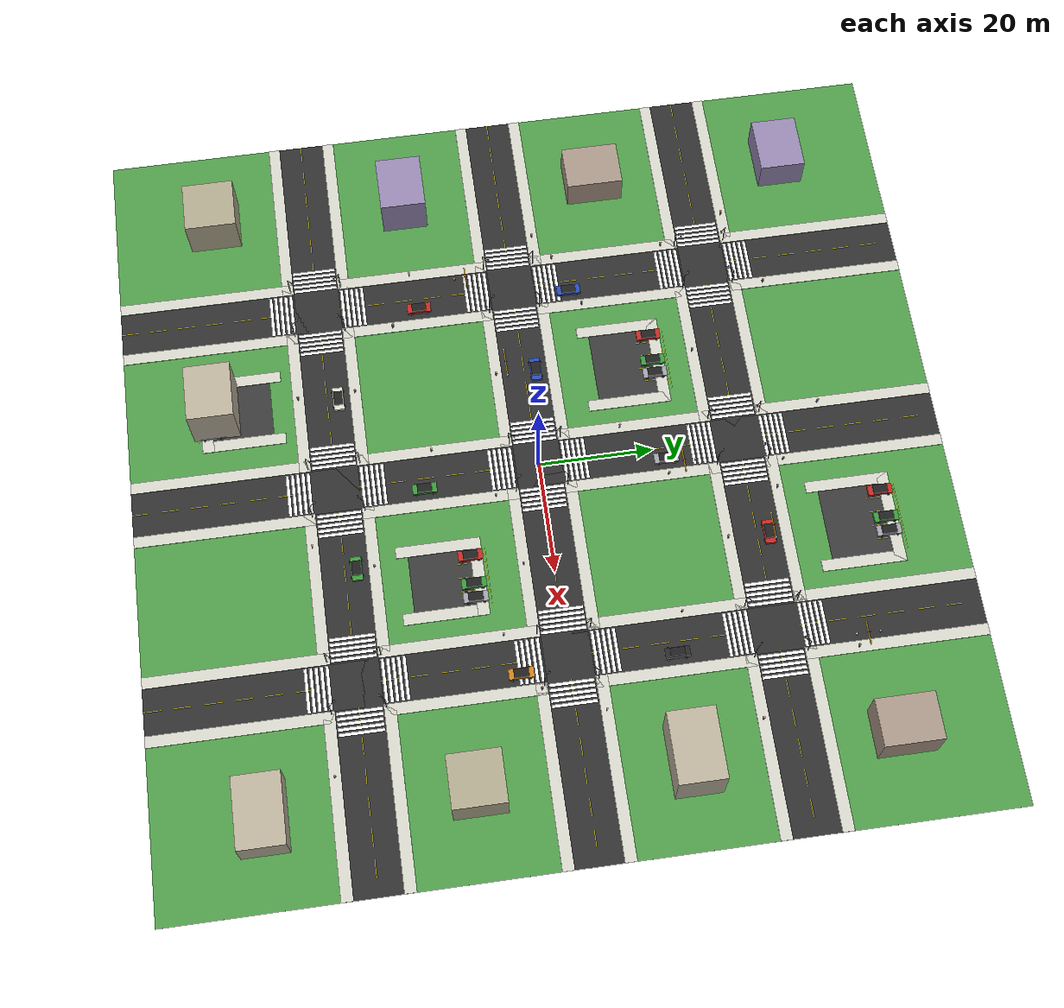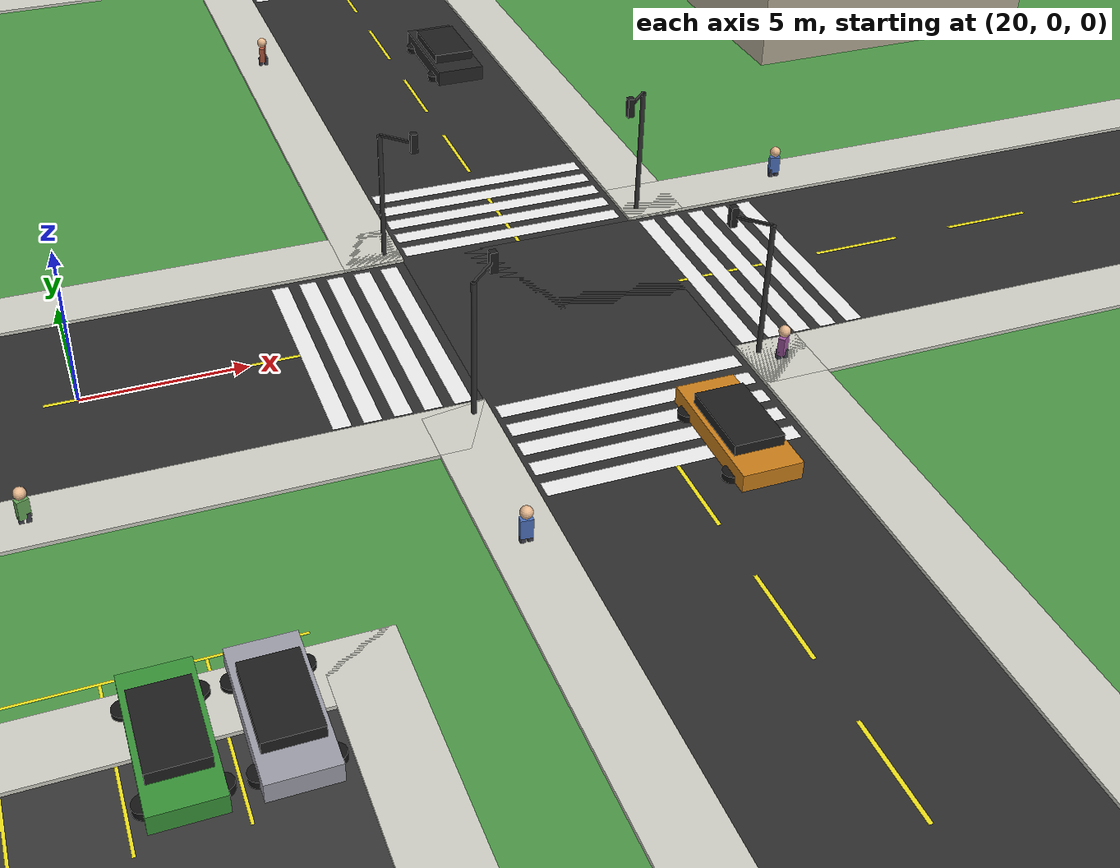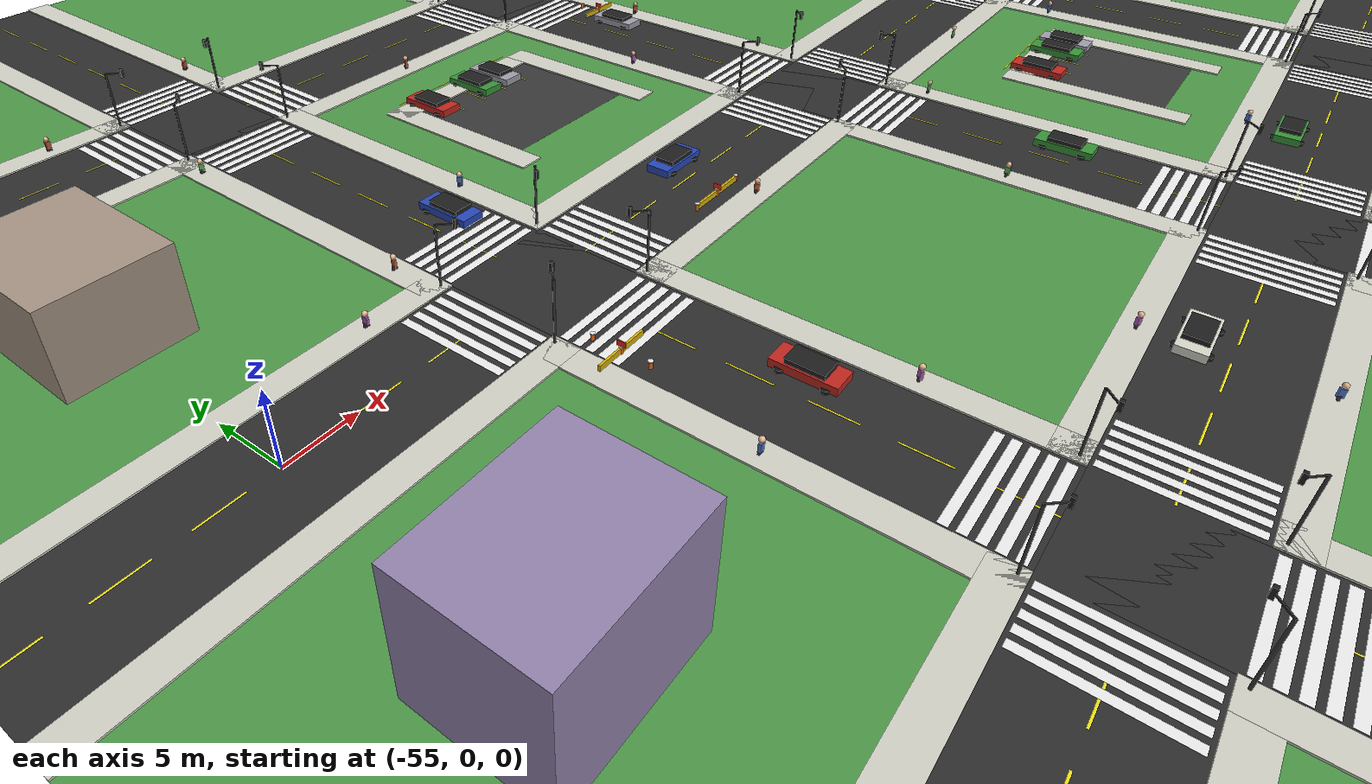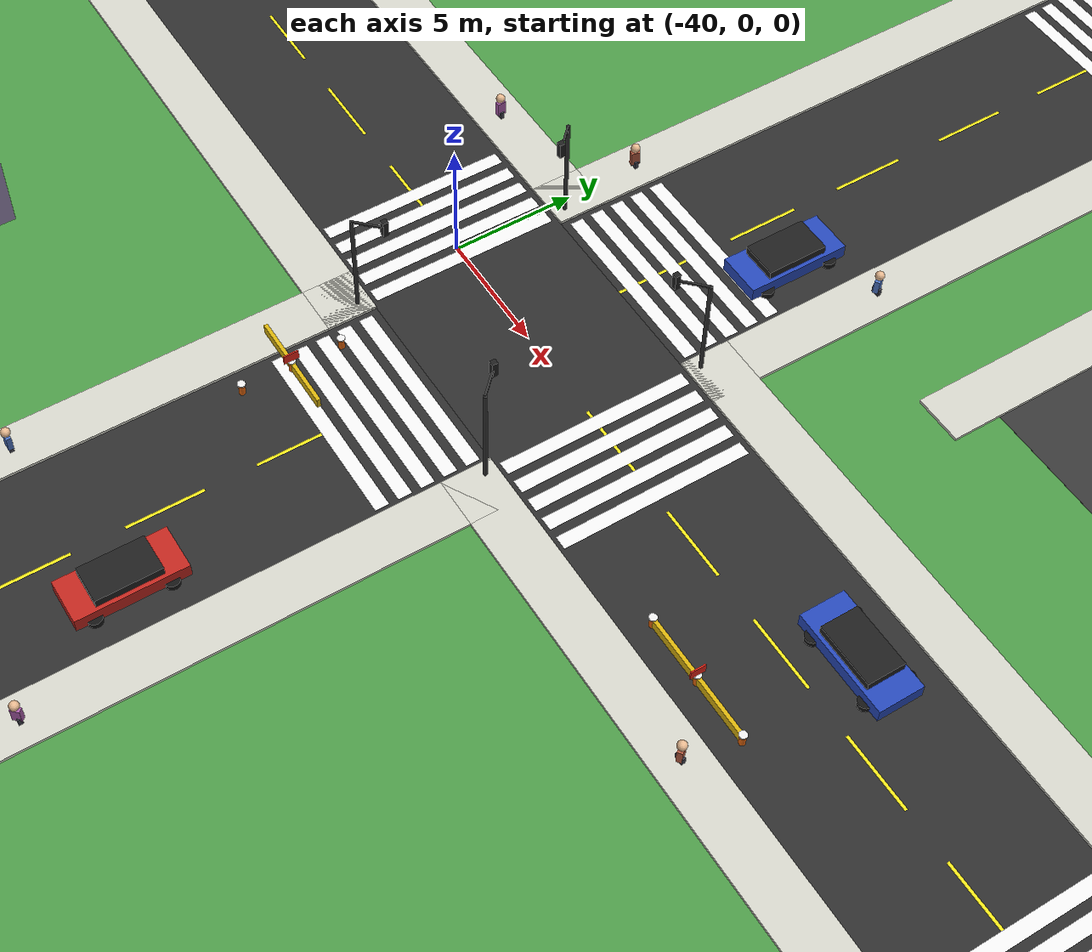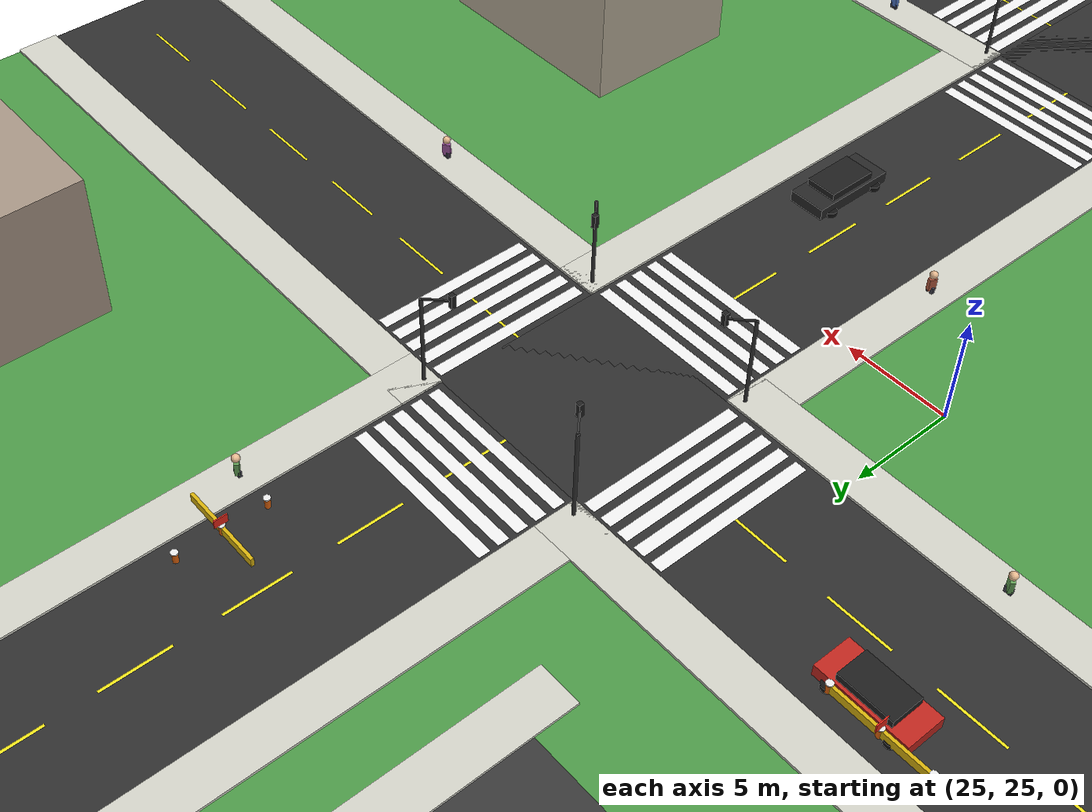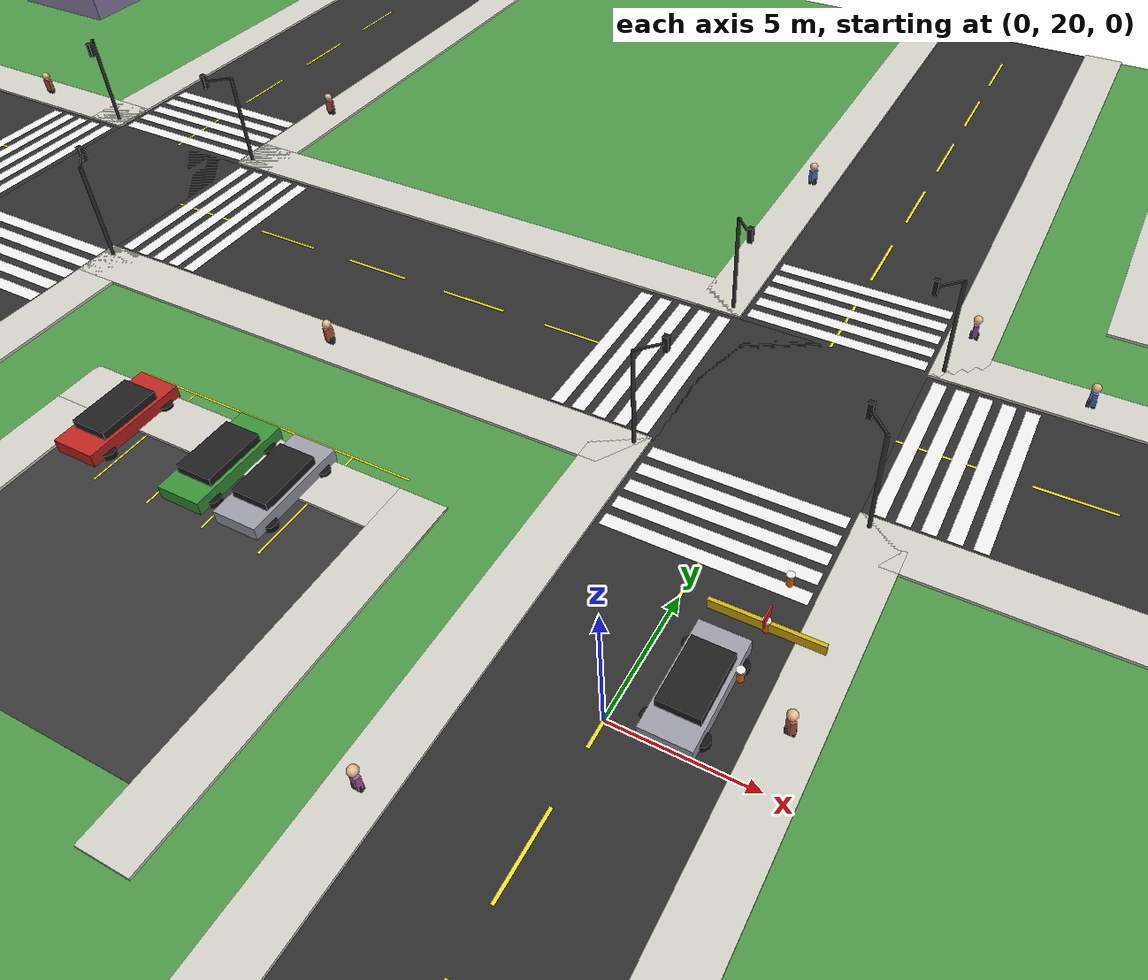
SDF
<?xml version="1.0"?>
<sdf version="1.9">
    <world name="city">
        <physics name="1ms" type="ignored">
            <max_step_size>0.001</max_step_size>
            <real_time_factor>1.0</real_time_factor>
        </physics>
        <plugin filename="gz-sim-physics-system" name="gz::sim::systems::Physics"></plugin>
        <plugin filename="gz-sim-user-commands-system" name="gz::sim::systems::UserCommands"></plugin>
        <plugin filename="gz-sim-scene-broadcaster-system" name="gz::sim::systems::SceneBroadcaster"></plugin>
        <plugin filename="gz-sim-contact-system" name="gz::sim::systems::Contact"></plugin>

        <plugin filename="gz-sim-sensors-system" name="gz::sim::systems::Sensors">
            <render_engine>ogre2</render_engine>
        </plugin>
        <plugin filename="gz-sim-imu-system" name="gz::sim::systems::Imu"></plugin>

        <spherical_coordinates>
            <surface_model>EARTH_WGS84</surface_model>
            <world_frame_orientation>ENU</world_frame_orientation>
            <latitude_deg>47.478950</latitude_deg>
            <longitude_deg>19.057785</longitude_deg>
            <elevation>0</elevation>
            <heading_deg>0</heading_deg>
        </spherical_coordinates>

        <gravity>0 0 -9.8000000000000007</gravity>
        <magnetic_field>5.5644999999999998e-06 2.2875799999999999e-05 -4.2388400000000002e-05</magnetic_field>
        <atmosphere type='adiabatic'/>
        <scene>
            <ambient>0.400000006 0.400000006 0.400000006 1</ambient>
            <background>0.699999988 0.699999988 0.699999988 1</background>
            <shadows>true</shadows>
        </scene>

        <light type="directional" name="sun">
            <cast_shadows>true</cast_shadows>
            <pose>0 0 10 0 0 0</pose>
            <diffuse>0.8 0.8 0.8 1</diffuse>
            <specular>0.2 0.2 0.2 1</specular>
            <attenuation>
                <range>1000</range>
                <constant>0.9</constant>
                <linear>0.01</linear>
                <quadratic>0.001</quadratic>
            </attenuation>
            <direction>-0.5 0.1 -0.9</direction>
        </light>

    <model name="ground_1"><static>true</static>
      <pose>0 0 -0.005 0 0 0</pose>
      <link name="l"><collision name="c"><geometry><box><size>140.0 140.0 0.01</size></box></geometry></collision>
        <visual name="v"><geometry><box><size>140.0 140.0 0.01</size></box></geometry>
          <material><ambient>0.3 0.6 0.28 1</ambient><diffuse>0.3 0.6 0.28 1</diffuse><specular>0.04 0.04 0.04 1</specular></material>
        </visual></link></model>

    <model name="road_v_2"><static>true</static>
      <pose>-35.0 0 0.008 0 0 0</pose>
      <link name="l"><collision name="c"><geometry><box><size>8.0 140.0 0.005</size></box></geometry></collision>
        <visual name="v"><geometry><box><size>8.0 140.0 0.005</size></box></geometry>
          <material><ambient>0.18 0.18 0.18 1</ambient><diffuse>0.18 0.18 0.18 1</diffuse><specular>0.04 0.04 0.04 1</specular></material>
        </visual></link></model>

    <model name="road_v_3"><static>true</static>
      <pose>0.0 0 0.008 0 0 0</pose>
      <link name="l"><collision name="c"><geometry><box><size>8.0 140.0 0.005</size></box></geometry></collision>
        <visual name="v"><geometry><box><size>8.0 140.0 0.005</size></box></geometry>
          <material><ambient>0.18 0.18 0.18 1</ambient><diffuse>0.18 0.18 0.18 1</diffuse><specular>0.04 0.04 0.04 1</specular></material>
        </visual></link></model>

    <model name="road_v_4"><static>true</static>
      <pose>35.0 0 0.008 0 0 0</pose>
      <link name="l"><collision name="c"><geometry><box><size>8.0 140.0 0.005</size></box></geometry></collision>
        <visual name="v"><geometry><box><size>8.0 140.0 0.005</size></box></geometry>
          <material><ambient>0.18 0.18 0.18 1</ambient><diffuse>0.18 0.18 0.18 1</diffuse><specular>0.04 0.04 0.04 1</specular></material>
        </visual></link></model>

    <model name="road_h_5"><static>true</static>
      <pose>0 -35.0 0.008 0 0 0</pose>
      <link name="l"><collision name="c"><geometry><box><size>140.0 8.0 0.005</size></box></geometry></collision>
        <visual name="v"><geometry><box><size>140.0 8.0 0.005</size></box></geometry>
          <material><ambient>0.18 0.18 0.18 1</ambient><diffuse>0.18 0.18 0.18 1</diffuse><specular>0.04 0.04 0.04 1</specular></material>
        </visual></link></model>

    <model name="road_h_6"><static>true</static>
      <pose>0 0.0 0.008 0 0 0</pose>
      <link name="l"><collision name="c"><geometry><box><size>140.0 8.0 0.005</size></box></geometry></collision>
        <visual name="v"><geometry><box><size>140.0 8.0 0.005</size></box></geometry>
          <material><ambient>0.18 0.18 0.18 1</ambient><diffuse>0.18 0.18 0.18 1</diffuse><specular>0.04 0.04 0.04 1</specular></material>
        </visual></link></model>

    <model name="road_h_7"><static>true</static>
      <pose>0 35.0 0.008 0 0 0</pose>
      <link name="l"><collision name="c"><geometry><box><size>140.0 8.0 0.005</size></box></geometry></collision>
        <visual name="v"><geometry><box><size>140.0 8.0 0.005</size></box></geometry>
          <material><ambient>0.18 0.18 0.18 1</ambient><diffuse>0.18 0.18 0.18 1</diffuse><specular>0.04 0.04 0.04 1</specular></material>
        </visual></link></model>

    <model name="sw_v_8"><static>true</static>
      <pose>-40.0 -54.5 0.065 0 0 0</pose>
      <link name="l"><collision name="c"><geometry><box><size>2.0 31.0 0.12</size></box></geometry></collision>
        <visual name="v"><geometry><box><size>2.0 31.0 0.12</size></box></geometry>
          <material><ambient>0.82 0.82 0.78 1</ambient><diffuse>0.82 0.82 0.78 1</diffuse><specular>0.04 0.04 0.04 1</specular></material>
        </visual></link></model>

    <model name="sw_v_9"><static>true</static>
      <pose>-40.0 -17.5 0.065 0 0 0</pose>
      <link name="l"><collision name="c"><geometry><box><size>2.0 27.0 0.12</size></box></geometry></collision>
        <visual name="v"><geometry><box><size>2.0 27.0 0.12</size></box></geometry>
          <material><ambient>0.82 0.82 0.78 1</ambient><diffuse>0.82 0.82 0.78 1</diffuse><specular>0.04 0.04 0.04 1</specular></material>
        </visual></link></model>

    <model name="sw_v_10"><static>true</static>
      <pose>-40.0 17.5 0.065 0 0 0</pose>
      <link name="l"><collision name="c"><geometry><box><size>2.0 27.0 0.12</size></box></geometry></collision>
        <visual name="v"><geometry><box><size>2.0 27.0 0.12</size></box></geometry>
          <material><ambient>0.82 0.82 0.78 1</ambient><diffuse>0.82 0.82 0.78 1</diffuse><specular>0.04 0.04 0.04 1</specular></material>
        </visual></link></model>

    <model name="sw_v_11"><static>true</static>
      <pose>-40.0 54.5 0.065 0 0 0</pose>
      <link name="l"><collision name="c"><geometry><box><size>2.0 31.0 0.12</size></box></geometry></collision>
        <visual name="v"><geometry><box><size>2.0 31.0 0.12</size></box></geometry>
          <material><ambient>0.82 0.82 0.78 1</ambient><diffuse>0.82 0.82 0.78 1</diffuse><specular>0.04 0.04 0.04 1</specular></material>
        </visual></link></model>

    <model name="sw_v_12"><static>true</static>
      <pose>-30.0 -54.5 0.065 0 0 0</pose>
      <link name="l"><collision name="c"><geometry><box><size>2.0 31.0 0.12</size></box></geometry></collision>
        <visual name="v"><geometry><box><size>2.0 31.0 0.12</size></box></geometry>
          <material><ambient>0.82 0.82 0.78 1</ambient><diffuse>0.82 0.82 0.78 1</diffuse><specular>0.04 0.04 0.04 1</specular></material>
        </visual></link></model>

    <model name="sw_v_13"><static>true</static>
      <pose>-30.0 -17.5 0.065 0 0 0</pose>
      <link name="l"><collision name="c"><geometry><box><size>2.0 27.0 0.12</size></box></geometry></collision>
        <visual name="v"><geometry><box><size>2.0 27.0 0.12</size></box></geometry>
          <material><ambient>0.82 0.82 0.78 1</ambient><diffuse>0.82 0.82 0.78 1</diffuse><specular>0.04 0.04 0.04 1</specular></material>
        </visual></link></model>

    <model name="sw_v_14"><static>true</static>
      <pose>-30.0 17.5 0.065 0 0 0</pose>
      <link name="l"><collision name="c"><geometry><box><size>2.0 27.0 0.12</size></box></geometry></collision>
        <visual name="v"><geometry><box><size>2.0 27.0 0.12</size></box></geometry>
          <material><ambient>0.82 0.82 0.78 1</ambient><diffuse>0.82 0.82 0.78 1</diffuse><specular>0.04 0.04 0.04 1</specular></material>
        </visual></link></model>

    <model name="sw_v_15"><static>true</static>
      <pose>-30.0 54.5 0.065 0 0 0</pose>
      <link name="l"><collision name="c"><geometry><box><size>2.0 31.0 0.12</size></box></geometry></collision>
        <visual name="v"><geometry><box><size>2.0 31.0 0.12</size></box></geometry>
          <material><ambient>0.82 0.82 0.78 1</ambient><diffuse>0.82 0.82 0.78 1</diffuse><specular>0.04 0.04 0.04 1</specular></material>
        </visual></link></model>

    <model name="sw_v_16"><static>true</static>
      <pose>-5.0 -54.5 0.065 0 0 0</pose>
      <link name="l"><collision name="c"><geometry><box><size>2.0 31.0 0.12</size></box></geometry></collision>
        <visual name="v"><geometry><box><size>2.0 31.0 0.12</size></box></geometry>
          <material><ambient>0.82 0.82 0.78 1</ambient><diffuse>0.82 0.82 0.78 1</diffuse><specular>0.04 0.04 0.04 1</specular></material>
        </visual></link></model>

    <model name="sw_v_17"><static>true</static>
      <pose>-5.0 -17.5 0.065 0 0 0</pose>
      <link name="l"><collision name="c"><geometry><box><size>2.0 27.0 0.12</size></box></geometry></collision>
        <visual name="v"><geometry><box><size>2.0 27.0 0.12</size></box></geometry>
          <material><ambient>0.82 0.82 0.78 1</ambient><diffuse>0.82 0.82 0.78 1</diffuse><specular>0.04 0.04 0.04 1</specular></material>
        </visual></link></model>

    <model name="sw_v_18"><static>true</static>
      <pose>-5.0 17.5 0.065 0 0 0</pose>
      <link name="l"><collision name="c"><geometry><box><size>2.0 27.0 0.12</size></box></geometry></collision>
        <visual name="v"><geometry><box><size>2.0 27.0 0.12</size></box></geometry>
          <material><ambient>0.82 0.82 0.78 1</ambient><diffuse>0.82 0.82 0.78 1</diffuse><specular>0.04 0.04 0.04 1</specular></material>
        </visual></link></model>

    <model name="sw_v_19"><static>true</static>
      <pose>-5.0 54.5 0.065 0 0 0</pose>
      <link name="l"><collision name="c"><geometry><box><size>2.0 31.0 0.12</size></box></geometry></collision>
        <visual name="v"><geometry><box><size>2.0 31.0 0.12</size></box></geometry>
          <material><ambient>0.82 0.82 0.78 1</ambient><diffuse>0.82 0.82 0.78 1</diffuse><specular>0.04 0.04 0.04 1</specular></material>
        </visual></link></model>

    <model name="sw_v_20"><static>true</static>
      <pose>5.0 -54.5 0.065 0 0 0</pose>
      <link name="l"><collision name="c"><geometry><box><size>2.0 31.0 0.12</size></box></geometry></collision>
        <visual name="v"><geometry><box><size>2.0 31.0 0.12</size></box></geometry>
          <material><ambient>0.82 0.82 0.78 1</ambient><diffuse>0.82 0.82 0.78 1</diffuse><specular>0.04 0.04 0.04 1</specular></material>
        </visual></link></model>

    <model name="sw_v_21"><static>true</static>
      <pose>5.0 -17.5 0.065 0 0 0</pose>
      <link name="l"><collision name="c"><geometry><box><size>2.0 27.0 0.12</size></box></geometry></collision>
        <visual name="v"><geometry><box><size>2.0 27.0 0.12</size></box></geometry>
          <material><ambient>0.82 0.82 0.78 1</ambient><diffuse>0.82 0.82 0.78 1</diffuse><specular>0.04 0.04 0.04 1</specular></material>
        </visual></link></model>

    <model name="sw_v_22"><static>true</static>
      <pose>5.0 17.5 0.065 0 0 0</pose>
      <link name="l"><collision name="c"><geometry><box><size>2.0 27.0 0.12</size></box></geometry></collision>
        <visual name="v"><geometry><box><size>2.0 27.0 0.12</size></box></geometry>
          <material><ambient>0.82 0.82 0.78 1</ambient><diffuse>0.82 0.82 0.78 1</diffuse><specular>0.04 0.04 0.04 1</specular></material>
        </visual></link></model>

    <model name="sw_v_23"><static>true</static>
      <pose>5.0 54.5 0.065 0 0 0</pose>
      <link name="l"><collision name="c"><geometry><box><size>2.0 31.0 0.12</size></box></geometry></collision>
        <visual name="v"><geometry><box><size>2.0 31.0 0.12</size></box></geometry>
          <material><ambient>0.82 0.82 0.78 1</ambient><diffuse>0.82 0.82 0.78 1</diffuse><specular>0.04 0.04 0.04 1</specular></material>
        </visual></link></model>

    <model name="sw_v_24"><static>true</static>
      <pose>30.0 -54.5 0.065 0 0 0</pose>
      <link name="l"><collision name="c"><geometry><box><size>2.0 31.0 0.12</size></box></geometry></collision>
        <visual name="v"><geometry><box><size>2.0 31.0 0.12</size></box></geometry>
          <material><ambient>0.82 0.82 0.78 1</ambient><diffuse>0.82 0.82 0.78 1</diffuse><specular>0.04 0.04 0.04 1</specular></material>
        </visual></link></model>

    <model name="sw_v_25"><static>true</static>
      <pose>30.0 -17.5 0.065 0 0 0</pose>
      <link name="l"><collision name="c"><geometry><box><size>2.0 27.0 0.12</size></box></geometry></collision>
        <visual name="v"><geometry><box><size>2.0 27.0 0.12</size></box></geometry>
          <material><ambient>0.82 0.82 0.78 1</ambient><diffuse>0.82 0.82 0.78 1</diffuse><specular>0.04 0.04 0.04 1</specular></material>
        </visual></link></model>

    <model name="sw_v_26"><static>true</static>
      <pose>30.0 17.5 0.065 0 0 0</pose>
      <link name="l"><collision name="c"><geometry><box><size>2.0 27.0 0.12</size></box></geometry></collision>
        <visual name="v"><geometry><box><size>2.0 27.0 0.12</size></box></geometry>
          <material><ambient>0.82 0.82 0.78 1</ambient><diffuse>0.82 0.82 0.78 1</diffuse><specular>0.04 0.04 0.04 1</specular></material>
        </visual></link></model>

    <model name="sw_v_27"><static>true</static>
      <pose>30.0 54.5 0.065 0 0 0</pose>
      <link name="l"><collision name="c"><geometry><box><size>2.0 31.0 0.12</size></box></geometry></collision>
        <visual name="v"><geometry><box><size>2.0 31.0 0.12</size></box></geometry>
          <material><ambient>0.82 0.82 0.78 1</ambient><diffuse>0.82 0.82 0.78 1</diffuse><specular>0.04 0.04 0.04 1</specular></material>
        </visual></link></model>

    <model name="sw_v_28"><static>true</static>
      <pose>40.0 -54.5 0.065 0 0 0</pose>
      <link name="l"><collision name="c"><geometry><box><size>2.0 31.0 0.12</size></box></geometry></collision>
        <visual name="v"><geometry><box><size>2.0 31.0 0.12</size></box></geometry>
          <material><ambient>0.82 0.82 0.78 1</ambient><diffuse>0.82 0.82 0.78 1</diffuse><specular>0.04 0.04 0.04 1</specular></material>
        </visual></link></model>

    <model name="sw_v_29"><static>true</static>
      <pose>40.0 -17.5 0.065 0 0 0</pose>
      <link name="l"><collision name="c"><geometry><box><size>2.0 27.0 0.12</size></box></geometry></collision>
        <visual name="v"><geometry><box><size>2.0 27.0 0.12</size></box></geometry>
          <material><ambient>0.82 0.82 0.78 1</ambient><diffuse>0.82 0.82 0.78 1</diffuse><specular>0.04 0.04 0.04 1</specular></material>
        </visual></link></model>

    <model name="sw_v_30"><static>true</static>
      <pose>40.0 17.5 0.065 0 0 0</pose>
      <link name="l"><collision name="c"><geometry><box><size>2.0 27.0 0.12</size></box></geometry></collision>
        <visual name="v"><geometry><box><size>2.0 27.0 0.12</size></box></geometry>
          <material><ambient>0.82 0.82 0.78 1</ambient><diffuse>0.82 0.82 0.78 1</diffuse><specular>0.04 0.04 0.04 1</specular></material>
        </visual></link></model>

    <model name="sw_v_31"><static>true</static>
      <pose>40.0 54.5 0.065 0 0 0</pose>
      <link name="l"><collision name="c"><geometry><box><size>2.0 31.0 0.12</size></box></geometry></collision>
        <visual name="v"><geometry><box><size>2.0 31.0 0.12</size></box></geometry>
          <material><ambient>0.82 0.82 0.78 1</ambient><diffuse>0.82 0.82 0.78 1</diffuse><specular>0.04 0.04 0.04 1</specular></material>
        </visual></link></model>

    <model name="sw_h_32"><static>true</static>
      <pose>-54.5 -40.0 0.065 0 0 0</pose>
      <link name="l"><collision name="c"><geometry><box><size>31.0 2.0 0.12</size></box></geometry></collision>
        <visual name="v"><geometry><box><size>31.0 2.0 0.12</size></box></geometry>
          <material><ambient>0.82 0.82 0.78 1</ambient><diffuse>0.82 0.82 0.78 1</diffuse><specular>0.04 0.04 0.04 1</specular></material>
        </visual></link></model>

    <model name="sw_h_33"><static>true</static>
      <pose>-17.5 -40.0 0.065 0 0 0</pose>
      <link name="l"><collision name="c"><geometry><box><size>27.0 2.0 0.12</size></box></geometry></collision>
        <visual name="v"><geometry><box><size>27.0 2.0 0.12</size></box></geometry>
          <material><ambient>0.82 0.82 0.78 1</ambient><diffuse>0.82 0.82 0.78 1</diffuse><specular>0.04 0.04 0.04 1</specular></material>
        </visual></link></model>

    <model name="sw_h_34"><static>true</static>
      <pose>17.5 -40.0 0.065 0 0 0</pose>
      <link name="l"><collision name="c"><geometry><box><size>27.0 2.0 0.12</size></box></geometry></collision>
        <visual name="v"><geometry><box><size>27.0 2.0 0.12</size></box></geometry>
          <material><ambient>0.82 0.82 0.78 1</ambient><diffuse>0.82 0.82 0.78 1</diffuse><specular>0.04 0.04 0.04 1</specular></material>
        </visual></link></model>

    <model name="sw_h_35"><static>true</static>
      <pose>54.5 -40.0 0.065 0 0 0</pose>
      <link name="l"><collision name="c"><geometry><box><size>31.0 2.0 0.12</size></box></geometry></collision>
        <visual name="v"><geometry><box><size>31.0 2.0 0.12</size></box></geometry>
          <material><ambient>0.82 0.82 0.78 1</ambient><diffuse>0.82 0.82 0.78 1</diffuse><specular>0.04 0.04 0.04 1</specular></material>
        </visual></link></model>

    <model name="sw_h_36"><static>true</static>
      <pose>-54.5 -30.0 0.065 0 0 0</pose>
      <link name="l"><collision name="c"><geometry><box><size>31.0 2.0 0.12</size></box></geometry></collision>
        <visual name="v"><geometry><box><size>31.0 2.0 0.12</size></box></geometry>
          <material><ambient>0.82 0.82 0.78 1</ambient><diffuse>0.82 0.82 0.78 1</diffuse><specular>0.04 0.04 0.04 1</specular></material>
        </visual></link></model>

    <model name="sw_h_37"><static>true</static>
      <pose>-17.5 -30.0 0.065 0 0 0</pose>
      <link name="l"><collision name="c"><geometry><box><size>27.0 2.0 0.12</size></box></geometry></collision>
        <visual name="v"><geometry><box><size>27.0 2.0 0.12</size></box></geometry>
          <material><ambient>0.82 0.82 0.78 1</ambient><diffuse>0.82 0.82 0.78 1</diffuse><specular>0.04 0.04 0.04 1</specular></material>
        </visual></link></model>

    <model name="sw_h_38"><static>true</static>
      <pose>17.5 -30.0 0.065 0 0 0</pose>
      <link name="l"><collision name="c"><geometry><box><size>27.0 2.0 0.12</size></box></geometry></collision>
        <visual name="v"><geometry><box><size>27.0 2.0 0.12</size></box></geometry>
          <material><ambient>0.82 0.82 0.78 1</ambient><diffuse>0.82 0.82 0.78 1</diffuse><specular>0.04 0.04 0.04 1</specular></material>
        </visual></link></model>

    <model name="sw_h_39"><static>true</static>
      <pose>54.5 -30.0 0.065 0 0 0</pose>
      <link name="l"><collision name="c"><geometry><box><size>31.0 2.0 0.12</size></box></geometry></collision>
        <visual name="v"><geometry><box><size>31.0 2.0 0.12</size></box></geometry>
          <material><ambient>0.82 0.82 0.78 1</ambient><diffuse>0.82 0.82 0.78 1</diffuse><specular>0.04 0.04 0.04 1</specular></material>
        </visual></link></model>

    <model name="sw_h_40"><static>true</static>
      <pose>-54.5 -5.0 0.065 0 0 0</pose>
      <link name="l"><collision name="c"><geometry><box><size>31.0 2.0 0.12</size></box></geometry></collision>
        <visual name="v"><geometry><box><size>31.0 2.0 0.12</size></box></geometry>
          <material><ambient>0.82 0.82 0.78 1</ambient><diffuse>0.82 0.82 0.78 1</diffuse><specular>0.04 0.04 0.04 1</specular></material>
        </visual></link></model>

    <model name="sw_h_41"><static>true</static>
      <pose>-17.5 -5.0 0.065 0 0 0</pose>
      <link name="l"><collision name="c"><geometry><box><size>27.0 2.0 0.12</size></box></geometry></collision>
        <visual name="v"><geometry><box><size>27.0 2.0 0.12</size></box></geometry>
          <material><ambient>0.82 0.82 0.78 1</ambient><diffuse>0.82 0.82 0.78 1</diffuse><specular>0.04 0.04 0.04 1</specular></material>
        </visual></link></model>

    <model name="sw_h_42"><static>true</static>
      <pose>17.5 -5.0 0.065 0 0 0</pose>
      <link name="l"><collision name="c"><geometry><box><size>27.0 2.0 0.12</size></box></geometry></collision>
        <visual name="v"><geometry><box><size>27.0 2.0 0.12</size></box></geometry>
          <material><ambient>0.82 0.82 0.78 1</ambient><diffuse>0.82 0.82 0.78 1</diffuse><specular>0.04 0.04 0.04 1</specular></material>
        </visual></link></model>

    <model name="sw_h_43"><static>true</static>
      <pose>54.5 -5.0 0.065 0 0 0</pose>
      <link name="l"><collision name="c"><geometry><box><size>31.0 2.0 0.12</size></box></geometry></collision>
        <visual name="v"><geometry><box><size>31.0 2.0 0.12</size></box></geometry>
          <material><ambient>0.82 0.82 0.78 1</ambient><diffuse>0.82 0.82 0.78 1</diffuse><specular>0.04 0.04 0.04 1</specular></material>
        </visual></link></model>

    <model name="sw_h_44"><static>true</static>
      <pose>-54.5 5.0 0.065 0 0 0</pose>
      <link name="l"><collision name="c"><geometry><box><size>31.0 2.0 0.12</size></box></geometry></collision>
        <visual name="v"><geometry><box><size>31.0 2.0 0.12</size></box></geometry>
          <material><ambient>0.82 0.82 0.78 1</ambient><diffuse>0.82 0.82 0.78 1</diffuse><specular>0.04 0.04 0.04 1</specular></material>
        </visual></link></model>

    <model name="sw_h_45"><static>true</static>
      <pose>-17.5 5.0 0.065 0 0 0</pose>
      <link name="l"><collision name="c"><geometry><box><size>27.0 2.0 0.12</size></box></geometry></collision>
        <visual name="v"><geometry><box><size>27.0 2.0 0.12</size></box></geometry>
          <material><ambient>0.82 0.82 0.78 1</ambient><diffuse>0.82 0.82 0.78 1</diffuse><specular>0.04 0.04 0.04 1</specular></material>
        </visual></link></model>

    <model name="sw_h_46"><static>true</static>
      <pose>17.5 5.0 0.065 0 0 0</pose>
      <link name="l"><collision name="c"><geometry><box><size>27.0 2.0 0.12</size></box></geometry></collision>
        <visual name="v"><geometry><box><size>27.0 2.0 0.12</size></box></geometry>
          <material><ambient>0.82 0.82 0.78 1</ambient><diffuse>0.82 0.82 0.78 1</diffuse><specular>0.04 0.04 0.04 1</specular></material>
        </visual></link></model>

    <model name="sw_h_47"><static>true</static>
      <pose>54.5 5.0 0.065 0 0 0</pose>
      <link name="l"><collision name="c"><geometry><box><size>31.0 2.0 0.12</size></box></geometry></collision>
        <visual name="v"><geometry><box><size>31.0 2.0 0.12</size></box></geometry>
          <material><ambient>0.82 0.82 0.78 1</ambient><diffuse>0.82 0.82 0.78 1</diffuse><specular>0.04 0.04 0.04 1</specular></material>
        </visual></link></model>

    <model name="sw_h_48"><static>true</static>
      <pose>-54.5 30.0 0.065 0 0 0</pose>
      <link name="l"><collision name="c"><geometry><box><size>31.0 2.0 0.12</size></box></geometry></collision>
        <visual name="v"><geometry><box><size>31.0 2.0 0.12</size></box></geometry>
          <material><ambient>0.82 0.82 0.78 1</ambient><diffuse>0.82 0.82 0.78 1</diffuse><specular>0.04 0.04 0.04 1</specular></material>
        </visual></link></model>

    <model name="sw_h_49"><static>true</static>
      <pose>-17.5 30.0 0.065 0 0 0</pose>
      <link name="l"><collision name="c"><geometry><box><size>27.0 2.0 0.12</size></box></geometry></collision>
        <visual name="v"><geometry><box><size>27.0 2.0 0.12</size></box></geometry>
          <material><ambient>0.82 0.82 0.78 1</ambient><diffuse>0.82 0.82 0.78 1</diffuse><specular>0.04 0.04 0.04 1</specular></material>
        </visual></link></model>

    <model name="sw_h_50"><static>true</static>
      <pose>17.5 30.0 0.065 0 0 0</pose>
      <link name="l"><collision name="c"><geometry><box><size>27.0 2.0 0.12</size></box></geometry></collision>
        <visual name="v"><geometry><box><size>27.0 2.0 0.12</size></box></geometry>
          <material><ambient>0.82 0.82 0.78 1</ambient><diffuse>0.82 0.82 0.78 1</diffuse><specular>0.04 0.04 0.04 1</specular></material>
        </visual></link></model>

    <model name="sw_h_51"><static>true</static>
      <pose>54.5 30.0 0.065 0 0 0</pose>
      <link name="l"><collision name="c"><geometry><box><size>31.0 2.0 0.12</size></box></geometry></collision>
        <visual name="v"><geometry><box><size>31.0 2.0 0.12</size></box></geometry>
          <material><ambient>0.82 0.82 0.78 1</ambient><diffuse>0.82 0.82 0.78 1</diffuse><specular>0.04 0.04 0.04 1</specular></material>
        </visual></link></model>

    <model name="sw_h_52"><static>true</static>
      <pose>-54.5 40.0 0.065 0 0 0</pose>
      <link name="l"><collision name="c"><geometry><box><size>31.0 2.0 0.12</size></box></geometry></collision>
        <visual name="v"><geometry><box><size>31.0 2.0 0.12</size></box></geometry>
          <material><ambient>0.82 0.82 0.78 1</ambient><diffuse>0.82 0.82 0.78 1</diffuse><specular>0.04 0.04 0.04 1</specular></material>
        </visual></link></model>

    <model name="sw_h_53"><static>true</static>
      <pose>-17.5 40.0 0.065 0 0 0</pose>
      <link name="l"><collision name="c"><geometry><box><size>27.0 2.0 0.12</size></box></geometry></collision>
        <visual name="v"><geometry><box><size>27.0 2.0 0.12</size></box></geometry>
          <material><ambient>0.82 0.82 0.78 1</ambient><diffuse>0.82 0.82 0.78 1</diffuse><specular>0.04 0.04 0.04 1</specular></material>
        </visual></link></model>

    <model name="sw_h_54"><static>true</static>
      <pose>17.5 40.0 0.065 0 0 0</pose>
      <link name="l"><collision name="c"><geometry><box><size>27.0 2.0 0.12</size></box></geometry></collision>
        <visual name="v"><geometry><box><size>27.0 2.0 0.12</size></box></geometry>
          <material><ambient>0.82 0.82 0.78 1</ambient><diffuse>0.82 0.82 0.78 1</diffuse><specular>0.04 0.04 0.04 1</specular></material>
        </visual></link></model>

    <model name="sw_h_55"><static>true</static>
      <pose>54.5 40.0 0.065 0 0 0</pose>
      <link name="l"><collision name="c"><geometry><box><size>31.0 2.0 0.12</size></box></geometry></collision>
        <visual name="v"><geometry><box><size>31.0 2.0 0.12</size></box></geometry>
          <material><ambient>0.82 0.82 0.78 1</ambient><diffuse>0.82 0.82 0.78 1</diffuse><specular>0.04 0.04 0.04 1</specular></material>
        </visual></link></model>

    <model name="sw_corner_56"><static>true</static>
      <pose>-40.0 -40.0 0.065 0 0 0</pose>
      <link name="l"><collision name="c"><geometry><box><size>2.0 2.0 0.12</size></box></geometry></collision>
        <visual name="v"><geometry><box><size>2.0 2.0 0.12</size></box></geometry>
          <material><ambient>0.82 0.82 0.78 1</ambient><diffuse>0.82 0.82 0.78 1</diffuse><specular>0.04 0.04 0.04 1</specular></material>
        </visual></link></model>

    <model name="sw_corner_57"><static>true</static>
      <pose>-40.0 -30.0 0.065 0 0 0</pose>
      <link name="l"><collision name="c"><geometry><box><size>2.0 2.0 0.12</size></box></geometry></collision>
        <visual name="v"><geometry><box><size>2.0 2.0 0.12</size></box></geometry>
          <material><ambient>0.82 0.82 0.78 1</ambient><diffuse>0.82 0.82 0.78 1</diffuse><specular>0.04 0.04 0.04 1</specular></material>
        </visual></link></model>

    <model name="sw_corner_58"><static>true</static>
      <pose>-30.0 -40.0 0.065 0 0 0</pose>
      <link name="l"><collision name="c"><geometry><box><size>2.0 2.0 0.12</size></box></geometry></collision>
        <visual name="v"><geometry><box><size>2.0 2.0 0.12</size></box></geometry>
          <material><ambient>0.82 0.82 0.78 1</ambient><diffuse>0.82 0.82 0.78 1</diffuse><specular>0.04 0.04 0.04 1</specular></material>
        </visual></link></model>

    <model name="sw_corner_59"><static>true</static>
      <pose>-30.0 -30.0 0.065 0 0 0</pose>
      <link name="l"><collision name="c"><geometry><box><size>2.0 2.0 0.12</size></box></geometry></collision>
        <visual name="v"><geometry><box><size>2.0 2.0 0.12</size></box></geometry>
          <material><ambient>0.82 0.82 0.78 1</ambient><diffuse>0.82 0.82 0.78 1</diffuse><specular>0.04 0.04 0.04 1</specular></material>
        </visual></link></model>

    <model name="sw_corner_60"><static>true</static>
      <pose>-40.0 -5.0 0.065 0 0 0</pose>
      <link name="l"><collision name="c"><geometry><box><size>2.0 2.0 0.12</size></box></geometry></collision>
        <visual name="v"><geometry><box><size>2.0 2.0 0.12</size></box></geometry>
          <material><ambient>0.82 0.82 0.78 1</ambient><diffuse>0.82 0.82 0.78 1</diffuse><specular>0.04 0.04 0.04 1</specular></material>
        </visual></link></model>

    <model name="sw_corner_61"><static>true</static>
      <pose>-40.0 5.0 0.065 0 0 0</pose>
      <link name="l"><collision name="c"><geometry><box><size>2.0 2.0 0.12</size></box></geometry></collision>
        <visual name="v"><geometry><box><size>2.0 2.0 0.12</size></box></geometry>
          <material><ambient>0.82 0.82 0.78 1</ambient><diffuse>0.82 0.82 0.78 1</diffuse><specular>0.04 0.04 0.04 1</specular></material>
        </visual></link></model>

    <model name="sw_corner_62"><static>true</static>
      <pose>-30.0 -5.0 0.065 0 0 0</pose>
      <link name="l"><collision name="c"><geometry><box><size>2.0 2.0 0.12</size></box></geometry></collision>
        <visual name="v"><geometry><box><size>2.0 2.0 0.12</size></box></geometry>
          <material><ambient>0.82 0.82 0.78 1</ambient><diffuse>0.82 0.82 0.78 1</diffuse><specular>0.04 0.04 0.04 1</specular></material>
        </visual></link></model>

    <model name="sw_corner_63"><static>true</static>
      <pose>-30.0 5.0 0.065 0 0 0</pose>
      <link name="l"><collision name="c"><geometry><box><size>2.0 2.0 0.12</size></box></geometry></collision>
        <visual name="v"><geometry><box><size>2.0 2.0 0.12</size></box></geometry>
          <material><ambient>0.82 0.82 0.78 1</ambient><diffuse>0.82 0.82 0.78 1</diffuse><specular>0.04 0.04 0.04 1</specular></material>
        </visual></link></model>

    <model name="sw_corner_64"><static>true</static>
      <pose>-40.0 30.0 0.065 0 0 0</pose>
      <link name="l"><collision name="c"><geometry><box><size>2.0 2.0 0.12</size></box></geometry></collision>
        <visual name="v"><geometry><box><size>2.0 2.0 0.12</size></box></geometry>
          <material><ambient>0.82 0.82 0.78 1</ambient><diffuse>0.82 0.82 0.78 1</diffuse><specular>0.04 0.04 0.04 1</specular></material>
        </visual></link></model>

    <model name="sw_corner_65"><static>true</static>
      <pose>-40.0 40.0 0.065 0 0 0</pose>
      <link name="l"><collision name="c"><geometry><box><size>2.0 2.0 0.12</size></box></geometry></collision>
        <visual name="v"><geometry><box><size>2.0 2.0 0.12</size></box></geometry>
          <material><ambient>0.82 0.82 0.78 1</ambient><diffuse>0.82 0.82 0.78 1</diffuse><specular>0.04 0.04 0.04 1</specular></material>
        </visual></link></model>

    <model name="sw_corner_66"><static>true</static>
      <pose>-30.0 30.0 0.065 0 0 0</pose>
      <link name="l"><collision name="c"><geometry><box><size>2.0 2.0 0.12</size></box></geometry></collision>
        <visual name="v"><geometry><box><size>2.0 2.0 0.12</size></box></geometry>
          <material><ambient>0.82 0.82 0.78 1</ambient><diffuse>0.82 0.82 0.78 1</diffuse><specular>0.04 0.04 0.04 1</specular></material>
        </visual></link></model>

    <model name="sw_corner_67"><static>true</static>
      <pose>-30.0 40.0 0.065 0 0 0</pose>
      <link name="l"><collision name="c"><geometry><box><size>2.0 2.0 0.12</size></box></geometry></collision>
        <visual name="v"><geometry><box><size>2.0 2.0 0.12</size></box></geometry>
          <material><ambient>0.82 0.82 0.78 1</ambient><diffuse>0.82 0.82 0.78 1</diffuse><specular>0.04 0.04 0.04 1</specular></material>
        </visual></link></model>

    <model name="sw_corner_68"><static>true</static>
      <pose>-5.0 -40.0 0.065 0 0 0</pose>
      <link name="l"><collision name="c"><geometry><box><size>2.0 2.0 0.12</size></box></geometry></collision>
        <visual name="v"><geometry><box><size>2.0 2.0 0.12</size></box></geometry>
          <material><ambient>0.82 0.82 0.78 1</ambient><diffuse>0.82 0.82 0.78 1</diffuse><specular>0.04 0.04 0.04 1</specular></material>
        </visual></link></model>

    <model name="sw_corner_69"><static>true</static>
      <pose>-5.0 -30.0 0.065 0 0 0</pose>
      <link name="l"><collision name="c"><geometry><box><size>2.0 2.0 0.12</size></box></geometry></collision>
        <visual name="v"><geometry><box><size>2.0 2.0 0.12</size></box></geometry>
          <material><ambient>0.82 0.82 0.78 1</ambient><diffuse>0.82 0.82 0.78 1</diffuse><specular>0.04 0.04 0.04 1</specular></material>
        </visual></link></model>

    <model name="sw_corner_70"><static>true</static>
      <pose>5.0 -40.0 0.065 0 0 0</pose>
      <link name="l"><collision name="c"><geometry><box><size>2.0 2.0 0.12</size></box></geometry></collision>
        <visual name="v"><geometry><box><size>2.0 2.0 0.12</size></box></geometry>
          <material><ambient>0.82 0.82 0.78 1</ambient><diffuse>0.82 0.82 0.78 1</diffuse><specular>0.04 0.04 0.04 1</specular></material>
        </visual></link></model>

    <model name="sw_corner_71"><static>true</static>
      <pose>5.0 -30.0 0.065 0 0 0</pose>
      <link name="l"><collision name="c"><geometry><box><size>2.0 2.0 0.12</size></box></geometry></collision>
        <visual name="v"><geometry><box><size>2.0 2.0 0.12</size></box></geometry>
          <material><ambient>0.82 0.82 0.78 1</ambient><diffuse>0.82 0.82 0.78 1</diffuse><specular>0.04 0.04 0.04 1</specular></material>
        </visual></link></model>

    <model name="sw_corner_72"><static>true</static>
      <pose>-5.0 -5.0 0.065 0 0 0</pose>
      <link name="l"><collision name="c"><geometry><box><size>2.0 2.0 0.12</size></box></geometry></collision>
        <visual name="v"><geometry><box><size>2.0 2.0 0.12</size></box></geometry>
          <material><ambient>0.82 0.82 0.78 1</ambient><diffuse>0.82 0.82 0.78 1</diffuse><specular>0.04 0.04 0.04 1</specular></material>
        </visual></link></model>

    <model name="sw_corner_73"><static>true</static>
      <pose>-5.0 5.0 0.065 0 0 0</pose>
      <link name="l"><collision name="c"><geometry><box><size>2.0 2.0 0.12</size></box></geometry></collision>
        <visual name="v"><geometry><box><size>2.0 2.0 0.12</size></box></geometry>
          <material><ambient>0.82 0.82 0.78 1</ambient><diffuse>0.82 0.82 0.78 1</diffuse><specular>0.04 0.04 0.04 1</specular></material>
        </visual></link></model>

    <model name="sw_corner_74"><static>true</static>
      <pose>5.0 -5.0 0.065 0 0 0</pose>
      <link name="l"><collision name="c"><geometry><box><size>2.0 2.0 0.12</size></box></geometry></collision>
        <visual name="v"><geometry><box><size>2.0 2.0 0.12</size></box></geometry>
          <material><ambient>0.82 0.82 0.78 1</ambient><diffuse>0.82 0.82 0.78 1</diffuse><specular>0.04 0.04 0.04 1</specular></material>
        </visual></link></model>

    <model name="sw_corner_75"><static>true</static>
      <pose>5.0 5.0 0.065 0 0 0</pose>
      <link name="l"><collision name="c"><geometry><box><size>2.0 2.0 0.12</size></box></geometry></collision>
        <visual name="v"><geometry><box><size>2.0 2.0 0.12</size></box></geometry>
          <material><ambient>0.82 0.82 0.78 1</ambient><diffuse>0.82 0.82 0.78 1</diffuse><specular>0.04 0.04 0.04 1</specular></material>
        </visual></link></model>

    <model name="sw_corner_76"><static>true</static>
      <pose>-5.0 30.0 0.065 0 0 0</pose>
      <link name="l"><collision name="c"><geometry><box><size>2.0 2.0 0.12</size></box></geometry></collision>
        <visual name="v"><geometry><box><size>2.0 2.0 0.12</size></box></geometry>
          <material><ambient>0.82 0.82 0.78 1</ambient><diffuse>0.82 0.82 0.78 1</diffuse><specular>0.04 0.04 0.04 1</specular></material>
        </visual></link></model>

    <model name="sw_corner_77"><static>true</static>
      <pose>-5.0 40.0 0.065 0 0 0</pose>
      <link name="l"><collision name="c"><geometry><box><size>2.0 2.0 0.12</size></box></geometry></collision>
        <visual name="v"><geometry><box><size>2.0 2.0 0.12</size></box></geometry>
          <material><ambient>0.82 0.82 0.78 1</ambient><diffuse>0.82 0.82 0.78 1</diffuse><specular>0.04 0.04 0.04 1</specular></material>
        </visual></link></model>

    <model name="sw_corner_78"><static>true</static>
      <pose>5.0 30.0 0.065 0 0 0</pose>
      <link name="l"><collision name="c"><geometry><box><size>2.0 2.0 0.12</size></box></geometry></collision>
        <visual name="v"><geometry><box><size>2.0 2.0 0.12</size></box></geometry>
          <material><ambient>0.82 0.82 0.78 1</ambient><diffuse>0.82 0.82 0.78 1</diffuse><specular>0.04 0.04 0.04 1</specular></material>
        </visual></link></model>

    <model name="sw_corner_79"><static>true</static>
      <pose>5.0 40.0 0.065 0 0 0</pose>
      <link name="l"><collision name="c"><geometry><box><size>2.0 2.0 0.12</size></box></geometry></collision>
        <visual name="v"><geometry><box><size>2.0 2.0 0.12</size></box></geometry>
          <material><ambient>0.82 0.82 0.78 1</ambient><diffuse>0.82 0.82 0.78 1</diffuse><specular>0.04 0.04 0.04 1</specular></material>
        </visual></link></model>

    <model name="sw_corner_80"><static>true</static>
      <pose>30.0 -40.0 0.065 0 0 0</pose>
      <link name="l"><collision name="c"><geometry><box><size>2.0 2.0 0.12</size></box></geometry></collision>
        <visual name="v"><geometry><box><size>2.0 2.0 0.12</size></box></geometry>
          <material><ambient>0.82 0.82 0.78 1</ambient><diffuse>0.82 0.82 0.78 1</diffuse><specular>0.04 0.04 0.04 1</specular></material>
        </visual></link></model>

    <model name="sw_corner_81"><static>true</static>
      <pose>30.0 -30.0 0.065 0 0 0</pose>
      <link name="l"><collision name="c"><geometry><box><size>2.0 2.0 0.12</size></box></geometry></collision>
        <visual name="v"><geometry><box><size>2.0 2.0 0.12</size></box></geometry>
          <material><ambient>0.82 0.82 0.78 1</ambient><diffuse>0.82 0.82 0.78 1</diffuse><specular>0.04 0.04 0.04 1</specular></material>
        </visual></link></model>

    <model name="sw_corner_82"><static>true</static>
      <pose>40.0 -40.0 0.065 0 0 0</pose>
      <link name="l"><collision name="c"><geometry><box><size>2.0 2.0 0.12</size></box></geometry></collision>
        <visual name="v"><geometry><box><size>2.0 2.0 0.12</size></box></geometry>
          <material><ambient>0.82 0.82 0.78 1</ambient><diffuse>0.82 0.82 0.78 1</diffuse><specular>0.04 0.04 0.04 1</specular></material>
        </visual></link></model>

    <model name="sw_corner_83"><static>true</static>
      <pose>40.0 -30.0 0.065 0 0 0</pose>
      <link name="l"><collision name="c"><geometry><box><size>2.0 2.0 0.12</size></box></geometry></collision>
        <visual name="v"><geometry><box><size>2.0 2.0 0.12</size></box></geometry>
          <material><ambient>0.82 0.82 0.78 1</ambient><diffuse>0.82 0.82 0.78 1</diffuse><specular>0.04 0.04 0.04 1</specular></material>
        </visual></link></model>

    <model name="sw_corner_84"><static>true</static>
      <pose>30.0 -5.0 0.065 0 0 0</pose>
      <link name="l"><collision name="c"><geometry><box><size>2.0 2.0 0.12</size></box></geometry></collision>
        <visual name="v"><geometry><box><size>2.0 2.0 0.12</size></box></geometry>
          <material><ambient>0.82 0.82 0.78 1</ambient><diffuse>0.82 0.82 0.78 1</diffuse><specular>0.04 0.04 0.04 1</specular></material>
        </visual></link></model>

    <model name="sw_corner_85"><static>true</static>
      <pose>30.0 5.0 0.065 0 0 0</pose>
      <link name="l"><collision name="c"><geometry><box><size>2.0 2.0 0.12</size></box></geometry></collision>
        <visual name="v"><geometry><box><size>2.0 2.0 0.12</size></box></geometry>
          <material><ambient>0.82 0.82 0.78 1</ambient><diffuse>0.82 0.82 0.78 1</diffuse><specular>0.04 0.04 0.04 1</specular></material>
        </visual></link></model>

    <model name="sw_corner_86"><static>true</static>
      <pose>40.0 -5.0 0.065 0 0 0</pose>
      <link name="l"><collision name="c"><geometry><box><size>2.0 2.0 0.12</size></box></geometry></collision>
        <visual name="v"><geometry><box><size>2.0 2.0 0.12</size></box></geometry>
          <material><ambient>0.82 0.82 0.78 1</ambient><diffuse>0.82 0.82 0.78 1</diffuse><specular>0.04 0.04 0.04 1</specular></material>
        </visual></link></model>

    <model name="sw_corner_87"><static>true</static>
      <pose>40.0 5.0 0.065 0 0 0</pose>
      <link name="l"><collision name="c"><geometry><box><size>2.0 2.0 0.12</size></box></geometry></collision>
        <visual name="v"><geometry><box><size>2.0 2.0 0.12</size></box></geometry>
          <material><ambient>0.82 0.82 0.78 1</ambient><diffuse>0.82 0.82 0.78 1</diffuse><specular>0.04 0.04 0.04 1</specular></material>
        </visual></link></model>

    <model name="sw_corner_88"><static>true</static>
      <pose>30.0 30.0 0.065 0 0 0</pose>
      <link name="l"><collision name="c"><geometry><box><size>2.0 2.0 0.12</size></box></geometry></collision>
        <visual name="v"><geometry><box><size>2.0 2.0 0.12</size></box></geometry>
          <material><ambient>0.82 0.82 0.78 1</ambient><diffuse>0.82 0.82 0.78 1</diffuse><specular>0.04 0.04 0.04 1</specular></material>
        </visual></link></model>

    <model name="sw_corner_89"><static>true</static>
      <pose>30.0 40.0 0.065 0 0 0</pose>
      <link name="l"><collision name="c"><geometry><box><size>2.0 2.0 0.12</size></box></geometry></collision>
        <visual name="v"><geometry><box><size>2.0 2.0 0.12</size></box></geometry>
          <material><ambient>0.82 0.82 0.78 1</ambient><diffuse>0.82 0.82 0.78 1</diffuse><specular>0.04 0.04 0.04 1</specular></material>
        </visual></link></model>

    <model name="sw_corner_90"><static>true</static>
      <pose>40.0 30.0 0.065 0 0 0</pose>
      <link name="l"><collision name="c"><geometry><box><size>2.0 2.0 0.12</size></box></geometry></collision>
        <visual name="v"><geometry><box><size>2.0 2.0 0.12</size></box></geometry>
          <material><ambient>0.82 0.82 0.78 1</ambient><diffuse>0.82 0.82 0.78 1</diffuse><specular>0.04 0.04 0.04 1</specular></material>
        </visual></link></model>

    <model name="sw_corner_91"><static>true</static>
      <pose>40.0 40.0 0.065 0 0 0</pose>
      <link name="l"><collision name="c"><geometry><box><size>2.0 2.0 0.12</size></box></geometry></collision>
        <visual name="v"><geometry><box><size>2.0 2.0 0.12</size></box></geometry>
          <material><ambient>0.82 0.82 0.78 1</ambient><diffuse>0.82 0.82 0.78 1</diffuse><specular>0.04 0.04 0.04 1</specular></material>
        </visual></link></model>

    <model name="cw_s_92"><static>true</static>
      <pose>-35.0 -39.575 0.013000000000000001 0 0 0</pose>
      <link name="l">
        <visual name="v"><geometry><box><size>7.6 0.55 0.005</size></box></geometry>
          <material><ambient>0.94 0.94 0.94 1</ambient><diffuse>0.94 0.94 0.94 1</diffuse><specular>0.04 0.04 0.04 1</specular></material>
        </visual></link></model>

    <model name="cw_n_93"><static>true</static>
      <pose>-35.0 -30.425 0.013000000000000001 0 0 0</pose>
      <link name="l">
        <visual name="v"><geometry><box><size>7.6 0.55 0.005</size></box></geometry>
          <material><ambient>0.94 0.94 0.94 1</ambient><diffuse>0.94 0.94 0.94 1</diffuse><specular>0.04 0.04 0.04 1</specular></material>
        </visual></link></model>

    <model name="cw_w_94"><static>true</static>
      <pose>-39.575 -35.0 0.013000000000000001 0 0 0</pose>
      <link name="l">
        <visual name="v"><geometry><box><size>0.55 7.6 0.005</size></box></geometry>
          <material><ambient>0.94 0.94 0.94 1</ambient><diffuse>0.94 0.94 0.94 1</diffuse><specular>0.04 0.04 0.04 1</specular></material>
        </visual></link></model>

    <model name="cw_e_95"><static>true</static>
      <pose>-30.425 -35.0 0.013000000000000001 0 0 0</pose>
      <link name="l">
        <visual name="v"><geometry><box><size>0.55 7.6 0.005</size></box></geometry>
          <material><ambient>0.94 0.94 0.94 1</ambient><diffuse>0.94 0.94 0.94 1</diffuse><specular>0.04 0.04 0.04 1</specular></material>
        </visual></link></model>

    <model name="cw_s_96"><static>true</static>
      <pose>-35.0 -40.475 0.013000000000000001 0 0 0</pose>
      <link name="l">
        <visual name="v"><geometry><box><size>7.6 0.55 0.005</size></box></geometry>
          <material><ambient>0.94 0.94 0.94 1</ambient><diffuse>0.94 0.94 0.94 1</diffuse><specular>0.04 0.04 0.04 1</specular></material>
        </visual></link></model>

    <model name="cw_n_97"><static>true</static>
      <pose>-35.0 -29.525 0.013000000000000001 0 0 0</pose>
      <link name="l">
        <visual name="v"><geometry><box><size>7.6 0.55 0.005</size></box></geometry>
          <material><ambient>0.94 0.94 0.94 1</ambient><diffuse>0.94 0.94 0.94 1</diffuse><specular>0.04 0.04 0.04 1</specular></material>
        </visual></link></model>

    <model name="cw_w_98"><static>true</static>
      <pose>-40.475 -35.0 0.013000000000000001 0 0 0</pose>
      <link name="l">
        <visual name="v"><geometry><box><size>0.55 7.6 0.005</size></box></geometry>
          <material><ambient>0.94 0.94 0.94 1</ambient><diffuse>0.94 0.94 0.94 1</diffuse><specular>0.04 0.04 0.04 1</specular></material>
        </visual></link></model>

    <model name="cw_e_99"><static>true</static>
      <pose>-29.525 -35.0 0.013000000000000001 0 0 0</pose>
      <link name="l">
        <visual name="v"><geometry><box><size>0.55 7.6 0.005</size></box></geometry>
          <material><ambient>0.94 0.94 0.94 1</ambient><diffuse>0.94 0.94 0.94 1</diffuse><specular>0.04 0.04 0.04 1</specular></material>
        </visual></link></model>

    <model name="cw_s_100"><static>true</static>
      <pose>-35.0 -41.375 0.013000000000000001 0 0 0</pose>
      <link name="l">
        <visual name="v"><geometry><box><size>7.6 0.55 0.005</size></box></geometry>
          <material><ambient>0.94 0.94 0.94 1</ambient><diffuse>0.94 0.94 0.94 1</diffuse><specular>0.04 0.04 0.04 1</specular></material>
        </visual></link></model>

    <model name="cw_n_101"><static>true</static>
      <pose>-35.0 -28.625 0.013000000000000001 0 0 0</pose>
      <link name="l">
        <visual name="v"><geometry><box><size>7.6 0.55 0.005</size></box></geometry>
          <material><ambient>0.94 0.94 0.94 1</ambient><diffuse>0.94 0.94 0.94 1</diffuse><specular>0.04 0.04 0.04 1</specular></material>
        </visual></link></model>

    <model name="cw_w_102"><static>true</static>
      <pose>-41.375 -35.0 0.013000000000000001 0 0 0</pose>
      <link name="l">
        <visual name="v"><geometry><box><size>0.55 7.6 0.005</size></box></geometry>
          <material><ambient>0.94 0.94 0.94 1</ambient><diffuse>0.94 0.94 0.94 1</diffuse><specular>0.04 0.04 0.04 1</specular></material>
        </visual></link></model>

    <model name="cw_e_103"><static>true</static>
      <pose>-28.625 -35.0 0.013000000000000001 0 0 0</pose>
      <link name="l">
        <visual name="v"><geometry><box><size>0.55 7.6 0.005</size></box></geometry>
          <material><ambient>0.94 0.94 0.94 1</ambient><diffuse>0.94 0.94 0.94 1</diffuse><specular>0.04 0.04 0.04 1</specular></material>
        </visual></link></model>

    <model name="cw_s_104"><static>true</static>
      <pose>-35.0 -42.275 0.013000000000000001 0 0 0</pose>
      <link name="l">
        <visual name="v"><geometry><box><size>7.6 0.55 0.005</size></box></geometry>
          <material><ambient>0.94 0.94 0.94 1</ambient><diffuse>0.94 0.94 0.94 1</diffuse><specular>0.04 0.04 0.04 1</specular></material>
        </visual></link></model>

    <model name="cw_n_105"><static>true</static>
      <pose>-35.0 -27.725 0.013000000000000001 0 0 0</pose>
      <link name="l">
        <visual name="v"><geometry><box><size>7.6 0.55 0.005</size></box></geometry>
          <material><ambient>0.94 0.94 0.94 1</ambient><diffuse>0.94 0.94 0.94 1</diffuse><specular>0.04 0.04 0.04 1</specular></material>
        </visual></link></model>

    <model name="cw_w_106"><static>true</static>
      <pose>-42.275 -35.0 0.013000000000000001 0 0 0</pose>
      <link name="l">
        <visual name="v"><geometry><box><size>0.55 7.6 0.005</size></box></geometry>
          <material><ambient>0.94 0.94 0.94 1</ambient><diffuse>0.94 0.94 0.94 1</diffuse><specular>0.04 0.04 0.04 1</specular></material>
        </visual></link></model>

    <model name="cw_e_107"><static>true</static>
      <pose>-27.725 -35.0 0.013000000000000001 0 0 0</pose>
      <link name="l">
        <visual name="v"><geometry><box><size>0.55 7.6 0.005</size></box></geometry>
          <material><ambient>0.94 0.94 0.94 1</ambient><diffuse>0.94 0.94 0.94 1</diffuse><specular>0.04 0.04 0.04 1</specular></material>
        </visual></link></model>

    <model name="cw_s_108"><static>true</static>
      <pose>-35.0 -43.175 0.013000000000000001 0 0 0</pose>
      <link name="l">
        <visual name="v"><geometry><box><size>7.6 0.55 0.005</size></box></geometry>
          <material><ambient>0.94 0.94 0.94 1</ambient><diffuse>0.94 0.94 0.94 1</diffuse><specular>0.04 0.04 0.04 1</specular></material>
        </visual></link></model>

    <model name="cw_n_109"><static>true</static>
      <pose>-35.0 -26.825 0.013000000000000001 0 0 0</pose>
      <link name="l">
        <visual name="v"><geometry><box><size>7.6 0.55 0.005</size></box></geometry>
          <material><ambient>0.94 0.94 0.94 1</ambient><diffuse>0.94 0.94 0.94 1</diffuse><specular>0.04 0.04 0.04 1</specular></material>
        </visual></link></model>

    <model name="cw_w_110"><static>true</static>
      <pose>-43.175 -35.0 0.013000000000000001 0 0 0</pose>
      <link name="l">
        <visual name="v"><geometry><box><size>0.55 7.6 0.005</size></box></geometry>
          <material><ambient>0.94 0.94 0.94 1</ambient><diffuse>0.94 0.94 0.94 1</diffuse><specular>0.04 0.04 0.04 1</specular></material>
        </visual></link></model>

    <model name="cw_e_111"><static>true</static>
      <pose>-26.825 -35.0 0.013000000000000001 0 0 0</pose>
      <link name="l">
        <visual name="v"><geometry><box><size>0.55 7.6 0.005</size></box></geometry>
          <material><ambient>0.94 0.94 0.94 1</ambient><diffuse>0.94 0.94 0.94 1</diffuse><specular>0.04 0.04 0.04 1</specular></material>
        </visual></link></model>

    <model name="cw_s_112"><static>true</static>
      <pose>-35.0 -4.575 0.013000000000000001 0 0 0</pose>
      <link name="l">
        <visual name="v"><geometry><box><size>7.6 0.55 0.005</size></box></geometry>
          <material><ambient>0.94 0.94 0.94 1</ambient><diffuse>0.94 0.94 0.94 1</diffuse><specular>0.04 0.04 0.04 1</specular></material>
        </visual></link></model>

    <model name="cw_n_113"><static>true</static>
      <pose>-35.0 4.575 0.013000000000000001 0 0 0</pose>
      <link name="l">
        <visual name="v"><geometry><box><size>7.6 0.55 0.005</size></box></geometry>
          <material><ambient>0.94 0.94 0.94 1</ambient><diffuse>0.94 0.94 0.94 1</diffuse><specular>0.04 0.04 0.04 1</specular></material>
        </visual></link></model>

    <model name="cw_w_114"><static>true</static>
      <pose>-39.575 0.0 0.013000000000000001 0 0 0</pose>
      <link name="l">
        <visual name="v"><geometry><box><size>0.55 7.6 0.005</size></box></geometry>
          <material><ambient>0.94 0.94 0.94 1</ambient><diffuse>0.94 0.94 0.94 1</diffuse><specular>0.04 0.04 0.04 1</specular></material>
        </visual></link></model>

    <model name="cw_e_115"><static>true</static>
      <pose>-30.425 0.0 0.013000000000000001 0 0 0</pose>
      <link name="l">
        <visual name="v"><geometry><box><size>0.55 7.6 0.005</size></box></geometry>
          <material><ambient>0.94 0.94 0.94 1</ambient><diffuse>0.94 0.94 0.94 1</diffuse><specular>0.04 0.04 0.04 1</specular></material>
        </visual></link></model>

    <model name="cw_s_116"><static>true</static>
      <pose>-35.0 -5.475 0.013000000000000001 0 0 0</pose>
      <link name="l">
        <visual name="v"><geometry><box><size>7.6 0.55 0.005</size></box></geometry>
          <material><ambient>0.94 0.94 0.94 1</ambient><diffuse>0.94 0.94 0.94 1</diffuse><specular>0.04 0.04 0.04 1</specular></material>
        </visual></link></model>

    <model name="cw_n_117"><static>true</static>
      <pose>-35.0 5.475 0.013000000000000001 0 0 0</pose>
      <link name="l">
        <visual name="v"><geometry><box><size>7.6 0.55 0.005</size></box></geometry>
          <material><ambient>0.94 0.94 0.94 1</ambient><diffuse>0.94 0.94 0.94 1</diffuse><specular>0.04 0.04 0.04 1</specular></material>
        </visual></link></model>

    <model name="cw_w_118"><static>true</static>
      <pose>-40.475 0.0 0.013000000000000001 0 0 0</pose>
      <link name="l">
        <visual name="v"><geometry><box><size>0.55 7.6 0.005</size></box></geometry>
          <material><ambient>0.94 0.94 0.94 1</ambient><diffuse>0.94 0.94 0.94 1</diffuse><specular>0.04 0.04 0.04 1</specular></material>
        </visual></link></model>

    <model name="cw_e_119"><static>true</static>
      <pose>-29.525 0.0 0.013000000000000001 0 0 0</pose>
      <link name="l">
        <visual name="v"><geometry><box><size>0.55 7.6 0.005</size></box></geometry>
          <material><ambient>0.94 0.94 0.94 1</ambient><diffuse>0.94 0.94 0.94 1</diffuse><specular>0.04 0.04 0.04 1</specular></material>
        </visual></link></model>

    <model name="cw_s_120"><static>true</static>
      <pose>-35.0 -6.375 0.013000000000000001 0 0 0</pose>
      <link name="l">
        <visual name="v"><geometry><box><size>7.6 0.55 0.005</size></box></geometry>
          <material><ambient>0.94 0.94 0.94 1</ambient><diffuse>0.94 0.94 0.94 1</diffuse><specular>0.04 0.04 0.04 1</specular></material>
        </visual></link></model>

    <model name="cw_n_121"><static>true</static>
      <pose>-35.0 6.375 0.013000000000000001 0 0 0</pose>
      <link name="l">
        <visual name="v"><geometry><box><size>7.6 0.55 0.005</size></box></geometry>
          <material><ambient>0.94 0.94 0.94 1</ambient><diffuse>0.94 0.94 0.94 1</diffuse><specular>0.04 0.04 0.04 1</specular></material>
        </visual></link></model>

    <model name="cw_w_122"><static>true</static>
      <pose>-41.375 0.0 0.013000000000000001 0 0 0</pose>
      <link name="l">
        <visual name="v"><geometry><box><size>0.55 7.6 0.005</size></box></geometry>
          <material><ambient>0.94 0.94 0.94 1</ambient><diffuse>0.94 0.94 0.94 1</diffuse><specular>0.04 0.04 0.04 1</specular></material>
        </visual></link></model>

    <model name="cw_e_123"><static>true</static>
      <pose>-28.625 0.0 0.013000000000000001 0 0 0</pose>
      <link name="l">
        <visual name="v"><geometry><box><size>0.55 7.6 0.005</size></box></geometry>
          <material><ambient>0.94 0.94 0.94 1</ambient><diffuse>0.94 0.94 0.94 1</diffuse><specular>0.04 0.04 0.04 1</specular></material>
        </visual></link></model>

    <model name="cw_s_124"><static>true</static>
      <pose>-35.0 -7.275 0.013000000000000001 0 0 0</pose>
      <link name="l">
        <visual name="v"><geometry><box><size>7.6 0.55 0.005</size></box></geometry>
          <material><ambient>0.94 0.94 0.94 1</ambient><diffuse>0.94 0.94 0.94 1</diffuse><specular>0.04 0.04 0.04 1</specular></material>
        </visual></link></model>

    <model name="cw_n_125"><static>true</static>
      <pose>-35.0 7.275 0.013000000000000001 0 0 0</pose>
      <link name="l">
        <visual name="v"><geometry><box><size>7.6 0.55 0.005</size></box></geometry>
          <material><ambient>0.94 0.94 0.94 1</ambient><diffuse>0.94 0.94 0.94 1</diffuse><specular>0.04 0.04 0.04 1</specular></material>
        </visual></link></model>

    <model name="cw_w_126"><static>true</static>
      <pose>-42.275 0.0 0.013000000000000001 0 0 0</pose>
      <link name="l">
        <visual name="v"><geometry><box><size>0.55 7.6 0.005</size></box></geometry>
          <material><ambient>0.94 0.94 0.94 1</ambient><diffuse>0.94 0.94 0.94 1</diffuse><specular>0.04 0.04 0.04 1</specular></material>
        </visual></link></model>

    <model name="cw_e_127"><static>true</static>
      <pose>-27.725 0.0 0.013000000000000001 0 0 0</pose>
      <link name="l">
        <visual name="v"><geometry><box><size>0.55 7.6 0.005</size></box></geometry>
          <material><ambient>0.94 0.94 0.94 1</ambient><diffuse>0.94 0.94 0.94 1</diffuse><specular>0.04 0.04 0.04 1</specular></material>
        </visual></link></model>

    <model name="cw_s_128"><static>true</static>
      <pose>-35.0 -8.175 0.013000000000000001 0 0 0</pose>
      <link name="l">
        <visual name="v"><geometry><box><size>7.6 0.55 0.005</size></box></geometry>
          <material><ambient>0.94 0.94 0.94 1</ambient><diffuse>0.94 0.94 0.94 1</diffuse><specular>0.04 0.04 0.04 1</specular></material>
        </visual></link></model>

    <model name="cw_n_129"><static>true</static>
      <pose>-35.0 8.175 0.013000000000000001 0 0 0</pose>
      <link name="l">
        <visual name="v"><geometry><box><size>7.6 0.55 0.005</size></box></geometry>
          <material><ambient>0.94 0.94 0.94 1</ambient><diffuse>0.94 0.94 0.94 1</diffuse><specular>0.04 0.04 0.04 1</specular></material>
        </visual></link></model>

    <model name="cw_w_130"><static>true</static>
      <pose>-43.175 0.0 0.013000000000000001 0 0 0</pose>
      <link name="l">
        <visual name="v"><geometry><box><size>0.55 7.6 0.005</size></box></geometry>
          <material><ambient>0.94 0.94 0.94 1</ambient><diffuse>0.94 0.94 0.94 1</diffuse><specular>0.04 0.04 0.04 1</specular></material>
        </visual></link></model>

    <model name="cw_e_131"><static>true</static>
      <pose>-26.825 0.0 0.013000000000000001 0 0 0</pose>
      <link name="l">
        <visual name="v"><geometry><box><size>0.55 7.6 0.005</size></box></geometry>
          <material><ambient>0.94 0.94 0.94 1</ambient><diffuse>0.94 0.94 0.94 1</diffuse><specular>0.04 0.04 0.04 1</specular></material>
        </visual></link></model>

    <model name="cw_s_132"><static>true</static>
      <pose>-35.0 30.425 0.013000000000000001 0 0 0</pose>
      <link name="l">
        <visual name="v"><geometry><box><size>7.6 0.55 0.005</size></box></geometry>
          <material><ambient>0.94 0.94 0.94 1</ambient><diffuse>0.94 0.94 0.94 1</diffuse><specular>0.04 0.04 0.04 1</specular></material>
        </visual></link></model>

    <model name="cw_n_133"><static>true</static>
      <pose>-35.0 39.575 0.013000000000000001 0 0 0</pose>
      <link name="l">
        <visual name="v"><geometry><box><size>7.6 0.55 0.005</size></box></geometry>
          <material><ambient>0.94 0.94 0.94 1</ambient><diffuse>0.94 0.94 0.94 1</diffuse><specular>0.04 0.04 0.04 1</specular></material>
        </visual></link></model>

    <model name="cw_w_134"><static>true</static>
      <pose>-39.575 35.0 0.013000000000000001 0 0 0</pose>
      <link name="l">
        <visual name="v"><geometry><box><size>0.55 7.6 0.005</size></box></geometry>
          <material><ambient>0.94 0.94 0.94 1</ambient><diffuse>0.94 0.94 0.94 1</diffuse><specular>0.04 0.04 0.04 1</specular></material>
        </visual></link></model>

    <model name="cw_e_135"><static>true</static>
      <pose>-30.425 35.0 0.013000000000000001 0 0 0</pose>
      <link name="l">
        <visual name="v"><geometry><box><size>0.55 7.6 0.005</size></box></geometry>
          <material><ambient>0.94 0.94 0.94 1</ambient><diffuse>0.94 0.94 0.94 1</diffuse><specular>0.04 0.04 0.04 1</specular></material>
        </visual></link></model>

    <model name="cw_s_136"><static>true</static>
      <pose>-35.0 29.525 0.013000000000000001 0 0 0</pose>
      <link name="l">
        <visual name="v"><geometry><box><size>7.6 0.55 0.005</size></box></geometry>
          <material><ambient>0.94 0.94 0.94 1</ambient><diffuse>0.94 0.94 0.94 1</diffuse><specular>0.04 0.04 0.04 1</specular></material>
        </visual></link></model>

    <model name="cw_n_137"><static>true</static>
      <pose>-35.0 40.475 0.013000000000000001 0 0 0</pose>
      <link name="l">
        <visual name="v"><geometry><box><size>7.6 0.55 0.005</size></box></geometry>
          <material><ambient>0.94 0.94 0.94 1</ambient><diffuse>0.94 0.94 0.94 1</diffuse><specular>0.04 0.04 0.04 1</specular></material>
        </visual></link></model>

    <model name="cw_w_138"><static>true</static>
      <pose>-40.475 35.0 0.013000000000000001 0 0 0</pose>
      <link name="l">
        <visual name="v"><geometry><box><size>0.55 7.6 0.005</size></box></geometry>
          <material><ambient>0.94 0.94 0.94 1</ambient><diffuse>0.94 0.94 0.94 1</diffuse><specular>0.04 0.04 0.04 1</specular></material>
        </visual></link></model>

    <model name="cw_e_139"><static>true</static>
      <pose>-29.525 35.0 0.013000000000000001 0 0 0</pose>
      <link name="l">
        <visual name="v"><geometry><box><size>0.55 7.6 0.005</size></box></geometry>
          <material><ambient>0.94 0.94 0.94 1</ambient><diffuse>0.94 0.94 0.94 1</diffuse><specular>0.04 0.04 0.04 1</specular></material>
        </visual></link></model>

    <model name="cw_s_140"><static>true</static>
      <pose>-35.0 28.625 0.013000000000000001 0 0 0</pose>
      <link name="l">
        <visual name="v"><geometry><box><size>7.6 0.55 0.005</size></box></geometry>
          <material><ambient>0.94 0.94 0.94 1</ambient><diffuse>0.94 0.94 0.94 1</diffuse><specular>0.04 0.04 0.04 1</specular></material>
        </visual></link></model>

    <model name="cw_n_141"><static>true</static>
      <pose>-35.0 41.375 0.013000000000000001 0 0 0</pose>
      <link name="l">
        <visual name="v"><geometry><box><size>7.6 0.55 0.005</size></box></geometry>
          <material><ambient>0.94 0.94 0.94 1</ambient><diffuse>0.94 0.94 0.94 1</diffuse><specular>0.04 0.04 0.04 1</specular></material>
        </visual></link></model>

    <model name="cw_w_142"><static>true</static>
      <pose>-41.375 35.0 0.013000000000000001 0 0 0</pose>
      <link name="l">
        <visual name="v"><geometry><box><size>0.55 7.6 0.005</size></box></geometry>
          <material><ambient>0.94 0.94 0.94 1</ambient><diffuse>0.94 0.94 0.94 1</diffuse><specular>0.04 0.04 0.04 1</specular></material>
        </visual></link></model>

    <model name="cw_e_143"><static>true</static>
      <pose>-28.625 35.0 0.013000000000000001 0 0 0</pose>
      <link name="l">
        <visual name="v"><geometry><box><size>0.55 7.6 0.005</size></box></geometry>
          <material><ambient>0.94 0.94 0.94 1</ambient><diffuse>0.94 0.94 0.94 1</diffuse><specular>0.04 0.04 0.04 1</specular></material>
        </visual></link></model>

    <model name="cw_s_144"><static>true</static>
      <pose>-35.0 27.725 0.013000000000000001 0 0 0</pose>
      <link name="l">
        <visual name="v"><geometry><box><size>7.6 0.55 0.005</size></box></geometry>
          <material><ambient>0.94 0.94 0.94 1</ambient><diffuse>0.94 0.94 0.94 1</diffuse><specular>0.04 0.04 0.04 1</specular></material>
        </visual></link></model>

    <model name="cw_n_145"><static>true</static>
      <pose>-35.0 42.275 0.013000000000000001 0 0 0</pose>
      <link name="l">
        <visual name="v"><geometry><box><size>7.6 0.55 0.005</size></box></geometry>
          <material><ambient>0.94 0.94 0.94 1</ambient><diffuse>0.94 0.94 0.94 1</diffuse><specular>0.04 0.04 0.04 1</specular></material>
        </visual></link></model>

    <model name="cw_w_146"><static>true</static>
      <pose>-42.275 35.0 0.013000000000000001 0 0 0</pose>
      <link name="l">
        <visual name="v"><geometry><box><size>0.55 7.6 0.005</size></box></geometry>
          <material><ambient>0.94 0.94 0.94 1</ambient><diffuse>0.94 0.94 0.94 1</diffuse><specular>0.04 0.04 0.04 1</specular></material>
        </visual></link></model>

    <model name="cw_e_147"><static>true</static>
      <pose>-27.725 35.0 0.013000000000000001 0 0 0</pose>
      <link name="l">
        <visual name="v"><geometry><box><size>0.55 7.6 0.005</size></box></geometry>
          <material><ambient>0.94 0.94 0.94 1</ambient><diffuse>0.94 0.94 0.94 1</diffuse><specular>0.04 0.04 0.04 1</specular></material>
        </visual></link></model>

    <model name="cw_s_148"><static>true</static>
      <pose>-35.0 26.825 0.013000000000000001 0 0 0</pose>
      <link name="l">
        <visual name="v"><geometry><box><size>7.6 0.55 0.005</size></box></geometry>
          <material><ambient>0.94 0.94 0.94 1</ambient><diffuse>0.94 0.94 0.94 1</diffuse><specular>0.04 0.04 0.04 1</specular></material>
        </visual></link></model>

    <model name="cw_n_149"><static>true</static>
      <pose>-35.0 43.175 0.013000000000000001 0 0 0</pose>
      <link name="l">
        <visual name="v"><geometry><box><size>7.6 0.55 0.005</size></box></geometry>
          <material><ambient>0.94 0.94 0.94 1</ambient><diffuse>0.94 0.94 0.94 1</diffuse><specular>0.04 0.04 0.04 1</specular></material>
        </visual></link></model>

    <model name="cw_w_150"><static>true</static>
      <pose>-43.175 35.0 0.013000000000000001 0 0 0</pose>
      <link name="l">
        <visual name="v"><geometry><box><size>0.55 7.6 0.005</size></box></geometry>
          <material><ambient>0.94 0.94 0.94 1</ambient><diffuse>0.94 0.94 0.94 1</diffuse><specular>0.04 0.04 0.04 1</specular></material>
        </visual></link></model>

    <model name="cw_e_151"><static>true</static>
      <pose>-26.825 35.0 0.013000000000000001 0 0 0</pose>
      <link name="l">
        <visual name="v"><geometry><box><size>0.55 7.6 0.005</size></box></geometry>
          <material><ambient>0.94 0.94 0.94 1</ambient><diffuse>0.94 0.94 0.94 1</diffuse><specular>0.04 0.04 0.04 1</specular></material>
        </visual></link></model>

    <model name="cw_s_152"><static>true</static>
      <pose>0.0 -39.575 0.013000000000000001 0 0 0</pose>
      <link name="l">
        <visual name="v"><geometry><box><size>7.6 0.55 0.005</size></box></geometry>
          <material><ambient>0.94 0.94 0.94 1</ambient><diffuse>0.94 0.94 0.94 1</diffuse><specular>0.04 0.04 0.04 1</specular></material>
        </visual></link></model>

    <model name="cw_n_153"><static>true</static>
      <pose>0.0 -30.425 0.013000000000000001 0 0 0</pose>
      <link name="l">
        <visual name="v"><geometry><box><size>7.6 0.55 0.005</size></box></geometry>
          <material><ambient>0.94 0.94 0.94 1</ambient><diffuse>0.94 0.94 0.94 1</diffuse><specular>0.04 0.04 0.04 1</specular></material>
        </visual></link></model>

    <model name="cw_w_154"><static>true</static>
      <pose>-4.575 -35.0 0.013000000000000001 0 0 0</pose>
      <link name="l">
        <visual name="v"><geometry><box><size>0.55 7.6 0.005</size></box></geometry>
          <material><ambient>0.94 0.94 0.94 1</ambient><diffuse>0.94 0.94 0.94 1</diffuse><specular>0.04 0.04 0.04 1</specular></material>
        </visual></link></model>

    <model name="cw_e_155"><static>true</static>
      <pose>4.575 -35.0 0.013000000000000001 0 0 0</pose>
      <link name="l">
        <visual name="v"><geometry><box><size>0.55 7.6 0.005</size></box></geometry>
          <material><ambient>0.94 0.94 0.94 1</ambient><diffuse>0.94 0.94 0.94 1</diffuse><specular>0.04 0.04 0.04 1</specular></material>
        </visual></link></model>

    <model name="cw_s_156"><static>true</static>
      <pose>0.0 -40.475 0.013000000000000001 0 0 0</pose>
      <link name="l">
        <visual name="v"><geometry><box><size>7.6 0.55 0.005</size></box></geometry>
          <material><ambient>0.94 0.94 0.94 1</ambient><diffuse>0.94 0.94 0.94 1</diffuse><specular>0.04 0.04 0.04 1</specular></material>
        </visual></link></model>

    <model name="cw_n_157"><static>true</static>
      <pose>0.0 -29.525 0.013000000000000001 0 0 0</pose>
      <link name="l">
        <visual name="v"><geometry><box><size>7.6 0.55 0.005</size></box></geometry>
          <material><ambient>0.94 0.94 0.94 1</ambient><diffuse>0.94 0.94 0.94 1</diffuse><specular>0.04 0.04 0.04 1</specular></material>
        </visual></link></model>

    <model name="cw_w_158"><static>true</static>
      <pose>-5.475 -35.0 0.013000000000000001 0 0 0</pose>
      <link name="l">
        <visual name="v"><geometry><box><size>0.55 7.6 0.005</size></box></geometry>
          <material><ambient>0.94 0.94 0.94 1</ambient><diffuse>0.94 0.94 0.94 1</diffuse><specular>0.04 0.04 0.04 1</specular></material>
        </visual></link></model>

    <model name="cw_e_159"><static>true</static>
      <pose>5.475 -35.0 0.013000000000000001 0 0 0</pose>
      <link name="l">
        <visual name="v"><geometry><box><size>0.55 7.6 0.005</size></box></geometry>
          <material><ambient>0.94 0.94 0.94 1</ambient><diffuse>0.94 0.94 0.94 1</diffuse><specular>0.04 0.04 0.04 1</specular></material>
        </visual></link></model>

    <model name="cw_s_160"><static>true</static>
      <pose>0.0 -41.375 0.013000000000000001 0 0 0</pose>
      <link name="l">
        <visual name="v"><geometry><box><size>7.6 0.55 0.005</size></box></geometry>
          <material><ambient>0.94 0.94 0.94 1</ambient><diffuse>0.94 0.94 0.94 1</diffuse><specular>0.04 0.04 0.04 1</specular></material>
        </visual></link></model>

    <model name="cw_n_161"><static>true</static>
      <pose>0.0 -28.625 0.013000000000000001 0 0 0</pose>
      <link name="l">
        <visual name="v"><geometry><box><size>7.6 0.55 0.005</size></box></geometry>
          <material><ambient>0.94 0.94 0.94 1</ambient><diffuse>0.94 0.94 0.94 1</diffuse><specular>0.04 0.04 0.04 1</specular></material>
        </visual></link></model>

    <model name="cw_w_162"><static>true</static>
      <pose>-6.375 -35.0 0.013000000000000001 0 0 0</pose>
      <link name="l">
        <visual name="v"><geometry><box><size>0.55 7.6 0.005</size></box></geometry>
          <material><ambient>0.94 0.94 0.94 1</ambient><diffuse>0.94 0.94 0.94 1</diffuse><specular>0.04 0.04 0.04 1</specular></material>
        </visual></link></model>

    <model name="cw_e_163"><static>true</static>
      <pose>6.375 -35.0 0.013000000000000001 0 0 0</pose>
      <link name="l">
        <visual name="v"><geometry><box><size>0.55 7.6 0.005</size></box></geometry>
          <material><ambient>0.94 0.94 0.94 1</ambient><diffuse>0.94 0.94 0.94 1</diffuse><specular>0.04 0.04 0.04 1</specular></material>
        </visual></link></model>

    <model name="cw_s_164"><static>true</static>
      <pose>0.0 -42.275 0.013000000000000001 0 0 0</pose>
      <link name="l">
        <visual name="v"><geometry><box><size>7.6 0.55 0.005</size></box></geometry>
          <material><ambient>0.94 0.94 0.94 1</ambient><diffuse>0.94 0.94 0.94 1</diffuse><specular>0.04 0.04 0.04 1</specular></material>
        </visual></link></model>

    <model name="cw_n_165"><static>true</static>
      <pose>0.0 -27.725 0.013000000000000001 0 0 0</pose>
      <link name="l">
        <visual name="v"><geometry><box><size>7.6 0.55 0.005</size></box></geometry>
          <material><ambient>0.94 0.94 0.94 1</ambient><diffuse>0.94 0.94 0.94 1</diffuse><specular>0.04 0.04 0.04 1</specular></material>
        </visual></link></model>

    <model name="cw_w_166"><static>true</static>
      <pose>-7.275 -35.0 0.013000000000000001 0 0 0</pose>
      <link name="l">
        <visual name="v"><geometry><box><size>0.55 7.6 0.005</size></box></geometry>
          <material><ambient>0.94 0.94 0.94 1</ambient><diffuse>0.94 0.94 0.94 1</diffuse><specular>0.04 0.04 0.04 1</specular></material>
        </visual></link></model>

    <model name="cw_e_167"><static>true</static>
      <pose>7.275 -35.0 0.013000000000000001 0 0 0</pose>
      <link name="l">
        <visual name="v"><geometry><box><size>0.55 7.6 0.005</size></box></geometry>
          <material><ambient>0.94 0.94 0.94 1</ambient><diffuse>0.94 0.94 0.94 1</diffuse><specular>0.04 0.04 0.04 1</specular></material>
        </visual></link></model>

    <model name="cw_s_168"><static>true</static>
      <pose>0.0 -43.175 0.013000000000000001 0 0 0</pose>
      <link name="l">
        <visual name="v"><geometry><box><size>7.6 0.55 0.005</size></box></geometry>
          <material><ambient>0.94 0.94 0.94 1</ambient><diffuse>0.94 0.94 0.94 1</diffuse><specular>0.04 0.04 0.04 1</specular></material>
        </visual></link></model>

    <model name="cw_n_169"><static>true</static>
      <pose>0.0 -26.825 0.013000000000000001 0 0 0</pose>
      <link name="l">
        <visual name="v"><geometry><box><size>7.6 0.55 0.005</size></box></geometry>
          <material><ambient>0.94 0.94 0.94 1</ambient><diffuse>0.94 0.94 0.94 1</diffuse><specular>0.04 0.04 0.04 1</specular></material>
        </visual></link></model>

    <model name="cw_w_170"><static>true</static>
      <pose>-8.175 -35.0 0.013000000000000001 0 0 0</pose>
      <link name="l">
        <visual name="v"><geometry><box><size>0.55 7.6 0.005</size></box></geometry>
          <material><ambient>0.94 0.94 0.94 1</ambient><diffuse>0.94 0.94 0.94 1</diffuse><specular>0.04 0.04 0.04 1</specular></material>
        </visual></link></model>

    <model name="cw_e_171"><static>true</static>
      <pose>8.175 -35.0 0.013000000000000001 0 0 0</pose>
      <link name="l">
        <visual name="v"><geometry><box><size>0.55 7.6 0.005</size></box></geometry>
          <material><ambient>0.94 0.94 0.94 1</ambient><diffuse>0.94 0.94 0.94 1</diffuse><specular>0.04 0.04 0.04 1</specular></material>
        </visual></link></model>

    <model name="cw_s_172"><static>true</static>
      <pose>0.0 -4.575 0.013000000000000001 0 0 0</pose>
      <link name="l">
        <visual name="v"><geometry><box><size>7.6 0.55 0.005</size></box></geometry>
          <material><ambient>0.94 0.94 0.94 1</ambient><diffuse>0.94 0.94 0.94 1</diffuse><specular>0.04 0.04 0.04 1</specular></material>
        </visual></link></model>

    <model name="cw_n_173"><static>true</static>
      <pose>0.0 4.575 0.013000000000000001 0 0 0</pose>
      <link name="l">
        <visual name="v"><geometry><box><size>7.6 0.55 0.005</size></box></geometry>
          <material><ambient>0.94 0.94 0.94 1</ambient><diffuse>0.94 0.94 0.94 1</diffuse><specular>0.04 0.04 0.04 1</specular></material>
        </visual></link></model>

    <model name="cw_w_174"><static>true</static>
      <pose>-4.575 0.0 0.013000000000000001 0 0 0</pose>
      <link name="l">
        <visual name="v"><geometry><box><size>0.55 7.6 0.005</size></box></geometry>
          <material><ambient>0.94 0.94 0.94 1</ambient><diffuse>0.94 0.94 0.94 1</diffuse><specular>0.04 0.04 0.04 1</specular></material>
        </visual></link></model>

    <model name="cw_e_175"><static>true</static>
      <pose>4.575 0.0 0.013000000000000001 0 0 0</pose>
      <link name="l">
        <visual name="v"><geometry><box><size>0.55 7.6 0.005</size></box></geometry>
          <material><ambient>0.94 0.94 0.94 1</ambient><diffuse>0.94 0.94 0.94 1</diffuse><specular>0.04 0.04 0.04 1</specular></material>
        </visual></link></model>

    <model name="cw_s_176"><static>true</static>
      <pose>0.0 -5.475 0.013000000000000001 0 0 0</pose>
      <link name="l">
        <visual name="v"><geometry><box><size>7.6 0.55 0.005</size></box></geometry>
          <material><ambient>0.94 0.94 0.94 1</ambient><diffuse>0.94 0.94 0.94 1</diffuse><specular>0.04 0.04 0.04 1</specular></material>
        </visual></link></model>

    <model name="cw_n_177"><static>true</static>
      <pose>0.0 5.475 0.013000000000000001 0 0 0</pose>
      <link name="l">
        <visual name="v"><geometry><box><size>7.6 0.55 0.005</size></box></geometry>
          <material><ambient>0.94 0.94 0.94 1</ambient><diffuse>0.94 0.94 0.94 1</diffuse><specular>0.04 0.04 0.04 1</specular></material>
        </visual></link></model>

    <model name="cw_w_178"><static>true</static>
      <pose>-5.475 0.0 0.013000000000000001 0 0 0</pose>
      <link name="l">
        <visual name="v"><geometry><box><size>0.55 7.6 0.005</size></box></geometry>
          <material><ambient>0.94 0.94 0.94 1</ambient><diffuse>0.94 0.94 0.94 1</diffuse><specular>0.04 0.04 0.04 1</specular></material>
        </visual></link></model>

    <model name="cw_e_179"><static>true</static>
      <pose>5.475 0.0 0.013000000000000001 0 0 0</pose>
      <link name="l">
        <visual name="v"><geometry><box><size>0.55 7.6 0.005</size></box></geometry>
          <material><ambient>0.94 0.94 0.94 1</ambient><diffuse>0.94 0.94 0.94 1</diffuse><specular>0.04 0.04 0.04 1</specular></material>
        </visual></link></model>

    <model name="cw_s_180"><static>true</static>
      <pose>0.0 -6.375 0.013000000000000001 0 0 0</pose>
      <link name="l">
        <visual name="v"><geometry><box><size>7.6 0.55 0.005</size></box></geometry>
          <material><ambient>0.94 0.94 0.94 1</ambient><diffuse>0.94 0.94 0.94 1</diffuse><specular>0.04 0.04 0.04 1</specular></material>
        </visual></link></model>

    <model name="cw_n_181"><static>true</static>
      <pose>0.0 6.375 0.013000000000000001 0 0 0</pose>
      <link name="l">
        <visual name="v"><geometry><box><size>7.6 0.55 0.005</size></box></geometry>
          <material><ambient>0.94 0.94 0.94 1</ambient><diffuse>0.94 0.94 0.94 1</diffuse><specular>0.04 0.04 0.04 1</specular></material>
        </visual></link></model>

    <model name="cw_w_182"><static>true</static>
      <pose>-6.375 0.0 0.013000000000000001 0 0 0</pose>
      <link name="l">
        <visual name="v"><geometry><box><size>0.55 7.6 0.005</size></box></geometry>
          <material><ambient>0.94 0.94 0.94 1</ambient><diffuse>0.94 0.94 0.94 1</diffuse><specular>0.04 0.04 0.04 1</specular></material>
        </visual></link></model>

    <model name="cw_e_183"><static>true</static>
      <pose>6.375 0.0 0.013000000000000001 0 0 0</pose>
      <link name="l">
        <visual name="v"><geometry><box><size>0.55 7.6 0.005</size></box></geometry>
          <material><ambient>0.94 0.94 0.94 1</ambient><diffuse>0.94 0.94 0.94 1</diffuse><specular>0.04 0.04 0.04 1</specular></material>
        </visual></link></model>

    <model name="cw_s_184"><static>true</static>
      <pose>0.0 -7.275 0.013000000000000001 0 0 0</pose>
      <link name="l">
        <visual name="v"><geometry><box><size>7.6 0.55 0.005</size></box></geometry>
          <material><ambient>0.94 0.94 0.94 1</ambient><diffuse>0.94 0.94 0.94 1</diffuse><specular>0.04 0.04 0.04 1</specular></material>
        </visual></link></model>

    <model name="cw_n_185"><static>true</static>
      <pose>0.0 7.275 0.013000000000000001 0 0 0</pose>
      <link name="l">
        <visual name="v"><geometry><box><size>7.6 0.55 0.005</size></box></geometry>
          <material><ambient>0.94 0.94 0.94 1</ambient><diffuse>0.94 0.94 0.94 1</diffuse><specular>0.04 0.04 0.04 1</specular></material>
        </visual></link></model>

    <model name="cw_w_186"><static>true</static>
      <pose>-7.275 0.0 0.013000000000000001 0 0 0</pose>
      <link name="l">
        <visual name="v"><geometry><box><size>0.55 7.6 0.005</size></box></geometry>
          <material><ambient>0.94 0.94 0.94 1</ambient><diffuse>0.94 0.94 0.94 1</diffuse><specular>0.04 0.04 0.04 1</specular></material>
        </visual></link></model>

    <model name="cw_e_187"><static>true</static>
      <pose>7.275 0.0 0.013000000000000001 0 0 0</pose>
      <link name="l">
        <visual name="v"><geometry><box><size>0.55 7.6 0.005</size></box></geometry>
          <material><ambient>0.94 0.94 0.94 1</ambient><diffuse>0.94 0.94 0.94 1</diffuse><specular>0.04 0.04 0.04 1</specular></material>
        </visual></link></model>

    <model name="cw_s_188"><static>true</static>
      <pose>0.0 -8.175 0.013000000000000001 0 0 0</pose>
      <link name="l">
        <visual name="v"><geometry><box><size>7.6 0.55 0.005</size></box></geometry>
          <material><ambient>0.94 0.94 0.94 1</ambient><diffuse>0.94 0.94 0.94 1</diffuse><specular>0.04 0.04 0.04 1</specular></material>
        </visual></link></model>

    <model name="cw_n_189"><static>true</static>
      <pose>0.0 8.175 0.013000000000000001 0 0 0</pose>
      <link name="l">
        <visual name="v"><geometry><box><size>7.6 0.55 0.005</size></box></geometry>
          <material><ambient>0.94 0.94 0.94 1</ambient><diffuse>0.94 0.94 0.94 1</diffuse><specular>0.04 0.04 0.04 1</specular></material>
        </visual></link></model>

    <model name="cw_w_190"><static>true</static>
      <pose>-8.175 0.0 0.013000000000000001 0 0 0</pose>
      <link name="l">
        <visual name="v"><geometry><box><size>0.55 7.6 0.005</size></box></geometry>
          <material><ambient>0.94 0.94 0.94 1</ambient><diffuse>0.94 0.94 0.94 1</diffuse><specular>0.04 0.04 0.04 1</specular></material>
        </visual></link></model>

    <model name="cw_e_191"><static>true</static>
      <pose>8.175 0.0 0.013000000000000001 0 0 0</pose>
      <link name="l">
        <visual name="v"><geometry><box><size>0.55 7.6 0.005</size></box></geometry>
          <material><ambient>0.94 0.94 0.94 1</ambient><diffuse>0.94 0.94 0.94 1</diffuse><specular>0.04 0.04 0.04 1</specular></material>
        </visual></link></model>

    <model name="cw_s_192"><static>true</static>
      <pose>0.0 30.425 0.013000000000000001 0 0 0</pose>
      <link name="l">
        <visual name="v"><geometry><box><size>7.6 0.55 0.005</size></box></geometry>
          <material><ambient>0.94 0.94 0.94 1</ambient><diffuse>0.94 0.94 0.94 1</diffuse><specular>0.04 0.04 0.04 1</specular></material>
        </visual></link></model>

    <model name="cw_n_193"><static>true</static>
      <pose>0.0 39.575 0.013000000000000001 0 0 0</pose>
      <link name="l">
        <visual name="v"><geometry><box><size>7.6 0.55 0.005</size></box></geometry>
          <material><ambient>0.94 0.94 0.94 1</ambient><diffuse>0.94 0.94 0.94 1</diffuse><specular>0.04 0.04 0.04 1</specular></material>
        </visual></link></model>

    <model name="cw_w_194"><static>true</static>
      <pose>-4.575 35.0 0.013000000000000001 0 0 0</pose>
      <link name="l">
        <visual name="v"><geometry><box><size>0.55 7.6 0.005</size></box></geometry>
          <material><ambient>0.94 0.94 0.94 1</ambient><diffuse>0.94 0.94 0.94 1</diffuse><specular>0.04 0.04 0.04 1</specular></material>
        </visual></link></model>

    <model name="cw_e_195"><static>true</static>
      <pose>4.575 35.0 0.013000000000000001 0 0 0</pose>
      <link name="l">
        <visual name="v"><geometry><box><size>0.55 7.6 0.005</size></box></geometry>
          <material><ambient>0.94 0.94 0.94 1</ambient><diffuse>0.94 0.94 0.94 1</diffuse><specular>0.04 0.04 0.04 1</specular></material>
        </visual></link></model>

    <model name="cw_s_196"><static>true</static>
      <pose>0.0 29.525 0.013000000000000001 0 0 0</pose>
      <link name="l">
        <visual name="v"><geometry><box><size>7.6 0.55 0.005</size></box></geometry>
          <material><ambient>0.94 0.94 0.94 1</ambient><diffuse>0.94 0.94 0.94 1</diffuse><specular>0.04 0.04 0.04 1</specular></material>
        </visual></link></model>

    <model name="cw_n_197"><static>true</static>
      <pose>0.0 40.475 0.013000000000000001 0 0 0</pose>
      <link name="l">
        <visual name="v"><geometry><box><size>7.6 0.55 0.005</size></box></geometry>
          <material><ambient>0.94 0.94 0.94 1</ambient><diffuse>0.94 0.94 0.94 1</diffuse><specular>0.04 0.04 0.04 1</specular></material>
        </visual></link></model>

    <model name="cw_w_198"><static>true</static>
      <pose>-5.475 35.0 0.013000000000000001 0 0 0</pose>
      <link name="l">
        <visual name="v"><geometry><box><size>0.55 7.6 0.005</size></box></geometry>
          <material><ambient>0.94 0.94 0.94 1</ambient><diffuse>0.94 0.94 0.94 1</diffuse><specular>0.04 0.04 0.04 1</specular></material>
        </visual></link></model>

    <model name="cw_e_199"><static>true</static>
      <pose>5.475 35.0 0.013000000000000001 0 0 0</pose>
      <link name="l">
        <visual name="v"><geometry><box><size>0.55 7.6 0.005</size></box></geometry>
          <material><ambient>0.94 0.94 0.94 1</ambient><diffuse>0.94 0.94 0.94 1</diffuse><specular>0.04 0.04 0.04 1</specular></material>
        </visual></link></model>

    <model name="cw_s_200"><static>true</static>
      <pose>0.0 28.625 0.013000000000000001 0 0 0</pose>
      <link name="l">
        <visual name="v"><geometry><box><size>7.6 0.55 0.005</size></box></geometry>
          <material><ambient>0.94 0.94 0.94 1</ambient><diffuse>0.94 0.94 0.94 1</diffuse><specular>0.04 0.04 0.04 1</specular></material>
        </visual></link></model>

    <model name="cw_n_201"><static>true</static>
      <pose>0.0 41.375 0.013000000000000001 0 0 0</pose>
      <link name="l">
        <visual name="v"><geometry><box><size>7.6 0.55 0.005</size></box></geometry>
          <material><ambient>0.94 0.94 0.94 1</ambient><diffuse>0.94 0.94 0.94 1</diffuse><specular>0.04 0.04 0.04 1</specular></material>
        </visual></link></model>

    <model name="cw_w_202"><static>true</static>
      <pose>-6.375 35.0 0.013000000000000001 0 0 0</pose>
      <link name="l">
        <visual name="v"><geometry><box><size>0.55 7.6 0.005</size></box></geometry>
          <material><ambient>0.94 0.94 0.94 1</ambient><diffuse>0.94 0.94 0.94 1</diffuse><specular>0.04 0.04 0.04 1</specular></material>
        </visual></link></model>

    <model name="cw_e_203"><static>true</static>
      <pose>6.375 35.0 0.013000000000000001 0 0 0</pose>
      <link name="l">
        <visual name="v"><geometry><box><size>0.55 7.6 0.005</size></box></geometry>
          <material><ambient>0.94 0.94 0.94 1</ambient><diffuse>0.94 0.94 0.94 1</diffuse><specular>0.04 0.04 0.04 1</specular></material>
        </visual></link></model>

    <model name="cw_s_204"><static>true</static>
      <pose>0.0 27.725 0.013000000000000001 0 0 0</pose>
      <link name="l">
        <visual name="v"><geometry><box><size>7.6 0.55 0.005</size></box></geometry>
          <material><ambient>0.94 0.94 0.94 1</ambient><diffuse>0.94 0.94 0.94 1</diffuse><specular>0.04 0.04 0.04 1</specular></material>
        </visual></link></model>

    <model name="cw_n_205"><static>true</static>
      <pose>0.0 42.275 0.013000000000000001 0 0 0</pose>
      <link name="l">
        <visual name="v"><geometry><box><size>7.6 0.55 0.005</size></box></geometry>
          <material><ambient>0.94 0.94 0.94 1</ambient><diffuse>0.94 0.94 0.94 1</diffuse><specular>0.04 0.04 0.04 1</specular></material>
        </visual></link></model>

    <model name="cw_w_206"><static>true</static>
      <pose>-7.275 35.0 0.013000000000000001 0 0 0</pose>
      <link name="l">
        <visual name="v"><geometry><box><size>0.55 7.6 0.005</size></box></geometry>
          <material><ambient>0.94 0.94 0.94 1</ambient><diffuse>0.94 0.94 0.94 1</diffuse><specular>0.04 0.04 0.04 1</specular></material>
        </visual></link></model>

    <model name="cw_e_207"><static>true</static>
      <pose>7.275 35.0 0.013000000000000001 0 0 0</pose>
      <link name="l">
        <visual name="v"><geometry><box><size>0.55 7.6 0.005</size></box></geometry>
          <material><ambient>0.94 0.94 0.94 1</ambient><diffuse>0.94 0.94 0.94 1</diffuse><specular>0.04 0.04 0.04 1</specular></material>
        </visual></link></model>

    <model name="cw_s_208"><static>true</static>
      <pose>0.0 26.825 0.013000000000000001 0 0 0</pose>
      <link name="l">
        <visual name="v"><geometry><box><size>7.6 0.55 0.005</size></box></geometry>
          <material><ambient>0.94 0.94 0.94 1</ambient><diffuse>0.94 0.94 0.94 1</diffuse><specular>0.04 0.04 0.04 1</specular></material>
        </visual></link></model>

    <model name="cw_n_209"><static>true</static>
      <pose>0.0 43.175 0.013000000000000001 0 0 0</pose>
      <link name="l">
        <visual name="v"><geometry><box><size>7.6 0.55 0.005</size></box></geometry>
          <material><ambient>0.94 0.94 0.94 1</ambient><diffuse>0.94 0.94 0.94 1</diffuse><specular>0.04 0.04 0.04 1</specular></material>
        </visual></link></model>

    <model name="cw_w_210"><static>true</static>
      <pose>-8.175 35.0 0.013000000000000001 0 0 0</pose>
      <link name="l">
        <visual name="v"><geometry><box><size>0.55 7.6 0.005</size></box></geometry>
          <material><ambient>0.94 0.94 0.94 1</ambient><diffuse>0.94 0.94 0.94 1</diffuse><specular>0.04 0.04 0.04 1</specular></material>
        </visual></link></model>

    <model name="cw_e_211"><static>true</static>
      <pose>8.175 35.0 0.013000000000000001 0 0 0</pose>
      <link name="l">
        <visual name="v"><geometry><box><size>0.55 7.6 0.005</size></box></geometry>
          <material><ambient>0.94 0.94 0.94 1</ambient><diffuse>0.94 0.94 0.94 1</diffuse><specular>0.04 0.04 0.04 1</specular></material>
        </visual></link></model>

    <model name="cw_s_212"><static>true</static>
      <pose>35.0 -39.575 0.013000000000000001 0 0 0</pose>
      <link name="l">
        <visual name="v"><geometry><box><size>7.6 0.55 0.005</size></box></geometry>
          <material><ambient>0.94 0.94 0.94 1</ambient><diffuse>0.94 0.94 0.94 1</diffuse><specular>0.04 0.04 0.04 1</specular></material>
        </visual></link></model>

    <model name="cw_n_213"><static>true</static>
      <pose>35.0 -30.425 0.013000000000000001 0 0 0</pose>
      <link name="l">
        <visual name="v"><geometry><box><size>7.6 0.55 0.005</size></box></geometry>
          <material><ambient>0.94 0.94 0.94 1</ambient><diffuse>0.94 0.94 0.94 1</diffuse><specular>0.04 0.04 0.04 1</specular></material>
        </visual></link></model>

    <model name="cw_w_214"><static>true</static>
      <pose>30.425 -35.0 0.013000000000000001 0 0 0</pose>
      <link name="l">
        <visual name="v"><geometry><box><size>0.55 7.6 0.005</size></box></geometry>
          <material><ambient>0.94 0.94 0.94 1</ambient><diffuse>0.94 0.94 0.94 1</diffuse><specular>0.04 0.04 0.04 1</specular></material>
        </visual></link></model>

    <model name="cw_e_215"><static>true</static>
      <pose>39.575 -35.0 0.013000000000000001 0 0 0</pose>
      <link name="l">
        <visual name="v"><geometry><box><size>0.55 7.6 0.005</size></box></geometry>
          <material><ambient>0.94 0.94 0.94 1</ambient><diffuse>0.94 0.94 0.94 1</diffuse><specular>0.04 0.04 0.04 1</specular></material>
        </visual></link></model>

    <model name="cw_s_216"><static>true</static>
      <pose>35.0 -40.475 0.013000000000000001 0 0 0</pose>
      <link name="l">
        <visual name="v"><geometry><box><size>7.6 0.55 0.005</size></box></geometry>
          <material><ambient>0.94 0.94 0.94 1</ambient><diffuse>0.94 0.94 0.94 1</diffuse><specular>0.04 0.04 0.04 1</specular></material>
        </visual></link></model>

    <model name="cw_n_217"><static>true</static>
      <pose>35.0 -29.525 0.013000000000000001 0 0 0</pose>
      <link name="l">
        <visual name="v"><geometry><box><size>7.6 0.55 0.005</size></box></geometry>
          <material><ambient>0.94 0.94 0.94 1</ambient><diffuse>0.94 0.94 0.94 1</diffuse><specular>0.04 0.04 0.04 1</specular></material>
        </visual></link></model>

    <model name="cw_w_218"><static>true</static>
      <pose>29.525 -35.0 0.013000000000000001 0 0 0</pose>
      <link name="l">
        <visual name="v"><geometry><box><size>0.55 7.6 0.005</size></box></geometry>
          <material><ambient>0.94 0.94 0.94 1</ambient><diffuse>0.94 0.94 0.94 1</diffuse><specular>0.04 0.04 0.04 1</specular></material>
        </visual></link></model>

    <model name="cw_e_219"><static>true</static>
      <pose>40.475 -35.0 0.013000000000000001 0 0 0</pose>
      <link name="l">
        <visual name="v"><geometry><box><size>0.55 7.6 0.005</size></box></geometry>
          <material><ambient>0.94 0.94 0.94 1</ambient><diffuse>0.94 0.94 0.94 1</diffuse><specular>0.04 0.04 0.04 1</specular></material>
        </visual></link></model>

    <model name="cw_s_220"><static>true</static>
      <pose>35.0 -41.375 0.013000000000000001 0 0 0</pose>
      <link name="l">
        <visual name="v"><geometry><box><size>7.6 0.55 0.005</size></box></geometry>
          <material><ambient>0.94 0.94 0.94 1</ambient><diffuse>0.94 0.94 0.94 1</diffuse><specular>0.04 0.04 0.04 1</specular></material>
        </visual></link></model>

    <model name="cw_n_221"><static>true</static>
      <pose>35.0 -28.625 0.013000000000000001 0 0 0</pose>
      <link name="l">
        <visual name="v"><geometry><box><size>7.6 0.55 0.005</size></box></geometry>
          <material><ambient>0.94 0.94 0.94 1</ambient><diffuse>0.94 0.94 0.94 1</diffuse><specular>0.04 0.04 0.04 1</specular></material>
        </visual></link></model>

    <model name="cw_w_222"><static>true</static>
      <pose>28.625 -35.0 0.013000000000000001 0 0 0</pose>
      <link name="l">
        <visual name="v"><geometry><box><size>0.55 7.6 0.005</size></box></geometry>
          <material><ambient>0.94 0.94 0.94 1</ambient><diffuse>0.94 0.94 0.94 1</diffuse><specular>0.04 0.04 0.04 1</specular></material>
        </visual></link></model>

    <model name="cw_e_223"><static>true</static>
      <pose>41.375 -35.0 0.013000000000000001 0 0 0</pose>
      <link name="l">
        <visual name="v"><geometry><box><size>0.55 7.6 0.005</size></box></geometry>
          <material><ambient>0.94 0.94 0.94 1</ambient><diffuse>0.94 0.94 0.94 1</diffuse><specular>0.04 0.04 0.04 1</specular></material>
        </visual></link></model>

    <model name="cw_s_224"><static>true</static>
      <pose>35.0 -42.275 0.013000000000000001 0 0 0</pose>
      <link name="l">
        <visual name="v"><geometry><box><size>7.6 0.55 0.005</size></box></geometry>
          <material><ambient>0.94 0.94 0.94 1</ambient><diffuse>0.94 0.94 0.94 1</diffuse><specular>0.04 0.04 0.04 1</specular></material>
        </visual></link></model>

    <model name="cw_n_225"><static>true</static>
      <pose>35.0 -27.725 0.013000000000000001 0 0 0</pose>
      <link name="l">
        <visual name="v"><geometry><box><size>7.6 0.55 0.005</size></box></geometry>
          <material><ambient>0.94 0.94 0.94 1</ambient><diffuse>0.94 0.94 0.94 1</diffuse><specular>0.04 0.04 0.04 1</specular></material>
        </visual></link></model>

    <model name="cw_w_226"><static>true</static>
      <pose>27.725 -35.0 0.013000000000000001 0 0 0</pose>
      <link name="l">
        <visual name="v"><geometry><box><size>0.55 7.6 0.005</size></box></geometry>
          <material><ambient>0.94 0.94 0.94 1</ambient><diffuse>0.94 0.94 0.94 1</diffuse><specular>0.04 0.04 0.04 1</specular></material>
        </visual></link></model>

    <model name="cw_e_227"><static>true</static>
      <pose>42.275 -35.0 0.013000000000000001 0 0 0</pose>
      <link name="l">
        <visual name="v"><geometry><box><size>0.55 7.6 0.005</size></box></geometry>
          <material><ambient>0.94 0.94 0.94 1</ambient><diffuse>0.94 0.94 0.94 1</diffuse><specular>0.04 0.04 0.04 1</specular></material>
        </visual></link></model>

    <model name="cw_s_228"><static>true</static>
      <pose>35.0 -43.175 0.013000000000000001 0 0 0</pose>
      <link name="l">
        <visual name="v"><geometry><box><size>7.6 0.55 0.005</size></box></geometry>
          <material><ambient>0.94 0.94 0.94 1</ambient><diffuse>0.94 0.94 0.94 1</diffuse><specular>0.04 0.04 0.04 1</specular></material>
        </visual></link></model>

    <model name="cw_n_229"><static>true</static>
      <pose>35.0 -26.825 0.013000000000000001 0 0 0</pose>
      <link name="l">
        <visual name="v"><geometry><box><size>7.6 0.55 0.005</size></box></geometry>
          <material><ambient>0.94 0.94 0.94 1</ambient><diffuse>0.94 0.94 0.94 1</diffuse><specular>0.04 0.04 0.04 1</specular></material>
        </visual></link></model>

    <model name="cw_w_230"><static>true</static>
      <pose>26.825 -35.0 0.013000000000000001 0 0 0</pose>
      <link name="l">
        <visual name="v"><geometry><box><size>0.55 7.6 0.005</size></box></geometry>
          <material><ambient>0.94 0.94 0.94 1</ambient><diffuse>0.94 0.94 0.94 1</diffuse><specular>0.04 0.04 0.04 1</specular></material>
        </visual></link></model>

    <model name="cw_e_231"><static>true</static>
      <pose>43.175 -35.0 0.013000000000000001 0 0 0</pose>
      <link name="l">
        <visual name="v"><geometry><box><size>0.55 7.6 0.005</size></box></geometry>
          <material><ambient>0.94 0.94 0.94 1</ambient><diffuse>0.94 0.94 0.94 1</diffuse><specular>0.04 0.04 0.04 1</specular></material>
        </visual></link></model>

    <model name="cw_s_232"><static>true</static>
      <pose>35.0 -4.575 0.013000000000000001 0 0 0</pose>
      <link name="l">
        <visual name="v"><geometry><box><size>7.6 0.55 0.005</size></box></geometry>
          <material><ambient>0.94 0.94 0.94 1</ambient><diffuse>0.94 0.94 0.94 1</diffuse><specular>0.04 0.04 0.04 1</specular></material>
        </visual></link></model>

    <model name="cw_n_233"><static>true</static>
      <pose>35.0 4.575 0.013000000000000001 0 0 0</pose>
      <link name="l">
        <visual name="v"><geometry><box><size>7.6 0.55 0.005</size></box></geometry>
          <material><ambient>0.94 0.94 0.94 1</ambient><diffuse>0.94 0.94 0.94 1</diffuse><specular>0.04 0.04 0.04 1</specular></material>
        </visual></link></model>

    <model name="cw_w_234"><static>true</static>
      <pose>30.425 0.0 0.013000000000000001 0 0 0</pose>
      <link name="l">
        <visual name="v"><geometry><box><size>0.55 7.6 0.005</size></box></geometry>
          <material><ambient>0.94 0.94 0.94 1</ambient><diffuse>0.94 0.94 0.94 1</diffuse><specular>0.04 0.04 0.04 1</specular></material>
        </visual></link></model>

    <model name="cw_e_235"><static>true</static>
      <pose>39.575 0.0 0.013000000000000001 0 0 0</pose>
      <link name="l">
        <visual name="v"><geometry><box><size>0.55 7.6 0.005</size></box></geometry>
          <material><ambient>0.94 0.94 0.94 1</ambient><diffuse>0.94 0.94 0.94 1</diffuse><specular>0.04 0.04 0.04 1</specular></material>
        </visual></link></model>

    <model name="cw_s_236"><static>true</static>
      <pose>35.0 -5.475 0.013000000000000001 0 0 0</pose>
      <link name="l">
        <visual name="v"><geometry><box><size>7.6 0.55 0.005</size></box></geometry>
          <material><ambient>0.94 0.94 0.94 1</ambient><diffuse>0.94 0.94 0.94 1</diffuse><specular>0.04 0.04 0.04 1</specular></material>
        </visual></link></model>

    <model name="cw_n_237"><static>true</static>
      <pose>35.0 5.475 0.013000000000000001 0 0 0</pose>
      <link name="l">
        <visual name="v"><geometry><box><size>7.6 0.55 0.005</size></box></geometry>
          <material><ambient>0.94 0.94 0.94 1</ambient><diffuse>0.94 0.94 0.94 1</diffuse><specular>0.04 0.04 0.04 1</specular></material>
        </visual></link></model>

    <model name="cw_w_238"><static>true</static>
      <pose>29.525 0.0 0.013000000000000001 0 0 0</pose>
      <link name="l">
        <visual name="v"><geometry><box><size>0.55 7.6 0.005</size></box></geometry>
          <material><ambient>0.94 0.94 0.94 1</ambient><diffuse>0.94 0.94 0.94 1</diffuse><specular>0.04 0.04 0.04 1</specular></material>
        </visual></link></model>

    <model name="cw_e_239"><static>true</static>
      <pose>40.475 0.0 0.013000000000000001 0 0 0</pose>
      <link name="l">
        <visual name="v"><geometry><box><size>0.55 7.6 0.005</size></box></geometry>
          <material><ambient>0.94 0.94 0.94 1</ambient><diffuse>0.94 0.94 0.94 1</diffuse><specular>0.04 0.04 0.04 1</specular></material>
        </visual></link></model>

    <model name="cw_s_240"><static>true</static>
      <pose>35.0 -6.375 0.013000000000000001 0 0 0</pose>
      <link name="l">
        <visual name="v"><geometry><box><size>7.6 0.55 0.005</size></box></geometry>
          <material><ambient>0.94 0.94 0.94 1</ambient><diffuse>0.94 0.94 0.94 1</diffuse><specular>0.04 0.04 0.04 1</specular></material>
        </visual></link></model>

    <model name="cw_n_241"><static>true</static>
      <pose>35.0 6.375 0.013000000000000001 0 0 0</pose>
      <link name="l">
        <visual name="v"><geometry><box><size>7.6 0.55 0.005</size></box></geometry>
          <material><ambient>0.94 0.94 0.94 1</ambient><diffuse>0.94 0.94 0.94 1</diffuse><specular>0.04 0.04 0.04 1</specular></material>
        </visual></link></model>

    <model name="cw_w_242"><static>true</static>
      <pose>28.625 0.0 0.013000000000000001 0 0 0</pose>
      <link name="l">
        <visual name="v"><geometry><box><size>0.55 7.6 0.005</size></box></geometry>
          <material><ambient>0.94 0.94 0.94 1</ambient><diffuse>0.94 0.94 0.94 1</diffuse><specular>0.04 0.04 0.04 1</specular></material>
        </visual></link></model>

    <model name="cw_e_243"><static>true</static>
      <pose>41.375 0.0 0.013000000000000001 0 0 0</pose>
      <link name="l">
        <visual name="v"><geometry><box><size>0.55 7.6 0.005</size></box></geometry>
          <material><ambient>0.94 0.94 0.94 1</ambient><diffuse>0.94 0.94 0.94 1</diffuse><specular>0.04 0.04 0.04 1</specular></material>
        </visual></link></model>

    <model name="cw_s_244"><static>true</static>
      <pose>35.0 -7.275 0.013000000000000001 0 0 0</pose>
      <link name="l">
        <visual name="v"><geometry><box><size>7.6 0.55 0.005</size></box></geometry>
          <material><ambient>0.94 0.94 0.94 1</ambient><diffuse>0.94 0.94 0.94 1</diffuse><specular>0.04 0.04 0.04 1</specular></material>
        </visual></link></model>

    <model name="cw_n_245"><static>true</static>
      <pose>35.0 7.275 0.013000000000000001 0 0 0</pose>
      <link name="l">
        <visual name="v"><geometry><box><size>7.6 0.55 0.005</size></box></geometry>
          <material><ambient>0.94 0.94 0.94 1</ambient><diffuse>0.94 0.94 0.94 1</diffuse><specular>0.04 0.04 0.04 1</specular></material>
        </visual></link></model>

    <model name="cw_w_246"><static>true</static>
      <pose>27.725 0.0 0.013000000000000001 0 0 0</pose>
      <link name="l">
        <visual name="v"><geometry><box><size>0.55 7.6 0.005</size></box></geometry>
          <material><ambient>0.94 0.94 0.94 1</ambient><diffuse>0.94 0.94 0.94 1</diffuse><specular>0.04 0.04 0.04 1</specular></material>
        </visual></link></model>

    <model name="cw_e_247"><static>true</static>
      <pose>42.275 0.0 0.013000000000000001 0 0 0</pose>
      <link name="l">
        <visual name="v"><geometry><box><size>0.55 7.6 0.005</size></box></geometry>
          <material><ambient>0.94 0.94 0.94 1</ambient><diffuse>0.94 0.94 0.94 1</diffuse><specular>0.04 0.04 0.04 1</specular></material>
        </visual></link></model>

    <model name="cw_s_248"><static>true</static>
      <pose>35.0 -8.175 0.013000000000000001 0 0 0</pose>
      <link name="l">
        <visual name="v"><geometry><box><size>7.6 0.55 0.005</size></box></geometry>
          <material><ambient>0.94 0.94 0.94 1</ambient><diffuse>0.94 0.94 0.94 1</diffuse><specular>0.04 0.04 0.04 1</specular></material>
        </visual></link></model>

    <model name="cw_n_249"><static>true</static>
      <pose>35.0 8.175 0.013000000000000001 0 0 0</pose>
      <link name="l">
        <visual name="v"><geometry><box><size>7.6 0.55 0.005</size></box></geometry>
          <material><ambient>0.94 0.94 0.94 1</ambient><diffuse>0.94 0.94 0.94 1</diffuse><specular>0.04 0.04 0.04 1</specular></material>
        </visual></link></model>

    <model name="cw_w_250"><static>true</static>
      <pose>26.825 0.0 0.013000000000000001 0 0 0</pose>
      <link name="l">
        <visual name="v"><geometry><box><size>0.55 7.6 0.005</size></box></geometry>
          <material><ambient>0.94 0.94 0.94 1</ambient><diffuse>0.94 0.94 0.94 1</diffuse><specular>0.04 0.04 0.04 1</specular></material>
        </visual></link></model>

    <model name="cw_e_251"><static>true</static>
      <pose>43.175 0.0 0.013000000000000001 0 0 0</pose>
      <link name="l">
        <visual name="v"><geometry><box><size>0.55 7.6 0.005</size></box></geometry>
          <material><ambient>0.94 0.94 0.94 1</ambient><diffuse>0.94 0.94 0.94 1</diffuse><specular>0.04 0.04 0.04 1</specular></material>
        </visual></link></model>

    <model name="cw_s_252"><static>true</static>
      <pose>35.0 30.425 0.013000000000000001 0 0 0</pose>
      <link name="l">
        <visual name="v"><geometry><box><size>7.6 0.55 0.005</size></box></geometry>
          <material><ambient>0.94 0.94 0.94 1</ambient><diffuse>0.94 0.94 0.94 1</diffuse><specular>0.04 0.04 0.04 1</specular></material>
        </visual></link></model>

    <model name="cw_n_253"><static>true</static>
      <pose>35.0 39.575 0.013000000000000001 0 0 0</pose>
      <link name="l">
        <visual name="v"><geometry><box><size>7.6 0.55 0.005</size></box></geometry>
          <material><ambient>0.94 0.94 0.94 1</ambient><diffuse>0.94 0.94 0.94 1</diffuse><specular>0.04 0.04 0.04 1</specular></material>
        </visual></link></model>

    <model name="cw_w_254"><static>true</static>
      <pose>30.425 35.0 0.013000000000000001 0 0 0</pose>
      <link name="l">
        <visual name="v"><geometry><box><size>0.55 7.6 0.005</size></box></geometry>
          <material><ambient>0.94 0.94 0.94 1</ambient><diffuse>0.94 0.94 0.94 1</diffuse><specular>0.04 0.04 0.04 1</specular></material>
        </visual></link></model>

    <model name="cw_e_255"><static>true</static>
      <pose>39.575 35.0 0.013000000000000001 0 0 0</pose>
      <link name="l">
        <visual name="v"><geometry><box><size>0.55 7.6 0.005</size></box></geometry>
          <material><ambient>0.94 0.94 0.94 1</ambient><diffuse>0.94 0.94 0.94 1</diffuse><specular>0.04 0.04 0.04 1</specular></material>
        </visual></link></model>

    <model name="cw_s_256"><static>true</static>
      <pose>35.0 29.525 0.013000000000000001 0 0 0</pose>
      <link name="l">
        <visual name="v"><geometry><box><size>7.6 0.55 0.005</size></box></geometry>
          <material><ambient>0.94 0.94 0.94 1</ambient><diffuse>0.94 0.94 0.94 1</diffuse><specular>0.04 0.04 0.04 1</specular></material>
        </visual></link></model>

    <model name="cw_n_257"><static>true</static>
      <pose>35.0 40.475 0.013000000000000001 0 0 0</pose>
      <link name="l">
        <visual name="v"><geometry><box><size>7.6 0.55 0.005</size></box></geometry>
          <material><ambient>0.94 0.94 0.94 1</ambient><diffuse>0.94 0.94 0.94 1</diffuse><specular>0.04 0.04 0.04 1</specular></material>
        </visual></link></model>

    <model name="cw_w_258"><static>true</static>
      <pose>29.525 35.0 0.013000000000000001 0 0 0</pose>
      <link name="l">
        <visual name="v"><geometry><box><size>0.55 7.6 0.005</size></box></geometry>
          <material><ambient>0.94 0.94 0.94 1</ambient><diffuse>0.94 0.94 0.94 1</diffuse><specular>0.04 0.04 0.04 1</specular></material>
        </visual></link></model>

    <model name="cw_e_259"><static>true</static>
      <pose>40.475 35.0 0.013000000000000001 0 0 0</pose>
      <link name="l">
        <visual name="v"><geometry><box><size>0.55 7.6 0.005</size></box></geometry>
          <material><ambient>0.94 0.94 0.94 1</ambient><diffuse>0.94 0.94 0.94 1</diffuse><specular>0.04 0.04 0.04 1</specular></material>
        </visual></link></model>

    <model name="cw_s_260"><static>true</static>
      <pose>35.0 28.625 0.013000000000000001 0 0 0</pose>
      <link name="l">
        <visual name="v"><geometry><box><size>7.6 0.55 0.005</size></box></geometry>
          <material><ambient>0.94 0.94 0.94 1</ambient><diffuse>0.94 0.94 0.94 1</diffuse><specular>0.04 0.04 0.04 1</specular></material>
        </visual></link></model>

    <model name="cw_n_261"><static>true</static>
      <pose>35.0 41.375 0.013000000000000001 0 0 0</pose>
      <link name="l">
        <visual name="v"><geometry><box><size>7.6 0.55 0.005</size></box></geometry>
          <material><ambient>0.94 0.94 0.94 1</ambient><diffuse>0.94 0.94 0.94 1</diffuse><specular>0.04 0.04 0.04 1</specular></material>
        </visual></link></model>

    <model name="cw_w_262"><static>true</static>
      <pose>28.625 35.0 0.013000000000000001 0 0 0</pose>
      <link name="l">
        <visual name="v"><geometry><box><size>0.55 7.6 0.005</size></box></geometry>
          <material><ambient>0.94 0.94 0.94 1</ambient><diffuse>0.94 0.94 0.94 1</diffuse><specular>0.04 0.04 0.04 1</specular></material>
        </visual></link></model>

    <model name="cw_e_263"><static>true</static>
      <pose>41.375 35.0 0.013000000000000001 0 0 0</pose>
      <link name="l">
        <visual name="v"><geometry><box><size>0.55 7.6 0.005</size></box></geometry>
          <material><ambient>0.94 0.94 0.94 1</ambient><diffuse>0.94 0.94 0.94 1</diffuse><specular>0.04 0.04 0.04 1</specular></material>
        </visual></link></model>

    <model name="cw_s_264"><static>true</static>
      <pose>35.0 27.725 0.013000000000000001 0 0 0</pose>
      <link name="l">
        <visual name="v"><geometry><box><size>7.6 0.55 0.005</size></box></geometry>
          <material><ambient>0.94 0.94 0.94 1</ambient><diffuse>0.94 0.94 0.94 1</diffuse><specular>0.04 0.04 0.04 1</specular></material>
        </visual></link></model>

    <model name="cw_n_265"><static>true</static>
      <pose>35.0 42.275 0.013000000000000001 0 0 0</pose>
      <link name="l">
        <visual name="v"><geometry><box><size>7.6 0.55 0.005</size></box></geometry>
          <material><ambient>0.94 0.94 0.94 1</ambient><diffuse>0.94 0.94 0.94 1</diffuse><specular>0.04 0.04 0.04 1</specular></material>
        </visual></link></model>

    <model name="cw_w_266"><static>true</static>
      <pose>27.725 35.0 0.013000000000000001 0 0 0</pose>
      <link name="l">
        <visual name="v"><geometry><box><size>0.55 7.6 0.005</size></box></geometry>
          <material><ambient>0.94 0.94 0.94 1</ambient><diffuse>0.94 0.94 0.94 1</diffuse><specular>0.04 0.04 0.04 1</specular></material>
        </visual></link></model>

    <model name="cw_e_267"><static>true</static>
      <pose>42.275 35.0 0.013000000000000001 0 0 0</pose>
      <link name="l">
        <visual name="v"><geometry><box><size>0.55 7.6 0.005</size></box></geometry>
          <material><ambient>0.94 0.94 0.94 1</ambient><diffuse>0.94 0.94 0.94 1</diffuse><specular>0.04 0.04 0.04 1</specular></material>
        </visual></link></model>

    <model name="cw_s_268"><static>true</static>
      <pose>35.0 26.825 0.013000000000000001 0 0 0</pose>
      <link name="l">
        <visual name="v"><geometry><box><size>7.6 0.55 0.005</size></box></geometry>
          <material><ambient>0.94 0.94 0.94 1</ambient><diffuse>0.94 0.94 0.94 1</diffuse><specular>0.04 0.04 0.04 1</specular></material>
        </visual></link></model>

    <model name="cw_n_269"><static>true</static>
      <pose>35.0 43.175 0.013000000000000001 0 0 0</pose>
      <link name="l">
        <visual name="v"><geometry><box><size>7.6 0.55 0.005</size></box></geometry>
          <material><ambient>0.94 0.94 0.94 1</ambient><diffuse>0.94 0.94 0.94 1</diffuse><specular>0.04 0.04 0.04 1</specular></material>
        </visual></link></model>

    <model name="cw_w_270"><static>true</static>
      <pose>26.825 35.0 0.013000000000000001 0 0 0</pose>
      <link name="l">
        <visual name="v"><geometry><box><size>0.55 7.6 0.005</size></box></geometry>
          <material><ambient>0.94 0.94 0.94 1</ambient><diffuse>0.94 0.94 0.94 1</diffuse><specular>0.04 0.04 0.04 1</specular></material>
        </visual></link></model>

    <model name="cw_e_271"><static>true</static>
      <pose>43.175 35.0 0.013000000000000001 0 0 0</pose>
      <link name="l">
        <visual name="v"><geometry><box><size>0.55 7.6 0.005</size></box></geometry>
          <material><ambient>0.94 0.94 0.94 1</ambient><diffuse>0.94 0.94 0.94 1</diffuse><specular>0.04 0.04 0.04 1</specular></material>
        </visual></link></model>

    <model name="dash_272"><static>true</static>
      <pose>-35.0 -68.5 0.012 0 0 0</pose>
      <link name="l">
        <visual name="v"><geometry><box><size>0.12 3.0 0.003</size></box></geometry>
          <material><ambient>0.95 0.9 0.1 1</ambient><diffuse>0.95 0.9 0.1 1</diffuse><specular>0.04 0.04 0.04 1</specular></material>
        </visual></link></model>

    <model name="dash_273"><static>true</static>
      <pose>-35.0 -63.5 0.012 0 0 0</pose>
      <link name="l">
        <visual name="v"><geometry><box><size>0.12 3.0 0.003</size></box></geometry>
          <material><ambient>0.95 0.9 0.1 1</ambient><diffuse>0.95 0.9 0.1 1</diffuse><specular>0.04 0.04 0.04 1</specular></material>
        </visual></link></model>

    <model name="dash_274"><static>true</static>
      <pose>-35.0 -58.5 0.012 0 0 0</pose>
      <link name="l">
        <visual name="v"><geometry><box><size>0.12 3.0 0.003</size></box></geometry>
          <material><ambient>0.95 0.9 0.1 1</ambient><diffuse>0.95 0.9 0.1 1</diffuse><specular>0.04 0.04 0.04 1</specular></material>
        </visual></link></model>

    <model name="dash_275"><static>true</static>
      <pose>-35.0 -53.5 0.012 0 0 0</pose>
      <link name="l">
        <visual name="v"><geometry><box><size>0.12 3.0 0.003</size></box></geometry>
          <material><ambient>0.95 0.9 0.1 1</ambient><diffuse>0.95 0.9 0.1 1</diffuse><specular>0.04 0.04 0.04 1</specular></material>
        </visual></link></model>

    <model name="dash_276"><static>true</static>
      <pose>-35.0 -48.5 0.012 0 0 0</pose>
      <link name="l">
        <visual name="v"><geometry><box><size>0.12 3.0 0.003</size></box></geometry>
          <material><ambient>0.95 0.9 0.1 1</ambient><diffuse>0.95 0.9 0.1 1</diffuse><specular>0.04 0.04 0.04 1</specular></material>
        </visual></link></model>

    <model name="dash_277"><static>true</static>
      <pose>-35.0 -43.5 0.012 0 0 0</pose>
      <link name="l">
        <visual name="v"><geometry><box><size>0.12 3.0 0.003</size></box></geometry>
          <material><ambient>0.95 0.9 0.1 1</ambient><diffuse>0.95 0.9 0.1 1</diffuse><specular>0.04 0.04 0.04 1</specular></material>
        </visual></link></model>

    <model name="dash_278"><static>true</static>
      <pose>-35.0 -29.5 0.012 0 0 0</pose>
      <link name="l">
        <visual name="v"><geometry><box><size>0.12 3.0 0.003</size></box></geometry>
          <material><ambient>0.95 0.9 0.1 1</ambient><diffuse>0.95 0.9 0.1 1</diffuse><specular>0.04 0.04 0.04 1</specular></material>
        </visual></link></model>

    <model name="dash_279"><static>true</static>
      <pose>-35.0 -24.5 0.012 0 0 0</pose>
      <link name="l">
        <visual name="v"><geometry><box><size>0.12 3.0 0.003</size></box></geometry>
          <material><ambient>0.95 0.9 0.1 1</ambient><diffuse>0.95 0.9 0.1 1</diffuse><specular>0.04 0.04 0.04 1</specular></material>
        </visual></link></model>

    <model name="dash_280"><static>true</static>
      <pose>-35.0 -19.5 0.012 0 0 0</pose>
      <link name="l">
        <visual name="v"><geometry><box><size>0.12 3.0 0.003</size></box></geometry>
          <material><ambient>0.95 0.9 0.1 1</ambient><diffuse>0.95 0.9 0.1 1</diffuse><specular>0.04 0.04 0.04 1</specular></material>
        </visual></link></model>

    <model name="dash_281"><static>true</static>
      <pose>-35.0 -14.5 0.012 0 0 0</pose>
      <link name="l">
        <visual name="v"><geometry><box><size>0.12 3.0 0.003</size></box></geometry>
          <material><ambient>0.95 0.9 0.1 1</ambient><diffuse>0.95 0.9 0.1 1</diffuse><specular>0.04 0.04 0.04 1</specular></material>
        </visual></link></model>

    <model name="dash_282"><static>true</static>
      <pose>-35.0 -9.5 0.012 0 0 0</pose>
      <link name="l">
        <visual name="v"><geometry><box><size>0.12 3.0 0.003</size></box></geometry>
          <material><ambient>0.95 0.9 0.1 1</ambient><diffuse>0.95 0.9 0.1 1</diffuse><specular>0.04 0.04 0.04 1</specular></material>
        </visual></link></model>

    <model name="dash_283"><static>true</static>
      <pose>-35.0 5.5 0.012 0 0 0</pose>
      <link name="l">
        <visual name="v"><geometry><box><size>0.12 3.0 0.003</size></box></geometry>
          <material><ambient>0.95 0.9 0.1 1</ambient><diffuse>0.95 0.9 0.1 1</diffuse><specular>0.04 0.04 0.04 1</specular></material>
        </visual></link></model>

    <model name="dash_284"><static>true</static>
      <pose>-35.0 10.5 0.012 0 0 0</pose>
      <link name="l">
        <visual name="v"><geometry><box><size>0.12 3.0 0.003</size></box></geometry>
          <material><ambient>0.95 0.9 0.1 1</ambient><diffuse>0.95 0.9 0.1 1</diffuse><specular>0.04 0.04 0.04 1</specular></material>
        </visual></link></model>

    <model name="dash_285"><static>true</static>
      <pose>-35.0 15.5 0.012 0 0 0</pose>
      <link name="l">
        <visual name="v"><geometry><box><size>0.12 3.0 0.003</size></box></geometry>
          <material><ambient>0.95 0.9 0.1 1</ambient><diffuse>0.95 0.9 0.1 1</diffuse><specular>0.04 0.04 0.04 1</specular></material>
        </visual></link></model>

    <model name="dash_286"><static>true</static>
      <pose>-35.0 20.5 0.012 0 0 0</pose>
      <link name="l">
        <visual name="v"><geometry><box><size>0.12 3.0 0.003</size></box></geometry>
          <material><ambient>0.95 0.9 0.1 1</ambient><diffuse>0.95 0.9 0.1 1</diffuse><specular>0.04 0.04 0.04 1</specular></material>
        </visual></link></model>

    <model name="dash_287"><static>true</static>
      <pose>-35.0 25.5 0.012 0 0 0</pose>
      <link name="l">
        <visual name="v"><geometry><box><size>0.12 3.0 0.003</size></box></geometry>
          <material><ambient>0.95 0.9 0.1 1</ambient><diffuse>0.95 0.9 0.1 1</diffuse><specular>0.04 0.04 0.04 1</specular></material>
        </visual></link></model>

    <model name="dash_288"><static>true</static>
      <pose>-35.0 40.5 0.012 0 0 0</pose>
      <link name="l">
        <visual name="v"><geometry><box><size>0.12 3.0 0.003</size></box></geometry>
          <material><ambient>0.95 0.9 0.1 1</ambient><diffuse>0.95 0.9 0.1 1</diffuse><specular>0.04 0.04 0.04 1</specular></material>
        </visual></link></model>

    <model name="dash_289"><static>true</static>
      <pose>-35.0 45.5 0.012 0 0 0</pose>
      <link name="l">
        <visual name="v"><geometry><box><size>0.12 3.0 0.003</size></box></geometry>
          <material><ambient>0.95 0.9 0.1 1</ambient><diffuse>0.95 0.9 0.1 1</diffuse><specular>0.04 0.04 0.04 1</specular></material>
        </visual></link></model>

    <model name="dash_290"><static>true</static>
      <pose>-35.0 50.5 0.012 0 0 0</pose>
      <link name="l">
        <visual name="v"><geometry><box><size>0.12 3.0 0.003</size></box></geometry>
          <material><ambient>0.95 0.9 0.1 1</ambient><diffuse>0.95 0.9 0.1 1</diffuse><specular>0.04 0.04 0.04 1</specular></material>
        </visual></link></model>

    <model name="dash_291"><static>true</static>
      <pose>-35.0 55.5 0.012 0 0 0</pose>
      <link name="l">
        <visual name="v"><geometry><box><size>0.12 3.0 0.003</size></box></geometry>
          <material><ambient>0.95 0.9 0.1 1</ambient><diffuse>0.95 0.9 0.1 1</diffuse><specular>0.04 0.04 0.04 1</specular></material>
        </visual></link></model>

    <model name="dash_292"><static>true</static>
      <pose>-35.0 60.5 0.012 0 0 0</pose>
      <link name="l">
        <visual name="v"><geometry><box><size>0.12 3.0 0.003</size></box></geometry>
          <material><ambient>0.95 0.9 0.1 1</ambient><diffuse>0.95 0.9 0.1 1</diffuse><specular>0.04 0.04 0.04 1</specular></material>
        </visual></link></model>

    <model name="dash_293"><static>true</static>
      <pose>-35.0 65.5 0.012 0 0 0</pose>
      <link name="l">
        <visual name="v"><geometry><box><size>0.12 3.0 0.003</size></box></geometry>
          <material><ambient>0.95 0.9 0.1 1</ambient><diffuse>0.95 0.9 0.1 1</diffuse><specular>0.04 0.04 0.04 1</specular></material>
        </visual></link></model>

    <model name="dash_294"><static>true</static>
      <pose>0.0 -68.5 0.012 0 0 0</pose>
      <link name="l">
        <visual name="v"><geometry><box><size>0.12 3.0 0.003</size></box></geometry>
          <material><ambient>0.95 0.9 0.1 1</ambient><diffuse>0.95 0.9 0.1 1</diffuse><specular>0.04 0.04 0.04 1</specular></material>
        </visual></link></model>

    <model name="dash_295"><static>true</static>
      <pose>0.0 -63.5 0.012 0 0 0</pose>
      <link name="l">
        <visual name="v"><geometry><box><size>0.12 3.0 0.003</size></box></geometry>
          <material><ambient>0.95 0.9 0.1 1</ambient><diffuse>0.95 0.9 0.1 1</diffuse><specular>0.04 0.04 0.04 1</specular></material>
        </visual></link></model>

    <model name="dash_296"><static>true</static>
      <pose>0.0 -58.5 0.012 0 0 0</pose>
      <link name="l">
        <visual name="v"><geometry><box><size>0.12 3.0 0.003</size></box></geometry>
          <material><ambient>0.95 0.9 0.1 1</ambient><diffuse>0.95 0.9 0.1 1</diffuse><specular>0.04 0.04 0.04 1</specular></material>
        </visual></link></model>

    <model name="dash_297"><static>true</static>
      <pose>0.0 -53.5 0.012 0 0 0</pose>
      <link name="l">
        <visual name="v"><geometry><box><size>0.12 3.0 0.003</size></box></geometry>
          <material><ambient>0.95 0.9 0.1 1</ambient><diffuse>0.95 0.9 0.1 1</diffuse><specular>0.04 0.04 0.04 1</specular></material>
        </visual></link></model>

    <model name="dash_298"><static>true</static>
      <pose>0.0 -48.5 0.012 0 0 0</pose>
      <link name="l">
        <visual name="v"><geometry><box><size>0.12 3.0 0.003</size></box></geometry>
          <material><ambient>0.95 0.9 0.1 1</ambient><diffuse>0.95 0.9 0.1 1</diffuse><specular>0.04 0.04 0.04 1</specular></material>
        </visual></link></model>

    <model name="dash_299"><static>true</static>
      <pose>0.0 -43.5 0.012 0 0 0</pose>
      <link name="l">
        <visual name="v"><geometry><box><size>0.12 3.0 0.003</size></box></geometry>
          <material><ambient>0.95 0.9 0.1 1</ambient><diffuse>0.95 0.9 0.1 1</diffuse><specular>0.04 0.04 0.04 1</specular></material>
        </visual></link></model>

    <model name="dash_300"><static>true</static>
      <pose>0.0 -29.5 0.012 0 0 0</pose>
      <link name="l">
        <visual name="v"><geometry><box><size>0.12 3.0 0.003</size></box></geometry>
          <material><ambient>0.95 0.9 0.1 1</ambient><diffuse>0.95 0.9 0.1 1</diffuse><specular>0.04 0.04 0.04 1</specular></material>
        </visual></link></model>

    <model name="dash_301"><static>true</static>
      <pose>0.0 -24.5 0.012 0 0 0</pose>
      <link name="l">
        <visual name="v"><geometry><box><size>0.12 3.0 0.003</size></box></geometry>
          <material><ambient>0.95 0.9 0.1 1</ambient><diffuse>0.95 0.9 0.1 1</diffuse><specular>0.04 0.04 0.04 1</specular></material>
        </visual></link></model>

    <model name="dash_302"><static>true</static>
      <pose>0.0 -19.5 0.012 0 0 0</pose>
      <link name="l">
        <visual name="v"><geometry><box><size>0.12 3.0 0.003</size></box></geometry>
          <material><ambient>0.95 0.9 0.1 1</ambient><diffuse>0.95 0.9 0.1 1</diffuse><specular>0.04 0.04 0.04 1</specular></material>
        </visual></link></model>

    <model name="dash_303"><static>true</static>
      <pose>0.0 -14.5 0.012 0 0 0</pose>
      <link name="l">
        <visual name="v"><geometry><box><size>0.12 3.0 0.003</size></box></geometry>
          <material><ambient>0.95 0.9 0.1 1</ambient><diffuse>0.95 0.9 0.1 1</diffuse><specular>0.04 0.04 0.04 1</specular></material>
        </visual></link></model>

    <model name="dash_304"><static>true</static>
      <pose>0.0 -9.5 0.012 0 0 0</pose>
      <link name="l">
        <visual name="v"><geometry><box><size>0.12 3.0 0.003</size></box></geometry>
          <material><ambient>0.95 0.9 0.1 1</ambient><diffuse>0.95 0.9 0.1 1</diffuse><specular>0.04 0.04 0.04 1</specular></material>
        </visual></link></model>

    <model name="dash_305"><static>true</static>
      <pose>0.0 5.5 0.012 0 0 0</pose>
      <link name="l">
        <visual name="v"><geometry><box><size>0.12 3.0 0.003</size></box></geometry>
          <material><ambient>0.95 0.9 0.1 1</ambient><diffuse>0.95 0.9 0.1 1</diffuse><specular>0.04 0.04 0.04 1</specular></material>
        </visual></link></model>

    <model name="dash_306"><static>true</static>
      <pose>0.0 10.5 0.012 0 0 0</pose>
      <link name="l">
        <visual name="v"><geometry><box><size>0.12 3.0 0.003</size></box></geometry>
          <material><ambient>0.95 0.9 0.1 1</ambient><diffuse>0.95 0.9 0.1 1</diffuse><specular>0.04 0.04 0.04 1</specular></material>
        </visual></link></model>

    <model name="dash_307"><static>true</static>
      <pose>0.0 15.5 0.012 0 0 0</pose>
      <link name="l">
        <visual name="v"><geometry><box><size>0.12 3.0 0.003</size></box></geometry>
          <material><ambient>0.95 0.9 0.1 1</ambient><diffuse>0.95 0.9 0.1 1</diffuse><specular>0.04 0.04 0.04 1</specular></material>
        </visual></link></model>

    <model name="dash_308"><static>true</static>
      <pose>0.0 20.5 0.012 0 0 0</pose>
      <link name="l">
        <visual name="v"><geometry><box><size>0.12 3.0 0.003</size></box></geometry>
          <material><ambient>0.95 0.9 0.1 1</ambient><diffuse>0.95 0.9 0.1 1</diffuse><specular>0.04 0.04 0.04 1</specular></material>
        </visual></link></model>

    <model name="dash_309"><static>true</static>
      <pose>0.0 25.5 0.012 0 0 0</pose>
      <link name="l">
        <visual name="v"><geometry><box><size>0.12 3.0 0.003</size></box></geometry>
          <material><ambient>0.95 0.9 0.1 1</ambient><diffuse>0.95 0.9 0.1 1</diffuse><specular>0.04 0.04 0.04 1</specular></material>
        </visual></link></model>

    <model name="dash_310"><static>true</static>
      <pose>0.0 40.5 0.012 0 0 0</pose>
      <link name="l">
        <visual name="v"><geometry><box><size>0.12 3.0 0.003</size></box></geometry>
          <material><ambient>0.95 0.9 0.1 1</ambient><diffuse>0.95 0.9 0.1 1</diffuse><specular>0.04 0.04 0.04 1</specular></material>
        </visual></link></model>

    <model name="dash_311"><static>true</static>
      <pose>0.0 45.5 0.012 0 0 0</pose>
      <link name="l">
        <visual name="v"><geometry><box><size>0.12 3.0 0.003</size></box></geometry>
          <material><ambient>0.95 0.9 0.1 1</ambient><diffuse>0.95 0.9 0.1 1</diffuse><specular>0.04 0.04 0.04 1</specular></material>
        </visual></link></model>

    <model name="dash_312"><static>true</static>
      <pose>0.0 50.5 0.012 0 0 0</pose>
      <link name="l">
        <visual name="v"><geometry><box><size>0.12 3.0 0.003</size></box></geometry>
          <material><ambient>0.95 0.9 0.1 1</ambient><diffuse>0.95 0.9 0.1 1</diffuse><specular>0.04 0.04 0.04 1</specular></material>
        </visual></link></model>

    <model name="dash_313"><static>true</static>
      <pose>0.0 55.5 0.012 0 0 0</pose>
      <link name="l">
        <visual name="v"><geometry><box><size>0.12 3.0 0.003</size></box></geometry>
          <material><ambient>0.95 0.9 0.1 1</ambient><diffuse>0.95 0.9 0.1 1</diffuse><specular>0.04 0.04 0.04 1</specular></material>
        </visual></link></model>

    <model name="dash_314"><static>true</static>
      <pose>0.0 60.5 0.012 0 0 0</pose>
      <link name="l">
        <visual name="v"><geometry><box><size>0.12 3.0 0.003</size></box></geometry>
          <material><ambient>0.95 0.9 0.1 1</ambient><diffuse>0.95 0.9 0.1 1</diffuse><specular>0.04 0.04 0.04 1</specular></material>
        </visual></link></model>

    <model name="dash_315"><static>true</static>
      <pose>0.0 65.5 0.012 0 0 0</pose>
      <link name="l">
        <visual name="v"><geometry><box><size>0.12 3.0 0.003</size></box></geometry>
          <material><ambient>0.95 0.9 0.1 1</ambient><diffuse>0.95 0.9 0.1 1</diffuse><specular>0.04 0.04 0.04 1</specular></material>
        </visual></link></model>

    <model name="dash_316"><static>true</static>
      <pose>35.0 -68.5 0.012 0 0 0</pose>
      <link name="l">
        <visual name="v"><geometry><box><size>0.12 3.0 0.003</size></box></geometry>
          <material><ambient>0.95 0.9 0.1 1</ambient><diffuse>0.95 0.9 0.1 1</diffuse><specular>0.04 0.04 0.04 1</specular></material>
        </visual></link></model>

    <model name="dash_317"><static>true</static>
      <pose>35.0 -63.5 0.012 0 0 0</pose>
      <link name="l">
        <visual name="v"><geometry><box><size>0.12 3.0 0.003</size></box></geometry>
          <material><ambient>0.95 0.9 0.1 1</ambient><diffuse>0.95 0.9 0.1 1</diffuse><specular>0.04 0.04 0.04 1</specular></material>
        </visual></link></model>

    <model name="dash_318"><static>true</static>
      <pose>35.0 -58.5 0.012 0 0 0</pose>
      <link name="l">
        <visual name="v"><geometry><box><size>0.12 3.0 0.003</size></box></geometry>
          <material><ambient>0.95 0.9 0.1 1</ambient><diffuse>0.95 0.9 0.1 1</diffuse><specular>0.04 0.04 0.04 1</specular></material>
        </visual></link></model>

    <model name="dash_319"><static>true</static>
      <pose>35.0 -53.5 0.012 0 0 0</pose>
      <link name="l">
        <visual name="v"><geometry><box><size>0.12 3.0 0.003</size></box></geometry>
          <material><ambient>0.95 0.9 0.1 1</ambient><diffuse>0.95 0.9 0.1 1</diffuse><specular>0.04 0.04 0.04 1</specular></material>
        </visual></link></model>

    <model name="dash_320"><static>true</static>
      <pose>35.0 -48.5 0.012 0 0 0</pose>
      <link name="l">
        <visual name="v"><geometry><box><size>0.12 3.0 0.003</size></box></geometry>
          <material><ambient>0.95 0.9 0.1 1</ambient><diffuse>0.95 0.9 0.1 1</diffuse><specular>0.04 0.04 0.04 1</specular></material>
        </visual></link></model>

    <model name="dash_321"><static>true</static>
      <pose>35.0 -43.5 0.012 0 0 0</pose>
      <link name="l">
        <visual name="v"><geometry><box><size>0.12 3.0 0.003</size></box></geometry>
          <material><ambient>0.95 0.9 0.1 1</ambient><diffuse>0.95 0.9 0.1 1</diffuse><specular>0.04 0.04 0.04 1</specular></material>
        </visual></link></model>

    <model name="dash_322"><static>true</static>
      <pose>35.0 -29.5 0.012 0 0 0</pose>
      <link name="l">
        <visual name="v"><geometry><box><size>0.12 3.0 0.003</size></box></geometry>
          <material><ambient>0.95 0.9 0.1 1</ambient><diffuse>0.95 0.9 0.1 1</diffuse><specular>0.04 0.04 0.04 1</specular></material>
        </visual></link></model>

    <model name="dash_323"><static>true</static>
      <pose>35.0 -24.5 0.012 0 0 0</pose>
      <link name="l">
        <visual name="v"><geometry><box><size>0.12 3.0 0.003</size></box></geometry>
          <material><ambient>0.95 0.9 0.1 1</ambient><diffuse>0.95 0.9 0.1 1</diffuse><specular>0.04 0.04 0.04 1</specular></material>
        </visual></link></model>

    <model name="dash_324"><static>true</static>
      <pose>35.0 -19.5 0.012 0 0 0</pose>
      <link name="l">
        <visual name="v"><geometry><box><size>0.12 3.0 0.003</size></box></geometry>
          <material><ambient>0.95 0.9 0.1 1</ambient><diffuse>0.95 0.9 0.1 1</diffuse><specular>0.04 0.04 0.04 1</specular></material>
        </visual></link></model>

    <model name="dash_325"><static>true</static>
      <pose>35.0 -14.5 0.012 0 0 0</pose>
      <link name="l">
        <visual name="v"><geometry><box><size>0.12 3.0 0.003</size></box></geometry>
          <material><ambient>0.95 0.9 0.1 1</ambient><diffuse>0.95 0.9 0.1 1</diffuse><specular>0.04 0.04 0.04 1</specular></material>
        </visual></link></model>

    <model name="dash_326"><static>true</static>
      <pose>35.0 -9.5 0.012 0 0 0</pose>
      <link name="l">
        <visual name="v"><geometry><box><size>0.12 3.0 0.003</size></box></geometry>
          <material><ambient>0.95 0.9 0.1 1</ambient><diffuse>0.95 0.9 0.1 1</diffuse><specular>0.04 0.04 0.04 1</specular></material>
        </visual></link></model>

    <model name="dash_327"><static>true</static>
      <pose>35.0 5.5 0.012 0 0 0</pose>
      <link name="l">
        <visual name="v"><geometry><box><size>0.12 3.0 0.003</size></box></geometry>
          <material><ambient>0.95 0.9 0.1 1</ambient><diffuse>0.95 0.9 0.1 1</diffuse><specular>0.04 0.04 0.04 1</specular></material>
        </visual></link></model>

    <model name="dash_328"><static>true</static>
      <pose>35.0 10.5 0.012 0 0 0</pose>
      <link name="l">
        <visual name="v"><geometry><box><size>0.12 3.0 0.003</size></box></geometry>
          <material><ambient>0.95 0.9 0.1 1</ambient><diffuse>0.95 0.9 0.1 1</diffuse><specular>0.04 0.04 0.04 1</specular></material>
        </visual></link></model>

    <model name="dash_329"><static>true</static>
      <pose>35.0 15.5 0.012 0 0 0</pose>
      <link name="l">
        <visual name="v"><geometry><box><size>0.12 3.0 0.003</size></box></geometry>
          <material><ambient>0.95 0.9 0.1 1</ambient><diffuse>0.95 0.9 0.1 1</diffuse><specular>0.04 0.04 0.04 1</specular></material>
        </visual></link></model>

    <model name="dash_330"><static>true</static>
      <pose>35.0 20.5 0.012 0 0 0</pose>
      <link name="l">
        <visual name="v"><geometry><box><size>0.12 3.0 0.003</size></box></geometry>
          <material><ambient>0.95 0.9 0.1 1</ambient><diffuse>0.95 0.9 0.1 1</diffuse><specular>0.04 0.04 0.04 1</specular></material>
        </visual></link></model>

    <model name="dash_331"><static>true</static>
      <pose>35.0 25.5 0.012 0 0 0</pose>
      <link name="l">
        <visual name="v"><geometry><box><size>0.12 3.0 0.003</size></box></geometry>
          <material><ambient>0.95 0.9 0.1 1</ambient><diffuse>0.95 0.9 0.1 1</diffuse><specular>0.04 0.04 0.04 1</specular></material>
        </visual></link></model>

    <model name="dash_332"><static>true</static>
      <pose>35.0 40.5 0.012 0 0 0</pose>
      <link name="l">
        <visual name="v"><geometry><box><size>0.12 3.0 0.003</size></box></geometry>
          <material><ambient>0.95 0.9 0.1 1</ambient><diffuse>0.95 0.9 0.1 1</diffuse><specular>0.04 0.04 0.04 1</specular></material>
        </visual></link></model>

    <model name="dash_333"><static>true</static>
      <pose>35.0 45.5 0.012 0 0 0</pose>
      <link name="l">
        <visual name="v"><geometry><box><size>0.12 3.0 0.003</size></box></geometry>
          <material><ambient>0.95 0.9 0.1 1</ambient><diffuse>0.95 0.9 0.1 1</diffuse><specular>0.04 0.04 0.04 1</specular></material>
        </visual></link></model>

    <model name="dash_334"><static>true</static>
      <pose>35.0 50.5 0.012 0 0 0</pose>
      <link name="l">
        <visual name="v"><geometry><box><size>0.12 3.0 0.003</size></box></geometry>
          <material><ambient>0.95 0.9 0.1 1</ambient><diffuse>0.95 0.9 0.1 1</diffuse><specular>0.04 0.04 0.04 1</specular></material>
        </visual></link></model>

    <model name="dash_335"><static>true</static>
      <pose>35.0 55.5 0.012 0 0 0</pose>
      <link name="l">
        <visual name="v"><geometry><box><size>0.12 3.0 0.003</size></box></geometry>
          <material><ambient>0.95 0.9 0.1 1</ambient><diffuse>0.95 0.9 0.1 1</diffuse><specular>0.04 0.04 0.04 1</specular></material>
        </visual></link></model>

    <model name="dash_336"><static>true</static>
      <pose>35.0 60.5 0.012 0 0 0</pose>
      <link name="l">
        <visual name="v"><geometry><box><size>0.12 3.0 0.003</size></box></geometry>
          <material><ambient>0.95 0.9 0.1 1</ambient><diffuse>0.95 0.9 0.1 1</diffuse><specular>0.04 0.04 0.04 1</specular></material>
        </visual></link></model>

    <model name="dash_337"><static>true</static>
      <pose>35.0 65.5 0.012 0 0 0</pose>
      <link name="l">
        <visual name="v"><geometry><box><size>0.12 3.0 0.003</size></box></geometry>
          <material><ambient>0.95 0.9 0.1 1</ambient><diffuse>0.95 0.9 0.1 1</diffuse><specular>0.04 0.04 0.04 1</specular></material>
        </visual></link></model>

    <model name="dash_338"><static>true</static>
      <pose>-68.5 -35.0 0.012 0 0 0</pose>
      <link name="l">
        <visual name="v"><geometry><box><size>3.0 0.12 0.003</size></box></geometry>
          <material><ambient>0.95 0.9 0.1 1</ambient><diffuse>0.95 0.9 0.1 1</diffuse><specular>0.04 0.04 0.04 1</specular></material>
        </visual></link></model>

    <model name="dash_339"><static>true</static>
      <pose>-63.5 -35.0 0.012 0 0 0</pose>
      <link name="l">
        <visual name="v"><geometry><box><size>3.0 0.12 0.003</size></box></geometry>
          <material><ambient>0.95 0.9 0.1 1</ambient><diffuse>0.95 0.9 0.1 1</diffuse><specular>0.04 0.04 0.04 1</specular></material>
        </visual></link></model>

    <model name="dash_340"><static>true</static>
      <pose>-58.5 -35.0 0.012 0 0 0</pose>
      <link name="l">
        <visual name="v"><geometry><box><size>3.0 0.12 0.003</size></box></geometry>
          <material><ambient>0.95 0.9 0.1 1</ambient><diffuse>0.95 0.9 0.1 1</diffuse><specular>0.04 0.04 0.04 1</specular></material>
        </visual></link></model>

    <model name="dash_341"><static>true</static>
      <pose>-53.5 -35.0 0.012 0 0 0</pose>
      <link name="l">
        <visual name="v"><geometry><box><size>3.0 0.12 0.003</size></box></geometry>
          <material><ambient>0.95 0.9 0.1 1</ambient><diffuse>0.95 0.9 0.1 1</diffuse><specular>0.04 0.04 0.04 1</specular></material>
        </visual></link></model>

    <model name="dash_342"><static>true</static>
      <pose>-48.5 -35.0 0.012 0 0 0</pose>
      <link name="l">
        <visual name="v"><geometry><box><size>3.0 0.12 0.003</size></box></geometry>
          <material><ambient>0.95 0.9 0.1 1</ambient><diffuse>0.95 0.9 0.1 1</diffuse><specular>0.04 0.04 0.04 1</specular></material>
        </visual></link></model>

    <model name="dash_343"><static>true</static>
      <pose>-43.5 -35.0 0.012 0 0 0</pose>
      <link name="l">
        <visual name="v"><geometry><box><size>3.0 0.12 0.003</size></box></geometry>
          <material><ambient>0.95 0.9 0.1 1</ambient><diffuse>0.95 0.9 0.1 1</diffuse><specular>0.04 0.04 0.04 1</specular></material>
        </visual></link></model>

    <model name="dash_344"><static>true</static>
      <pose>-29.5 -35.0 0.012 0 0 0</pose>
      <link name="l">
        <visual name="v"><geometry><box><size>3.0 0.12 0.003</size></box></geometry>
          <material><ambient>0.95 0.9 0.1 1</ambient><diffuse>0.95 0.9 0.1 1</diffuse><specular>0.04 0.04 0.04 1</specular></material>
        </visual></link></model>

    <model name="dash_345"><static>true</static>
      <pose>-24.5 -35.0 0.012 0 0 0</pose>
      <link name="l">
        <visual name="v"><geometry><box><size>3.0 0.12 0.003</size></box></geometry>
          <material><ambient>0.95 0.9 0.1 1</ambient><diffuse>0.95 0.9 0.1 1</diffuse><specular>0.04 0.04 0.04 1</specular></material>
        </visual></link></model>

    <model name="dash_346"><static>true</static>
      <pose>-19.5 -35.0 0.012 0 0 0</pose>
      <link name="l">
        <visual name="v"><geometry><box><size>3.0 0.12 0.003</size></box></geometry>
          <material><ambient>0.95 0.9 0.1 1</ambient><diffuse>0.95 0.9 0.1 1</diffuse><specular>0.04 0.04 0.04 1</specular></material>
        </visual></link></model>

    <model name="dash_347"><static>true</static>
      <pose>-14.5 -35.0 0.012 0 0 0</pose>
      <link name="l">
        <visual name="v"><geometry><box><size>3.0 0.12 0.003</size></box></geometry>
          <material><ambient>0.95 0.9 0.1 1</ambient><diffuse>0.95 0.9 0.1 1</diffuse><specular>0.04 0.04 0.04 1</specular></material>
        </visual></link></model>

    <model name="dash_348"><static>true</static>
      <pose>-9.5 -35.0 0.012 0 0 0</pose>
      <link name="l">
        <visual name="v"><geometry><box><size>3.0 0.12 0.003</size></box></geometry>
          <material><ambient>0.95 0.9 0.1 1</ambient><diffuse>0.95 0.9 0.1 1</diffuse><specular>0.04 0.04 0.04 1</specular></material>
        </visual></link></model>

    <model name="dash_349"><static>true</static>
      <pose>5.5 -35.0 0.012 0 0 0</pose>
      <link name="l">
        <visual name="v"><geometry><box><size>3.0 0.12 0.003</size></box></geometry>
          <material><ambient>0.95 0.9 0.1 1</ambient><diffuse>0.95 0.9 0.1 1</diffuse><specular>0.04 0.04 0.04 1</specular></material>
        </visual></link></model>

    <model name="dash_350"><static>true</static>
      <pose>10.5 -35.0 0.012 0 0 0</pose>
      <link name="l">
        <visual name="v"><geometry><box><size>3.0 0.12 0.003</size></box></geometry>
          <material><ambient>0.95 0.9 0.1 1</ambient><diffuse>0.95 0.9 0.1 1</diffuse><specular>0.04 0.04 0.04 1</specular></material>
        </visual></link></model>

    <model name="dash_351"><static>true</static>
      <pose>15.5 -35.0 0.012 0 0 0</pose>
      <link name="l">
        <visual name="v"><geometry><box><size>3.0 0.12 0.003</size></box></geometry>
          <material><ambient>0.95 0.9 0.1 1</ambient><diffuse>0.95 0.9 0.1 1</diffuse><specular>0.04 0.04 0.04 1</specular></material>
        </visual></link></model>

    <model name="dash_352"><static>true</static>
      <pose>20.5 -35.0 0.012 0 0 0</pose>
      <link name="l">
        <visual name="v"><geometry><box><size>3.0 0.12 0.003</size></box></geometry>
          <material><ambient>0.95 0.9 0.1 1</ambient><diffuse>0.95 0.9 0.1 1</diffuse><specular>0.04 0.04 0.04 1</specular></material>
        </visual></link></model>

    <model name="dash_353"><static>true</static>
      <pose>25.5 -35.0 0.012 0 0 0</pose>
      <link name="l">
        <visual name="v"><geometry><box><size>3.0 0.12 0.003</size></box></geometry>
          <material><ambient>0.95 0.9 0.1 1</ambient><diffuse>0.95 0.9 0.1 1</diffuse><specular>0.04 0.04 0.04 1</specular></material>
        </visual></link></model>

    <model name="dash_354"><static>true</static>
      <pose>40.5 -35.0 0.012 0 0 0</pose>
      <link name="l">
        <visual name="v"><geometry><box><size>3.0 0.12 0.003</size></box></geometry>
          <material><ambient>0.95 0.9 0.1 1</ambient><diffuse>0.95 0.9 0.1 1</diffuse><specular>0.04 0.04 0.04 1</specular></material>
        </visual></link></model>

    <model name="dash_355"><static>true</static>
      <pose>45.5 -35.0 0.012 0 0 0</pose>
      <link name="l">
        <visual name="v"><geometry><box><size>3.0 0.12 0.003</size></box></geometry>
          <material><ambient>0.95 0.9 0.1 1</ambient><diffuse>0.95 0.9 0.1 1</diffuse><specular>0.04 0.04 0.04 1</specular></material>
        </visual></link></model>

    <model name="dash_356"><static>true</static>
      <pose>50.5 -35.0 0.012 0 0 0</pose>
      <link name="l">
        <visual name="v"><geometry><box><size>3.0 0.12 0.003</size></box></geometry>
          <material><ambient>0.95 0.9 0.1 1</ambient><diffuse>0.95 0.9 0.1 1</diffuse><specular>0.04 0.04 0.04 1</specular></material>
        </visual></link></model>

    <model name="dash_357"><static>true</static>
      <pose>55.5 -35.0 0.012 0 0 0</pose>
      <link name="l">
        <visual name="v"><geometry><box><size>3.0 0.12 0.003</size></box></geometry>
          <material><ambient>0.95 0.9 0.1 1</ambient><diffuse>0.95 0.9 0.1 1</diffuse><specular>0.04 0.04 0.04 1</specular></material>
        </visual></link></model>

    <model name="dash_358"><static>true</static>
      <pose>60.5 -35.0 0.012 0 0 0</pose>
      <link name="l">
        <visual name="v"><geometry><box><size>3.0 0.12 0.003</size></box></geometry>
          <material><ambient>0.95 0.9 0.1 1</ambient><diffuse>0.95 0.9 0.1 1</diffuse><specular>0.04 0.04 0.04 1</specular></material>
        </visual></link></model>

    <model name="dash_359"><static>true</static>
      <pose>65.5 -35.0 0.012 0 0 0</pose>
      <link name="l">
        <visual name="v"><geometry><box><size>3.0 0.12 0.003</size></box></geometry>
          <material><ambient>0.95 0.9 0.1 1</ambient><diffuse>0.95 0.9 0.1 1</diffuse><specular>0.04 0.04 0.04 1</specular></material>
        </visual></link></model>

    <model name="dash_360"><static>true</static>
      <pose>-68.5 0.0 0.012 0 0 0</pose>
      <link name="l">
        <visual name="v"><geometry><box><size>3.0 0.12 0.003</size></box></geometry>
          <material><ambient>0.95 0.9 0.1 1</ambient><diffuse>0.95 0.9 0.1 1</diffuse><specular>0.04 0.04 0.04 1</specular></material>
        </visual></link></model>

    <model name="dash_361"><static>true</static>
      <pose>-63.5 0.0 0.012 0 0 0</pose>
      <link name="l">
        <visual name="v"><geometry><box><size>3.0 0.12 0.003</size></box></geometry>
          <material><ambient>0.95 0.9 0.1 1</ambient><diffuse>0.95 0.9 0.1 1</diffuse><specular>0.04 0.04 0.04 1</specular></material>
        </visual></link></model>

    <model name="dash_362"><static>true</static>
      <pose>-58.5 0.0 0.012 0 0 0</pose>
      <link name="l">
        <visual name="v"><geometry><box><size>3.0 0.12 0.003</size></box></geometry>
          <material><ambient>0.95 0.9 0.1 1</ambient><diffuse>0.95 0.9 0.1 1</diffuse><specular>0.04 0.04 0.04 1</specular></material>
        </visual></link></model>

    <model name="dash_363"><static>true</static>
      <pose>-53.5 0.0 0.012 0 0 0</pose>
      <link name="l">
        <visual name="v"><geometry><box><size>3.0 0.12 0.003</size></box></geometry>
          <material><ambient>0.95 0.9 0.1 1</ambient><diffuse>0.95 0.9 0.1 1</diffuse><specular>0.04 0.04 0.04 1</specular></material>
        </visual></link></model>

    <model name="dash_364"><static>true</static>
      <pose>-48.5 0.0 0.012 0 0 0</pose>
      <link name="l">
        <visual name="v"><geometry><box><size>3.0 0.12 0.003</size></box></geometry>
          <material><ambient>0.95 0.9 0.1 1</ambient><diffuse>0.95 0.9 0.1 1</diffuse><specular>0.04 0.04 0.04 1</specular></material>
        </visual></link></model>

    <model name="dash_365"><static>true</static>
      <pose>-43.5 0.0 0.012 0 0 0</pose>
      <link name="l">
        <visual name="v"><geometry><box><size>3.0 0.12 0.003</size></box></geometry>
          <material><ambient>0.95 0.9 0.1 1</ambient><diffuse>0.95 0.9 0.1 1</diffuse><specular>0.04 0.04 0.04 1</specular></material>
        </visual></link></model>

    <model name="dash_366"><static>true</static>
      <pose>-29.5 0.0 0.012 0 0 0</pose>
      <link name="l">
        <visual name="v"><geometry><box><size>3.0 0.12 0.003</size></box></geometry>
          <material><ambient>0.95 0.9 0.1 1</ambient><diffuse>0.95 0.9 0.1 1</diffuse><specular>0.04 0.04 0.04 1</specular></material>
        </visual></link></model>

    <model name="dash_367"><static>true</static>
      <pose>-24.5 0.0 0.012 0 0 0</pose>
      <link name="l">
        <visual name="v"><geometry><box><size>3.0 0.12 0.003</size></box></geometry>
          <material><ambient>0.95 0.9 0.1 1</ambient><diffuse>0.95 0.9 0.1 1</diffuse><specular>0.04 0.04 0.04 1</specular></material>
        </visual></link></model>

    <model name="dash_368"><static>true</static>
      <pose>-19.5 0.0 0.012 0 0 0</pose>
      <link name="l">
        <visual name="v"><geometry><box><size>3.0 0.12 0.003</size></box></geometry>
          <material><ambient>0.95 0.9 0.1 1</ambient><diffuse>0.95 0.9 0.1 1</diffuse><specular>0.04 0.04 0.04 1</specular></material>
        </visual></link></model>

    <model name="dash_369"><static>true</static>
      <pose>-14.5 0.0 0.012 0 0 0</pose>
      <link name="l">
        <visual name="v"><geometry><box><size>3.0 0.12 0.003</size></box></geometry>
          <material><ambient>0.95 0.9 0.1 1</ambient><diffuse>0.95 0.9 0.1 1</diffuse><specular>0.04 0.04 0.04 1</specular></material>
        </visual></link></model>

    <model name="dash_370"><static>true</static>
      <pose>-9.5 0.0 0.012 0 0 0</pose>
      <link name="l">
        <visual name="v"><geometry><box><size>3.0 0.12 0.003</size></box></geometry>
          <material><ambient>0.95 0.9 0.1 1</ambient><diffuse>0.95 0.9 0.1 1</diffuse><specular>0.04 0.04 0.04 1</specular></material>
        </visual></link></model>

    <model name="dash_371"><static>true</static>
      <pose>5.5 0.0 0.012 0 0 0</pose>
      <link name="l">
        <visual name="v"><geometry><box><size>3.0 0.12 0.003</size></box></geometry>
          <material><ambient>0.95 0.9 0.1 1</ambient><diffuse>0.95 0.9 0.1 1</diffuse><specular>0.04 0.04 0.04 1</specular></material>
        </visual></link></model>

    <model name="dash_372"><static>true</static>
      <pose>10.5 0.0 0.012 0 0 0</pose>
      <link name="l">
        <visual name="v"><geometry><box><size>3.0 0.12 0.003</size></box></geometry>
          <material><ambient>0.95 0.9 0.1 1</ambient><diffuse>0.95 0.9 0.1 1</diffuse><specular>0.04 0.04 0.04 1</specular></material>
        </visual></link></model>

    <model name="dash_373"><static>true</static>
      <pose>15.5 0.0 0.012 0 0 0</pose>
      <link name="l">
        <visual name="v"><geometry><box><size>3.0 0.12 0.003</size></box></geometry>
          <material><ambient>0.95 0.9 0.1 1</ambient><diffuse>0.95 0.9 0.1 1</diffuse><specular>0.04 0.04 0.04 1</specular></material>
        </visual></link></model>

    <model name="dash_374"><static>true</static>
      <pose>20.5 0.0 0.012 0 0 0</pose>
      <link name="l">
        <visual name="v"><geometry><box><size>3.0 0.12 0.003</size></box></geometry>
          <material><ambient>0.95 0.9 0.1 1</ambient><diffuse>0.95 0.9 0.1 1</diffuse><specular>0.04 0.04 0.04 1</specular></material>
        </visual></link></model>

    <model name="dash_375"><static>true</static>
      <pose>25.5 0.0 0.012 0 0 0</pose>
      <link name="l">
        <visual name="v"><geometry><box><size>3.0 0.12 0.003</size></box></geometry>
          <material><ambient>0.95 0.9 0.1 1</ambient><diffuse>0.95 0.9 0.1 1</diffuse><specular>0.04 0.04 0.04 1</specular></material>
        </visual></link></model>

    <model name="dash_376"><static>true</static>
      <pose>40.5 0.0 0.012 0 0 0</pose>
      <link name="l">
        <visual name="v"><geometry><box><size>3.0 0.12 0.003</size></box></geometry>
          <material><ambient>0.95 0.9 0.1 1</ambient><diffuse>0.95 0.9 0.1 1</diffuse><specular>0.04 0.04 0.04 1</specular></material>
        </visual></link></model>

    <model name="dash_377"><static>true</static>
      <pose>45.5 0.0 0.012 0 0 0</pose>
      <link name="l">
        <visual name="v"><geometry><box><size>3.0 0.12 0.003</size></box></geometry>
          <material><ambient>0.95 0.9 0.1 1</ambient><diffuse>0.95 0.9 0.1 1</diffuse><specular>0.04 0.04 0.04 1</specular></material>
        </visual></link></model>

    <model name="dash_378"><static>true</static>
      <pose>50.5 0.0 0.012 0 0 0</pose>
      <link name="l">
        <visual name="v"><geometry><box><size>3.0 0.12 0.003</size></box></geometry>
          <material><ambient>0.95 0.9 0.1 1</ambient><diffuse>0.95 0.9 0.1 1</diffuse><specular>0.04 0.04 0.04 1</specular></material>
        </visual></link></model>

    <model name="dash_379"><static>true</static>
      <pose>55.5 0.0 0.012 0 0 0</pose>
      <link name="l">
        <visual name="v"><geometry><box><size>3.0 0.12 0.003</size></box></geometry>
          <material><ambient>0.95 0.9 0.1 1</ambient><diffuse>0.95 0.9 0.1 1</diffuse><specular>0.04 0.04 0.04 1</specular></material>
        </visual></link></model>

    <model name="dash_380"><static>true</static>
      <pose>60.5 0.0 0.012 0 0 0</pose>
      <link name="l">
        <visual name="v"><geometry><box><size>3.0 0.12 0.003</size></box></geometry>
          <material><ambient>0.95 0.9 0.1 1</ambient><diffuse>0.95 0.9 0.1 1</diffuse><specular>0.04 0.04 0.04 1</specular></material>
        </visual></link></model>

    <model name="dash_381"><static>true</static>
      <pose>65.5 0.0 0.012 0 0 0</pose>
      <link name="l">
        <visual name="v"><geometry><box><size>3.0 0.12 0.003</size></box></geometry>
          <material><ambient>0.95 0.9 0.1 1</ambient><diffuse>0.95 0.9 0.1 1</diffuse><specular>0.04 0.04 0.04 1</specular></material>
        </visual></link></model>

    <model name="dash_382"><static>true</static>
      <pose>-68.5 35.0 0.012 0 0 0</pose>
      <link name="l">
        <visual name="v"><geometry><box><size>3.0 0.12 0.003</size></box></geometry>
          <material><ambient>0.95 0.9 0.1 1</ambient><diffuse>0.95 0.9 0.1 1</diffuse><specular>0.04 0.04 0.04 1</specular></material>
        </visual></link></model>

    <model name="dash_383"><static>true</static>
      <pose>-63.5 35.0 0.012 0 0 0</pose>
      <link name="l">
        <visual name="v"><geometry><box><size>3.0 0.12 0.003</size></box></geometry>
          <material><ambient>0.95 0.9 0.1 1</ambient><diffuse>0.95 0.9 0.1 1</diffuse><specular>0.04 0.04 0.04 1</specular></material>
        </visual></link></model>

    <model name="dash_384"><static>true</static>
      <pose>-58.5 35.0 0.012 0 0 0</pose>
      <link name="l">
        <visual name="v"><geometry><box><size>3.0 0.12 0.003</size></box></geometry>
          <material><ambient>0.95 0.9 0.1 1</ambient><diffuse>0.95 0.9 0.1 1</diffuse><specular>0.04 0.04 0.04 1</specular></material>
        </visual></link></model>

    <model name="dash_385"><static>true</static>
      <pose>-53.5 35.0 0.012 0 0 0</pose>
      <link name="l">
        <visual name="v"><geometry><box><size>3.0 0.12 0.003</size></box></geometry>
          <material><ambient>0.95 0.9 0.1 1</ambient><diffuse>0.95 0.9 0.1 1</diffuse><specular>0.04 0.04 0.04 1</specular></material>
        </visual></link></model>

    <model name="dash_386"><static>true</static>
      <pose>-48.5 35.0 0.012 0 0 0</pose>
      <link name="l">
        <visual name="v"><geometry><box><size>3.0 0.12 0.003</size></box></geometry>
          <material><ambient>0.95 0.9 0.1 1</ambient><diffuse>0.95 0.9 0.1 1</diffuse><specular>0.04 0.04 0.04 1</specular></material>
        </visual></link></model>

    <model name="dash_387"><static>true</static>
      <pose>-43.5 35.0 0.012 0 0 0</pose>
      <link name="l">
        <visual name="v"><geometry><box><size>3.0 0.12 0.003</size></box></geometry>
          <material><ambient>0.95 0.9 0.1 1</ambient><diffuse>0.95 0.9 0.1 1</diffuse><specular>0.04 0.04 0.04 1</specular></material>
        </visual></link></model>

    <model name="dash_388"><static>true</static>
      <pose>-29.5 35.0 0.012 0 0 0</pose>
      <link name="l">
        <visual name="v"><geometry><box><size>3.0 0.12 0.003</size></box></geometry>
          <material><ambient>0.95 0.9 0.1 1</ambient><diffuse>0.95 0.9 0.1 1</diffuse><specular>0.04 0.04 0.04 1</specular></material>
        </visual></link></model>

    <model name="dash_389"><static>true</static>
      <pose>-24.5 35.0 0.012 0 0 0</pose>
      <link name="l">
        <visual name="v"><geometry><box><size>3.0 0.12 0.003</size></box></geometry>
          <material><ambient>0.95 0.9 0.1 1</ambient><diffuse>0.95 0.9 0.1 1</diffuse><specular>0.04 0.04 0.04 1</specular></material>
        </visual></link></model>

    <model name="dash_390"><static>true</static>
      <pose>-19.5 35.0 0.012 0 0 0</pose>
      <link name="l">
        <visual name="v"><geometry><box><size>3.0 0.12 0.003</size></box></geometry>
          <material><ambient>0.95 0.9 0.1 1</ambient><diffuse>0.95 0.9 0.1 1</diffuse><specular>0.04 0.04 0.04 1</specular></material>
        </visual></link></model>

    <model name="dash_391"><static>true</static>
      <pose>-14.5 35.0 0.012 0 0 0</pose>
      <link name="l">
        <visual name="v"><geometry><box><size>3.0 0.12 0.003</size></box></geometry>
          <material><ambient>0.95 0.9 0.1 1</ambient><diffuse>0.95 0.9 0.1 1</diffuse><specular>0.04 0.04 0.04 1</specular></material>
        </visual></link></model>

    <model name="dash_392"><static>true</static>
      <pose>-9.5 35.0 0.012 0 0 0</pose>
      <link name="l">
        <visual name="v"><geometry><box><size>3.0 0.12 0.003</size></box></geometry>
          <material><ambient>0.95 0.9 0.1 1</ambient><diffuse>0.95 0.9 0.1 1</diffuse><specular>0.04 0.04 0.04 1</specular></material>
        </visual></link></model>

    <model name="dash_393"><static>true</static>
      <pose>5.5 35.0 0.012 0 0 0</pose>
      <link name="l">
        <visual name="v"><geometry><box><size>3.0 0.12 0.003</size></box></geometry>
          <material><ambient>0.95 0.9 0.1 1</ambient><diffuse>0.95 0.9 0.1 1</diffuse><specular>0.04 0.04 0.04 1</specular></material>
        </visual></link></model>

    <model name="dash_394"><static>true</static>
      <pose>10.5 35.0 0.012 0 0 0</pose>
      <link name="l">
        <visual name="v"><geometry><box><size>3.0 0.12 0.003</size></box></geometry>
          <material><ambient>0.95 0.9 0.1 1</ambient><diffuse>0.95 0.9 0.1 1</diffuse><specular>0.04 0.04 0.04 1</specular></material>
        </visual></link></model>

    <model name="dash_395"><static>true</static>
      <pose>15.5 35.0 0.012 0 0 0</pose>
      <link name="l">
        <visual name="v"><geometry><box><size>3.0 0.12 0.003</size></box></geometry>
          <material><ambient>0.95 0.9 0.1 1</ambient><diffuse>0.95 0.9 0.1 1</diffuse><specular>0.04 0.04 0.04 1</specular></material>
        </visual></link></model>

    <model name="dash_396"><static>true</static>
      <pose>20.5 35.0 0.012 0 0 0</pose>
      <link name="l">
        <visual name="v"><geometry><box><size>3.0 0.12 0.003</size></box></geometry>
          <material><ambient>0.95 0.9 0.1 1</ambient><diffuse>0.95 0.9 0.1 1</diffuse><specular>0.04 0.04 0.04 1</specular></material>
        </visual></link></model>

    <model name="dash_397"><static>true</static>
      <pose>25.5 35.0 0.012 0 0 0</pose>
      <link name="l">
        <visual name="v"><geometry><box><size>3.0 0.12 0.003</size></box></geometry>
          <material><ambient>0.95 0.9 0.1 1</ambient><diffuse>0.95 0.9 0.1 1</diffuse><specular>0.04 0.04 0.04 1</specular></material>
        </visual></link></model>

    <model name="dash_398"><static>true</static>
      <pose>40.5 35.0 0.012 0 0 0</pose>
      <link name="l">
        <visual name="v"><geometry><box><size>3.0 0.12 0.003</size></box></geometry>
          <material><ambient>0.95 0.9 0.1 1</ambient><diffuse>0.95 0.9 0.1 1</diffuse><specular>0.04 0.04 0.04 1</specular></material>
        </visual></link></model>

    <model name="dash_399"><static>true</static>
      <pose>45.5 35.0 0.012 0 0 0</pose>
      <link name="l">
        <visual name="v"><geometry><box><size>3.0 0.12 0.003</size></box></geometry>
          <material><ambient>0.95 0.9 0.1 1</ambient><diffuse>0.95 0.9 0.1 1</diffuse><specular>0.04 0.04 0.04 1</specular></material>
        </visual></link></model>

    <model name="dash_400"><static>true</static>
      <pose>50.5 35.0 0.012 0 0 0</pose>
      <link name="l">
        <visual name="v"><geometry><box><size>3.0 0.12 0.003</size></box></geometry>
          <material><ambient>0.95 0.9 0.1 1</ambient><diffuse>0.95 0.9 0.1 1</diffuse><specular>0.04 0.04 0.04 1</specular></material>
        </visual></link></model>

    <model name="dash_401"><static>true</static>
      <pose>55.5 35.0 0.012 0 0 0</pose>
      <link name="l">
        <visual name="v"><geometry><box><size>3.0 0.12 0.003</size></box></geometry>
          <material><ambient>0.95 0.9 0.1 1</ambient><diffuse>0.95 0.9 0.1 1</diffuse><specular>0.04 0.04 0.04 1</specular></material>
        </visual></link></model>

    <model name="dash_402"><static>true</static>
      <pose>60.5 35.0 0.012 0 0 0</pose>
      <link name="l">
        <visual name="v"><geometry><box><size>3.0 0.12 0.003</size></box></geometry>
          <material><ambient>0.95 0.9 0.1 1</ambient><diffuse>0.95 0.9 0.1 1</diffuse><specular>0.04 0.04 0.04 1</specular></material>
        </visual></link></model>

    <model name="dash_403"><static>true</static>
      <pose>65.5 35.0 0.012 0 0 0</pose>
      <link name="l">
        <visual name="v"><geometry><box><size>3.0 0.12 0.003</size></box></geometry>
          <material><ambient>0.95 0.9 0.1 1</ambient><diffuse>0.95 0.9 0.1 1</diffuse><specular>0.04 0.04 0.04 1</specular></material>
        </visual></link></model>

    <model name="lot1_slab_404"><static>true</static>
      <pose>-17.0 17.5 0.008 0 0 0</pose>
      <link name="l"><collision name="c"><geometry><box><size>12.5 10.5 0.005</size></box></geometry></collision>
        <visual name="v"><geometry><box><size>12.5 10.5 0.005</size></box></geometry>
          <material><ambient>0.22 0.22 0.22 1</ambient><diffuse>0.22 0.22 0.22 1</diffuse><specular>0.04 0.04 0.04 1</specular></material>
        </visual></link></model>

    <model name="lot1_ln_405"><static>true</static>
      <pose>-20.75 22.75 0.012 0 0 0</pose>
      <link name="l">
        <visual name="v"><geometry><box><size>0.08 5.0 0.003</size></box></geometry>
          <material><ambient>0.95 0.9 0.1 1</ambient><diffuse>0.95 0.9 0.1 1</diffuse><specular>0.04 0.04 0.04 1</specular></material>
        </visual></link></model>

    <model name="lot1_ln_406"><static>true</static>
      <pose>-18.25 22.75 0.012 0 0 0</pose>
      <link name="l">
        <visual name="v"><geometry><box><size>0.08 5.0 0.003</size></box></geometry>
          <material><ambient>0.95 0.9 0.1 1</ambient><diffuse>0.95 0.9 0.1 1</diffuse><specular>0.04 0.04 0.04 1</specular></material>
        </visual></link></model>

    <model name="lot1_ln_407"><static>true</static>
      <pose>-15.75 22.75 0.012 0 0 0</pose>
      <link name="l">
        <visual name="v"><geometry><box><size>0.08 5.0 0.003</size></box></geometry>
          <material><ambient>0.95 0.9 0.1 1</ambient><diffuse>0.95 0.9 0.1 1</diffuse><specular>0.04 0.04 0.04 1</specular></material>
        </visual></link></model>

    <model name="lot1_ln_408"><static>true</static>
      <pose>-13.25 22.75 0.012 0 0 0</pose>
      <link name="l">
        <visual name="v"><geometry><box><size>0.08 5.0 0.003</size></box></geometry>
          <material><ambient>0.95 0.9 0.1 1</ambient><diffuse>0.95 0.9 0.1 1</diffuse><specular>0.04 0.04 0.04 1</specular></material>
        </visual></link></model>

    <model name="lot1_back_409"><static>true</static>
      <pose>-17.0 25.29 0.012 0 0 0</pose>
      <link name="l">
        <visual name="v"><geometry><box><size>12.5 0.08 0.003</size></box></geometry>
          <material><ambient>0.95 0.9 0.1 1</ambient><diffuse>0.95 0.9 0.1 1</diffuse><specular>0.04 0.04 0.04 1</specular></material>
        </visual></link></model>

    <model name="lot1_car0_b_410"><static>true</static>
      <pose>-22.0 22.75 0.358 0 0 0</pose>
      <link name="l"><collision name="c"><geometry><box><size>1.8 4.2 0.55</size></box></geometry></collision>
        <visual name="v"><geometry><box><size>1.8 4.2 0.55</size></box></geometry>
          <material><ambient>0.75 0.15 0.12 1</ambient><diffuse>0.75 0.15 0.12 1</diffuse><specular>0.04 0.04 0.04 1</specular></material>
        </visual></link></model>

    <model name="lot1_car0_r_411"><static>true</static>
      <pose>-22.0 22.75 0.778 0 0 0</pose>
      <link name="l"><collision name="c"><geometry><box><size>1.5 2.5 0.38</size></box></geometry></collision>
        <visual name="v"><geometry><box><size>1.5 2.5 0.38</size></box></geometry>
          <material><ambient>0.12 0.12 0.12 1</ambient><diffuse>0.12 0.12 0.12 1</diffuse><specular>0.04 0.04 0.04 1</specular></material>
        </visual></link></model>

    <model name="lot1_car0_w_412"><static>true</static>
      <pose>-22.85 21.35 0.158 0 0 1.5708</pose>
      <link name="l">
        <visual name="v"><geometry><cylinder><radius>0.28</radius><length>0.22</length></cylinder></geometry>
          <material><ambient>0.08 0.08 0.08 1</ambient><diffuse>0.08 0.08 0.08 1</diffuse></material>
        </visual></link></model>

    <model name="lot1_car0_w_413"><static>true</static>
      <pose>-21.15 21.35 0.158 0 0 1.5708</pose>
      <link name="l">
        <visual name="v"><geometry><cylinder><radius>0.28</radius><length>0.22</length></cylinder></geometry>
          <material><ambient>0.08 0.08 0.08 1</ambient><diffuse>0.08 0.08 0.08 1</diffuse></material>
        </visual></link></model>

    <model name="lot1_car0_w_414"><static>true</static>
      <pose>-22.85 24.15 0.158 0 0 1.5708</pose>
      <link name="l">
        <visual name="v"><geometry><cylinder><radius>0.28</radius><length>0.22</length></cylinder></geometry>
          <material><ambient>0.08 0.08 0.08 1</ambient><diffuse>0.08 0.08 0.08 1</diffuse></material>
        </visual></link></model>

    <model name="lot1_car0_w_415"><static>true</static>
      <pose>-21.15 24.15 0.158 0 0 1.5708</pose>
      <link name="l">
        <visual name="v"><geometry><cylinder><radius>0.28</radius><length>0.22</length></cylinder></geometry>
          <material><ambient>0.08 0.08 0.08 1</ambient><diffuse>0.08 0.08 0.08 1</diffuse></material>
        </visual></link></model>

    <model name="lot1_car2_b_416"><static>true</static>
      <pose>-17.0 22.75 0.358 0 0 0</pose>
      <link name="l"><collision name="c"><geometry><box><size>1.8 4.2 0.55</size></box></geometry></collision>
        <visual name="v"><geometry><box><size>1.8 4.2 0.55</size></box></geometry>
          <material><ambient>0.22 0.58 0.22 1</ambient><diffuse>0.22 0.58 0.22 1</diffuse><specular>0.04 0.04 0.04 1</specular></material>
        </visual></link></model>

    <model name="lot1_car2_r_417"><static>true</static>
      <pose>-17.0 22.75 0.778 0 0 0</pose>
      <link name="l"><collision name="c"><geometry><box><size>1.5 2.5 0.38</size></box></geometry></collision>
        <visual name="v"><geometry><box><size>1.5 2.5 0.38</size></box></geometry>
          <material><ambient>0.12 0.12 0.12 1</ambient><diffuse>0.12 0.12 0.12 1</diffuse><specular>0.04 0.04 0.04 1</specular></material>
        </visual></link></model>

    <model name="lot1_car2_w_418"><static>true</static>
      <pose>-17.85 21.35 0.158 0 0 1.5708</pose>
      <link name="l">
        <visual name="v"><geometry><cylinder><radius>0.28</radius><length>0.22</length></cylinder></geometry>
          <material><ambient>0.08 0.08 0.08 1</ambient><diffuse>0.08 0.08 0.08 1</diffuse></material>
        </visual></link></model>

    <model name="lot1_car2_w_419"><static>true</static>
      <pose>-16.15 21.35 0.158 0 0 1.5708</pose>
      <link name="l">
        <visual name="v"><geometry><cylinder><radius>0.28</radius><length>0.22</length></cylinder></geometry>
          <material><ambient>0.08 0.08 0.08 1</ambient><diffuse>0.08 0.08 0.08 1</diffuse></material>
        </visual></link></model>

    <model name="lot1_car2_w_420"><static>true</static>
      <pose>-17.85 24.15 0.158 0 0 1.5708</pose>
      <link name="l">
        <visual name="v"><geometry><cylinder><radius>0.28</radius><length>0.22</length></cylinder></geometry>
          <material><ambient>0.08 0.08 0.08 1</ambient><diffuse>0.08 0.08 0.08 1</diffuse></material>
        </visual></link></model>

    <model name="lot1_car2_w_421"><static>true</static>
      <pose>-16.15 24.15 0.158 0 0 1.5708</pose>
      <link name="l">
        <visual name="v"><geometry><cylinder><radius>0.28</radius><length>0.22</length></cylinder></geometry>
          <material><ambient>0.08 0.08 0.08 1</ambient><diffuse>0.08 0.08 0.08 1</diffuse></material>
        </visual></link></model>

    <model name="lot1_car3_b_422"><static>true</static>
      <pose>-14.5 22.75 0.358 0 0 0</pose>
      <link name="l"><collision name="c"><geometry><box><size>1.8 4.2 0.55</size></box></geometry></collision>
        <visual name="v"><geometry><box><size>1.8 4.2 0.55</size></box></geometry>
          <material><ambient>0.62 0.62 0.67 1</ambient><diffuse>0.62 0.62 0.67 1</diffuse><specular>0.04 0.04 0.04 1</specular></material>
        </visual></link></model>

    <model name="lot1_car3_r_423"><static>true</static>
      <pose>-14.5 22.75 0.778 0 0 0</pose>
      <link name="l"><collision name="c"><geometry><box><size>1.5 2.5 0.38</size></box></geometry></collision>
        <visual name="v"><geometry><box><size>1.5 2.5 0.38</size></box></geometry>
          <material><ambient>0.12 0.12 0.12 1</ambient><diffuse>0.12 0.12 0.12 1</diffuse><specular>0.04 0.04 0.04 1</specular></material>
        </visual></link></model>

    <model name="lot1_car3_w_424"><static>true</static>
      <pose>-15.35 21.35 0.158 0 0 1.5708</pose>
      <link name="l">
        <visual name="v"><geometry><cylinder><radius>0.28</radius><length>0.22</length></cylinder></geometry>
          <material><ambient>0.08 0.08 0.08 1</ambient><diffuse>0.08 0.08 0.08 1</diffuse></material>
        </visual></link></model>

    <model name="lot1_car3_w_425"><static>true</static>
      <pose>-13.65 21.35 0.158 0 0 1.5708</pose>
      <link name="l">
        <visual name="v"><geometry><cylinder><radius>0.28</radius><length>0.22</length></cylinder></geometry>
          <material><ambient>0.08 0.08 0.08 1</ambient><diffuse>0.08 0.08 0.08 1</diffuse></material>
        </visual></link></model>

    <model name="lot1_car3_w_426"><static>true</static>
      <pose>-15.35 24.15 0.158 0 0 1.5708</pose>
      <link name="l">
        <visual name="v"><geometry><cylinder><radius>0.28</radius><length>0.22</length></cylinder></geometry>
          <material><ambient>0.08 0.08 0.08 1</ambient><diffuse>0.08 0.08 0.08 1</diffuse></material>
        </visual></link></model>

    <model name="lot1_car3_w_427"><static>true</static>
      <pose>-13.65 24.15 0.158 0 0 1.5708</pose>
      <link name="l">
        <visual name="v"><geometry><cylinder><radius>0.28</radius><length>0.22</length></cylinder></geometry>
          <material><ambient>0.08 0.08 0.08 1</ambient><diffuse>0.08 0.08 0.08 1</diffuse></material>
        </visual></link></model>

    <model name="lot1_swl_428"><static>true</static>
      <pose>-24.25 17.5 0.065 0 0 0</pose>
      <link name="l"><collision name="c"><geometry><box><size>2.0 14.5 0.12</size></box></geometry></collision>
        <visual name="v"><geometry><box><size>2.0 14.5 0.12</size></box></geometry>
          <material><ambient>0.82 0.82 0.78 1</ambient><diffuse>0.82 0.82 0.78 1</diffuse><specular>0.04 0.04 0.04 1</specular></material>
        </visual></link></model>

    <model name="lot1_swr_429"><static>true</static>
      <pose>-9.75 17.5 0.065 0 0 0</pose>
      <link name="l"><collision name="c"><geometry><box><size>2.0 14.5 0.12</size></box></geometry></collision>
        <visual name="v"><geometry><box><size>2.0 14.5 0.12</size></box></geometry>
          <material><ambient>0.82 0.82 0.78 1</ambient><diffuse>0.82 0.82 0.78 1</diffuse><specular>0.04 0.04 0.04 1</specular></material>
        </visual></link></model>

    <model name="lot1_swf_430"><static>true</static>
      <pose>-17.0 23.75 0.065 0 0 0</pose>
      <link name="l"><collision name="c"><geometry><box><size>16.5 2.0 0.12</size></box></geometry></collision>
        <visual name="v"><geometry><box><size>16.5 2.0 0.12</size></box></geometry>
          <material><ambient>0.82 0.82 0.78 1</ambient><diffuse>0.82 0.82 0.78 1</diffuse><specular>0.04 0.04 0.04 1</specular></material>
        </visual></link></model>

    <model name="lot2_slab_431"><static>true</static>
      <pose>19.0 -19.0 0.008 0 0 0</pose>
      <link name="l"><collision name="c"><geometry><box><size>10.0 10.5 0.005</size></box></geometry></collision>
        <visual name="v"><geometry><box><size>10.0 10.5 0.005</size></box></geometry>
          <material><ambient>0.22 0.22 0.22 1</ambient><diffuse>0.22 0.22 0.22 1</diffuse><specular>0.04 0.04 0.04 1</specular></material>
        </visual></link></model>

    <model name="lot2_ln_432"><static>true</static>
      <pose>16.5 -13.75 0.012 0 0 0</pose>
      <link name="l">
        <visual name="v"><geometry><box><size>0.08 5.0 0.003</size></box></geometry>
          <material><ambient>0.95 0.9 0.1 1</ambient><diffuse>0.95 0.9 0.1 1</diffuse><specular>0.04 0.04 0.04 1</specular></material>
        </visual></link></model>

    <model name="lot2_ln_433"><static>true</static>
      <pose>19.0 -13.75 0.012 0 0 0</pose>
      <link name="l">
        <visual name="v"><geometry><box><size>0.08 5.0 0.003</size></box></geometry>
          <material><ambient>0.95 0.9 0.1 1</ambient><diffuse>0.95 0.9 0.1 1</diffuse><specular>0.04 0.04 0.04 1</specular></material>
        </visual></link></model>

    <model name="lot2_ln_434"><static>true</static>
      <pose>21.5 -13.75 0.012 0 0 0</pose>
      <link name="l">
        <visual name="v"><geometry><box><size>0.08 5.0 0.003</size></box></geometry>
          <material><ambient>0.95 0.9 0.1 1</ambient><diffuse>0.95 0.9 0.1 1</diffuse><specular>0.04 0.04 0.04 1</specular></material>
        </visual></link></model>

    <model name="lot2_back_435"><static>true</static>
      <pose>19.0 -11.21 0.012 0 0 0</pose>
      <link name="l">
        <visual name="v"><geometry><box><size>10.0 0.08 0.003</size></box></geometry>
          <material><ambient>0.95 0.9 0.1 1</ambient><diffuse>0.95 0.9 0.1 1</diffuse><specular>0.04 0.04 0.04 1</specular></material>
        </visual></link></model>

    <model name="lot2_car0_b_436"><static>true</static>
      <pose>15.25 -13.75 0.358 0 0 0</pose>
      <link name="l"><collision name="c"><geometry><box><size>1.8 4.2 0.55</size></box></geometry></collision>
        <visual name="v"><geometry><box><size>1.8 4.2 0.55</size></box></geometry>
          <material><ambient>0.75 0.15 0.12 1</ambient><diffuse>0.75 0.15 0.12 1</diffuse><specular>0.04 0.04 0.04 1</specular></material>
        </visual></link></model>

    <model name="lot2_car0_r_437"><static>true</static>
      <pose>15.25 -13.75 0.778 0 0 0</pose>
      <link name="l"><collision name="c"><geometry><box><size>1.5 2.5 0.38</size></box></geometry></collision>
        <visual name="v"><geometry><box><size>1.5 2.5 0.38</size></box></geometry>
          <material><ambient>0.12 0.12 0.12 1</ambient><diffuse>0.12 0.12 0.12 1</diffuse><specular>0.04 0.04 0.04 1</specular></material>
        </visual></link></model>

    <model name="lot2_car0_w_438"><static>true</static>
      <pose>14.4 -15.15 0.158 0 0 1.5708</pose>
      <link name="l">
        <visual name="v"><geometry><cylinder><radius>0.28</radius><length>0.22</length></cylinder></geometry>
          <material><ambient>0.08 0.08 0.08 1</ambient><diffuse>0.08 0.08 0.08 1</diffuse></material>
        </visual></link></model>

    <model name="lot2_car0_w_439"><static>true</static>
      <pose>16.1 -15.15 0.158 0 0 1.5708</pose>
      <link name="l">
        <visual name="v"><geometry><cylinder><radius>0.28</radius><length>0.22</length></cylinder></geometry>
          <material><ambient>0.08 0.08 0.08 1</ambient><diffuse>0.08 0.08 0.08 1</diffuse></material>
        </visual></link></model>

    <model name="lot2_car0_w_440"><static>true</static>
      <pose>14.4 -12.35 0.158 0 0 1.5708</pose>
      <link name="l">
        <visual name="v"><geometry><cylinder><radius>0.28</radius><length>0.22</length></cylinder></geometry>
          <material><ambient>0.08 0.08 0.08 1</ambient><diffuse>0.08 0.08 0.08 1</diffuse></material>
        </visual></link></model>

    <model name="lot2_car0_w_441"><static>true</static>
      <pose>16.1 -12.35 0.158 0 0 1.5708</pose>
      <link name="l">
        <visual name="v"><geometry><cylinder><radius>0.28</radius><length>0.22</length></cylinder></geometry>
          <material><ambient>0.08 0.08 0.08 1</ambient><diffuse>0.08 0.08 0.08 1</diffuse></material>
        </visual></link></model>

    <model name="lot2_car2_b_442"><static>true</static>
      <pose>20.25 -13.75 0.358 0 0 0</pose>
      <link name="l"><collision name="c"><geometry><box><size>1.8 4.2 0.55</size></box></geometry></collision>
        <visual name="v"><geometry><box><size>1.8 4.2 0.55</size></box></geometry>
          <material><ambient>0.22 0.58 0.22 1</ambient><diffuse>0.22 0.58 0.22 1</diffuse><specular>0.04 0.04 0.04 1</specular></material>
        </visual></link></model>

    <model name="lot2_car2_r_443"><static>true</static>
      <pose>20.25 -13.75 0.778 0 0 0</pose>
      <link name="l"><collision name="c"><geometry><box><size>1.5 2.5 0.38</size></box></geometry></collision>
        <visual name="v"><geometry><box><size>1.5 2.5 0.38</size></box></geometry>
          <material><ambient>0.12 0.12 0.12 1</ambient><diffuse>0.12 0.12 0.12 1</diffuse><specular>0.04 0.04 0.04 1</specular></material>
        </visual></link></model>

    <model name="lot2_car2_w_444"><static>true</static>
      <pose>19.4 -15.15 0.158 0 0 1.5708</pose>
      <link name="l">
        <visual name="v"><geometry><cylinder><radius>0.28</radius><length>0.22</length></cylinder></geometry>
          <material><ambient>0.08 0.08 0.08 1</ambient><diffuse>0.08 0.08 0.08 1</diffuse></material>
        </visual></link></model>

    <model name="lot2_car2_w_445"><static>true</static>
      <pose>21.1 -15.15 0.158 0 0 1.5708</pose>
      <link name="l">
        <visual name="v"><geometry><cylinder><radius>0.28</radius><length>0.22</length></cylinder></geometry>
          <material><ambient>0.08 0.08 0.08 1</ambient><diffuse>0.08 0.08 0.08 1</diffuse></material>
        </visual></link></model>

    <model name="lot2_car2_w_446"><static>true</static>
      <pose>19.4 -12.35 0.158 0 0 1.5708</pose>
      <link name="l">
        <visual name="v"><geometry><cylinder><radius>0.28</radius><length>0.22</length></cylinder></geometry>
          <material><ambient>0.08 0.08 0.08 1</ambient><diffuse>0.08 0.08 0.08 1</diffuse></material>
        </visual></link></model>

    <model name="lot2_car2_w_447"><static>true</static>
      <pose>21.1 -12.35 0.158 0 0 1.5708</pose>
      <link name="l">
        <visual name="v"><geometry><cylinder><radius>0.28</radius><length>0.22</length></cylinder></geometry>
          <material><ambient>0.08 0.08 0.08 1</ambient><diffuse>0.08 0.08 0.08 1</diffuse></material>
        </visual></link></model>

    <model name="lot2_car3_b_448"><static>true</static>
      <pose>22.75 -13.75 0.358 0 0 0</pose>
      <link name="l"><collision name="c"><geometry><box><size>1.8 4.2 0.55</size></box></geometry></collision>
        <visual name="v"><geometry><box><size>1.8 4.2 0.55</size></box></geometry>
          <material><ambient>0.62 0.62 0.67 1</ambient><diffuse>0.62 0.62 0.67 1</diffuse><specular>0.04 0.04 0.04 1</specular></material>
        </visual></link></model>

    <model name="lot2_car3_r_449"><static>true</static>
      <pose>22.75 -13.75 0.778 0 0 0</pose>
      <link name="l"><collision name="c"><geometry><box><size>1.5 2.5 0.38</size></box></geometry></collision>
        <visual name="v"><geometry><box><size>1.5 2.5 0.38</size></box></geometry>
          <material><ambient>0.12 0.12 0.12 1</ambient><diffuse>0.12 0.12 0.12 1</diffuse><specular>0.04 0.04 0.04 1</specular></material>
        </visual></link></model>

    <model name="lot2_car3_w_450"><static>true</static>
      <pose>21.9 -15.15 0.158 0 0 1.5708</pose>
      <link name="l">
        <visual name="v"><geometry><cylinder><radius>0.28</radius><length>0.22</length></cylinder></geometry>
          <material><ambient>0.08 0.08 0.08 1</ambient><diffuse>0.08 0.08 0.08 1</diffuse></material>
        </visual></link></model>

    <model name="lot2_car3_w_451"><static>true</static>
      <pose>23.6 -15.15 0.158 0 0 1.5708</pose>
      <link name="l">
        <visual name="v"><geometry><cylinder><radius>0.28</radius><length>0.22</length></cylinder></geometry>
          <material><ambient>0.08 0.08 0.08 1</ambient><diffuse>0.08 0.08 0.08 1</diffuse></material>
        </visual></link></model>

    <model name="lot2_car3_w_452"><static>true</static>
      <pose>21.9 -12.35 0.158 0 0 1.5708</pose>
      <link name="l">
        <visual name="v"><geometry><cylinder><radius>0.28</radius><length>0.22</length></cylinder></geometry>
          <material><ambient>0.08 0.08 0.08 1</ambient><diffuse>0.08 0.08 0.08 1</diffuse></material>
        </visual></link></model>

    <model name="lot2_car3_w_453"><static>true</static>
      <pose>23.6 -12.35 0.158 0 0 1.5708</pose>
      <link name="l">
        <visual name="v"><geometry><cylinder><radius>0.28</radius><length>0.22</length></cylinder></geometry>
          <material><ambient>0.08 0.08 0.08 1</ambient><diffuse>0.08 0.08 0.08 1</diffuse></material>
        </visual></link></model>

    <model name="lot2_swl_454"><static>true</static>
      <pose>13.0 -19.0 0.065 0 0 0</pose>
      <link name="l"><collision name="c"><geometry><box><size>2.0 14.5 0.12</size></box></geometry></collision>
        <visual name="v"><geometry><box><size>2.0 14.5 0.12</size></box></geometry>
          <material><ambient>0.82 0.82 0.78 1</ambient><diffuse>0.82 0.82 0.78 1</diffuse><specular>0.04 0.04 0.04 1</specular></material>
        </visual></link></model>

    <model name="lot2_swr_455"><static>true</static>
      <pose>25.0 -19.0 0.065 0 0 0</pose>
      <link name="l"><collision name="c"><geometry><box><size>2.0 14.5 0.12</size></box></geometry></collision>
        <visual name="v"><geometry><box><size>2.0 14.5 0.12</size></box></geometry>
          <material><ambient>0.82 0.82 0.78 1</ambient><diffuse>0.82 0.82 0.78 1</diffuse><specular>0.04 0.04 0.04 1</specular></material>
        </visual></link></model>

    <model name="lot2_swf_456"><static>true</static>
      <pose>19.0 -12.75 0.065 0 0 0</pose>
      <link name="l"><collision name="c"><geometry><box><size>14.0 2.0 0.12</size></box></geometry></collision>
        <visual name="v"><geometry><box><size>14.0 2.0 0.12</size></box></geometry>
          <material><ambient>0.82 0.82 0.78 1</ambient><diffuse>0.82 0.82 0.78 1</diffuse><specular>0.04 0.04 0.04 1</specular></material>
        </visual></link></model>

    <model name="lot3_slab_457"><static>true</static>
      <pose>-17.0 -50.0 0.008 0 0 0</pose>
      <link name="l"><collision name="c"><geometry><box><size>10.0 10.5 0.005</size></box></geometry></collision>
        <visual name="v"><geometry><box><size>10.0 10.5 0.005</size></box></geometry>
          <material><ambient>0.22 0.22 0.22 1</ambient><diffuse>0.22 0.22 0.22 1</diffuse><specular>0.04 0.04 0.04 1</specular></material>
        </visual></link></model>

    <model name="lot3_ln_458"><static>true</static>
      <pose>-19.5 -55.25 0.012 0 0 0</pose>
      <link name="l">
        <visual name="v"><geometry><box><size>0.08 5.0 0.003</size></box></geometry>
          <material><ambient>0.95 0.9 0.1 1</ambient><diffuse>0.95 0.9 0.1 1</diffuse><specular>0.04 0.04 0.04 1</specular></material>
        </visual></link></model>

    <model name="lot3_ln_459"><static>true</static>
      <pose>-17.0 -55.25 0.012 0 0 0</pose>
      <link name="l">
        <visual name="v"><geometry><box><size>0.08 5.0 0.003</size></box></geometry>
          <material><ambient>0.95 0.9 0.1 1</ambient><diffuse>0.95 0.9 0.1 1</diffuse><specular>0.04 0.04 0.04 1</specular></material>
        </visual></link></model>

    <model name="lot3_ln_460"><static>true</static>
      <pose>-14.5 -55.25 0.012 0 0 0</pose>
      <link name="l">
        <visual name="v"><geometry><box><size>0.08 5.0 0.003</size></box></geometry>
          <material><ambient>0.95 0.9 0.1 1</ambient><diffuse>0.95 0.9 0.1 1</diffuse><specular>0.04 0.04 0.04 1</specular></material>
        </visual></link></model>

    <model name="lot3_back_461"><static>true</static>
      <pose>-17.0 -57.79 0.012 0 0 0</pose>
      <link name="l">
        <visual name="v"><geometry><box><size>10.0 0.08 0.003</size></box></geometry>
          <material><ambient>0.95 0.9 0.1 1</ambient><diffuse>0.95 0.9 0.1 1</diffuse><specular>0.04 0.04 0.04 1</specular></material>
        </visual></link></model>

    <model name="lot3_car0_b_462"><static>true</static>
      <pose>-20.75 -55.25 0.358 0 0 0</pose>
      <link name="l"><collision name="c"><geometry><box><size>1.8 4.2 0.55</size></box></geometry></collision>
        <visual name="v"><geometry><box><size>1.8 4.2 0.55</size></box></geometry>
          <material><ambient>0.75 0.15 0.12 1</ambient><diffuse>0.75 0.15 0.12 1</diffuse><specular>0.04 0.04 0.04 1</specular></material>
        </visual></link></model>

    <model name="lot3_car0_r_463"><static>true</static>
      <pose>-20.75 -55.25 0.778 0 0 0</pose>
      <link name="l"><collision name="c"><geometry><box><size>1.5 2.5 0.38</size></box></geometry></collision>
        <visual name="v"><geometry><box><size>1.5 2.5 0.38</size></box></geometry>
          <material><ambient>0.12 0.12 0.12 1</ambient><diffuse>0.12 0.12 0.12 1</diffuse><specular>0.04 0.04 0.04 1</specular></material>
        </visual></link></model>

    <model name="lot3_car0_w_464"><static>true</static>
      <pose>-21.6 -56.65 0.158 0 0 1.5708</pose>
      <link name="l">
        <visual name="v"><geometry><cylinder><radius>0.28</radius><length>0.22</length></cylinder></geometry>
          <material><ambient>0.08 0.08 0.08 1</ambient><diffuse>0.08 0.08 0.08 1</diffuse></material>
        </visual></link></model>

    <model name="lot3_car0_w_465"><static>true</static>
      <pose>-19.9 -56.65 0.158 0 0 1.5708</pose>
      <link name="l">
        <visual name="v"><geometry><cylinder><radius>0.28</radius><length>0.22</length></cylinder></geometry>
          <material><ambient>0.08 0.08 0.08 1</ambient><diffuse>0.08 0.08 0.08 1</diffuse></material>
        </visual></link></model>

    <model name="lot3_car0_w_466"><static>true</static>
      <pose>-21.6 -53.85 0.158 0 0 1.5708</pose>
      <link name="l">
        <visual name="v"><geometry><cylinder><radius>0.28</radius><length>0.22</length></cylinder></geometry>
          <material><ambient>0.08 0.08 0.08 1</ambient><diffuse>0.08 0.08 0.08 1</diffuse></material>
        </visual></link></model>

    <model name="lot3_car0_w_467"><static>true</static>
      <pose>-19.9 -53.85 0.158 0 0 1.5708</pose>
      <link name="l">
        <visual name="v"><geometry><cylinder><radius>0.28</radius><length>0.22</length></cylinder></geometry>
          <material><ambient>0.08 0.08 0.08 1</ambient><diffuse>0.08 0.08 0.08 1</diffuse></material>
        </visual></link></model>

    <model name="lot3_car2_b_468"><static>true</static>
      <pose>-15.75 -55.25 0.358 0 0 0</pose>
      <link name="l"><collision name="c"><geometry><box><size>1.8 4.2 0.55</size></box></geometry></collision>
        <visual name="v"><geometry><box><size>1.8 4.2 0.55</size></box></geometry>
          <material><ambient>0.22 0.58 0.22 1</ambient><diffuse>0.22 0.58 0.22 1</diffuse><specular>0.04 0.04 0.04 1</specular></material>
        </visual></link></model>

    <model name="lot3_car2_r_469"><static>true</static>
      <pose>-15.75 -55.25 0.778 0 0 0</pose>
      <link name="l"><collision name="c"><geometry><box><size>1.5 2.5 0.38</size></box></geometry></collision>
        <visual name="v"><geometry><box><size>1.5 2.5 0.38</size></box></geometry>
          <material><ambient>0.12 0.12 0.12 1</ambient><diffuse>0.12 0.12 0.12 1</diffuse><specular>0.04 0.04 0.04 1</specular></material>
        </visual></link></model>

    <model name="lot3_car2_w_470"><static>true</static>
      <pose>-16.6 -56.65 0.158 0 0 1.5708</pose>
      <link name="l">
        <visual name="v"><geometry><cylinder><radius>0.28</radius><length>0.22</length></cylinder></geometry>
          <material><ambient>0.08 0.08 0.08 1</ambient><diffuse>0.08 0.08 0.08 1</diffuse></material>
        </visual></link></model>

    <model name="lot3_car2_w_471"><static>true</static>
      <pose>-14.9 -56.65 0.158 0 0 1.5708</pose>
      <link name="l">
        <visual name="v"><geometry><cylinder><radius>0.28</radius><length>0.22</length></cylinder></geometry>
          <material><ambient>0.08 0.08 0.08 1</ambient><diffuse>0.08 0.08 0.08 1</diffuse></material>
        </visual></link></model>

    <model name="lot3_car2_w_472"><static>true</static>
      <pose>-16.6 -53.85 0.158 0 0 1.5708</pose>
      <link name="l">
        <visual name="v"><geometry><cylinder><radius>0.28</radius><length>0.22</length></cylinder></geometry>
          <material><ambient>0.08 0.08 0.08 1</ambient><diffuse>0.08 0.08 0.08 1</diffuse></material>
        </visual></link></model>

    <model name="lot3_car2_w_473"><static>true</static>
      <pose>-14.9 -53.85 0.158 0 0 1.5708</pose>
      <link name="l">
        <visual name="v"><geometry><cylinder><radius>0.28</radius><length>0.22</length></cylinder></geometry>
          <material><ambient>0.08 0.08 0.08 1</ambient><diffuse>0.08 0.08 0.08 1</diffuse></material>
        </visual></link></model>

    <model name="lot3_car3_b_474"><static>true</static>
      <pose>-13.25 -55.25 0.358 0 0 0</pose>
      <link name="l"><collision name="c"><geometry><box><size>1.8 4.2 0.55</size></box></geometry></collision>
        <visual name="v"><geometry><box><size>1.8 4.2 0.55</size></box></geometry>
          <material><ambient>0.62 0.62 0.67 1</ambient><diffuse>0.62 0.62 0.67 1</diffuse><specular>0.04 0.04 0.04 1</specular></material>
        </visual></link></model>

    <model name="lot3_car3_r_475"><static>true</static>
      <pose>-13.25 -55.25 0.778 0 0 0</pose>
      <link name="l"><collision name="c"><geometry><box><size>1.5 2.5 0.38</size></box></geometry></collision>
        <visual name="v"><geometry><box><size>1.5 2.5 0.38</size></box></geometry>
          <material><ambient>0.12 0.12 0.12 1</ambient><diffuse>0.12 0.12 0.12 1</diffuse><specular>0.04 0.04 0.04 1</specular></material>
        </visual></link></model>

    <model name="lot3_car3_w_476"><static>true</static>
      <pose>-14.1 -56.65 0.158 0 0 1.5708</pose>
      <link name="l">
        <visual name="v"><geometry><cylinder><radius>0.28</radius><length>0.22</length></cylinder></geometry>
          <material><ambient>0.08 0.08 0.08 1</ambient><diffuse>0.08 0.08 0.08 1</diffuse></material>
        </visual></link></model>

    <model name="lot3_car3_w_477"><static>true</static>
      <pose>-12.4 -56.65 0.158 0 0 1.5708</pose>
      <link name="l">
        <visual name="v"><geometry><cylinder><radius>0.28</radius><length>0.22</length></cylinder></geometry>
          <material><ambient>0.08 0.08 0.08 1</ambient><diffuse>0.08 0.08 0.08 1</diffuse></material>
        </visual></link></model>

    <model name="lot3_car3_w_478"><static>true</static>
      <pose>-14.1 -53.85 0.158 0 0 1.5708</pose>
      <link name="l">
        <visual name="v"><geometry><cylinder><radius>0.28</radius><length>0.22</length></cylinder></geometry>
          <material><ambient>0.08 0.08 0.08 1</ambient><diffuse>0.08 0.08 0.08 1</diffuse></material>
        </visual></link></model>

    <model name="lot3_car3_w_479"><static>true</static>
      <pose>-12.4 -53.85 0.158 0 0 1.5708</pose>
      <link name="l">
        <visual name="v"><geometry><cylinder><radius>0.28</radius><length>0.22</length></cylinder></geometry>
          <material><ambient>0.08 0.08 0.08 1</ambient><diffuse>0.08 0.08 0.08 1</diffuse></material>
        </visual></link></model>

    <model name="lot3_swl_480"><static>true</static>
      <pose>-23.0 -50.0 0.065 0 0 0</pose>
      <link name="l"><collision name="c"><geometry><box><size>2.0 14.5 0.12</size></box></geometry></collision>
        <visual name="v"><geometry><box><size>2.0 14.5 0.12</size></box></geometry>
          <material><ambient>0.82 0.82 0.78 1</ambient><diffuse>0.82 0.82 0.78 1</diffuse><specular>0.04 0.04 0.04 1</specular></material>
        </visual></link></model>

    <model name="lot3_swr_481"><static>true</static>
      <pose>-11.0 -50.0 0.065 0 0 0</pose>
      <link name="l"><collision name="c"><geometry><box><size>2.0 14.5 0.12</size></box></geometry></collision>
        <visual name="v"><geometry><box><size>2.0 14.5 0.12</size></box></geometry>
          <material><ambient>0.82 0.82 0.78 1</ambient><diffuse>0.82 0.82 0.78 1</diffuse><specular>0.04 0.04 0.04 1</specular></material>
        </visual></link></model>

    <model name="lot3_swf_482"><static>true</static>
      <pose>-17.0 -56.25 0.065 0 0 0</pose>
      <link name="l"><collision name="c"><geometry><box><size>14.0 2.0 0.12</size></box></geometry></collision>
        <visual name="v"><geometry><box><size>14.0 2.0 0.12</size></box></geometry>
          <material><ambient>0.82 0.82 0.78 1</ambient><diffuse>0.82 0.82 0.78 1</diffuse><specular>0.04 0.04 0.04 1</specular></material>
        </visual></link></model>

    <model name="lot4_slab_483"><static>true</static>
      <pose>18.0 52.0 0.008 0 0 0</pose>
      <link name="l"><collision name="c"><geometry><box><size>12.5 10.5 0.005</size></box></geometry></collision>
        <visual name="v"><geometry><box><size>12.5 10.5 0.005</size></box></geometry>
          <material><ambient>0.22 0.22 0.22 1</ambient><diffuse>0.22 0.22 0.22 1</diffuse><specular>0.04 0.04 0.04 1</specular></material>
        </visual></link></model>

    <model name="lot4_ln_484"><static>true</static>
      <pose>14.25 57.25 0.012 0 0 0</pose>
      <link name="l">
        <visual name="v"><geometry><box><size>0.08 5.0 0.003</size></box></geometry>
          <material><ambient>0.95 0.9 0.1 1</ambient><diffuse>0.95 0.9 0.1 1</diffuse><specular>0.04 0.04 0.04 1</specular></material>
        </visual></link></model>

    <model name="lot4_ln_485"><static>true</static>
      <pose>16.75 57.25 0.012 0 0 0</pose>
      <link name="l">
        <visual name="v"><geometry><box><size>0.08 5.0 0.003</size></box></geometry>
          <material><ambient>0.95 0.9 0.1 1</ambient><diffuse>0.95 0.9 0.1 1</diffuse><specular>0.04 0.04 0.04 1</specular></material>
        </visual></link></model>

    <model name="lot4_ln_486"><static>true</static>
      <pose>19.25 57.25 0.012 0 0 0</pose>
      <link name="l">
        <visual name="v"><geometry><box><size>0.08 5.0 0.003</size></box></geometry>
          <material><ambient>0.95 0.9 0.1 1</ambient><diffuse>0.95 0.9 0.1 1</diffuse><specular>0.04 0.04 0.04 1</specular></material>
        </visual></link></model>

    <model name="lot4_ln_487"><static>true</static>
      <pose>21.75 57.25 0.012 0 0 0</pose>
      <link name="l">
        <visual name="v"><geometry><box><size>0.08 5.0 0.003</size></box></geometry>
          <material><ambient>0.95 0.9 0.1 1</ambient><diffuse>0.95 0.9 0.1 1</diffuse><specular>0.04 0.04 0.04 1</specular></material>
        </visual></link></model>

    <model name="lot4_back_488"><static>true</static>
      <pose>18.0 59.79 0.012 0 0 0</pose>
      <link name="l">
        <visual name="v"><geometry><box><size>12.5 0.08 0.003</size></box></geometry>
          <material><ambient>0.95 0.9 0.1 1</ambient><diffuse>0.95 0.9 0.1 1</diffuse><specular>0.04 0.04 0.04 1</specular></material>
        </visual></link></model>

    <model name="lot4_car0_b_489"><static>true</static>
      <pose>13.0 57.25 0.358 0 0 0</pose>
      <link name="l"><collision name="c"><geometry><box><size>1.8 4.2 0.55</size></box></geometry></collision>
        <visual name="v"><geometry><box><size>1.8 4.2 0.55</size></box></geometry>
          <material><ambient>0.75 0.15 0.12 1</ambient><diffuse>0.75 0.15 0.12 1</diffuse><specular>0.04 0.04 0.04 1</specular></material>
        </visual></link></model>

    <model name="lot4_car0_r_490"><static>true</static>
      <pose>13.0 57.25 0.778 0 0 0</pose>
      <link name="l"><collision name="c"><geometry><box><size>1.5 2.5 0.38</size></box></geometry></collision>
        <visual name="v"><geometry><box><size>1.5 2.5 0.38</size></box></geometry>
          <material><ambient>0.12 0.12 0.12 1</ambient><diffuse>0.12 0.12 0.12 1</diffuse><specular>0.04 0.04 0.04 1</specular></material>
        </visual></link></model>

    <model name="lot4_car0_w_491"><static>true</static>
      <pose>12.15 55.85 0.158 0 0 1.5708</pose>
      <link name="l">
        <visual name="v"><geometry><cylinder><radius>0.28</radius><length>0.22</length></cylinder></geometry>
          <material><ambient>0.08 0.08 0.08 1</ambient><diffuse>0.08 0.08 0.08 1</diffuse></material>
        </visual></link></model>

    <model name="lot4_car0_w_492"><static>true</static>
      <pose>13.85 55.85 0.158 0 0 1.5708</pose>
      <link name="l">
        <visual name="v"><geometry><cylinder><radius>0.28</radius><length>0.22</length></cylinder></geometry>
          <material><ambient>0.08 0.08 0.08 1</ambient><diffuse>0.08 0.08 0.08 1</diffuse></material>
        </visual></link></model>

    <model name="lot4_car0_w_493"><static>true</static>
      <pose>12.15 58.65 0.158 0 0 1.5708</pose>
      <link name="l">
        <visual name="v"><geometry><cylinder><radius>0.28</radius><length>0.22</length></cylinder></geometry>
          <material><ambient>0.08 0.08 0.08 1</ambient><diffuse>0.08 0.08 0.08 1</diffuse></material>
        </visual></link></model>

    <model name="lot4_car0_w_494"><static>true</static>
      <pose>13.85 58.65 0.158 0 0 1.5708</pose>
      <link name="l">
        <visual name="v"><geometry><cylinder><radius>0.28</radius><length>0.22</length></cylinder></geometry>
          <material><ambient>0.08 0.08 0.08 1</ambient><diffuse>0.08 0.08 0.08 1</diffuse></material>
        </visual></link></model>

    <model name="lot4_car2_b_495"><static>true</static>
      <pose>18.0 57.25 0.358 0 0 0</pose>
      <link name="l"><collision name="c"><geometry><box><size>1.8 4.2 0.55</size></box></geometry></collision>
        <visual name="v"><geometry><box><size>1.8 4.2 0.55</size></box></geometry>
          <material><ambient>0.22 0.58 0.22 1</ambient><diffuse>0.22 0.58 0.22 1</diffuse><specular>0.04 0.04 0.04 1</specular></material>
        </visual></link></model>

    <model name="lot4_car2_r_496"><static>true</static>
      <pose>18.0 57.25 0.778 0 0 0</pose>
      <link name="l"><collision name="c"><geometry><box><size>1.5 2.5 0.38</size></box></geometry></collision>
        <visual name="v"><geometry><box><size>1.5 2.5 0.38</size></box></geometry>
          <material><ambient>0.12 0.12 0.12 1</ambient><diffuse>0.12 0.12 0.12 1</diffuse><specular>0.04 0.04 0.04 1</specular></material>
        </visual></link></model>

    <model name="lot4_car2_w_497"><static>true</static>
      <pose>17.15 55.85 0.158 0 0 1.5708</pose>
      <link name="l">
        <visual name="v"><geometry><cylinder><radius>0.28</radius><length>0.22</length></cylinder></geometry>
          <material><ambient>0.08 0.08 0.08 1</ambient><diffuse>0.08 0.08 0.08 1</diffuse></material>
        </visual></link></model>

    <model name="lot4_car2_w_498"><static>true</static>
      <pose>18.85 55.85 0.158 0 0 1.5708</pose>
      <link name="l">
        <visual name="v"><geometry><cylinder><radius>0.28</radius><length>0.22</length></cylinder></geometry>
          <material><ambient>0.08 0.08 0.08 1</ambient><diffuse>0.08 0.08 0.08 1</diffuse></material>
        </visual></link></model>

    <model name="lot4_car2_w_499"><static>true</static>
      <pose>17.15 58.65 0.158 0 0 1.5708</pose>
      <link name="l">
        <visual name="v"><geometry><cylinder><radius>0.28</radius><length>0.22</length></cylinder></geometry>
          <material><ambient>0.08 0.08 0.08 1</ambient><diffuse>0.08 0.08 0.08 1</diffuse></material>
        </visual></link></model>

    <model name="lot4_car2_w_500"><static>true</static>
      <pose>18.85 58.65 0.158 0 0 1.5708</pose>
      <link name="l">
        <visual name="v"><geometry><cylinder><radius>0.28</radius><length>0.22</length></cylinder></geometry>
          <material><ambient>0.08 0.08 0.08 1</ambient><diffuse>0.08 0.08 0.08 1</diffuse></material>
        </visual></link></model>

    <model name="lot4_car3_b_501"><static>true</static>
      <pose>20.5 57.25 0.358 0 0 0</pose>
      <link name="l"><collision name="c"><geometry><box><size>1.8 4.2 0.55</size></box></geometry></collision>
        <visual name="v"><geometry><box><size>1.8 4.2 0.55</size></box></geometry>
          <material><ambient>0.62 0.62 0.67 1</ambient><diffuse>0.62 0.62 0.67 1</diffuse><specular>0.04 0.04 0.04 1</specular></material>
        </visual></link></model>

    <model name="lot4_car3_r_502"><static>true</static>
      <pose>20.5 57.25 0.778 0 0 0</pose>
      <link name="l"><collision name="c"><geometry><box><size>1.5 2.5 0.38</size></box></geometry></collision>
        <visual name="v"><geometry><box><size>1.5 2.5 0.38</size></box></geometry>
          <material><ambient>0.12 0.12 0.12 1</ambient><diffuse>0.12 0.12 0.12 1</diffuse><specular>0.04 0.04 0.04 1</specular></material>
        </visual></link></model>

    <model name="lot4_car3_w_503"><static>true</static>
      <pose>19.65 55.85 0.158 0 0 1.5708</pose>
      <link name="l">
        <visual name="v"><geometry><cylinder><radius>0.28</radius><length>0.22</length></cylinder></geometry>
          <material><ambient>0.08 0.08 0.08 1</ambient><diffuse>0.08 0.08 0.08 1</diffuse></material>
        </visual></link></model>

    <model name="lot4_car3_w_504"><static>true</static>
      <pose>21.35 55.85 0.158 0 0 1.5708</pose>
      <link name="l">
        <visual name="v"><geometry><cylinder><radius>0.28</radius><length>0.22</length></cylinder></geometry>
          <material><ambient>0.08 0.08 0.08 1</ambient><diffuse>0.08 0.08 0.08 1</diffuse></material>
        </visual></link></model>

    <model name="lot4_car3_w_505"><static>true</static>
      <pose>19.65 58.65 0.158 0 0 1.5708</pose>
      <link name="l">
        <visual name="v"><geometry><cylinder><radius>0.28</radius><length>0.22</length></cylinder></geometry>
          <material><ambient>0.08 0.08 0.08 1</ambient><diffuse>0.08 0.08 0.08 1</diffuse></material>
        </visual></link></model>

    <model name="lot4_car3_w_506"><static>true</static>
      <pose>21.35 58.65 0.158 0 0 1.5708</pose>
      <link name="l">
        <visual name="v"><geometry><cylinder><radius>0.28</radius><length>0.22</length></cylinder></geometry>
          <material><ambient>0.08 0.08 0.08 1</ambient><diffuse>0.08 0.08 0.08 1</diffuse></material>
        </visual></link></model>

    <model name="lot4_swl_507"><static>true</static>
      <pose>10.75 52.0 0.065 0 0 0</pose>
      <link name="l"><collision name="c"><geometry><box><size>2.0 14.5 0.12</size></box></geometry></collision>
        <visual name="v"><geometry><box><size>2.0 14.5 0.12</size></box></geometry>
          <material><ambient>0.82 0.82 0.78 1</ambient><diffuse>0.82 0.82 0.78 1</diffuse><specular>0.04 0.04 0.04 1</specular></material>
        </visual></link></model>

    <model name="lot4_swr_508"><static>true</static>
      <pose>25.25 52.0 0.065 0 0 0</pose>
      <link name="l"><collision name="c"><geometry><box><size>2.0 14.5 0.12</size></box></geometry></collision>
        <visual name="v"><geometry><box><size>2.0 14.5 0.12</size></box></geometry>
          <material><ambient>0.82 0.82 0.78 1</ambient><diffuse>0.82 0.82 0.78 1</diffuse><specular>0.04 0.04 0.04 1</specular></material>
        </visual></link></model>

    <model name="lot4_swf_509"><static>true</static>
      <pose>18.0 58.25 0.065 0 0 0</pose>
      <link name="l"><collision name="c"><geometry><box><size>16.5 2.0 0.12</size></box></geometry></collision>
        <visual name="v"><geometry><box><size>16.5 2.0 0.12</size></box></geometry>
          <material><ambient>0.82 0.82 0.78 1</ambient><diffuse>0.82 0.82 0.78 1</diffuse><specular>0.04 0.04 0.04 1</specular></material>
        </visual></link></model>

    <model name="rcar0_b_510"><static>true</static>
      <pose>-33.0 -17 0.358 0 0 0</pose>
      <link name="l"><collision name="c"><geometry><box><size>1.8 4.2 0.55</size></box></geometry></collision>
        <visual name="v"><geometry><box><size>1.8 4.2 0.55</size></box></geometry>
          <material><ambient>0.75 0.15 0.12 1</ambient><diffuse>0.75 0.15 0.12 1</diffuse><specular>0.04 0.04 0.04 1</specular></material>
        </visual></link></model>

    <model name="rcar0_r_511"><static>true</static>
      <pose>-33.0 -17 0.778 0 0 0</pose>
      <link name="l"><collision name="c"><geometry><box><size>1.5 2.5 0.38</size></box></geometry></collision>
        <visual name="v"><geometry><box><size>1.5 2.5 0.38</size></box></geometry>
          <material><ambient>0.12 0.12 0.12 1</ambient><diffuse>0.12 0.12 0.12 1</diffuse><specular>0.04 0.04 0.04 1</specular></material>
        </visual></link></model>

    <model name="rcar0_w_512"><static>true</static>
      <pose>-33.85 -18.4 0.158 0 0 1.5708</pose>
      <link name="l">
        <visual name="v"><geometry><cylinder><radius>0.28</radius><length>0.22</length></cylinder></geometry>
          <material><ambient>0.08 0.08 0.08 1</ambient><diffuse>0.08 0.08 0.08 1</diffuse></material>
        </visual></link></model>

    <model name="rcar0_w_513"><static>true</static>
      <pose>-32.15 -18.4 0.158 0 0 1.5708</pose>
      <link name="l">
        <visual name="v"><geometry><cylinder><radius>0.28</radius><length>0.22</length></cylinder></geometry>
          <material><ambient>0.08 0.08 0.08 1</ambient><diffuse>0.08 0.08 0.08 1</diffuse></material>
        </visual></link></model>

    <model name="rcar0_w_514"><static>true</static>
      <pose>-33.85 -15.6 0.158 0 0 1.5708</pose>
      <link name="l">
        <visual name="v"><geometry><cylinder><radius>0.28</radius><length>0.22</length></cylinder></geometry>
          <material><ambient>0.08 0.08 0.08 1</ambient><diffuse>0.08 0.08 0.08 1</diffuse></material>
        </visual></link></model>

    <model name="rcar0_w_515"><static>true</static>
      <pose>-32.15 -15.6 0.158 0 0 1.5708</pose>
      <link name="l">
        <visual name="v"><geometry><cylinder><radius>0.28</radius><length>0.22</length></cylinder></geometry>
          <material><ambient>0.08 0.08 0.08 1</ambient><diffuse>0.08 0.08 0.08 1</diffuse></material>
        </visual></link></model>

    <model name="rcar1_b_516"><static>true</static>
      <pose>-33.0 10 0.358 0 0 3.14</pose>
      <link name="l"><collision name="c"><geometry><box><size>1.8 4.2 0.55</size></box></geometry></collision>
        <visual name="v"><geometry><box><size>1.8 4.2 0.55</size></box></geometry>
          <material><ambient>0.15 0.28 0.72 1</ambient><diffuse>0.15 0.28 0.72 1</diffuse><specular>0.04 0.04 0.04 1</specular></material>
        </visual></link></model>

    <model name="rcar1_r_517"><static>true</static>
      <pose>-33.0 10 0.778 0 0 3.14</pose>
      <link name="l"><collision name="c"><geometry><box><size>1.5 2.5 0.38</size></box></geometry></collision>
        <visual name="v"><geometry><box><size>1.5 2.5 0.38</size></box></geometry>
          <material><ambient>0.12 0.12 0.12 1</ambient><diffuse>0.12 0.12 0.12 1</diffuse><specular>0.04 0.04 0.04 1</specular></material>
        </visual></link></model>

    <model name="rcar1_w_518"><static>true</static>
      <pose>-32.147771363948515 11.39864446943954 0.158 0 0 4.7108</pose>
      <link name="l">
        <visual name="v"><geometry><cylinder><radius>0.28</radius><length>0.22</length></cylinder></geometry>
          <material><ambient>0.08 0.08 0.08 1</ambient><diffuse>0.08 0.08 0.08 1</diffuse></material>
        </visual></link></model>

    <model name="rcar1_w_519"><static>true</static>
      <pose>-33.84776920788533 11.40135197939757 0.158 0 0 4.7108</pose>
      <link name="l">
        <visual name="v"><geometry><cylinder><radius>0.28</radius><length>0.22</length></cylinder></geometry>
          <material><ambient>0.08 0.08 0.08 1</ambient><diffuse>0.08 0.08 0.08 1</diffuse></material>
        </visual></link></model>

    <model name="rcar1_w_520"><static>true</static>
      <pose>-32.15223079211467 8.59864802060243 0.158 0 0 4.7108</pose>
      <link name="l">
        <visual name="v"><geometry><cylinder><radius>0.28</radius><length>0.22</length></cylinder></geometry>
          <material><ambient>0.08 0.08 0.08 1</ambient><diffuse>0.08 0.08 0.08 1</diffuse></material>
        </visual></link></model>

    <model name="rcar1_w_521"><static>true</static>
      <pose>-33.852228636051485 8.60135553056046 0.158 0 0 4.7108</pose>
      <link name="l">
        <visual name="v"><geometry><cylinder><radius>0.28</radius><length>0.22</length></cylinder></geometry>
          <material><ambient>0.08 0.08 0.08 1</ambient><diffuse>0.08 0.08 0.08 1</diffuse></material>
        </visual></link></model>

    <model name="rcar2_b_522"><static>true</static>
      <pose>2.0 -20 0.358 0 0 0</pose>
      <link name="l"><collision name="c"><geometry><box><size>1.8 4.2 0.55</size></box></geometry></collision>
        <visual name="v"><geometry><box><size>1.8 4.2 0.55</size></box></geometry>
          <material><ambient>0.22 0.58 0.22 1</ambient><diffuse>0.22 0.58 0.22 1</diffuse><specular>0.04 0.04 0.04 1</specular></material>
        </visual></link></model>

    <model name="rcar2_r_523"><static>true</static>
      <pose>2.0 -20 0.778 0 0 0</pose>
      <link name="l"><collision name="c"><geometry><box><size>1.5 2.5 0.38</size></box></geometry></collision>
        <visual name="v"><geometry><box><size>1.5 2.5 0.38</size></box></geometry>
          <material><ambient>0.12 0.12 0.12 1</ambient><diffuse>0.12 0.12 0.12 1</diffuse><specular>0.04 0.04 0.04 1</specular></material>
        </visual></link></model>

    <model name="rcar2_w_524"><static>true</static>
      <pose>1.15 -21.4 0.158 0 0 1.5708</pose>
      <link name="l">
        <visual name="v"><geometry><cylinder><radius>0.28</radius><length>0.22</length></cylinder></geometry>
          <material><ambient>0.08 0.08 0.08 1</ambient><diffuse>0.08 0.08 0.08 1</diffuse></material>
        </visual></link></model>

    <model name="rcar2_w_525"><static>true</static>
      <pose>2.85 -21.4 0.158 0 0 1.5708</pose>
      <link name="l">
        <visual name="v"><geometry><cylinder><radius>0.28</radius><length>0.22</length></cylinder></geometry>
          <material><ambient>0.08 0.08 0.08 1</ambient><diffuse>0.08 0.08 0.08 1</diffuse></material>
        </visual></link></model>

    <model name="rcar2_w_526"><static>true</static>
      <pose>1.15 -18.6 0.158 0 0 1.5708</pose>
      <link name="l">
        <visual name="v"><geometry><cylinder><radius>0.28</radius><length>0.22</length></cylinder></geometry>
          <material><ambient>0.08 0.08 0.08 1</ambient><diffuse>0.08 0.08 0.08 1</diffuse></material>
        </visual></link></model>

    <model name="rcar2_w_527"><static>true</static>
      <pose>2.85 -18.6 0.158 0 0 1.5708</pose>
      <link name="l">
        <visual name="v"><geometry><cylinder><radius>0.28</radius><length>0.22</length></cylinder></geometry>
          <material><ambient>0.08 0.08 0.08 1</ambient><diffuse>0.08 0.08 0.08 1</diffuse></material>
        </visual></link></model>

    <model name="rcar3_b_528"><static>true</static>
      <pose>2.0 22 0.358 0 0 0</pose>
      <link name="l"><collision name="c"><geometry><box><size>1.8 4.2 0.55</size></box></geometry></collision>
        <visual name="v"><geometry><box><size>1.8 4.2 0.55</size></box></geometry>
          <material><ambient>0.62 0.62 0.67 1</ambient><diffuse>0.62 0.62 0.67 1</diffuse><specular>0.04 0.04 0.04 1</specular></material>
        </visual></link></model>

    <model name="rcar3_r_529"><static>true</static>
      <pose>2.0 22 0.778 0 0 0</pose>
      <link name="l"><collision name="c"><geometry><box><size>1.5 2.5 0.38</size></box></geometry></collision>
        <visual name="v"><geometry><box><size>1.5 2.5 0.38</size></box></geometry>
          <material><ambient>0.12 0.12 0.12 1</ambient><diffuse>0.12 0.12 0.12 1</diffuse><specular>0.04 0.04 0.04 1</specular></material>
        </visual></link></model>

    <model name="rcar3_w_530"><static>true</static>
      <pose>1.15 20.6 0.158 0 0 1.5708</pose>
      <link name="l">
        <visual name="v"><geometry><cylinder><radius>0.28</radius><length>0.22</length></cylinder></geometry>
          <material><ambient>0.08 0.08 0.08 1</ambient><diffuse>0.08 0.08 0.08 1</diffuse></material>
        </visual></link></model>

    <model name="rcar3_w_531"><static>true</static>
      <pose>2.85 20.6 0.158 0 0 1.5708</pose>
      <link name="l">
        <visual name="v"><geometry><cylinder><radius>0.28</radius><length>0.22</length></cylinder></geometry>
          <material><ambient>0.08 0.08 0.08 1</ambient><diffuse>0.08 0.08 0.08 1</diffuse></material>
        </visual></link></model>

    <model name="rcar3_w_532"><static>true</static>
      <pose>1.15 23.4 0.158 0 0 1.5708</pose>
      <link name="l">
        <visual name="v"><geometry><cylinder><radius>0.28</radius><length>0.22</length></cylinder></geometry>
          <material><ambient>0.08 0.08 0.08 1</ambient><diffuse>0.08 0.08 0.08 1</diffuse></material>
        </visual></link></model>

    <model name="rcar3_w_533"><static>true</static>
      <pose>2.85 23.4 0.158 0 0 1.5708</pose>
      <link name="l">
        <visual name="v"><geometry><cylinder><radius>0.28</radius><length>0.22</length></cylinder></geometry>
          <material><ambient>0.08 0.08 0.08 1</ambient><diffuse>0.08 0.08 0.08 1</diffuse></material>
        </visual></link></model>

    <model name="rcar4_b_534"><static>true</static>
      <pose>37.0 -8 0.358 0 0 3.14</pose>
      <link name="l"><collision name="c"><geometry><box><size>1.8 4.2 0.55</size></box></geometry></collision>
        <visual name="v"><geometry><box><size>1.8 4.2 0.55</size></box></geometry>
          <material><ambient>0.8 0.5 0.1 1</ambient><diffuse>0.8 0.5 0.1 1</diffuse><specular>0.04 0.04 0.04 1</specular></material>
        </visual></link></model>

    <model name="rcar4_r_535"><static>true</static>
      <pose>37.0 -8 0.778 0 0 3.14</pose>
      <link name="l"><collision name="c"><geometry><box><size>1.5 2.5 0.38</size></box></geometry></collision>
        <visual name="v"><geometry><box><size>1.5 2.5 0.38</size></box></geometry>
          <material><ambient>0.12 0.12 0.12 1</ambient><diffuse>0.12 0.12 0.12 1</diffuse><specular>0.04 0.04 0.04 1</specular></material>
        </visual></link></model>

    <model name="rcar4_w_536"><static>true</static>
      <pose>37.852228636051485 -6.601355530560459 0.158 0 0 4.7108</pose>
      <link name="l">
        <visual name="v"><geometry><cylinder><radius>0.28</radius><length>0.22</length></cylinder></geometry>
          <material><ambient>0.08 0.08 0.08 1</ambient><diffuse>0.08 0.08 0.08 1</diffuse></material>
        </visual></link></model>

    <model name="rcar4_w_537"><static>true</static>
      <pose>36.15223079211467 -6.598648020602432 0.158 0 0 4.7108</pose>
      <link name="l">
        <visual name="v"><geometry><cylinder><radius>0.28</radius><length>0.22</length></cylinder></geometry>
          <material><ambient>0.08 0.08 0.08 1</ambient><diffuse>0.08 0.08 0.08 1</diffuse></material>
        </visual></link></model>

    <model name="rcar4_w_538"><static>true</static>
      <pose>37.84776920788533 -9.40135197939757 0.158 0 0 4.7108</pose>
      <link name="l">
        <visual name="v"><geometry><cylinder><radius>0.28</radius><length>0.22</length></cylinder></geometry>
          <material><ambient>0.08 0.08 0.08 1</ambient><diffuse>0.08 0.08 0.08 1</diffuse></material>
        </visual></link></model>

    <model name="rcar4_w_539"><static>true</static>
      <pose>36.147771363948515 -9.398644469439542 0.158 0 0 4.7108</pose>
      <link name="l">
        <visual name="v"><geometry><cylinder><radius>0.28</radius><length>0.22</length></cylinder></geometry>
          <material><ambient>0.08 0.08 0.08 1</ambient><diffuse>0.08 0.08 0.08 1</diffuse></material>
        </visual></link></model>

    <model name="rcar5_b_540"><static>true</static>
      <pose>37.0 18 0.358 0 0 0</pose>
      <link name="l"><collision name="c"><geometry><box><size>1.8 4.2 0.55</size></box></geometry></collision>
        <visual name="v"><geometry><box><size>1.8 4.2 0.55</size></box></geometry>
          <material><ambient>0.15 0.15 0.15 1</ambient><diffuse>0.15 0.15 0.15 1</diffuse><specular>0.04 0.04 0.04 1</specular></material>
        </visual></link></model>

    <model name="rcar5_r_541"><static>true</static>
      <pose>37.0 18 0.778 0 0 0</pose>
      <link name="l"><collision name="c"><geometry><box><size>1.5 2.5 0.38</size></box></geometry></collision>
        <visual name="v"><geometry><box><size>1.5 2.5 0.38</size></box></geometry>
          <material><ambient>0.12 0.12 0.12 1</ambient><diffuse>0.12 0.12 0.12 1</diffuse><specular>0.04 0.04 0.04 1</specular></material>
        </visual></link></model>

    <model name="rcar5_w_542"><static>true</static>
      <pose>36.15 16.6 0.158 0 0 1.5708</pose>
      <link name="l">
        <visual name="v"><geometry><cylinder><radius>0.28</radius><length>0.22</length></cylinder></geometry>
          <material><ambient>0.08 0.08 0.08 1</ambient><diffuse>0.08 0.08 0.08 1</diffuse></material>
        </visual></link></model>

    <model name="rcar5_w_543"><static>true</static>
      <pose>37.85 16.6 0.158 0 0 1.5708</pose>
      <link name="l">
        <visual name="v"><geometry><cylinder><radius>0.28</radius><length>0.22</length></cylinder></geometry>
          <material><ambient>0.08 0.08 0.08 1</ambient><diffuse>0.08 0.08 0.08 1</diffuse></material>
        </visual></link></model>

    <model name="rcar5_w_544"><static>true</static>
      <pose>36.15 19.4 0.158 0 0 1.5708</pose>
      <link name="l">
        <visual name="v"><geometry><cylinder><radius>0.28</radius><length>0.22</length></cylinder></geometry>
          <material><ambient>0.08 0.08 0.08 1</ambient><diffuse>0.08 0.08 0.08 1</diffuse></material>
        </visual></link></model>

    <model name="rcar5_w_545"><static>true</static>
      <pose>37.85 19.4 0.158 0 0 1.5708</pose>
      <link name="l">
        <visual name="v"><geometry><cylinder><radius>0.28</radius><length>0.22</length></cylinder></geometry>
          <material><ambient>0.08 0.08 0.08 1</ambient><diffuse>0.08 0.08 0.08 1</diffuse></material>
        </visual></link></model>

    <model name="rcar6_b_546"><static>true</static>
      <pose>-17 -33.0 0.358 0 0 1.5708</pose>
      <link name="l"><collision name="c"><geometry><box><size>1.8 4.2 0.55</size></box></geometry></collision>
        <visual name="v"><geometry><box><size>1.8 4.2 0.55</size></box></geometry>
          <material><ambient>0.85 0.85 0.8 1</ambient><diffuse>0.85 0.85 0.8 1</diffuse><specular>0.04 0.04 0.04 1</specular></material>
        </visual></link></model>

    <model name="rcar6_r_547"><static>true</static>
      <pose>-17 -33.0 0.778 0 0 1.5708</pose>
      <link name="l"><collision name="c"><geometry><box><size>1.5 2.5 0.38</size></box></geometry></collision>
        <visual name="v"><geometry><box><size>1.5 2.5 0.38</size></box></geometry>
          <material><ambient>0.12 0.12 0.12 1</ambient><diffuse>0.12 0.12 0.12 1</diffuse><specular>0.04 0.04 0.04 1</specular></material>
        </visual></link></model>

    <model name="rcar6_w_548"><static>true</static>
      <pose>-15.599996877785106 -33.84999485750712 0.158 0 0 3.1416</pose>
      <link name="l">
        <visual name="v"><geometry><cylinder><radius>0.28</radius><length>0.22</length></cylinder></geometry>
          <material><ambient>0.08 0.08 0.08 1</ambient><diffuse>0.08 0.08 0.08 1</diffuse></material>
        </visual></link></model>

    <model name="rcar6_w_549"><static>true</static>
      <pose>-15.600003122233783 -32.149994857518585 0.158 0 0 3.1416</pose>
      <link name="l">
        <visual name="v"><geometry><cylinder><radius>0.28</radius><length>0.22</length></cylinder></geometry>
          <material><ambient>0.08 0.08 0.08 1</ambient><diffuse>0.08 0.08 0.08 1</diffuse></material>
        </visual></link></model>

    <model name="rcar6_w_550"><static>true</static>
      <pose>-18.399996877766217 -33.850005142481415 0.158 0 0 3.1416</pose>
      <link name="l">
        <visual name="v"><geometry><cylinder><radius>0.28</radius><length>0.22</length></cylinder></geometry>
          <material><ambient>0.08 0.08 0.08 1</ambient><diffuse>0.08 0.08 0.08 1</diffuse></material>
        </visual></link></model>

    <model name="rcar6_w_551"><static>true</static>
      <pose>-18.400003122214894 -32.15000514249288 0.158 0 0 3.1416</pose>
      <link name="l">
        <visual name="v"><geometry><cylinder><radius>0.28</radius><length>0.22</length></cylinder></geometry>
          <material><ambient>0.08 0.08 0.08 1</ambient><diffuse>0.08 0.08 0.08 1</diffuse></material>
        </visual></link></model>

    <model name="rcar7_b_552"><static>true</static>
      <pose>18 37.0 0.358 0 0 -1.5708</pose>
      <link name="l"><collision name="c"><geometry><box><size>1.8 4.2 0.55</size></box></geometry></collision>
        <visual name="v"><geometry><box><size>1.8 4.2 0.55</size></box></geometry>
          <material><ambient>0.75 0.15 0.12 1</ambient><diffuse>0.75 0.15 0.12 1</diffuse><specular>0.04 0.04 0.04 1</specular></material>
        </visual></link></model>

    <model name="rcar7_r_553"><static>true</static>
      <pose>18 37.0 0.778 0 0 -1.5708</pose>
      <link name="l"><collision name="c"><geometry><box><size>1.5 2.5 0.38</size></box></geometry></collision>
        <visual name="v"><geometry><box><size>1.5 2.5 0.38</size></box></geometry>
          <material><ambient>0.12 0.12 0.12 1</ambient><diffuse>0.12 0.12 0.12 1</diffuse><specular>0.04 0.04 0.04 1</specular></material>
        </visual></link></model>

    <model name="rcar7_w_554"><static>true</static>
      <pose>16.600003122233783 37.850005142481415 0.158 0 0 0.0</pose>
      <link name="l">
        <visual name="v"><geometry><cylinder><radius>0.28</radius><length>0.22</length></cylinder></geometry>
          <material><ambient>0.08 0.08 0.08 1</ambient><diffuse>0.08 0.08 0.08 1</diffuse></material>
        </visual></link></model>

    <model name="rcar7_w_555"><static>true</static>
      <pose>16.599996877785106 36.15000514249288 0.158 0 0 0.0</pose>
      <link name="l">
        <visual name="v"><geometry><cylinder><radius>0.28</radius><length>0.22</length></cylinder></geometry>
          <material><ambient>0.08 0.08 0.08 1</ambient><diffuse>0.08 0.08 0.08 1</diffuse></material>
        </visual></link></model>

    <model name="rcar7_w_556"><static>true</static>
      <pose>19.400003122214894 37.84999485750712 0.158 0 0 0.0</pose>
      <link name="l">
        <visual name="v"><geometry><cylinder><radius>0.28</radius><length>0.22</length></cylinder></geometry>
          <material><ambient>0.08 0.08 0.08 1</ambient><diffuse>0.08 0.08 0.08 1</diffuse></material>
        </visual></link></model>

    <model name="rcar7_w_557"><static>true</static>
      <pose>19.399996877766217 36.149994857518585 0.158 0 0 0.0</pose>
      <link name="l">
        <visual name="v"><geometry><cylinder><radius>0.28</radius><length>0.22</length></cylinder></geometry>
          <material><ambient>0.08 0.08 0.08 1</ambient><diffuse>0.08 0.08 0.08 1</diffuse></material>
        </visual></link></model>

    <model name="rcar8_b_558"><static>true</static>
      <pose>-18 2.0 0.358 0 0 1.5708</pose>
      <link name="l"><collision name="c"><geometry><box><size>1.8 4.2 0.55</size></box></geometry></collision>
        <visual name="v"><geometry><box><size>1.8 4.2 0.55</size></box></geometry>
          <material><ambient>0.15 0.28 0.72 1</ambient><diffuse>0.15 0.28 0.72 1</diffuse><specular>0.04 0.04 0.04 1</specular></material>
        </visual></link></model>

    <model name="rcar8_r_559"><static>true</static>
      <pose>-18 2.0 0.778 0 0 1.5708</pose>
      <link name="l"><collision name="c"><geometry><box><size>1.5 2.5 0.38</size></box></geometry></collision>
        <visual name="v"><geometry><box><size>1.5 2.5 0.38</size></box></geometry>
          <material><ambient>0.12 0.12 0.12 1</ambient><diffuse>0.12 0.12 0.12 1</diffuse><specular>0.04 0.04 0.04 1</specular></material>
        </visual></link></model>

    <model name="rcar8_w_560"><static>true</static>
      <pose>-16.599996877785106 1.1500051424928792 0.158 0 0 3.1416</pose>
      <link name="l">
        <visual name="v"><geometry><cylinder><radius>0.28</radius><length>0.22</length></cylinder></geometry>
          <material><ambient>0.08 0.08 0.08 1</ambient><diffuse>0.08 0.08 0.08 1</diffuse></material>
        </visual></link></model>

    <model name="rcar8_w_561"><static>true</static>
      <pose>-16.600003122233783 2.85000514248141 0.158 0 0 3.1416</pose>
      <link name="l">
        <visual name="v"><geometry><cylinder><radius>0.28</radius><length>0.22</length></cylinder></geometry>
          <material><ambient>0.08 0.08 0.08 1</ambient><diffuse>0.08 0.08 0.08 1</diffuse></material>
        </visual></link></model>

    <model name="rcar8_w_562"><static>true</static>
      <pose>-19.399996877766217 1.1499948575185897 0.158 0 0 3.1416</pose>
      <link name="l">
        <visual name="v"><geometry><cylinder><radius>0.28</radius><length>0.22</length></cylinder></geometry>
          <material><ambient>0.08 0.08 0.08 1</ambient><diffuse>0.08 0.08 0.08 1</diffuse></material>
        </visual></link></model>

    <model name="rcar8_w_563"><static>true</static>
      <pose>-19.400003122214894 2.849994857507121 0.158 0 0 3.1416</pose>
      <link name="l">
        <visual name="v"><geometry><cylinder><radius>0.28</radius><length>0.22</length></cylinder></geometry>
          <material><ambient>0.08 0.08 0.08 1</ambient><diffuse>0.08 0.08 0.08 1</diffuse></material>
        </visual></link></model>

    <model name="rcar9_b_564"><static>true</static>
      <pose>15 -33.0 0.358 0 0 1.5708</pose>
      <link name="l"><collision name="c"><geometry><box><size>1.8 4.2 0.55</size></box></geometry></collision>
        <visual name="v"><geometry><box><size>1.8 4.2 0.55</size></box></geometry>
          <material><ambient>0.22 0.58 0.22 1</ambient><diffuse>0.22 0.58 0.22 1</diffuse><specular>0.04 0.04 0.04 1</specular></material>
        </visual></link></model>

    <model name="rcar9_r_565"><static>true</static>
      <pose>15 -33.0 0.778 0 0 1.5708</pose>
      <link name="l"><collision name="c"><geometry><box><size>1.5 2.5 0.38</size></box></geometry></collision>
        <visual name="v"><geometry><box><size>1.5 2.5 0.38</size></box></geometry>
          <material><ambient>0.12 0.12 0.12 1</ambient><diffuse>0.12 0.12 0.12 1</diffuse><specular>0.04 0.04 0.04 1</specular></material>
        </visual></link></model>

    <model name="rcar9_w_566"><static>true</static>
      <pose>16.400003122214894 -33.84999485750712 0.158 0 0 3.1416</pose>
      <link name="l">
        <visual name="v"><geometry><cylinder><radius>0.28</radius><length>0.22</length></cylinder></geometry>
          <material><ambient>0.08 0.08 0.08 1</ambient><diffuse>0.08 0.08 0.08 1</diffuse></material>
        </visual></link></model>

    <model name="rcar9_w_567"><static>true</static>
      <pose>16.399996877766217 -32.149994857518585 0.158 0 0 3.1416</pose>
      <link name="l">
        <visual name="v"><geometry><cylinder><radius>0.28</radius><length>0.22</length></cylinder></geometry>
          <material><ambient>0.08 0.08 0.08 1</ambient><diffuse>0.08 0.08 0.08 1</diffuse></material>
        </visual></link></model>

    <model name="rcar9_w_568"><static>true</static>
      <pose>13.600003122233783 -33.850005142481415 0.158 0 0 3.1416</pose>
      <link name="l">
        <visual name="v"><geometry><cylinder><radius>0.28</radius><length>0.22</length></cylinder></geometry>
          <material><ambient>0.08 0.08 0.08 1</ambient><diffuse>0.08 0.08 0.08 1</diffuse></material>
        </visual></link></model>

    <model name="rcar9_w_569"><static>true</static>
      <pose>13.599996877785106 -32.15000514249288 0.158 0 0 3.1416</pose>
      <link name="l">
        <visual name="v"><geometry><cylinder><radius>0.28</radius><length>0.22</length></cylinder></geometry>
          <material><ambient>0.08 0.08 0.08 1</ambient><diffuse>0.08 0.08 0.08 1</diffuse></material>
        </visual></link></model>

    <model name="ped0_t_570"><static>true</static>
      <pose>-40.0 -18 0.575 0 0 0.0</pose>
      <link name="l"><collision name="c"><geometry><box><size>0.35 0.2 0.6</size></box></geometry></collision>
        <visual name="v"><geometry><box><size>0.35 0.2 0.6</size></box></geometry>
          <material><ambient>0.3 0.45 0.75 1</ambient><diffuse>0.3 0.45 0.75 1</diffuse><specular>0.04 0.04 0.04 1</specular></material>
        </visual></link></model>

    <model name="ped0_h_571"><static>true</static>
      <pose>-40.0 -18 1.075 0 0 0</pose>
      <link name="l">
        <visual name="v"><geometry><sphere><radius>0.18</radius></sphere></geometry>
          <material><ambient>0.9 0.72 0.56 1</ambient><diffuse>0.9 0.72 0.56 1</diffuse></material>
        </visual></link></model>

    <model name="ped0_l-0.1_572"><static>true</static>
      <pose>-40.1 -18 0.275 0 0 0</pose>
      <link name="l"><collision name="c"><geometry><box><size>0.14 0.16 0.3</size></box></geometry></collision>
        <visual name="v"><geometry><box><size>0.14 0.16 0.3</size></box></geometry>
          <material><ambient>0.25 0.25 0.3 1</ambient><diffuse>0.25 0.25 0.3 1</diffuse><specular>0.04 0.04 0.04 1</specular></material>
        </visual></link></model>

    <model name="ped0_l0.1_573"><static>true</static>
      <pose>-39.9 -18 0.275 0 0 0</pose>
      <link name="l"><collision name="c"><geometry><box><size>0.14 0.16 0.3</size></box></geometry></collision>
        <visual name="v"><geometry><box><size>0.14 0.16 0.3</size></box></geometry>
          <material><ambient>0.25 0.25 0.3 1</ambient><diffuse>0.25 0.25 0.3 1</diffuse><specular>0.04 0.04 0.04 1</specular></material>
        </visual></link></model>

    <model name="ped1_t_574"><static>true</static>
      <pose>-40.0 8 0.575 0 0 1.3</pose>
      <link name="l"><collision name="c"><geometry><box><size>0.35 0.2 0.6</size></box></geometry></collision>
        <visual name="v"><geometry><box><size>0.35 0.2 0.6</size></box></geometry>
          <material><ambient>0.7 0.35 0.25 1</ambient><diffuse>0.7 0.35 0.25 1</diffuse><specular>0.04 0.04 0.04 1</specular></material>
        </visual></link></model>

    <model name="ped1_h_575"><static>true</static>
      <pose>-40.0 8 1.075 0 0 0</pose>
      <link name="l">
        <visual name="v"><geometry><sphere><radius>0.18</radius></sphere></geometry>
          <material><ambient>0.9 0.72 0.56 1</ambient><diffuse>0.9 0.72 0.56 1</diffuse></material>
        </visual></link></model>

    <model name="ped1_l-0.1_576"><static>true</static>
      <pose>-40.1 8 0.275 0 0 0</pose>
      <link name="l"><collision name="c"><geometry><box><size>0.14 0.16 0.3</size></box></geometry></collision>
        <visual name="v"><geometry><box><size>0.14 0.16 0.3</size></box></geometry>
          <material><ambient>0.25 0.25 0.3 1</ambient><diffuse>0.25 0.25 0.3 1</diffuse><specular>0.04 0.04 0.04 1</specular></material>
        </visual></link></model>

    <model name="ped1_l0.1_577"><static>true</static>
      <pose>-39.9 8 0.275 0 0 0</pose>
      <link name="l"><collision name="c"><geometry><box><size>0.14 0.16 0.3</size></box></geometry></collision>
        <visual name="v"><geometry><box><size>0.14 0.16 0.3</size></box></geometry>
          <material><ambient>0.25 0.25 0.3 1</ambient><diffuse>0.25 0.25 0.3 1</diffuse><specular>0.04 0.04 0.04 1</specular></material>
        </visual></link></model>

    <model name="ped2_t_578"><static>true</static>
      <pose>-40.0 28 0.575 0 0 2.6</pose>
      <link name="l"><collision name="c"><geometry><box><size>0.35 0.2 0.6</size></box></geometry></collision>
        <visual name="v"><geometry><box><size>0.35 0.2 0.6</size></box></geometry>
          <material><ambient>0.4 0.65 0.35 1</ambient><diffuse>0.4 0.65 0.35 1</diffuse><specular>0.04 0.04 0.04 1</specular></material>
        </visual></link></model>

    <model name="ped2_h_579"><static>true</static>
      <pose>-40.0 28 1.075 0 0 0</pose>
      <link name="l">
        <visual name="v"><geometry><sphere><radius>0.18</radius></sphere></geometry>
          <material><ambient>0.9 0.72 0.56 1</ambient><diffuse>0.9 0.72 0.56 1</diffuse></material>
        </visual></link></model>

    <model name="ped2_l-0.1_580"><static>true</static>
      <pose>-40.1 28 0.275 0 0 0</pose>
      <link name="l"><collision name="c"><geometry><box><size>0.14 0.16 0.3</size></box></geometry></collision>
        <visual name="v"><geometry><box><size>0.14 0.16 0.3</size></box></geometry>
          <material><ambient>0.25 0.25 0.3 1</ambient><diffuse>0.25 0.25 0.3 1</diffuse><specular>0.04 0.04 0.04 1</specular></material>
        </visual></link></model>

    <model name="ped2_l0.1_581"><static>true</static>
      <pose>-39.9 28 0.275 0 0 0</pose>
      <link name="l"><collision name="c"><geometry><box><size>0.14 0.16 0.3</size></box></geometry></collision>
        <visual name="v"><geometry><box><size>0.14 0.16 0.3</size></box></geometry>
          <material><ambient>0.25 0.25 0.3 1</ambient><diffuse>0.25 0.25 0.3 1</diffuse><specular>0.04 0.04 0.04 1</specular></material>
        </visual></link></model>

    <model name="ped3_t_582"><static>true</static>
      <pose>-30.0 -22 0.575 0 0 3.9000000000000004</pose>
      <link name="l"><collision name="c"><geometry><box><size>0.35 0.2 0.6</size></box></geometry></collision>
        <visual name="v"><geometry><box><size>0.35 0.2 0.6</size></box></geometry>
          <material><ambient>0.65 0.35 0.65 1</ambient><diffuse>0.65 0.35 0.65 1</diffuse><specular>0.04 0.04 0.04 1</specular></material>
        </visual></link></model>

    <model name="ped3_h_583"><static>true</static>
      <pose>-30.0 -22 1.075 0 0 0</pose>
      <link name="l">
        <visual name="v"><geometry><sphere><radius>0.18</radius></sphere></geometry>
          <material><ambient>0.9 0.72 0.56 1</ambient><diffuse>0.9 0.72 0.56 1</diffuse></material>
        </visual></link></model>

    <model name="ped3_l-0.1_584"><static>true</static>
      <pose>-30.1 -22 0.275 0 0 0</pose>
      <link name="l"><collision name="c"><geometry><box><size>0.14 0.16 0.3</size></box></geometry></collision>
        <visual name="v"><geometry><box><size>0.14 0.16 0.3</size></box></geometry>
          <material><ambient>0.25 0.25 0.3 1</ambient><diffuse>0.25 0.25 0.3 1</diffuse><specular>0.04 0.04 0.04 1</specular></material>
        </visual></link></model>

    <model name="ped3_l0.1_585"><static>true</static>
      <pose>-29.9 -22 0.275 0 0 0</pose>
      <link name="l"><collision name="c"><geometry><box><size>0.14 0.16 0.3</size></box></geometry></collision>
        <visual name="v"><geometry><box><size>0.14 0.16 0.3</size></box></geometry>
          <material><ambient>0.25 0.25 0.3 1</ambient><diffuse>0.25 0.25 0.3 1</diffuse><specular>0.04 0.04 0.04 1</specular></material>
        </visual></link></model>

    <model name="ped4_t_586"><static>true</static>
      <pose>-30.0 12 0.575 0 0 5.2</pose>
      <link name="l"><collision name="c"><geometry><box><size>0.35 0.2 0.6</size></box></geometry></collision>
        <visual name="v"><geometry><box><size>0.35 0.2 0.6</size></box></geometry>
          <material><ambient>0.3 0.45 0.75 1</ambient><diffuse>0.3 0.45 0.75 1</diffuse><specular>0.04 0.04 0.04 1</specular></material>
        </visual></link></model>

    <model name="ped4_h_587"><static>true</static>
      <pose>-30.0 12 1.075 0 0 0</pose>
      <link name="l">
        <visual name="v"><geometry><sphere><radius>0.18</radius></sphere></geometry>
          <material><ambient>0.9 0.72 0.56 1</ambient><diffuse>0.9 0.72 0.56 1</diffuse></material>
        </visual></link></model>

    <model name="ped4_l-0.1_588"><static>true</static>
      <pose>-30.1 12 0.275 0 0 0</pose>
      <link name="l"><collision name="c"><geometry><box><size>0.14 0.16 0.3</size></box></geometry></collision>
        <visual name="v"><geometry><box><size>0.14 0.16 0.3</size></box></geometry>
          <material><ambient>0.25 0.25 0.3 1</ambient><diffuse>0.25 0.25 0.3 1</diffuse><specular>0.04 0.04 0.04 1</specular></material>
        </visual></link></model>

    <model name="ped4_l0.1_589"><static>true</static>
      <pose>-29.9 12 0.275 0 0 0</pose>
      <link name="l"><collision name="c"><geometry><box><size>0.14 0.16 0.3</size></box></geometry></collision>
        <visual name="v"><geometry><box><size>0.14 0.16 0.3</size></box></geometry>
          <material><ambient>0.25 0.25 0.3 1</ambient><diffuse>0.25 0.25 0.3 1</diffuse><specular>0.04 0.04 0.04 1</specular></material>
        </visual></link></model>

    <model name="ped5_t_590"><static>true</static>
      <pose>-30.0 45 0.575 0 0 0.21999999999999975</pose>
      <link name="l"><collision name="c"><geometry><box><size>0.35 0.2 0.6</size></box></geometry></collision>
        <visual name="v"><geometry><box><size>0.35 0.2 0.6</size></box></geometry>
          <material><ambient>0.7 0.35 0.25 1</ambient><diffuse>0.7 0.35 0.25 1</diffuse><specular>0.04 0.04 0.04 1</specular></material>
        </visual></link></model>

    <model name="ped5_h_591"><static>true</static>
      <pose>-30.0 45 1.075 0 0 0</pose>
      <link name="l">
        <visual name="v"><geometry><sphere><radius>0.18</radius></sphere></geometry>
          <material><ambient>0.9 0.72 0.56 1</ambient><diffuse>0.9 0.72 0.56 1</diffuse></material>
        </visual></link></model>

    <model name="ped5_l-0.1_592"><static>true</static>
      <pose>-30.1 45 0.275 0 0 0</pose>
      <link name="l"><collision name="c"><geometry><box><size>0.14 0.16 0.3</size></box></geometry></collision>
        <visual name="v"><geometry><box><size>0.14 0.16 0.3</size></box></geometry>
          <material><ambient>0.25 0.25 0.3 1</ambient><diffuse>0.25 0.25 0.3 1</diffuse><specular>0.04 0.04 0.04 1</specular></material>
        </visual></link></model>

    <model name="ped5_l0.1_593"><static>true</static>
      <pose>-29.9 45 0.275 0 0 0</pose>
      <link name="l"><collision name="c"><geometry><box><size>0.14 0.16 0.3</size></box></geometry></collision>
        <visual name="v"><geometry><box><size>0.14 0.16 0.3</size></box></geometry>
          <material><ambient>0.25 0.25 0.3 1</ambient><diffuse>0.25 0.25 0.3 1</diffuse><specular>0.04 0.04 0.04 1</specular></material>
        </visual></link></model>

    <model name="ped6_t_594"><static>true</static>
      <pose>-5.0 -18 0.575 0 0 1.5200000000000005</pose>
      <link name="l"><collision name="c"><geometry><box><size>0.35 0.2 0.6</size></box></geometry></collision>
        <visual name="v"><geometry><box><size>0.35 0.2 0.6</size></box></geometry>
          <material><ambient>0.4 0.65 0.35 1</ambient><diffuse>0.4 0.65 0.35 1</diffuse><specular>0.04 0.04 0.04 1</specular></material>
        </visual></link></model>

    <model name="ped6_h_595"><static>true</static>
      <pose>-5.0 -18 1.075 0 0 0</pose>
      <link name="l">
        <visual name="v"><geometry><sphere><radius>0.18</radius></sphere></geometry>
          <material><ambient>0.9 0.72 0.56 1</ambient><diffuse>0.9 0.72 0.56 1</diffuse></material>
        </visual></link></model>

    <model name="ped6_l-0.1_596"><static>true</static>
      <pose>-5.1 -18 0.275 0 0 0</pose>
      <link name="l"><collision name="c"><geometry><box><size>0.14 0.16 0.3</size></box></geometry></collision>
        <visual name="v"><geometry><box><size>0.14 0.16 0.3</size></box></geometry>
          <material><ambient>0.25 0.25 0.3 1</ambient><diffuse>0.25 0.25 0.3 1</diffuse><specular>0.04 0.04 0.04 1</specular></material>
        </visual></link></model>

    <model name="ped6_l0.1_597"><static>true</static>
      <pose>-4.9 -18 0.275 0 0 0</pose>
      <link name="l"><collision name="c"><geometry><box><size>0.14 0.16 0.3</size></box></geometry></collision>
        <visual name="v"><geometry><box><size>0.14 0.16 0.3</size></box></geometry>
          <material><ambient>0.25 0.25 0.3 1</ambient><diffuse>0.25 0.25 0.3 1</diffuse><specular>0.04 0.04 0.04 1</specular></material>
        </visual></link></model>

    <model name="ped7_t_598"><static>true</static>
      <pose>-5.0 15 0.575 0 0 2.8199999999999994</pose>
      <link name="l"><collision name="c"><geometry><box><size>0.35 0.2 0.6</size></box></geometry></collision>
        <visual name="v"><geometry><box><size>0.35 0.2 0.6</size></box></geometry>
          <material><ambient>0.65 0.35 0.65 1</ambient><diffuse>0.65 0.35 0.65 1</diffuse><specular>0.04 0.04 0.04 1</specular></material>
        </visual></link></model>

    <model name="ped7_h_599"><static>true</static>
      <pose>-5.0 15 1.075 0 0 0</pose>
      <link name="l">
        <visual name="v"><geometry><sphere><radius>0.18</radius></sphere></geometry>
          <material><ambient>0.9 0.72 0.56 1</ambient><diffuse>0.9 0.72 0.56 1</diffuse></material>
        </visual></link></model>

    <model name="ped7_l-0.1_600"><static>true</static>
      <pose>-5.1 15 0.275 0 0 0</pose>
      <link name="l"><collision name="c"><geometry><box><size>0.14 0.16 0.3</size></box></geometry></collision>
        <visual name="v"><geometry><box><size>0.14 0.16 0.3</size></box></geometry>
          <material><ambient>0.25 0.25 0.3 1</ambient><diffuse>0.25 0.25 0.3 1</diffuse><specular>0.04 0.04 0.04 1</specular></material>
        </visual></link></model>

    <model name="ped7_l0.1_601"><static>true</static>
      <pose>-4.9 15 0.275 0 0 0</pose>
      <link name="l"><collision name="c"><geometry><box><size>0.14 0.16 0.3</size></box></geometry></collision>
        <visual name="v"><geometry><box><size>0.14 0.16 0.3</size></box></geometry>
          <material><ambient>0.25 0.25 0.3 1</ambient><diffuse>0.25 0.25 0.3 1</diffuse><specular>0.04 0.04 0.04 1</specular></material>
        </visual></link></model>

    <model name="ped8_t_602"><static>true</static>
      <pose>-5.0 50 0.575 0 0 4.12</pose>
      <link name="l"><collision name="c"><geometry><box><size>0.35 0.2 0.6</size></box></geometry></collision>
        <visual name="v"><geometry><box><size>0.35 0.2 0.6</size></box></geometry>
          <material><ambient>0.3 0.45 0.75 1</ambient><diffuse>0.3 0.45 0.75 1</diffuse><specular>0.04 0.04 0.04 1</specular></material>
        </visual></link></model>

    <model name="ped8_h_603"><static>true</static>
      <pose>-5.0 50 1.075 0 0 0</pose>
      <link name="l">
        <visual name="v"><geometry><sphere><radius>0.18</radius></sphere></geometry>
          <material><ambient>0.9 0.72 0.56 1</ambient><diffuse>0.9 0.72 0.56 1</diffuse></material>
        </visual></link></model>

    <model name="ped8_l-0.1_604"><static>true</static>
      <pose>-5.1 50 0.275 0 0 0</pose>
      <link name="l"><collision name="c"><geometry><box><size>0.14 0.16 0.3</size></box></geometry></collision>
        <visual name="v"><geometry><box><size>0.14 0.16 0.3</size></box></geometry>
          <material><ambient>0.25 0.25 0.3 1</ambient><diffuse>0.25 0.25 0.3 1</diffuse><specular>0.04 0.04 0.04 1</specular></material>
        </visual></link></model>

    <model name="ped8_l0.1_605"><static>true</static>
      <pose>-4.9 50 0.275 0 0 0</pose>
      <link name="l"><collision name="c"><geometry><box><size>0.14 0.16 0.3</size></box></geometry></collision>
        <visual name="v"><geometry><box><size>0.14 0.16 0.3</size></box></geometry>
          <material><ambient>0.25 0.25 0.3 1</ambient><diffuse>0.25 0.25 0.3 1</diffuse><specular>0.04 0.04 0.04 1</specular></material>
        </visual></link></model>

    <model name="ped9_t_606"><static>true</static>
      <pose>5.0 22 0.575 0 0 5.420000000000001</pose>
      <link name="l"><collision name="c"><geometry><box><size>0.35 0.2 0.6</size></box></geometry></collision>
        <visual name="v"><geometry><box><size>0.35 0.2 0.6</size></box></geometry>
          <material><ambient>0.7 0.35 0.25 1</ambient><diffuse>0.7 0.35 0.25 1</diffuse><specular>0.04 0.04 0.04 1</specular></material>
        </visual></link></model>

    <model name="ped9_h_607"><static>true</static>
      <pose>5.0 22 1.075 0 0 0</pose>
      <link name="l">
        <visual name="v"><geometry><sphere><radius>0.18</radius></sphere></geometry>
          <material><ambient>0.9 0.72 0.56 1</ambient><diffuse>0.9 0.72 0.56 1</diffuse></material>
        </visual></link></model>

    <model name="ped9_l-0.1_608"><static>true</static>
      <pose>4.9 22 0.275 0 0 0</pose>
      <link name="l"><collision name="c"><geometry><box><size>0.14 0.16 0.3</size></box></geometry></collision>
        <visual name="v"><geometry><box><size>0.14 0.16 0.3</size></box></geometry>
          <material><ambient>0.25 0.25 0.3 1</ambient><diffuse>0.25 0.25 0.3 1</diffuse><specular>0.04 0.04 0.04 1</specular></material>
        </visual></link></model>

    <model name="ped9_l0.1_609"><static>true</static>
      <pose>5.1 22 0.275 0 0 0</pose>
      <link name="l"><collision name="c"><geometry><box><size>0.14 0.16 0.3</size></box></geometry></collision>
        <visual name="v"><geometry><box><size>0.14 0.16 0.3</size></box></geometry>
          <material><ambient>0.25 0.25 0.3 1</ambient><diffuse>0.25 0.25 0.3 1</diffuse><specular>0.04 0.04 0.04 1</specular></material>
        </visual></link></model>

    <model name="ped10_t_610"><static>true</static>
      <pose>5.0 -8 0.575 0 0 0.4399999999999995</pose>
      <link name="l"><collision name="c"><geometry><box><size>0.35 0.2 0.6</size></box></geometry></collision>
        <visual name="v"><geometry><box><size>0.35 0.2 0.6</size></box></geometry>
          <material><ambient>0.4 0.65 0.35 1</ambient><diffuse>0.4 0.65 0.35 1</diffuse><specular>0.04 0.04 0.04 1</specular></material>
        </visual></link></model>

    <model name="ped10_h_611"><static>true</static>
      <pose>5.0 -8 1.075 0 0 0</pose>
      <link name="l">
        <visual name="v"><geometry><sphere><radius>0.18</radius></sphere></geometry>
          <material><ambient>0.9 0.72 0.56 1</ambient><diffuse>0.9 0.72 0.56 1</diffuse></material>
        </visual></link></model>

    <model name="ped10_l-0.1_612"><static>true</static>
      <pose>4.9 -8 0.275 0 0 0</pose>
      <link name="l"><collision name="c"><geometry><box><size>0.14 0.16 0.3</size></box></geometry></collision>
        <visual name="v"><geometry><box><size>0.14 0.16 0.3</size></box></geometry>
          <material><ambient>0.25 0.25 0.3 1</ambient><diffuse>0.25 0.25 0.3 1</diffuse><specular>0.04 0.04 0.04 1</specular></material>
        </visual></link></model>

    <model name="ped10_l0.1_613"><static>true</static>
      <pose>5.1 -8 0.275 0 0 0</pose>
      <link name="l"><collision name="c"><geometry><box><size>0.14 0.16 0.3</size></box></geometry></collision>
        <visual name="v"><geometry><box><size>0.14 0.16 0.3</size></box></geometry>
          <material><ambient>0.25 0.25 0.3 1</ambient><diffuse>0.25 0.25 0.3 1</diffuse><specular>0.04 0.04 0.04 1</specular></material>
        </visual></link></model>

    <model name="ped11_t_614"><static>true</static>
      <pose>5.0 42 0.575 0 0 1.7400000000000002</pose>
      <link name="l"><collision name="c"><geometry><box><size>0.35 0.2 0.6</size></box></geometry></collision>
        <visual name="v"><geometry><box><size>0.35 0.2 0.6</size></box></geometry>
          <material><ambient>0.65 0.35 0.65 1</ambient><diffuse>0.65 0.35 0.65 1</diffuse><specular>0.04 0.04 0.04 1</specular></material>
        </visual></link></model>

    <model name="ped11_h_615"><static>true</static>
      <pose>5.0 42 1.075 0 0 0</pose>
      <link name="l">
        <visual name="v"><geometry><sphere><radius>0.18</radius></sphere></geometry>
          <material><ambient>0.9 0.72 0.56 1</ambient><diffuse>0.9 0.72 0.56 1</diffuse></material>
        </visual></link></model>

    <model name="ped11_l-0.1_616"><static>true</static>
      <pose>4.9 42 0.275 0 0 0</pose>
      <link name="l"><collision name="c"><geometry><box><size>0.14 0.16 0.3</size></box></geometry></collision>
        <visual name="v"><geometry><box><size>0.14 0.16 0.3</size></box></geometry>
          <material><ambient>0.25 0.25 0.3 1</ambient><diffuse>0.25 0.25 0.3 1</diffuse><specular>0.04 0.04 0.04 1</specular></material>
        </visual></link></model>

    <model name="ped11_l0.1_617"><static>true</static>
      <pose>5.1 42 0.275 0 0 0</pose>
      <link name="l"><collision name="c"><geometry><box><size>0.14 0.16 0.3</size></box></geometry></collision>
        <visual name="v"><geometry><box><size>0.14 0.16 0.3</size></box></geometry>
          <material><ambient>0.25 0.25 0.3 1</ambient><diffuse>0.25 0.25 0.3 1</diffuse><specular>0.04 0.04 0.04 1</specular></material>
        </visual></link></model>

    <model name="ped12_t_618"><static>true</static>
      <pose>30.0 -10 0.575 0 0 3.040000000000001</pose>
      <link name="l"><collision name="c"><geometry><box><size>0.35 0.2 0.6</size></box></geometry></collision>
        <visual name="v"><geometry><box><size>0.35 0.2 0.6</size></box></geometry>
          <material><ambient>0.3 0.45 0.75 1</ambient><diffuse>0.3 0.45 0.75 1</diffuse><specular>0.04 0.04 0.04 1</specular></material>
        </visual></link></model>

    <model name="ped12_h_619"><static>true</static>
      <pose>30.0 -10 1.075 0 0 0</pose>
      <link name="l">
        <visual name="v"><geometry><sphere><radius>0.18</radius></sphere></geometry>
          <material><ambient>0.9 0.72 0.56 1</ambient><diffuse>0.9 0.72 0.56 1</diffuse></material>
        </visual></link></model>

    <model name="ped12_l-0.1_620"><static>true</static>
      <pose>29.9 -10 0.275 0 0 0</pose>
      <link name="l"><collision name="c"><geometry><box><size>0.14 0.16 0.3</size></box></geometry></collision>
        <visual name="v"><geometry><box><size>0.14 0.16 0.3</size></box></geometry>
          <material><ambient>0.25 0.25 0.3 1</ambient><diffuse>0.25 0.25 0.3 1</diffuse><specular>0.04 0.04 0.04 1</specular></material>
        </visual></link></model>

    <model name="ped12_l0.1_621"><static>true</static>
      <pose>30.1 -10 0.275 0 0 0</pose>
      <link name="l"><collision name="c"><geometry><box><size>0.14 0.16 0.3</size></box></geometry></collision>
        <visual name="v"><geometry><box><size>0.14 0.16 0.3</size></box></geometry>
          <material><ambient>0.25 0.25 0.3 1</ambient><diffuse>0.25 0.25 0.3 1</diffuse><specular>0.04 0.04 0.04 1</specular></material>
        </visual></link></model>

    <model name="ped13_t_622"><static>true</static>
      <pose>30.0 20 0.575 0 0 4.340000000000002</pose>
      <link name="l"><collision name="c"><geometry><box><size>0.35 0.2 0.6</size></box></geometry></collision>
        <visual name="v"><geometry><box><size>0.35 0.2 0.6</size></box></geometry>
          <material><ambient>0.7 0.35 0.25 1</ambient><diffuse>0.7 0.35 0.25 1</diffuse><specular>0.04 0.04 0.04 1</specular></material>
        </visual></link></model>

    <model name="ped13_h_623"><static>true</static>
      <pose>30.0 20 1.075 0 0 0</pose>
      <link name="l">
        <visual name="v"><geometry><sphere><radius>0.18</radius></sphere></geometry>
          <material><ambient>0.9 0.72 0.56 1</ambient><diffuse>0.9 0.72 0.56 1</diffuse></material>
        </visual></link></model>

    <model name="ped13_l-0.1_624"><static>true</static>
      <pose>29.9 20 0.275 0 0 0</pose>
      <link name="l"><collision name="c"><geometry><box><size>0.14 0.16 0.3</size></box></geometry></collision>
        <visual name="v"><geometry><box><size>0.14 0.16 0.3</size></box></geometry>
          <material><ambient>0.25 0.25 0.3 1</ambient><diffuse>0.25 0.25 0.3 1</diffuse><specular>0.04 0.04 0.04 1</specular></material>
        </visual></link></model>

    <model name="ped13_l0.1_625"><static>true</static>
      <pose>30.1 20 0.275 0 0 0</pose>
      <link name="l"><collision name="c"><geometry><box><size>0.14 0.16 0.3</size></box></geometry></collision>
        <visual name="v"><geometry><box><size>0.14 0.16 0.3</size></box></geometry>
          <material><ambient>0.25 0.25 0.3 1</ambient><diffuse>0.25 0.25 0.3 1</diffuse><specular>0.04 0.04 0.04 1</specular></material>
        </visual></link></model>

    <model name="ped14_t_626"><static>true</static>
      <pose>40.0 48 0.575 0 0 5.639999999999999</pose>
      <link name="l"><collision name="c"><geometry><box><size>0.35 0.2 0.6</size></box></geometry></collision>
        <visual name="v"><geometry><box><size>0.35 0.2 0.6</size></box></geometry>
          <material><ambient>0.4 0.65 0.35 1</ambient><diffuse>0.4 0.65 0.35 1</diffuse><specular>0.04 0.04 0.04 1</specular></material>
        </visual></link></model>

    <model name="ped14_h_627"><static>true</static>
      <pose>40.0 48 1.075 0 0 0</pose>
      <link name="l">
        <visual name="v"><geometry><sphere><radius>0.18</radius></sphere></geometry>
          <material><ambient>0.9 0.72 0.56 1</ambient><diffuse>0.9 0.72 0.56 1</diffuse></material>
        </visual></link></model>

    <model name="ped14_l-0.1_628"><static>true</static>
      <pose>39.9 48 0.275 0 0 0</pose>
      <link name="l"><collision name="c"><geometry><box><size>0.14 0.16 0.3</size></box></geometry></collision>
        <visual name="v"><geometry><box><size>0.14 0.16 0.3</size></box></geometry>
          <material><ambient>0.25 0.25 0.3 1</ambient><diffuse>0.25 0.25 0.3 1</diffuse><specular>0.04 0.04 0.04 1</specular></material>
        </visual></link></model>

    <model name="ped14_l0.1_629"><static>true</static>
      <pose>40.1 48 0.275 0 0 0</pose>
      <link name="l"><collision name="c"><geometry><box><size>0.14 0.16 0.3</size></box></geometry></collision>
        <visual name="v"><geometry><box><size>0.14 0.16 0.3</size></box></geometry>
          <material><ambient>0.25 0.25 0.3 1</ambient><diffuse>0.25 0.25 0.3 1</diffuse><specular>0.04 0.04 0.04 1</specular></material>
        </visual></link></model>

    <model name="ped15_t_630"><static>true</static>
      <pose>40.0 -5 0.575 0 0 0.6599999999999993</pose>
      <link name="l"><collision name="c"><geometry><box><size>0.35 0.2 0.6</size></box></geometry></collision>
        <visual name="v"><geometry><box><size>0.35 0.2 0.6</size></box></geometry>
          <material><ambient>0.65 0.35 0.65 1</ambient><diffuse>0.65 0.35 0.65 1</diffuse><specular>0.04 0.04 0.04 1</specular></material>
        </visual></link></model>

    <model name="ped15_h_631"><static>true</static>
      <pose>40.0 -5 1.075 0 0 0</pose>
      <link name="l">
        <visual name="v"><geometry><sphere><radius>0.18</radius></sphere></geometry>
          <material><ambient>0.9 0.72 0.56 1</ambient><diffuse>0.9 0.72 0.56 1</diffuse></material>
        </visual></link></model>

    <model name="ped15_l-0.1_632"><static>true</static>
      <pose>39.9 -5 0.275 0 0 0</pose>
      <link name="l"><collision name="c"><geometry><box><size>0.14 0.16 0.3</size></box></geometry></collision>
        <visual name="v"><geometry><box><size>0.14 0.16 0.3</size></box></geometry>
          <material><ambient>0.25 0.25 0.3 1</ambient><diffuse>0.25 0.25 0.3 1</diffuse><specular>0.04 0.04 0.04 1</specular></material>
        </visual></link></model>

    <model name="ped15_l0.1_633"><static>true</static>
      <pose>40.1 -5 0.275 0 0 0</pose>
      <link name="l"><collision name="c"><geometry><box><size>0.14 0.16 0.3</size></box></geometry></collision>
        <visual name="v"><geometry><box><size>0.14 0.16 0.3</size></box></geometry>
          <material><ambient>0.25 0.25 0.3 1</ambient><diffuse>0.25 0.25 0.3 1</diffuse><specular>0.04 0.04 0.04 1</specular></material>
        </visual></link></model>

    <model name="ped16_t_634"><static>true</static>
      <pose>-18 -40.0 0.575 0 0 1.96</pose>
      <link name="l"><collision name="c"><geometry><box><size>0.35 0.2 0.6</size></box></geometry></collision>
        <visual name="v"><geometry><box><size>0.35 0.2 0.6</size></box></geometry>
          <material><ambient>0.3 0.45 0.75 1</ambient><diffuse>0.3 0.45 0.75 1</diffuse><specular>0.04 0.04 0.04 1</specular></material>
        </visual></link></model>

    <model name="ped16_h_635"><static>true</static>
      <pose>-18 -40.0 1.075 0 0 0</pose>
      <link name="l">
        <visual name="v"><geometry><sphere><radius>0.18</radius></sphere></geometry>
          <material><ambient>0.9 0.72 0.56 1</ambient><diffuse>0.9 0.72 0.56 1</diffuse></material>
        </visual></link></model>

    <model name="ped16_l-0.1_636"><static>true</static>
      <pose>-18.1 -40.0 0.275 0 0 0</pose>
      <link name="l"><collision name="c"><geometry><box><size>0.14 0.16 0.3</size></box></geometry></collision>
        <visual name="v"><geometry><box><size>0.14 0.16 0.3</size></box></geometry>
          <material><ambient>0.25 0.25 0.3 1</ambient><diffuse>0.25 0.25 0.3 1</diffuse><specular>0.04 0.04 0.04 1</specular></material>
        </visual></link></model>

    <model name="ped16_l0.1_637"><static>true</static>
      <pose>-17.9 -40.0 0.275 0 0 0</pose>
      <link name="l"><collision name="c"><geometry><box><size>0.14 0.16 0.3</size></box></geometry></collision>
        <visual name="v"><geometry><box><size>0.14 0.16 0.3</size></box></geometry>
          <material><ambient>0.25 0.25 0.3 1</ambient><diffuse>0.25 0.25 0.3 1</diffuse><specular>0.04 0.04 0.04 1</specular></material>
        </visual></link></model>

    <model name="ped17_t_638"><static>true</static>
      <pose>10 -40.0 0.575 0 0 3.2600000000000007</pose>
      <link name="l"><collision name="c"><geometry><box><size>0.35 0.2 0.6</size></box></geometry></collision>
        <visual name="v"><geometry><box><size>0.35 0.2 0.6</size></box></geometry>
          <material><ambient>0.7 0.35 0.25 1</ambient><diffuse>0.7 0.35 0.25 1</diffuse><specular>0.04 0.04 0.04 1</specular></material>
        </visual></link></model>

    <model name="ped17_h_639"><static>true</static>
      <pose>10 -40.0 1.075 0 0 0</pose>
      <link name="l">
        <visual name="v"><geometry><sphere><radius>0.18</radius></sphere></geometry>
          <material><ambient>0.9 0.72 0.56 1</ambient><diffuse>0.9 0.72 0.56 1</diffuse></material>
        </visual></link></model>

    <model name="ped17_l-0.1_640"><static>true</static>
      <pose>9.9 -40.0 0.275 0 0 0</pose>
      <link name="l"><collision name="c"><geometry><box><size>0.14 0.16 0.3</size></box></geometry></collision>
        <visual name="v"><geometry><box><size>0.14 0.16 0.3</size></box></geometry>
          <material><ambient>0.25 0.25 0.3 1</ambient><diffuse>0.25 0.25 0.3 1</diffuse><specular>0.04 0.04 0.04 1</specular></material>
        </visual></link></model>

    <model name="ped17_l0.1_641"><static>true</static>
      <pose>10.1 -40.0 0.275 0 0 0</pose>
      <link name="l"><collision name="c"><geometry><box><size>0.14 0.16 0.3</size></box></geometry></collision>
        <visual name="v"><geometry><box><size>0.14 0.16 0.3</size></box></geometry>
          <material><ambient>0.25 0.25 0.3 1</ambient><diffuse>0.25 0.25 0.3 1</diffuse><specular>0.04 0.04 0.04 1</specular></material>
        </visual></link></model>

    <model name="ped18_t_642"><static>true</static>
      <pose>50 -40.0 0.575 0 0 4.560000000000001</pose>
      <link name="l"><collision name="c"><geometry><box><size>0.35 0.2 0.6</size></box></geometry></collision>
        <visual name="v"><geometry><box><size>0.35 0.2 0.6</size></box></geometry>
          <material><ambient>0.4 0.65 0.35 1</ambient><diffuse>0.4 0.65 0.35 1</diffuse><specular>0.04 0.04 0.04 1</specular></material>
        </visual></link></model>

    <model name="ped18_h_643"><static>true</static>
      <pose>50 -40.0 1.075 0 0 0</pose>
      <link name="l">
        <visual name="v"><geometry><sphere><radius>0.18</radius></sphere></geometry>
          <material><ambient>0.9 0.72 0.56 1</ambient><diffuse>0.9 0.72 0.56 1</diffuse></material>
        </visual></link></model>

    <model name="ped18_l-0.1_644"><static>true</static>
      <pose>49.9 -40.0 0.275 0 0 0</pose>
      <link name="l"><collision name="c"><geometry><box><size>0.14 0.16 0.3</size></box></geometry></collision>
        <visual name="v"><geometry><box><size>0.14 0.16 0.3</size></box></geometry>
          <material><ambient>0.25 0.25 0.3 1</ambient><diffuse>0.25 0.25 0.3 1</diffuse><specular>0.04 0.04 0.04 1</specular></material>
        </visual></link></model>

    <model name="ped18_l0.1_645"><static>true</static>
      <pose>50.1 -40.0 0.275 0 0 0</pose>
      <link name="l"><collision name="c"><geometry><box><size>0.14 0.16 0.3</size></box></geometry></collision>
        <visual name="v"><geometry><box><size>0.14 0.16 0.3</size></box></geometry>
          <material><ambient>0.25 0.25 0.3 1</ambient><diffuse>0.25 0.25 0.3 1</diffuse><specular>0.04 0.04 0.04 1</specular></material>
        </visual></link></model>

    <model name="ped19_t_646"><static>true</static>
      <pose>-18 -30.0 0.575 0 0 5.8599999999999985</pose>
      <link name="l"><collision name="c"><geometry><box><size>0.35 0.2 0.6</size></box></geometry></collision>
        <visual name="v"><geometry><box><size>0.35 0.2 0.6</size></box></geometry>
          <material><ambient>0.65 0.35 0.65 1</ambient><diffuse>0.65 0.35 0.65 1</diffuse><specular>0.04 0.04 0.04 1</specular></material>
        </visual></link></model>

    <model name="ped19_h_647"><static>true</static>
      <pose>-18 -30.0 1.075 0 0 0</pose>
      <link name="l">
        <visual name="v"><geometry><sphere><radius>0.18</radius></sphere></geometry>
          <material><ambient>0.9 0.72 0.56 1</ambient><diffuse>0.9 0.72 0.56 1</diffuse></material>
        </visual></link></model>

    <model name="ped19_l-0.1_648"><static>true</static>
      <pose>-18.1 -30.0 0.275 0 0 0</pose>
      <link name="l"><collision name="c"><geometry><box><size>0.14 0.16 0.3</size></box></geometry></collision>
        <visual name="v"><geometry><box><size>0.14 0.16 0.3</size></box></geometry>
          <material><ambient>0.25 0.25 0.3 1</ambient><diffuse>0.25 0.25 0.3 1</diffuse><specular>0.04 0.04 0.04 1</specular></material>
        </visual></link></model>

    <model name="ped19_l0.1_649"><static>true</static>
      <pose>-17.9 -30.0 0.275 0 0 0</pose>
      <link name="l"><collision name="c"><geometry><box><size>0.14 0.16 0.3</size></box></geometry></collision>
        <visual name="v"><geometry><box><size>0.14 0.16 0.3</size></box></geometry>
          <material><ambient>0.25 0.25 0.3 1</ambient><diffuse>0.25 0.25 0.3 1</diffuse><specular>0.04 0.04 0.04 1</specular></material>
        </visual></link></model>

    <model name="ped20_t_650"><static>true</static>
      <pose>15 -30.0 0.575 0 0 0.879999999999999</pose>
      <link name="l"><collision name="c"><geometry><box><size>0.35 0.2 0.6</size></box></geometry></collision>
        <visual name="v"><geometry><box><size>0.35 0.2 0.6</size></box></geometry>
          <material><ambient>0.3 0.45 0.75 1</ambient><diffuse>0.3 0.45 0.75 1</diffuse><specular>0.04 0.04 0.04 1</specular></material>
        </visual></link></model>

    <model name="ped20_h_651"><static>true</static>
      <pose>15 -30.0 1.075 0 0 0</pose>
      <link name="l">
        <visual name="v"><geometry><sphere><radius>0.18</radius></sphere></geometry>
          <material><ambient>0.9 0.72 0.56 1</ambient><diffuse>0.9 0.72 0.56 1</diffuse></material>
        </visual></link></model>

    <model name="ped20_l-0.1_652"><static>true</static>
      <pose>14.9 -30.0 0.275 0 0 0</pose>
      <link name="l"><collision name="c"><geometry><box><size>0.14 0.16 0.3</size></box></geometry></collision>
        <visual name="v"><geometry><box><size>0.14 0.16 0.3</size></box></geometry>
          <material><ambient>0.25 0.25 0.3 1</ambient><diffuse>0.25 0.25 0.3 1</diffuse><specular>0.04 0.04 0.04 1</specular></material>
        </visual></link></model>

    <model name="ped20_l0.1_653"><static>true</static>
      <pose>15.1 -30.0 0.275 0 0 0</pose>
      <link name="l"><collision name="c"><geometry><box><size>0.14 0.16 0.3</size></box></geometry></collision>
        <visual name="v"><geometry><box><size>0.14 0.16 0.3</size></box></geometry>
          <material><ambient>0.25 0.25 0.3 1</ambient><diffuse>0.25 0.25 0.3 1</diffuse><specular>0.04 0.04 0.04 1</specular></material>
        </visual></link></model>

    <model name="ped21_t_654"><static>true</static>
      <pose>-18 -5.0 0.575 0 0 2.1799999999999997</pose>
      <link name="l"><collision name="c"><geometry><box><size>0.35 0.2 0.6</size></box></geometry></collision>
        <visual name="v"><geometry><box><size>0.35 0.2 0.6</size></box></geometry>
          <material><ambient>0.7 0.35 0.25 1</ambient><diffuse>0.7 0.35 0.25 1</diffuse><specular>0.04 0.04 0.04 1</specular></material>
        </visual></link></model>

    <model name="ped21_h_655"><static>true</static>
      <pose>-18 -5.0 1.075 0 0 0</pose>
      <link name="l">
        <visual name="v"><geometry><sphere><radius>0.18</radius></sphere></geometry>
          <material><ambient>0.9 0.72 0.56 1</ambient><diffuse>0.9 0.72 0.56 1</diffuse></material>
        </visual></link></model>

    <model name="ped21_l-0.1_656"><static>true</static>
      <pose>-18.1 -5.0 0.275 0 0 0</pose>
      <link name="l"><collision name="c"><geometry><box><size>0.14 0.16 0.3</size></box></geometry></collision>
        <visual name="v"><geometry><box><size>0.14 0.16 0.3</size></box></geometry>
          <material><ambient>0.25 0.25 0.3 1</ambient><diffuse>0.25 0.25 0.3 1</diffuse><specular>0.04 0.04 0.04 1</specular></material>
        </visual></link></model>

    <model name="ped21_l0.1_657"><static>true</static>
      <pose>-17.9 -5.0 0.275 0 0 0</pose>
      <link name="l"><collision name="c"><geometry><box><size>0.14 0.16 0.3</size></box></geometry></collision>
        <visual name="v"><geometry><box><size>0.14 0.16 0.3</size></box></geometry>
          <material><ambient>0.25 0.25 0.3 1</ambient><diffuse>0.25 0.25 0.3 1</diffuse><specular>0.04 0.04 0.04 1</specular></material>
        </visual></link></model>

    <model name="ped22_t_658"><static>true</static>
      <pose>18 -5.0 0.575 0 0 3.4800000000000004</pose>
      <link name="l"><collision name="c"><geometry><box><size>0.35 0.2 0.6</size></box></geometry></collision>
        <visual name="v"><geometry><box><size>0.35 0.2 0.6</size></box></geometry>
          <material><ambient>0.4 0.65 0.35 1</ambient><diffuse>0.4 0.65 0.35 1</diffuse><specular>0.04 0.04 0.04 1</specular></material>
        </visual></link></model>

    <model name="ped22_h_659"><static>true</static>
      <pose>18 -5.0 1.075 0 0 0</pose>
      <link name="l">
        <visual name="v"><geometry><sphere><radius>0.18</radius></sphere></geometry>
          <material><ambient>0.9 0.72 0.56 1</ambient><diffuse>0.9 0.72 0.56 1</diffuse></material>
        </visual></link></model>

    <model name="ped22_l-0.1_660"><static>true</static>
      <pose>17.9 -5.0 0.275 0 0 0</pose>
      <link name="l"><collision name="c"><geometry><box><size>0.14 0.16 0.3</size></box></geometry></collision>
        <visual name="v"><geometry><box><size>0.14 0.16 0.3</size></box></geometry>
          <material><ambient>0.25 0.25 0.3 1</ambient><diffuse>0.25 0.25 0.3 1</diffuse><specular>0.04 0.04 0.04 1</specular></material>
        </visual></link></model>

    <model name="ped22_l0.1_661"><static>true</static>
      <pose>18.1 -5.0 0.275 0 0 0</pose>
      <link name="l"><collision name="c"><geometry><box><size>0.14 0.16 0.3</size></box></geometry></collision>
        <visual name="v"><geometry><box><size>0.14 0.16 0.3</size></box></geometry>
          <material><ambient>0.25 0.25 0.3 1</ambient><diffuse>0.25 0.25 0.3 1</diffuse><specular>0.04 0.04 0.04 1</specular></material>
        </visual></link></model>

    <model name="ped23_t_662"><static>true</static>
      <pose>-45 5.0 0.575 0 0 4.780000000000001</pose>
      <link name="l"><collision name="c"><geometry><box><size>0.35 0.2 0.6</size></box></geometry></collision>
        <visual name="v"><geometry><box><size>0.35 0.2 0.6</size></box></geometry>
          <material><ambient>0.65 0.35 0.65 1</ambient><diffuse>0.65 0.35 0.65 1</diffuse><specular>0.04 0.04 0.04 1</specular></material>
        </visual></link></model>

    <model name="ped23_h_663"><static>true</static>
      <pose>-45 5.0 1.075 0 0 0</pose>
      <link name="l">
        <visual name="v"><geometry><sphere><radius>0.18</radius></sphere></geometry>
          <material><ambient>0.9 0.72 0.56 1</ambient><diffuse>0.9 0.72 0.56 1</diffuse></material>
        </visual></link></model>

    <model name="ped23_l-0.1_664"><static>true</static>
      <pose>-45.1 5.0 0.275 0 0 0</pose>
      <link name="l"><collision name="c"><geometry><box><size>0.14 0.16 0.3</size></box></geometry></collision>
        <visual name="v"><geometry><box><size>0.14 0.16 0.3</size></box></geometry>
          <material><ambient>0.25 0.25 0.3 1</ambient><diffuse>0.25 0.25 0.3 1</diffuse><specular>0.04 0.04 0.04 1</specular></material>
        </visual></link></model>

    <model name="ped23_l0.1_665"><static>true</static>
      <pose>-44.9 5.0 0.275 0 0 0</pose>
      <link name="l"><collision name="c"><geometry><box><size>0.14 0.16 0.3</size></box></geometry></collision>
        <visual name="v"><geometry><box><size>0.14 0.16 0.3</size></box></geometry>
          <material><ambient>0.25 0.25 0.3 1</ambient><diffuse>0.25 0.25 0.3 1</diffuse><specular>0.04 0.04 0.04 1</specular></material>
        </visual></link></model>

    <model name="ped24_t_666"><static>true</static>
      <pose>45 5.0 0.575 0 0 6.080000000000002</pose>
      <link name="l"><collision name="c"><geometry><box><size>0.35 0.2 0.6</size></box></geometry></collision>
        <visual name="v"><geometry><box><size>0.35 0.2 0.6</size></box></geometry>
          <material><ambient>0.3 0.45 0.75 1</ambient><diffuse>0.3 0.45 0.75 1</diffuse><specular>0.04 0.04 0.04 1</specular></material>
        </visual></link></model>

    <model name="ped24_h_667"><static>true</static>
      <pose>45 5.0 1.075 0 0 0</pose>
      <link name="l">
        <visual name="v"><geometry><sphere><radius>0.18</radius></sphere></geometry>
          <material><ambient>0.9 0.72 0.56 1</ambient><diffuse>0.9 0.72 0.56 1</diffuse></material>
        </visual></link></model>

    <model name="ped24_l-0.1_668"><static>true</static>
      <pose>44.9 5.0 0.275 0 0 0</pose>
      <link name="l"><collision name="c"><geometry><box><size>0.14 0.16 0.3</size></box></geometry></collision>
        <visual name="v"><geometry><box><size>0.14 0.16 0.3</size></box></geometry>
          <material><ambient>0.25 0.25 0.3 1</ambient><diffuse>0.25 0.25 0.3 1</diffuse><specular>0.04 0.04 0.04 1</specular></material>
        </visual></link></model>

    <model name="ped24_l0.1_669"><static>true</static>
      <pose>45.1 5.0 0.275 0 0 0</pose>
      <link name="l"><collision name="c"><geometry><box><size>0.14 0.16 0.3</size></box></geometry></collision>
        <visual name="v"><geometry><box><size>0.14 0.16 0.3</size></box></geometry>
          <material><ambient>0.25 0.25 0.3 1</ambient><diffuse>0.25 0.25 0.3 1</diffuse><specular>0.04 0.04 0.04 1</specular></material>
        </visual></link></model>

    <model name="ped25_t_670"><static>true</static>
      <pose>-18 30.0 0.575 0 0 1.0999999999999988</pose>
      <link name="l"><collision name="c"><geometry><box><size>0.35 0.2 0.6</size></box></geometry></collision>
        <visual name="v"><geometry><box><size>0.35 0.2 0.6</size></box></geometry>
          <material><ambient>0.7 0.35 0.25 1</ambient><diffuse>0.7 0.35 0.25 1</diffuse><specular>0.04 0.04 0.04 1</specular></material>
        </visual></link></model>

    <model name="ped25_h_671"><static>true</static>
      <pose>-18 30.0 1.075 0 0 0</pose>
      <link name="l">
        <visual name="v"><geometry><sphere><radius>0.18</radius></sphere></geometry>
          <material><ambient>0.9 0.72 0.56 1</ambient><diffuse>0.9 0.72 0.56 1</diffuse></material>
        </visual></link></model>

    <model name="ped25_l-0.1_672"><static>true</static>
      <pose>-18.1 30.0 0.275 0 0 0</pose>
      <link name="l"><collision name="c"><geometry><box><size>0.14 0.16 0.3</size></box></geometry></collision>
        <visual name="v"><geometry><box><size>0.14 0.16 0.3</size></box></geometry>
          <material><ambient>0.25 0.25 0.3 1</ambient><diffuse>0.25 0.25 0.3 1</diffuse><specular>0.04 0.04 0.04 1</specular></material>
        </visual></link></model>

    <model name="ped25_l0.1_673"><static>true</static>
      <pose>-17.9 30.0 0.275 0 0 0</pose>
      <link name="l"><collision name="c"><geometry><box><size>0.14 0.16 0.3</size></box></geometry></collision>
        <visual name="v"><geometry><box><size>0.14 0.16 0.3</size></box></geometry>
          <material><ambient>0.25 0.25 0.3 1</ambient><diffuse>0.25 0.25 0.3 1</diffuse><specular>0.04 0.04 0.04 1</specular></material>
        </visual></link></model>

    <model name="ped26_t_674"><static>true</static>
      <pose>18 30.0 0.575 0 0 2.400000000000003</pose>
      <link name="l"><collision name="c"><geometry><box><size>0.35 0.2 0.6</size></box></geometry></collision>
        <visual name="v"><geometry><box><size>0.35 0.2 0.6</size></box></geometry>
          <material><ambient>0.4 0.65 0.35 1</ambient><diffuse>0.4 0.65 0.35 1</diffuse><specular>0.04 0.04 0.04 1</specular></material>
        </visual></link></model>

    <model name="ped26_h_675"><static>true</static>
      <pose>18 30.0 1.075 0 0 0</pose>
      <link name="l">
        <visual name="v"><geometry><sphere><radius>0.18</radius></sphere></geometry>
          <material><ambient>0.9 0.72 0.56 1</ambient><diffuse>0.9 0.72 0.56 1</diffuse></material>
        </visual></link></model>

    <model name="ped26_l-0.1_676"><static>true</static>
      <pose>17.9 30.0 0.275 0 0 0</pose>
      <link name="l"><collision name="c"><geometry><box><size>0.14 0.16 0.3</size></box></geometry></collision>
        <visual name="v"><geometry><box><size>0.14 0.16 0.3</size></box></geometry>
          <material><ambient>0.25 0.25 0.3 1</ambient><diffuse>0.25 0.25 0.3 1</diffuse><specular>0.04 0.04 0.04 1</specular></material>
        </visual></link></model>

    <model name="ped26_l0.1_677"><static>true</static>
      <pose>18.1 30.0 0.275 0 0 0</pose>
      <link name="l"><collision name="c"><geometry><box><size>0.14 0.16 0.3</size></box></geometry></collision>
        <visual name="v"><geometry><box><size>0.14 0.16 0.3</size></box></geometry>
          <material><ambient>0.25 0.25 0.3 1</ambient><diffuse>0.25 0.25 0.3 1</diffuse><specular>0.04 0.04 0.04 1</specular></material>
        </visual></link></model>

    <model name="ped27_t_678"><static>true</static>
      <pose>50 30.0 0.575 0 0 3.7</pose>
      <link name="l"><collision name="c"><geometry><box><size>0.35 0.2 0.6</size></box></geometry></collision>
        <visual name="v"><geometry><box><size>0.35 0.2 0.6</size></box></geometry>
          <material><ambient>0.65 0.35 0.65 1</ambient><diffuse>0.65 0.35 0.65 1</diffuse><specular>0.04 0.04 0.04 1</specular></material>
        </visual></link></model>

    <model name="ped27_h_679"><static>true</static>
      <pose>50 30.0 1.075 0 0 0</pose>
      <link name="l">
        <visual name="v"><geometry><sphere><radius>0.18</radius></sphere></geometry>
          <material><ambient>0.9 0.72 0.56 1</ambient><diffuse>0.9 0.72 0.56 1</diffuse></material>
        </visual></link></model>

    <model name="ped27_l-0.1_680"><static>true</static>
      <pose>49.9 30.0 0.275 0 0 0</pose>
      <link name="l"><collision name="c"><geometry><box><size>0.14 0.16 0.3</size></box></geometry></collision>
        <visual name="v"><geometry><box><size>0.14 0.16 0.3</size></box></geometry>
          <material><ambient>0.25 0.25 0.3 1</ambient><diffuse>0.25 0.25 0.3 1</diffuse><specular>0.04 0.04 0.04 1</specular></material>
        </visual></link></model>

    <model name="ped27_l0.1_681"><static>true</static>
      <pose>50.1 30.0 0.275 0 0 0</pose>
      <link name="l"><collision name="c"><geometry><box><size>0.14 0.16 0.3</size></box></geometry></collision>
        <visual name="v"><geometry><box><size>0.14 0.16 0.3</size></box></geometry>
          <material><ambient>0.25 0.25 0.3 1</ambient><diffuse>0.25 0.25 0.3 1</diffuse><specular>0.04 0.04 0.04 1</specular></material>
        </visual></link></model>

    <model name="ped28_t_682"><static>true</static>
      <pose>10 40.0 0.575 0 0 4.999999999999997</pose>
      <link name="l"><collision name="c"><geometry><box><size>0.35 0.2 0.6</size></box></geometry></collision>
        <visual name="v"><geometry><box><size>0.35 0.2 0.6</size></box></geometry>
          <material><ambient>0.3 0.45 0.75 1</ambient><diffuse>0.3 0.45 0.75 1</diffuse><specular>0.04 0.04 0.04 1</specular></material>
        </visual></link></model>

    <model name="ped28_h_683"><static>true</static>
      <pose>10 40.0 1.075 0 0 0</pose>
      <link name="l">
        <visual name="v"><geometry><sphere><radius>0.18</radius></sphere></geometry>
          <material><ambient>0.9 0.72 0.56 1</ambient><diffuse>0.9 0.72 0.56 1</diffuse></material>
        </visual></link></model>

    <model name="ped28_l-0.1_684"><static>true</static>
      <pose>9.9 40.0 0.275 0 0 0</pose>
      <link name="l"><collision name="c"><geometry><box><size>0.14 0.16 0.3</size></box></geometry></collision>
        <visual name="v"><geometry><box><size>0.14 0.16 0.3</size></box></geometry>
          <material><ambient>0.25 0.25 0.3 1</ambient><diffuse>0.25 0.25 0.3 1</diffuse><specular>0.04 0.04 0.04 1</specular></material>
        </visual></link></model>

    <model name="ped28_l0.1_685"><static>true</static>
      <pose>10.1 40.0 0.275 0 0 0</pose>
      <link name="l"><collision name="c"><geometry><box><size>0.14 0.16 0.3</size></box></geometry></collision>
        <visual name="v"><geometry><box><size>0.14 0.16 0.3</size></box></geometry>
          <material><ambient>0.25 0.25 0.3 1</ambient><diffuse>0.25 0.25 0.3 1</diffuse><specular>0.04 0.04 0.04 1</specular></material>
        </visual></link></model>

    <model name="ped29_t_686"><static>true</static>
      <pose>-45 40.0 0.575 0 0 0.02000000000000135</pose>
      <link name="l"><collision name="c"><geometry><box><size>0.35 0.2 0.6</size></box></geometry></collision>
        <visual name="v"><geometry><box><size>0.35 0.2 0.6</size></box></geometry>
          <material><ambient>0.7 0.35 0.25 1</ambient><diffuse>0.7 0.35 0.25 1</diffuse><specular>0.04 0.04 0.04 1</specular></material>
        </visual></link></model>

    <model name="ped29_h_687"><static>true</static>
      <pose>-45 40.0 1.075 0 0 0</pose>
      <link name="l">
        <visual name="v"><geometry><sphere><radius>0.18</radius></sphere></geometry>
          <material><ambient>0.9 0.72 0.56 1</ambient><diffuse>0.9 0.72 0.56 1</diffuse></material>
        </visual></link></model>

    <model name="ped29_l-0.1_688"><static>true</static>
      <pose>-45.1 40.0 0.275 0 0 0</pose>
      <link name="l"><collision name="c"><geometry><box><size>0.14 0.16 0.3</size></box></geometry></collision>
        <visual name="v"><geometry><box><size>0.14 0.16 0.3</size></box></geometry>
          <material><ambient>0.25 0.25 0.3 1</ambient><diffuse>0.25 0.25 0.3 1</diffuse><specular>0.04 0.04 0.04 1</specular></material>
        </visual></link></model>

    <model name="ped29_l0.1_689"><static>true</static>
      <pose>-44.9 40.0 0.275 0 0 0</pose>
      <link name="l"><collision name="c"><geometry><box><size>0.14 0.16 0.3</size></box></geometry></collision>
        <visual name="v"><geometry><box><size>0.14 0.16 0.3</size></box></geometry>
          <material><ambient>0.25 0.25 0.3 1</ambient><diffuse>0.25 0.25 0.3 1</diffuse><specular>0.04 0.04 0.04 1</specular></material>
        </visual></link></model>

    <model name="tl_-35_-35_0_pole_690"><static>true</static>
      <pose>-39.5 -39.5 2.255 0 0 0</pose>
      <link name="l"><collision name="c"><geometry><cylinder><radius>0.08</radius><length>4.5</length></cylinder></geometry></collision>
        <visual name="v"><geometry><cylinder><radius>0.08</radius><length>4.5</length></cylinder></geometry>
          <material><ambient>0.2 0.2 0.2 1</ambient><diffuse>0.2 0.2 0.2 1</diffuse></material>
        </visual></link></model>

    <model name="tl_-35_-35_0_arm_691"><static>true</static>
      <pose>-39.07556703849968 -39.07590489133678 4.505 0 0 0.785</pose>
      <link name="l"><collision name="c"><geometry><box><size>1.2 0.08 0.08</size></box></geometry></collision>
        <visual name="v"><geometry><box><size>1.2 0.08 0.08</size></box></geometry>
          <material><ambient>0.2 0.2 0.2 1</ambient><diffuse>0.2 0.2 0.2 1</diffuse><specular>0.04 0.04 0.04 1</specular></material>
        </visual></link></model>

    <model name="tl_-35_-35_0_hous_692"><static>true</static>
      <pose>-38.65113407699936 -38.65180978267356 4.505 0 0 0</pose>
      <link name="l"><collision name="c"><geometry><box><size>0.22 0.22 0.65</size></box></geometry></collision>
        <visual name="v"><geometry><box><size>0.22 0.22 0.65</size></box></geometry>
          <material><ambient>0.12 0.12 0.12 1</ambient><diffuse>0.12 0.12 0.12 1</diffuse><specular>0.04 0.04 0.04 1</specular></material>
        </visual></link></model>

    <model name="tl_-35_-35_0_l0_693"><static>true</static>
      <pose>-38.65113407699936 -38.65180978267356 4.705 0 0 0</pose>
      <link name="l">
        <visual name="v"><geometry><sphere><radius>0.07</radius></sphere></geometry>
          <material><ambient>0.95 0.08 0.08 1</ambient><diffuse>0.95 0.08 0.08 1</diffuse></material>
        </visual></link></model>

    <model name="tl_-35_-35_0_l1_694"><static>true</static>
      <pose>-38.65113407699936 -38.65180978267356 4.505 0 0 0</pose>
      <link name="l">
        <visual name="v"><geometry><sphere><radius>0.07</radius></sphere></geometry>
          <material><ambient>0.9 0.8 0.05 1</ambient><diffuse>0.9 0.8 0.05 1</diffuse></material>
        </visual></link></model>

    <model name="tl_-35_-35_0_l2_695"><static>true</static>
      <pose>-38.65113407699936 -38.65180978267356 4.305 0 0 0</pose>
      <link name="l">
        <visual name="v"><geometry><sphere><radius>0.07</radius></sphere></geometry>
          <material><ambient>0.05 0.85 0.15 1</ambient><diffuse>0.05 0.85 0.15 1</diffuse></material>
        </visual></link></model>

    <model name="tl_-35_-35_1_pole_696"><static>true</static>
      <pose>-30.5 -39.5 2.255 0 0 0</pose>
      <link name="l"><collision name="c"><geometry><cylinder><radius>0.08</radius><length>4.5</length></cylinder></geometry></collision>
        <visual name="v"><geometry><cylinder><radius>0.08</radius><length>4.5</length></cylinder></geometry>
          <material><ambient>0.2 0.2 0.2 1</ambient><diffuse>0.2 0.2 0.2 1</diffuse></material>
        </visual></link></model>

    <model name="tl_-35_-35_1_arm_697"><static>true</static>
      <pose>-30.924181545487922 -39.07565342411246 4.505 0 0 2.356</pose>
      <link name="l"><collision name="c"><geometry><box><size>1.2 0.08 0.08</size></box></geometry></collision>
        <visual name="v"><geometry><box><size>1.2 0.08 0.08</size></box></geometry>
          <material><ambient>0.2 0.2 0.2 1</ambient><diffuse>0.2 0.2 0.2 1</diffuse><specular>0.04 0.04 0.04 1</specular></material>
        </visual></link></model>

    <model name="tl_-35_-35_1_hous_698"><static>true</static>
      <pose>-31.34836309097584 -38.65130684822492 4.505 0 0 0</pose>
      <link name="l"><collision name="c"><geometry><box><size>0.22 0.22 0.65</size></box></geometry></collision>
        <visual name="v"><geometry><box><size>0.22 0.22 0.65</size></box></geometry>
          <material><ambient>0.12 0.12 0.12 1</ambient><diffuse>0.12 0.12 0.12 1</diffuse><specular>0.04 0.04 0.04 1</specular></material>
        </visual></link></model>

    <model name="tl_-35_-35_1_l0_699"><static>true</static>
      <pose>-31.34836309097584 -38.65130684822492 4.705 0 0 0</pose>
      <link name="l">
        <visual name="v"><geometry><sphere><radius>0.07</radius></sphere></geometry>
          <material><ambient>0.95 0.08 0.08 1</ambient><diffuse>0.95 0.08 0.08 1</diffuse></material>
        </visual></link></model>

    <model name="tl_-35_-35_1_l1_700"><static>true</static>
      <pose>-31.34836309097584 -38.65130684822492 4.505 0 0 0</pose>
      <link name="l">
        <visual name="v"><geometry><sphere><radius>0.07</radius></sphere></geometry>
          <material><ambient>0.9 0.8 0.05 1</ambient><diffuse>0.9 0.8 0.05 1</diffuse></material>
        </visual></link></model>

    <model name="tl_-35_-35_1_l2_701"><static>true</static>
      <pose>-31.34836309097584 -38.65130684822492 4.305 0 0 0</pose>
      <link name="l">
        <visual name="v"><geometry><sphere><radius>0.07</radius></sphere></geometry>
          <material><ambient>0.05 0.85 0.15 1</ambient><diffuse>0.05 0.85 0.15 1</diffuse></material>
        </visual></link></model>

    <model name="tl_-35_-35_2_pole_702"><static>true</static>
      <pose>-39.5 -30.5 2.255 0 0 0</pose>
      <link name="l"><collision name="c"><geometry><cylinder><radius>0.08</radius><length>4.5</length></cylinder></geometry></collision>
        <visual name="v"><geometry><cylinder><radius>0.08</radius><length>4.5</length></cylinder></geometry>
          <material><ambient>0.2 0.2 0.2 1</ambient><diffuse>0.2 0.2 0.2 1</diffuse></material>
        </visual></link></model>

    <model name="tl_-35_-35_2_arm_703"><static>true</static>
      <pose>-39.07556703849968 -30.92409510866322 4.505 0 0 -0.785</pose>
      <link name="l"><collision name="c"><geometry><box><size>1.2 0.08 0.08</size></box></geometry></collision>
        <visual name="v"><geometry><box><size>1.2 0.08 0.08</size></box></geometry>
          <material><ambient>0.2 0.2 0.2 1</ambient><diffuse>0.2 0.2 0.2 1</diffuse><specular>0.04 0.04 0.04 1</specular></material>
        </visual></link></model>

    <model name="tl_-35_-35_2_hous_704"><static>true</static>
      <pose>-38.65113407699936 -31.34819021732644 4.505 0 0 0</pose>
      <link name="l"><collision name="c"><geometry><box><size>0.22 0.22 0.65</size></box></geometry></collision>
        <visual name="v"><geometry><box><size>0.22 0.22 0.65</size></box></geometry>
          <material><ambient>0.12 0.12 0.12 1</ambient><diffuse>0.12 0.12 0.12 1</diffuse><specular>0.04 0.04 0.04 1</specular></material>
        </visual></link></model>

    <model name="tl_-35_-35_2_l0_705"><static>true</static>
      <pose>-38.65113407699936 -31.34819021732644 4.705 0 0 0</pose>
      <link name="l">
        <visual name="v"><geometry><sphere><radius>0.07</radius></sphere></geometry>
          <material><ambient>0.95 0.08 0.08 1</ambient><diffuse>0.95 0.08 0.08 1</diffuse></material>
        </visual></link></model>

    <model name="tl_-35_-35_2_l1_706"><static>true</static>
      <pose>-38.65113407699936 -31.34819021732644 4.505 0 0 0</pose>
      <link name="l">
        <visual name="v"><geometry><sphere><radius>0.07</radius></sphere></geometry>
          <material><ambient>0.9 0.8 0.05 1</ambient><diffuse>0.9 0.8 0.05 1</diffuse></material>
        </visual></link></model>

    <model name="tl_-35_-35_2_l2_707"><static>true</static>
      <pose>-38.65113407699936 -31.34819021732644 4.305 0 0 0</pose>
      <link name="l">
        <visual name="v"><geometry><sphere><radius>0.07</radius></sphere></geometry>
          <material><ambient>0.05 0.85 0.15 1</ambient><diffuse>0.05 0.85 0.15 1</diffuse></material>
        </visual></link></model>

    <model name="tl_-35_-35_3_pole_708"><static>true</static>
      <pose>-30.5 -30.5 2.255 0 0 0</pose>
      <link name="l"><collision name="c"><geometry><cylinder><radius>0.08</radius><length>4.5</length></cylinder></geometry></collision>
        <visual name="v"><geometry><cylinder><radius>0.08</radius><length>4.5</length></cylinder></geometry>
          <material><ambient>0.2 0.2 0.2 1</ambient><diffuse>0.2 0.2 0.2 1</diffuse></material>
        </visual></link></model>

    <model name="tl_-35_-35_3_arm_709"><static>true</static>
      <pose>-30.924181545487922 -30.92434657588754 4.505 0 0 -2.356</pose>
      <link name="l"><collision name="c"><geometry><box><size>1.2 0.08 0.08</size></box></geometry></collision>
        <visual name="v"><geometry><box><size>1.2 0.08 0.08</size></box></geometry>
          <material><ambient>0.2 0.2 0.2 1</ambient><diffuse>0.2 0.2 0.2 1</diffuse><specular>0.04 0.04 0.04 1</specular></material>
        </visual></link></model>

    <model name="tl_-35_-35_3_hous_710"><static>true</static>
      <pose>-31.34836309097584 -31.348693151775077 4.505 0 0 0</pose>
      <link name="l"><collision name="c"><geometry><box><size>0.22 0.22 0.65</size></box></geometry></collision>
        <visual name="v"><geometry><box><size>0.22 0.22 0.65</size></box></geometry>
          <material><ambient>0.12 0.12 0.12 1</ambient><diffuse>0.12 0.12 0.12 1</diffuse><specular>0.04 0.04 0.04 1</specular></material>
        </visual></link></model>

    <model name="tl_-35_-35_3_l0_711"><static>true</static>
      <pose>-31.34836309097584 -31.348693151775077 4.705 0 0 0</pose>
      <link name="l">
        <visual name="v"><geometry><sphere><radius>0.07</radius></sphere></geometry>
          <material><ambient>0.95 0.08 0.08 1</ambient><diffuse>0.95 0.08 0.08 1</diffuse></material>
        </visual></link></model>

    <model name="tl_-35_-35_3_l1_712"><static>true</static>
      <pose>-31.34836309097584 -31.348693151775077 4.505 0 0 0</pose>
      <link name="l">
        <visual name="v"><geometry><sphere><radius>0.07</radius></sphere></geometry>
          <material><ambient>0.9 0.8 0.05 1</ambient><diffuse>0.9 0.8 0.05 1</diffuse></material>
        </visual></link></model>

    <model name="tl_-35_-35_3_l2_713"><static>true</static>
      <pose>-31.34836309097584 -31.348693151775077 4.305 0 0 0</pose>
      <link name="l">
        <visual name="v"><geometry><sphere><radius>0.07</radius></sphere></geometry>
          <material><ambient>0.05 0.85 0.15 1</ambient><diffuse>0.05 0.85 0.15 1</diffuse></material>
        </visual></link></model>

    <model name="tl_-35_0_0_pole_714"><static>true</static>
      <pose>-39.5 -4.5 2.255 0 0 0</pose>
      <link name="l"><collision name="c"><geometry><cylinder><radius>0.08</radius><length>4.5</length></cylinder></geometry></collision>
        <visual name="v"><geometry><cylinder><radius>0.08</radius><length>4.5</length></cylinder></geometry>
          <material><ambient>0.2 0.2 0.2 1</ambient><diffuse>0.2 0.2 0.2 1</diffuse></material>
        </visual></link></model>

    <model name="tl_-35_0_0_arm_715"><static>true</static>
      <pose>-39.07556703849968 -4.075904891336781 4.505 0 0 0.785</pose>
      <link name="l"><collision name="c"><geometry><box><size>1.2 0.08 0.08</size></box></geometry></collision>
        <visual name="v"><geometry><box><size>1.2 0.08 0.08</size></box></geometry>
          <material><ambient>0.2 0.2 0.2 1</ambient><diffuse>0.2 0.2 0.2 1</diffuse><specular>0.04 0.04 0.04 1</specular></material>
        </visual></link></model>

    <model name="tl_-35_0_0_hous_716"><static>true</static>
      <pose>-38.65113407699936 -3.6518097826735607 4.505 0 0 0</pose>
      <link name="l"><collision name="c"><geometry><box><size>0.22 0.22 0.65</size></box></geometry></collision>
        <visual name="v"><geometry><box><size>0.22 0.22 0.65</size></box></geometry>
          <material><ambient>0.12 0.12 0.12 1</ambient><diffuse>0.12 0.12 0.12 1</diffuse><specular>0.04 0.04 0.04 1</specular></material>
        </visual></link></model>

    <model name="tl_-35_0_0_l0_717"><static>true</static>
      <pose>-38.65113407699936 -3.6518097826735607 4.705 0 0 0</pose>
      <link name="l">
        <visual name="v"><geometry><sphere><radius>0.07</radius></sphere></geometry>
          <material><ambient>0.95 0.08 0.08 1</ambient><diffuse>0.95 0.08 0.08 1</diffuse></material>
        </visual></link></model>

    <model name="tl_-35_0_0_l1_718"><static>true</static>
      <pose>-38.65113407699936 -3.6518097826735607 4.505 0 0 0</pose>
      <link name="l">
        <visual name="v"><geometry><sphere><radius>0.07</radius></sphere></geometry>
          <material><ambient>0.9 0.8 0.05 1</ambient><diffuse>0.9 0.8 0.05 1</diffuse></material>
        </visual></link></model>

    <model name="tl_-35_0_0_l2_719"><static>true</static>
      <pose>-38.65113407699936 -3.6518097826735607 4.305 0 0 0</pose>
      <link name="l">
        <visual name="v"><geometry><sphere><radius>0.07</radius></sphere></geometry>
          <material><ambient>0.05 0.85 0.15 1</ambient><diffuse>0.05 0.85 0.15 1</diffuse></material>
        </visual></link></model>

    <model name="tl_-35_0_1_pole_720"><static>true</static>
      <pose>-30.5 -4.5 2.255 0 0 0</pose>
      <link name="l"><collision name="c"><geometry><cylinder><radius>0.08</radius><length>4.5</length></cylinder></geometry></collision>
        <visual name="v"><geometry><cylinder><radius>0.08</radius><length>4.5</length></cylinder></geometry>
          <material><ambient>0.2 0.2 0.2 1</ambient><diffuse>0.2 0.2 0.2 1</diffuse></material>
        </visual></link></model>

    <model name="tl_-35_0_1_arm_721"><static>true</static>
      <pose>-30.924181545487922 -4.075653424112462 4.505 0 0 2.356</pose>
      <link name="l"><collision name="c"><geometry><box><size>1.2 0.08 0.08</size></box></geometry></collision>
        <visual name="v"><geometry><box><size>1.2 0.08 0.08</size></box></geometry>
          <material><ambient>0.2 0.2 0.2 1</ambient><diffuse>0.2 0.2 0.2 1</diffuse><specular>0.04 0.04 0.04 1</specular></material>
        </visual></link></model>

    <model name="tl_-35_0_1_hous_722"><static>true</static>
      <pose>-31.34836309097584 -3.6513068482249227 4.505 0 0 0</pose>
      <link name="l"><collision name="c"><geometry><box><size>0.22 0.22 0.65</size></box></geometry></collision>
        <visual name="v"><geometry><box><size>0.22 0.22 0.65</size></box></geometry>
          <material><ambient>0.12 0.12 0.12 1</ambient><diffuse>0.12 0.12 0.12 1</diffuse><specular>0.04 0.04 0.04 1</specular></material>
        </visual></link></model>

    <model name="tl_-35_0_1_l0_723"><static>true</static>
      <pose>-31.34836309097584 -3.6513068482249227 4.705 0 0 0</pose>
      <link name="l">
        <visual name="v"><geometry><sphere><radius>0.07</radius></sphere></geometry>
          <material><ambient>0.95 0.08 0.08 1</ambient><diffuse>0.95 0.08 0.08 1</diffuse></material>
        </visual></link></model>

    <model name="tl_-35_0_1_l1_724"><static>true</static>
      <pose>-31.34836309097584 -3.6513068482249227 4.505 0 0 0</pose>
      <link name="l">
        <visual name="v"><geometry><sphere><radius>0.07</radius></sphere></geometry>
          <material><ambient>0.9 0.8 0.05 1</ambient><diffuse>0.9 0.8 0.05 1</diffuse></material>
        </visual></link></model>

    <model name="tl_-35_0_1_l2_725"><static>true</static>
      <pose>-31.34836309097584 -3.6513068482249227 4.305 0 0 0</pose>
      <link name="l">
        <visual name="v"><geometry><sphere><radius>0.07</radius></sphere></geometry>
          <material><ambient>0.05 0.85 0.15 1</ambient><diffuse>0.05 0.85 0.15 1</diffuse></material>
        </visual></link></model>

    <model name="tl_-35_0_2_pole_726"><static>true</static>
      <pose>-39.5 4.5 2.255 0 0 0</pose>
      <link name="l"><collision name="c"><geometry><cylinder><radius>0.08</radius><length>4.5</length></cylinder></geometry></collision>
        <visual name="v"><geometry><cylinder><radius>0.08</radius><length>4.5</length></cylinder></geometry>
          <material><ambient>0.2 0.2 0.2 1</ambient><diffuse>0.2 0.2 0.2 1</diffuse></material>
        </visual></link></model>

    <model name="tl_-35_0_2_arm_727"><static>true</static>
      <pose>-39.07556703849968 4.075904891336781 4.505 0 0 -0.785</pose>
      <link name="l"><collision name="c"><geometry><box><size>1.2 0.08 0.08</size></box></geometry></collision>
        <visual name="v"><geometry><box><size>1.2 0.08 0.08</size></box></geometry>
          <material><ambient>0.2 0.2 0.2 1</ambient><diffuse>0.2 0.2 0.2 1</diffuse><specular>0.04 0.04 0.04 1</specular></material>
        </visual></link></model>

    <model name="tl_-35_0_2_hous_728"><static>true</static>
      <pose>-38.65113407699936 3.6518097826735607 4.505 0 0 0</pose>
      <link name="l"><collision name="c"><geometry><box><size>0.22 0.22 0.65</size></box></geometry></collision>
        <visual name="v"><geometry><box><size>0.22 0.22 0.65</size></box></geometry>
          <material><ambient>0.12 0.12 0.12 1</ambient><diffuse>0.12 0.12 0.12 1</diffuse><specular>0.04 0.04 0.04 1</specular></material>
        </visual></link></model>

    <model name="tl_-35_0_2_l0_729"><static>true</static>
      <pose>-38.65113407699936 3.6518097826735607 4.705 0 0 0</pose>
      <link name="l">
        <visual name="v"><geometry><sphere><radius>0.07</radius></sphere></geometry>
          <material><ambient>0.95 0.08 0.08 1</ambient><diffuse>0.95 0.08 0.08 1</diffuse></material>
        </visual></link></model>

    <model name="tl_-35_0_2_l1_730"><static>true</static>
      <pose>-38.65113407699936 3.6518097826735607 4.505 0 0 0</pose>
      <link name="l">
        <visual name="v"><geometry><sphere><radius>0.07</radius></sphere></geometry>
          <material><ambient>0.9 0.8 0.05 1</ambient><diffuse>0.9 0.8 0.05 1</diffuse></material>
        </visual></link></model>

    <model name="tl_-35_0_2_l2_731"><static>true</static>
      <pose>-38.65113407699936 3.6518097826735607 4.305 0 0 0</pose>
      <link name="l">
        <visual name="v"><geometry><sphere><radius>0.07</radius></sphere></geometry>
          <material><ambient>0.05 0.85 0.15 1</ambient><diffuse>0.05 0.85 0.15 1</diffuse></material>
        </visual></link></model>

    <model name="tl_-35_0_3_pole_732"><static>true</static>
      <pose>-30.5 4.5 2.255 0 0 0</pose>
      <link name="l"><collision name="c"><geometry><cylinder><radius>0.08</radius><length>4.5</length></cylinder></geometry></collision>
        <visual name="v"><geometry><cylinder><radius>0.08</radius><length>4.5</length></cylinder></geometry>
          <material><ambient>0.2 0.2 0.2 1</ambient><diffuse>0.2 0.2 0.2 1</diffuse></material>
        </visual></link></model>

    <model name="tl_-35_0_3_arm_733"><static>true</static>
      <pose>-30.924181545487922 4.075653424112462 4.505 0 0 -2.356</pose>
      <link name="l"><collision name="c"><geometry><box><size>1.2 0.08 0.08</size></box></geometry></collision>
        <visual name="v"><geometry><box><size>1.2 0.08 0.08</size></box></geometry>
          <material><ambient>0.2 0.2 0.2 1</ambient><diffuse>0.2 0.2 0.2 1</diffuse><specular>0.04 0.04 0.04 1</specular></material>
        </visual></link></model>

    <model name="tl_-35_0_3_hous_734"><static>true</static>
      <pose>-31.34836309097584 3.6513068482249227 4.505 0 0 0</pose>
      <link name="l"><collision name="c"><geometry><box><size>0.22 0.22 0.65</size></box></geometry></collision>
        <visual name="v"><geometry><box><size>0.22 0.22 0.65</size></box></geometry>
          <material><ambient>0.12 0.12 0.12 1</ambient><diffuse>0.12 0.12 0.12 1</diffuse><specular>0.04 0.04 0.04 1</specular></material>
        </visual></link></model>

    <model name="tl_-35_0_3_l0_735"><static>true</static>
      <pose>-31.34836309097584 3.6513068482249227 4.705 0 0 0</pose>
      <link name="l">
        <visual name="v"><geometry><sphere><radius>0.07</radius></sphere></geometry>
          <material><ambient>0.95 0.08 0.08 1</ambient><diffuse>0.95 0.08 0.08 1</diffuse></material>
        </visual></link></model>

    <model name="tl_-35_0_3_l1_736"><static>true</static>
      <pose>-31.34836309097584 3.6513068482249227 4.505 0 0 0</pose>
      <link name="l">
        <visual name="v"><geometry><sphere><radius>0.07</radius></sphere></geometry>
          <material><ambient>0.9 0.8 0.05 1</ambient><diffuse>0.9 0.8 0.05 1</diffuse></material>
        </visual></link></model>

    <model name="tl_-35_0_3_l2_737"><static>true</static>
      <pose>-31.34836309097584 3.6513068482249227 4.305 0 0 0</pose>
      <link name="l">
        <visual name="v"><geometry><sphere><radius>0.07</radius></sphere></geometry>
          <material><ambient>0.05 0.85 0.15 1</ambient><diffuse>0.05 0.85 0.15 1</diffuse></material>
        </visual></link></model>

    <model name="tl_-35_35_0_pole_738"><static>true</static>
      <pose>-39.5 30.5 2.255 0 0 0</pose>
      <link name="l"><collision name="c"><geometry><cylinder><radius>0.08</radius><length>4.5</length></cylinder></geometry></collision>
        <visual name="v"><geometry><cylinder><radius>0.08</radius><length>4.5</length></cylinder></geometry>
          <material><ambient>0.2 0.2 0.2 1</ambient><diffuse>0.2 0.2 0.2 1</diffuse></material>
        </visual></link></model>

    <model name="tl_-35_35_0_arm_739"><static>true</static>
      <pose>-39.07556703849968 30.92409510866322 4.505 0 0 0.785</pose>
      <link name="l"><collision name="c"><geometry><box><size>1.2 0.08 0.08</size></box></geometry></collision>
        <visual name="v"><geometry><box><size>1.2 0.08 0.08</size></box></geometry>
          <material><ambient>0.2 0.2 0.2 1</ambient><diffuse>0.2 0.2 0.2 1</diffuse><specular>0.04 0.04 0.04 1</specular></material>
        </visual></link></model>

    <model name="tl_-35_35_0_hous_740"><static>true</static>
      <pose>-38.65113407699936 31.34819021732644 4.505 0 0 0</pose>
      <link name="l"><collision name="c"><geometry><box><size>0.22 0.22 0.65</size></box></geometry></collision>
        <visual name="v"><geometry><box><size>0.22 0.22 0.65</size></box></geometry>
          <material><ambient>0.12 0.12 0.12 1</ambient><diffuse>0.12 0.12 0.12 1</diffuse><specular>0.04 0.04 0.04 1</specular></material>
        </visual></link></model>

    <model name="tl_-35_35_0_l0_741"><static>true</static>
      <pose>-38.65113407699936 31.34819021732644 4.705 0 0 0</pose>
      <link name="l">
        <visual name="v"><geometry><sphere><radius>0.07</radius></sphere></geometry>
          <material><ambient>0.95 0.08 0.08 1</ambient><diffuse>0.95 0.08 0.08 1</diffuse></material>
        </visual></link></model>

    <model name="tl_-35_35_0_l1_742"><static>true</static>
      <pose>-38.65113407699936 31.34819021732644 4.505 0 0 0</pose>
      <link name="l">
        <visual name="v"><geometry><sphere><radius>0.07</radius></sphere></geometry>
          <material><ambient>0.9 0.8 0.05 1</ambient><diffuse>0.9 0.8 0.05 1</diffuse></material>
        </visual></link></model>

    <model name="tl_-35_35_0_l2_743"><static>true</static>
      <pose>-38.65113407699936 31.34819021732644 4.305 0 0 0</pose>
      <link name="l">
        <visual name="v"><geometry><sphere><radius>0.07</radius></sphere></geometry>
          <material><ambient>0.05 0.85 0.15 1</ambient><diffuse>0.05 0.85 0.15 1</diffuse></material>
        </visual></link></model>

    <model name="tl_-35_35_1_pole_744"><static>true</static>
      <pose>-30.5 30.5 2.255 0 0 0</pose>
      <link name="l"><collision name="c"><geometry><cylinder><radius>0.08</radius><length>4.5</length></cylinder></geometry></collision>
        <visual name="v"><geometry><cylinder><radius>0.08</radius><length>4.5</length></cylinder></geometry>
          <material><ambient>0.2 0.2 0.2 1</ambient><diffuse>0.2 0.2 0.2 1</diffuse></material>
        </visual></link></model>

    <model name="tl_-35_35_1_arm_745"><static>true</static>
      <pose>-30.924181545487922 30.92434657588754 4.505 0 0 2.356</pose>
      <link name="l"><collision name="c"><geometry><box><size>1.2 0.08 0.08</size></box></geometry></collision>
        <visual name="v"><geometry><box><size>1.2 0.08 0.08</size></box></geometry>
          <material><ambient>0.2 0.2 0.2 1</ambient><diffuse>0.2 0.2 0.2 1</diffuse><specular>0.04 0.04 0.04 1</specular></material>
        </visual></link></model>

    <model name="tl_-35_35_1_hous_746"><static>true</static>
      <pose>-31.34836309097584 31.348693151775077 4.505 0 0 0</pose>
      <link name="l"><collision name="c"><geometry><box><size>0.22 0.22 0.65</size></box></geometry></collision>
        <visual name="v"><geometry><box><size>0.22 0.22 0.65</size></box></geometry>
          <material><ambient>0.12 0.12 0.12 1</ambient><diffuse>0.12 0.12 0.12 1</diffuse><specular>0.04 0.04 0.04 1</specular></material>
        </visual></link></model>

    <model name="tl_-35_35_1_l0_747"><static>true</static>
      <pose>-31.34836309097584 31.348693151775077 4.705 0 0 0</pose>
      <link name="l">
        <visual name="v"><geometry><sphere><radius>0.07</radius></sphere></geometry>
          <material><ambient>0.95 0.08 0.08 1</ambient><diffuse>0.95 0.08 0.08 1</diffuse></material>
        </visual></link></model>

    <model name="tl_-35_35_1_l1_748"><static>true</static>
      <pose>-31.34836309097584 31.348693151775077 4.505 0 0 0</pose>
      <link name="l">
        <visual name="v"><geometry><sphere><radius>0.07</radius></sphere></geometry>
          <material><ambient>0.9 0.8 0.05 1</ambient><diffuse>0.9 0.8 0.05 1</diffuse></material>
        </visual></link></model>

    <model name="tl_-35_35_1_l2_749"><static>true</static>
      <pose>-31.34836309097584 31.348693151775077 4.305 0 0 0</pose>
      <link name="l">
        <visual name="v"><geometry><sphere><radius>0.07</radius></sphere></geometry>
          <material><ambient>0.05 0.85 0.15 1</ambient><diffuse>0.05 0.85 0.15 1</diffuse></material>
        </visual></link></model>

    <model name="tl_-35_35_2_pole_750"><static>true</static>
      <pose>-39.5 39.5 2.255 0 0 0</pose>
      <link name="l"><collision name="c"><geometry><cylinder><radius>0.08</radius><length>4.5</length></cylinder></geometry></collision>
        <visual name="v"><geometry><cylinder><radius>0.08</radius><length>4.5</length></cylinder></geometry>
          <material><ambient>0.2 0.2 0.2 1</ambient><diffuse>0.2 0.2 0.2 1</diffuse></material>
        </visual></link></model>

    <model name="tl_-35_35_2_arm_751"><static>true</static>
      <pose>-39.07556703849968 39.07590489133678 4.505 0 0 -0.785</pose>
      <link name="l"><collision name="c"><geometry><box><size>1.2 0.08 0.08</size></box></geometry></collision>
        <visual name="v"><geometry><box><size>1.2 0.08 0.08</size></box></geometry>
          <material><ambient>0.2 0.2 0.2 1</ambient><diffuse>0.2 0.2 0.2 1</diffuse><specular>0.04 0.04 0.04 1</specular></material>
        </visual></link></model>

    <model name="tl_-35_35_2_hous_752"><static>true</static>
      <pose>-38.65113407699936 38.65180978267356 4.505 0 0 0</pose>
      <link name="l"><collision name="c"><geometry><box><size>0.22 0.22 0.65</size></box></geometry></collision>
        <visual name="v"><geometry><box><size>0.22 0.22 0.65</size></box></geometry>
          <material><ambient>0.12 0.12 0.12 1</ambient><diffuse>0.12 0.12 0.12 1</diffuse><specular>0.04 0.04 0.04 1</specular></material>
        </visual></link></model>

    <model name="tl_-35_35_2_l0_753"><static>true</static>
      <pose>-38.65113407699936 38.65180978267356 4.705 0 0 0</pose>
      <link name="l">
        <visual name="v"><geometry><sphere><radius>0.07</radius></sphere></geometry>
          <material><ambient>0.95 0.08 0.08 1</ambient><diffuse>0.95 0.08 0.08 1</diffuse></material>
        </visual></link></model>

    <model name="tl_-35_35_2_l1_754"><static>true</static>
      <pose>-38.65113407699936 38.65180978267356 4.505 0 0 0</pose>
      <link name="l">
        <visual name="v"><geometry><sphere><radius>0.07</radius></sphere></geometry>
          <material><ambient>0.9 0.8 0.05 1</ambient><diffuse>0.9 0.8 0.05 1</diffuse></material>
        </visual></link></model>

    <model name="tl_-35_35_2_l2_755"><static>true</static>
      <pose>-38.65113407699936 38.65180978267356 4.305 0 0 0</pose>
      <link name="l">
        <visual name="v"><geometry><sphere><radius>0.07</radius></sphere></geometry>
          <material><ambient>0.05 0.85 0.15 1</ambient><diffuse>0.05 0.85 0.15 1</diffuse></material>
        </visual></link></model>

    <model name="tl_-35_35_3_pole_756"><static>true</static>
      <pose>-30.5 39.5 2.255 0 0 0</pose>
      <link name="l"><collision name="c"><geometry><cylinder><radius>0.08</radius><length>4.5</length></cylinder></geometry></collision>
        <visual name="v"><geometry><cylinder><radius>0.08</radius><length>4.5</length></cylinder></geometry>
          <material><ambient>0.2 0.2 0.2 1</ambient><diffuse>0.2 0.2 0.2 1</diffuse></material>
        </visual></link></model>

    <model name="tl_-35_35_3_arm_757"><static>true</static>
      <pose>-30.924181545487922 39.07565342411246 4.505 0 0 -2.356</pose>
      <link name="l"><collision name="c"><geometry><box><size>1.2 0.08 0.08</size></box></geometry></collision>
        <visual name="v"><geometry><box><size>1.2 0.08 0.08</size></box></geometry>
          <material><ambient>0.2 0.2 0.2 1</ambient><diffuse>0.2 0.2 0.2 1</diffuse><specular>0.04 0.04 0.04 1</specular></material>
        </visual></link></model>

    <model name="tl_-35_35_3_hous_758"><static>true</static>
      <pose>-31.34836309097584 38.65130684822492 4.505 0 0 0</pose>
      <link name="l"><collision name="c"><geometry><box><size>0.22 0.22 0.65</size></box></geometry></collision>
        <visual name="v"><geometry><box><size>0.22 0.22 0.65</size></box></geometry>
          <material><ambient>0.12 0.12 0.12 1</ambient><diffuse>0.12 0.12 0.12 1</diffuse><specular>0.04 0.04 0.04 1</specular></material>
        </visual></link></model>

    <model name="tl_-35_35_3_l0_759"><static>true</static>
      <pose>-31.34836309097584 38.65130684822492 4.705 0 0 0</pose>
      <link name="l">
        <visual name="v"><geometry><sphere><radius>0.07</radius></sphere></geometry>
          <material><ambient>0.95 0.08 0.08 1</ambient><diffuse>0.95 0.08 0.08 1</diffuse></material>
        </visual></link></model>

    <model name="tl_-35_35_3_l1_760"><static>true</static>
      <pose>-31.34836309097584 38.65130684822492 4.505 0 0 0</pose>
      <link name="l">
        <visual name="v"><geometry><sphere><radius>0.07</radius></sphere></geometry>
          <material><ambient>0.9 0.8 0.05 1</ambient><diffuse>0.9 0.8 0.05 1</diffuse></material>
        </visual></link></model>

    <model name="tl_-35_35_3_l2_761"><static>true</static>
      <pose>-31.34836309097584 38.65130684822492 4.305 0 0 0</pose>
      <link name="l">
        <visual name="v"><geometry><sphere><radius>0.07</radius></sphere></geometry>
          <material><ambient>0.05 0.85 0.15 1</ambient><diffuse>0.05 0.85 0.15 1</diffuse></material>
        </visual></link></model>

    <model name="tl_0_-35_0_pole_762"><static>true</static>
      <pose>-4.5 -39.5 2.255 0 0 0</pose>
      <link name="l"><collision name="c"><geometry><cylinder><radius>0.08</radius><length>4.5</length></cylinder></geometry></collision>
        <visual name="v"><geometry><cylinder><radius>0.08</radius><length>4.5</length></cylinder></geometry>
          <material><ambient>0.2 0.2 0.2 1</ambient><diffuse>0.2 0.2 0.2 1</diffuse></material>
        </visual></link></model>

    <model name="tl_0_-35_0_arm_763"><static>true</static>
      <pose>-4.07556703849968 -39.07590489133678 4.505 0 0 0.785</pose>
      <link name="l"><collision name="c"><geometry><box><size>1.2 0.08 0.08</size></box></geometry></collision>
        <visual name="v"><geometry><box><size>1.2 0.08 0.08</size></box></geometry>
          <material><ambient>0.2 0.2 0.2 1</ambient><diffuse>0.2 0.2 0.2 1</diffuse><specular>0.04 0.04 0.04 1</specular></material>
        </visual></link></model>

    <model name="tl_0_-35_0_hous_764"><static>true</static>
      <pose>-3.6511340769993605 -38.65180978267356 4.505 0 0 0</pose>
      <link name="l"><collision name="c"><geometry><box><size>0.22 0.22 0.65</size></box></geometry></collision>
        <visual name="v"><geometry><box><size>0.22 0.22 0.65</size></box></geometry>
          <material><ambient>0.12 0.12 0.12 1</ambient><diffuse>0.12 0.12 0.12 1</diffuse><specular>0.04 0.04 0.04 1</specular></material>
        </visual></link></model>

    <model name="tl_0_-35_0_l0_765"><static>true</static>
      <pose>-3.6511340769993605 -38.65180978267356 4.705 0 0 0</pose>
      <link name="l">
        <visual name="v"><geometry><sphere><radius>0.07</radius></sphere></geometry>
          <material><ambient>0.95 0.08 0.08 1</ambient><diffuse>0.95 0.08 0.08 1</diffuse></material>
        </visual></link></model>

    <model name="tl_0_-35_0_l1_766"><static>true</static>
      <pose>-3.6511340769993605 -38.65180978267356 4.505 0 0 0</pose>
      <link name="l">
        <visual name="v"><geometry><sphere><radius>0.07</radius></sphere></geometry>
          <material><ambient>0.9 0.8 0.05 1</ambient><diffuse>0.9 0.8 0.05 1</diffuse></material>
        </visual></link></model>

    <model name="tl_0_-35_0_l2_767"><static>true</static>
      <pose>-3.6511340769993605 -38.65180978267356 4.305 0 0 0</pose>
      <link name="l">
        <visual name="v"><geometry><sphere><radius>0.07</radius></sphere></geometry>
          <material><ambient>0.05 0.85 0.15 1</ambient><diffuse>0.05 0.85 0.15 1</diffuse></material>
        </visual></link></model>

    <model name="tl_0_-35_1_pole_768"><static>true</static>
      <pose>4.5 -39.5 2.255 0 0 0</pose>
      <link name="l"><collision name="c"><geometry><cylinder><radius>0.08</radius><length>4.5</length></cylinder></geometry></collision>
        <visual name="v"><geometry><cylinder><radius>0.08</radius><length>4.5</length></cylinder></geometry>
          <material><ambient>0.2 0.2 0.2 1</ambient><diffuse>0.2 0.2 0.2 1</diffuse></material>
        </visual></link></model>

    <model name="tl_0_-35_1_arm_769"><static>true</static>
      <pose>4.075818454512079 -39.07565342411246 4.505 0 0 2.356</pose>
      <link name="l"><collision name="c"><geometry><box><size>1.2 0.08 0.08</size></box></geometry></collision>
        <visual name="v"><geometry><box><size>1.2 0.08 0.08</size></box></geometry>
          <material><ambient>0.2 0.2 0.2 1</ambient><diffuse>0.2 0.2 0.2 1</diffuse><specular>0.04 0.04 0.04 1</specular></material>
        </visual></link></model>

    <model name="tl_0_-35_1_hous_770"><static>true</static>
      <pose>3.6516369090241576 -38.65130684822492 4.505 0 0 0</pose>
      <link name="l"><collision name="c"><geometry><box><size>0.22 0.22 0.65</size></box></geometry></collision>
        <visual name="v"><geometry><box><size>0.22 0.22 0.65</size></box></geometry>
          <material><ambient>0.12 0.12 0.12 1</ambient><diffuse>0.12 0.12 0.12 1</diffuse><specular>0.04 0.04 0.04 1</specular></material>
        </visual></link></model>

    <model name="tl_0_-35_1_l0_771"><static>true</static>
      <pose>3.6516369090241576 -38.65130684822492 4.705 0 0 0</pose>
      <link name="l">
        <visual name="v"><geometry><sphere><radius>0.07</radius></sphere></geometry>
          <material><ambient>0.95 0.08 0.08 1</ambient><diffuse>0.95 0.08 0.08 1</diffuse></material>
        </visual></link></model>

    <model name="tl_0_-35_1_l1_772"><static>true</static>
      <pose>3.6516369090241576 -38.65130684822492 4.505 0 0 0</pose>
      <link name="l">
        <visual name="v"><geometry><sphere><radius>0.07</radius></sphere></geometry>
          <material><ambient>0.9 0.8 0.05 1</ambient><diffuse>0.9 0.8 0.05 1</diffuse></material>
        </visual></link></model>

    <model name="tl_0_-35_1_l2_773"><static>true</static>
      <pose>3.6516369090241576 -38.65130684822492 4.305 0 0 0</pose>
      <link name="l">
        <visual name="v"><geometry><sphere><radius>0.07</radius></sphere></geometry>
          <material><ambient>0.05 0.85 0.15 1</ambient><diffuse>0.05 0.85 0.15 1</diffuse></material>
        </visual></link></model>

    <model name="tl_0_-35_2_pole_774"><static>true</static>
      <pose>-4.5 -30.5 2.255 0 0 0</pose>
      <link name="l"><collision name="c"><geometry><cylinder><radius>0.08</radius><length>4.5</length></cylinder></geometry></collision>
        <visual name="v"><geometry><cylinder><radius>0.08</radius><length>4.5</length></cylinder></geometry>
          <material><ambient>0.2 0.2 0.2 1</ambient><diffuse>0.2 0.2 0.2 1</diffuse></material>
        </visual></link></model>

    <model name="tl_0_-35_2_arm_775"><static>true</static>
      <pose>-4.07556703849968 -30.92409510866322 4.505 0 0 -0.785</pose>
      <link name="l"><collision name="c"><geometry><box><size>1.2 0.08 0.08</size></box></geometry></collision>
        <visual name="v"><geometry><box><size>1.2 0.08 0.08</size></box></geometry>
          <material><ambient>0.2 0.2 0.2 1</ambient><diffuse>0.2 0.2 0.2 1</diffuse><specular>0.04 0.04 0.04 1</specular></material>
        </visual></link></model>

    <model name="tl_0_-35_2_hous_776"><static>true</static>
      <pose>-3.6511340769993605 -31.34819021732644 4.505 0 0 0</pose>
      <link name="l"><collision name="c"><geometry><box><size>0.22 0.22 0.65</size></box></geometry></collision>
        <visual name="v"><geometry><box><size>0.22 0.22 0.65</size></box></geometry>
          <material><ambient>0.12 0.12 0.12 1</ambient><diffuse>0.12 0.12 0.12 1</diffuse><specular>0.04 0.04 0.04 1</specular></material>
        </visual></link></model>

    <model name="tl_0_-35_2_l0_777"><static>true</static>
      <pose>-3.6511340769993605 -31.34819021732644 4.705 0 0 0</pose>
      <link name="l">
        <visual name="v"><geometry><sphere><radius>0.07</radius></sphere></geometry>
          <material><ambient>0.95 0.08 0.08 1</ambient><diffuse>0.95 0.08 0.08 1</diffuse></material>
        </visual></link></model>

    <model name="tl_0_-35_2_l1_778"><static>true</static>
      <pose>-3.6511340769993605 -31.34819021732644 4.505 0 0 0</pose>
      <link name="l">
        <visual name="v"><geometry><sphere><radius>0.07</radius></sphere></geometry>
          <material><ambient>0.9 0.8 0.05 1</ambient><diffuse>0.9 0.8 0.05 1</diffuse></material>
        </visual></link></model>

    <model name="tl_0_-35_2_l2_779"><static>true</static>
      <pose>-3.6511340769993605 -31.34819021732644 4.305 0 0 0</pose>
      <link name="l">
        <visual name="v"><geometry><sphere><radius>0.07</radius></sphere></geometry>
          <material><ambient>0.05 0.85 0.15 1</ambient><diffuse>0.05 0.85 0.15 1</diffuse></material>
        </visual></link></model>

    <model name="tl_0_-35_3_pole_780"><static>true</static>
      <pose>4.5 -30.5 2.255 0 0 0</pose>
      <link name="l"><collision name="c"><geometry><cylinder><radius>0.08</radius><length>4.5</length></cylinder></geometry></collision>
        <visual name="v"><geometry><cylinder><radius>0.08</radius><length>4.5</length></cylinder></geometry>
          <material><ambient>0.2 0.2 0.2 1</ambient><diffuse>0.2 0.2 0.2 1</diffuse></material>
        </visual></link></model>

    <model name="tl_0_-35_3_arm_781"><static>true</static>
      <pose>4.075818454512079 -30.92434657588754 4.505 0 0 -2.356</pose>
      <link name="l"><collision name="c"><geometry><box><size>1.2 0.08 0.08</size></box></geometry></collision>
        <visual name="v"><geometry><box><size>1.2 0.08 0.08</size></box></geometry>
          <material><ambient>0.2 0.2 0.2 1</ambient><diffuse>0.2 0.2 0.2 1</diffuse><specular>0.04 0.04 0.04 1</specular></material>
        </visual></link></model>

    <model name="tl_0_-35_3_hous_782"><static>true</static>
      <pose>3.6516369090241576 -31.348693151775077 4.505 0 0 0</pose>
      <link name="l"><collision name="c"><geometry><box><size>0.22 0.22 0.65</size></box></geometry></collision>
        <visual name="v"><geometry><box><size>0.22 0.22 0.65</size></box></geometry>
          <material><ambient>0.12 0.12 0.12 1</ambient><diffuse>0.12 0.12 0.12 1</diffuse><specular>0.04 0.04 0.04 1</specular></material>
        </visual></link></model>

    <model name="tl_0_-35_3_l0_783"><static>true</static>
      <pose>3.6516369090241576 -31.348693151775077 4.705 0 0 0</pose>
      <link name="l">
        <visual name="v"><geometry><sphere><radius>0.07</radius></sphere></geometry>
          <material><ambient>0.95 0.08 0.08 1</ambient><diffuse>0.95 0.08 0.08 1</diffuse></material>
        </visual></link></model>

    <model name="tl_0_-35_3_l1_784"><static>true</static>
      <pose>3.6516369090241576 -31.348693151775077 4.505 0 0 0</pose>
      <link name="l">
        <visual name="v"><geometry><sphere><radius>0.07</radius></sphere></geometry>
          <material><ambient>0.9 0.8 0.05 1</ambient><diffuse>0.9 0.8 0.05 1</diffuse></material>
        </visual></link></model>

    <model name="tl_0_-35_3_l2_785"><static>true</static>
      <pose>3.6516369090241576 -31.348693151775077 4.305 0 0 0</pose>
      <link name="l">
        <visual name="v"><geometry><sphere><radius>0.07</radius></sphere></geometry>
          <material><ambient>0.05 0.85 0.15 1</ambient><diffuse>0.05 0.85 0.15 1</diffuse></material>
        </visual></link></model>

    <model name="tl_0_0_0_pole_786"><static>true</static>
      <pose>-4.5 -4.5 2.255 0 0 0</pose>
      <link name="l"><collision name="c"><geometry><cylinder><radius>0.08</radius><length>4.5</length></cylinder></geometry></collision>
        <visual name="v"><geometry><cylinder><radius>0.08</radius><length>4.5</length></cylinder></geometry>
          <material><ambient>0.2 0.2 0.2 1</ambient><diffuse>0.2 0.2 0.2 1</diffuse></material>
        </visual></link></model>

    <model name="tl_0_0_0_arm_787"><static>true</static>
      <pose>-4.07556703849968 -4.075904891336781 4.505 0 0 0.785</pose>
      <link name="l"><collision name="c"><geometry><box><size>1.2 0.08 0.08</size></box></geometry></collision>
        <visual name="v"><geometry><box><size>1.2 0.08 0.08</size></box></geometry>
          <material><ambient>0.2 0.2 0.2 1</ambient><diffuse>0.2 0.2 0.2 1</diffuse><specular>0.04 0.04 0.04 1</specular></material>
        </visual></link></model>

    <model name="tl_0_0_0_hous_788"><static>true</static>
      <pose>-3.6511340769993605 -3.6518097826735607 4.505 0 0 0</pose>
      <link name="l"><collision name="c"><geometry><box><size>0.22 0.22 0.65</size></box></geometry></collision>
        <visual name="v"><geometry><box><size>0.22 0.22 0.65</size></box></geometry>
          <material><ambient>0.12 0.12 0.12 1</ambient><diffuse>0.12 0.12 0.12 1</diffuse><specular>0.04 0.04 0.04 1</specular></material>
        </visual></link></model>

    <model name="tl_0_0_0_l0_789"><static>true</static>
      <pose>-3.6511340769993605 -3.6518097826735607 4.705 0 0 0</pose>
      <link name="l">
        <visual name="v"><geometry><sphere><radius>0.07</radius></sphere></geometry>
          <material><ambient>0.95 0.08 0.08 1</ambient><diffuse>0.95 0.08 0.08 1</diffuse></material>
        </visual></link></model>

    <model name="tl_0_0_0_l1_790"><static>true</static>
      <pose>-3.6511340769993605 -3.6518097826735607 4.505 0 0 0</pose>
      <link name="l">
        <visual name="v"><geometry><sphere><radius>0.07</radius></sphere></geometry>
          <material><ambient>0.9 0.8 0.05 1</ambient><diffuse>0.9 0.8 0.05 1</diffuse></material>
        </visual></link></model>

    <model name="tl_0_0_0_l2_791"><static>true</static>
      <pose>-3.6511340769993605 -3.6518097826735607 4.305 0 0 0</pose>
      <link name="l">
        <visual name="v"><geometry><sphere><radius>0.07</radius></sphere></geometry>
          <material><ambient>0.05 0.85 0.15 1</ambient><diffuse>0.05 0.85 0.15 1</diffuse></material>
        </visual></link></model>

    <model name="tl_0_0_1_pole_792"><static>true</static>
      <pose>4.5 -4.5 2.255 0 0 0</pose>
      <link name="l"><collision name="c"><geometry><cylinder><radius>0.08</radius><length>4.5</length></cylinder></geometry></collision>
        <visual name="v"><geometry><cylinder><radius>0.08</radius><length>4.5</length></cylinder></geometry>
          <material><ambient>0.2 0.2 0.2 1</ambient><diffuse>0.2 0.2 0.2 1</diffuse></material>
        </visual></link></model>

    <model name="tl_0_0_1_arm_793"><static>true</static>
      <pose>4.075818454512079 -4.075653424112462 4.505 0 0 2.356</pose>
      <link name="l"><collision name="c"><geometry><box><size>1.2 0.08 0.08</size></box></geometry></collision>
        <visual name="v"><geometry><box><size>1.2 0.08 0.08</size></box></geometry>
          <material><ambient>0.2 0.2 0.2 1</ambient><diffuse>0.2 0.2 0.2 1</diffuse><specular>0.04 0.04 0.04 1</specular></material>
        </visual></link></model>

    <model name="tl_0_0_1_hous_794"><static>true</static>
      <pose>3.6516369090241576 -3.6513068482249227 4.505 0 0 0</pose>
      <link name="l"><collision name="c"><geometry><box><size>0.22 0.22 0.65</size></box></geometry></collision>
        <visual name="v"><geometry><box><size>0.22 0.22 0.65</size></box></geometry>
          <material><ambient>0.12 0.12 0.12 1</ambient><diffuse>0.12 0.12 0.12 1</diffuse><specular>0.04 0.04 0.04 1</specular></material>
        </visual></link></model>

    <model name="tl_0_0_1_l0_795"><static>true</static>
      <pose>3.6516369090241576 -3.6513068482249227 4.705 0 0 0</pose>
      <link name="l">
        <visual name="v"><geometry><sphere><radius>0.07</radius></sphere></geometry>
          <material><ambient>0.95 0.08 0.08 1</ambient><diffuse>0.95 0.08 0.08 1</diffuse></material>
        </visual></link></model>

    <model name="tl_0_0_1_l1_796"><static>true</static>
      <pose>3.6516369090241576 -3.6513068482249227 4.505 0 0 0</pose>
      <link name="l">
        <visual name="v"><geometry><sphere><radius>0.07</radius></sphere></geometry>
          <material><ambient>0.9 0.8 0.05 1</ambient><diffuse>0.9 0.8 0.05 1</diffuse></material>
        </visual></link></model>

    <model name="tl_0_0_1_l2_797"><static>true</static>
      <pose>3.6516369090241576 -3.6513068482249227 4.305 0 0 0</pose>
      <link name="l">
        <visual name="v"><geometry><sphere><radius>0.07</radius></sphere></geometry>
          <material><ambient>0.05 0.85 0.15 1</ambient><diffuse>0.05 0.85 0.15 1</diffuse></material>
        </visual></link></model>

    <model name="tl_0_0_2_pole_798"><static>true</static>
      <pose>-4.5 4.5 2.255 0 0 0</pose>
      <link name="l"><collision name="c"><geometry><cylinder><radius>0.08</radius><length>4.5</length></cylinder></geometry></collision>
        <visual name="v"><geometry><cylinder><radius>0.08</radius><length>4.5</length></cylinder></geometry>
          <material><ambient>0.2 0.2 0.2 1</ambient><diffuse>0.2 0.2 0.2 1</diffuse></material>
        </visual></link></model>

    <model name="tl_0_0_2_arm_799"><static>true</static>
      <pose>-4.07556703849968 4.075904891336781 4.505 0 0 -0.785</pose>
      <link name="l"><collision name="c"><geometry><box><size>1.2 0.08 0.08</size></box></geometry></collision>
        <visual name="v"><geometry><box><size>1.2 0.08 0.08</size></box></geometry>
          <material><ambient>0.2 0.2 0.2 1</ambient><diffuse>0.2 0.2 0.2 1</diffuse><specular>0.04 0.04 0.04 1</specular></material>
        </visual></link></model>

    <model name="tl_0_0_2_hous_800"><static>true</static>
      <pose>-3.6511340769993605 3.6518097826735607 4.505 0 0 0</pose>
      <link name="l"><collision name="c"><geometry><box><size>0.22 0.22 0.65</size></box></geometry></collision>
        <visual name="v"><geometry><box><size>0.22 0.22 0.65</size></box></geometry>
          <material><ambient>0.12 0.12 0.12 1</ambient><diffuse>0.12 0.12 0.12 1</diffuse><specular>0.04 0.04 0.04 1</specular></material>
        </visual></link></model>

    <model name="tl_0_0_2_l0_801"><static>true</static>
      <pose>-3.6511340769993605 3.6518097826735607 4.705 0 0 0</pose>
      <link name="l">
        <visual name="v"><geometry><sphere><radius>0.07</radius></sphere></geometry>
          <material><ambient>0.95 0.08 0.08 1</ambient><diffuse>0.95 0.08 0.08 1</diffuse></material>
        </visual></link></model>

    <model name="tl_0_0_2_l1_802"><static>true</static>
      <pose>-3.6511340769993605 3.6518097826735607 4.505 0 0 0</pose>
      <link name="l">
        <visual name="v"><geometry><sphere><radius>0.07</radius></sphere></geometry>
          <material><ambient>0.9 0.8 0.05 1</ambient><diffuse>0.9 0.8 0.05 1</diffuse></material>
        </visual></link></model>

    <model name="tl_0_0_2_l2_803"><static>true</static>
      <pose>-3.6511340769993605 3.6518097826735607 4.305 0 0 0</pose>
      <link name="l">
        <visual name="v"><geometry><sphere><radius>0.07</radius></sphere></geometry>
          <material><ambient>0.05 0.85 0.15 1</ambient><diffuse>0.05 0.85 0.15 1</diffuse></material>
        </visual></link></model>

    <model name="tl_0_0_3_pole_804"><static>true</static>
      <pose>4.5 4.5 2.255 0 0 0</pose>
      <link name="l"><collision name="c"><geometry><cylinder><radius>0.08</radius><length>4.5</length></cylinder></geometry></collision>
        <visual name="v"><geometry><cylinder><radius>0.08</radius><length>4.5</length></cylinder></geometry>
          <material><ambient>0.2 0.2 0.2 1</ambient><diffuse>0.2 0.2 0.2 1</diffuse></material>
        </visual></link></model>

    <model name="tl_0_0_3_arm_805"><static>true</static>
      <pose>4.075818454512079 4.075653424112462 4.505 0 0 -2.356</pose>
      <link name="l"><collision name="c"><geometry><box><size>1.2 0.08 0.08</size></box></geometry></collision>
        <visual name="v"><geometry><box><size>1.2 0.08 0.08</size></box></geometry>
          <material><ambient>0.2 0.2 0.2 1</ambient><diffuse>0.2 0.2 0.2 1</diffuse><specular>0.04 0.04 0.04 1</specular></material>
        </visual></link></model>

    <model name="tl_0_0_3_hous_806"><static>true</static>
      <pose>3.6516369090241576 3.6513068482249227 4.505 0 0 0</pose>
      <link name="l"><collision name="c"><geometry><box><size>0.22 0.22 0.65</size></box></geometry></collision>
        <visual name="v"><geometry><box><size>0.22 0.22 0.65</size></box></geometry>
          <material><ambient>0.12 0.12 0.12 1</ambient><diffuse>0.12 0.12 0.12 1</diffuse><specular>0.04 0.04 0.04 1</specular></material>
        </visual></link></model>

    <model name="tl_0_0_3_l0_807"><static>true</static>
      <pose>3.6516369090241576 3.6513068482249227 4.705 0 0 0</pose>
      <link name="l">
        <visual name="v"><geometry><sphere><radius>0.07</radius></sphere></geometry>
          <material><ambient>0.95 0.08 0.08 1</ambient><diffuse>0.95 0.08 0.08 1</diffuse></material>
        </visual></link></model>

    <model name="tl_0_0_3_l1_808"><static>true</static>
      <pose>3.6516369090241576 3.6513068482249227 4.505 0 0 0</pose>
      <link name="l">
        <visual name="v"><geometry><sphere><radius>0.07</radius></sphere></geometry>
          <material><ambient>0.9 0.8 0.05 1</ambient><diffuse>0.9 0.8 0.05 1</diffuse></material>
        </visual></link></model>

    <model name="tl_0_0_3_l2_809"><static>true</static>
      <pose>3.6516369090241576 3.6513068482249227 4.305 0 0 0</pose>
      <link name="l">
        <visual name="v"><geometry><sphere><radius>0.07</radius></sphere></geometry>
          <material><ambient>0.05 0.85 0.15 1</ambient><diffuse>0.05 0.85 0.15 1</diffuse></material>
        </visual></link></model>

    <model name="tl_0_35_0_pole_810"><static>true</static>
      <pose>-4.5 30.5 2.255 0 0 0</pose>
      <link name="l"><collision name="c"><geometry><cylinder><radius>0.08</radius><length>4.5</length></cylinder></geometry></collision>
        <visual name="v"><geometry><cylinder><radius>0.08</radius><length>4.5</length></cylinder></geometry>
          <material><ambient>0.2 0.2 0.2 1</ambient><diffuse>0.2 0.2 0.2 1</diffuse></material>
        </visual></link></model>

    <model name="tl_0_35_0_arm_811"><static>true</static>
      <pose>-4.07556703849968 30.92409510866322 4.505 0 0 0.785</pose>
      <link name="l"><collision name="c"><geometry><box><size>1.2 0.08 0.08</size></box></geometry></collision>
        <visual name="v"><geometry><box><size>1.2 0.08 0.08</size></box></geometry>
          <material><ambient>0.2 0.2 0.2 1</ambient><diffuse>0.2 0.2 0.2 1</diffuse><specular>0.04 0.04 0.04 1</specular></material>
        </visual></link></model>

    <model name="tl_0_35_0_hous_812"><static>true</static>
      <pose>-3.6511340769993605 31.34819021732644 4.505 0 0 0</pose>
      <link name="l"><collision name="c"><geometry><box><size>0.22 0.22 0.65</size></box></geometry></collision>
        <visual name="v"><geometry><box><size>0.22 0.22 0.65</size></box></geometry>
          <material><ambient>0.12 0.12 0.12 1</ambient><diffuse>0.12 0.12 0.12 1</diffuse><specular>0.04 0.04 0.04 1</specular></material>
        </visual></link></model>

    <model name="tl_0_35_0_l0_813"><static>true</static>
      <pose>-3.6511340769993605 31.34819021732644 4.705 0 0 0</pose>
      <link name="l">
        <visual name="v"><geometry><sphere><radius>0.07</radius></sphere></geometry>
          <material><ambient>0.95 0.08 0.08 1</ambient><diffuse>0.95 0.08 0.08 1</diffuse></material>
        </visual></link></model>

    <model name="tl_0_35_0_l1_814"><static>true</static>
      <pose>-3.6511340769993605 31.34819021732644 4.505 0 0 0</pose>
      <link name="l">
        <visual name="v"><geometry><sphere><radius>0.07</radius></sphere></geometry>
          <material><ambient>0.9 0.8 0.05 1</ambient><diffuse>0.9 0.8 0.05 1</diffuse></material>
        </visual></link></model>

    <model name="tl_0_35_0_l2_815"><static>true</static>
      <pose>-3.6511340769993605 31.34819021732644 4.305 0 0 0</pose>
      <link name="l">
        <visual name="v"><geometry><sphere><radius>0.07</radius></sphere></geometry>
          <material><ambient>0.05 0.85 0.15 1</ambient><diffuse>0.05 0.85 0.15 1</diffuse></material>
        </visual></link></model>

    <model name="tl_0_35_1_pole_816"><static>true</static>
      <pose>4.5 30.5 2.255 0 0 0</pose>
      <link name="l"><collision name="c"><geometry><cylinder><radius>0.08</radius><length>4.5</length></cylinder></geometry></collision>
        <visual name="v"><geometry><cylinder><radius>0.08</radius><length>4.5</length></cylinder></geometry>
          <material><ambient>0.2 0.2 0.2 1</ambient><diffuse>0.2 0.2 0.2 1</diffuse></material>
        </visual></link></model>

    <model name="tl_0_35_1_arm_817"><static>true</static>
      <pose>4.075818454512079 30.92434657588754 4.505 0 0 2.356</pose>
      <link name="l"><collision name="c"><geometry><box><size>1.2 0.08 0.08</size></box></geometry></collision>
        <visual name="v"><geometry><box><size>1.2 0.08 0.08</size></box></geometry>
          <material><ambient>0.2 0.2 0.2 1</ambient><diffuse>0.2 0.2 0.2 1</diffuse><specular>0.04 0.04 0.04 1</specular></material>
        </visual></link></model>

    <model name="tl_0_35_1_hous_818"><static>true</static>
      <pose>3.6516369090241576 31.348693151775077 4.505 0 0 0</pose>
      <link name="l"><collision name="c"><geometry><box><size>0.22 0.22 0.65</size></box></geometry></collision>
        <visual name="v"><geometry><box><size>0.22 0.22 0.65</size></box></geometry>
          <material><ambient>0.12 0.12 0.12 1</ambient><diffuse>0.12 0.12 0.12 1</diffuse><specular>0.04 0.04 0.04 1</specular></material>
        </visual></link></model>

    <model name="tl_0_35_1_l0_819"><static>true</static>
      <pose>3.6516369090241576 31.348693151775077 4.705 0 0 0</pose>
      <link name="l">
        <visual name="v"><geometry><sphere><radius>0.07</radius></sphere></geometry>
          <material><ambient>0.95 0.08 0.08 1</ambient><diffuse>0.95 0.08 0.08 1</diffuse></material>
        </visual></link></model>

    <model name="tl_0_35_1_l1_820"><static>true</static>
      <pose>3.6516369090241576 31.348693151775077 4.505 0 0 0</pose>
      <link name="l">
        <visual name="v"><geometry><sphere><radius>0.07</radius></sphere></geometry>
          <material><ambient>0.9 0.8 0.05 1</ambient><diffuse>0.9 0.8 0.05 1</diffuse></material>
        </visual></link></model>

    <model name="tl_0_35_1_l2_821"><static>true</static>
      <pose>3.6516369090241576 31.348693151775077 4.305 0 0 0</pose>
      <link name="l">
        <visual name="v"><geometry><sphere><radius>0.07</radius></sphere></geometry>
          <material><ambient>0.05 0.85 0.15 1</ambient><diffuse>0.05 0.85 0.15 1</diffuse></material>
        </visual></link></model>

    <model name="tl_0_35_2_pole_822"><static>true</static>
      <pose>-4.5 39.5 2.255 0 0 0</pose>
      <link name="l"><collision name="c"><geometry><cylinder><radius>0.08</radius><length>4.5</length></cylinder></geometry></collision>
        <visual name="v"><geometry><cylinder><radius>0.08</radius><length>4.5</length></cylinder></geometry>
          <material><ambient>0.2 0.2 0.2 1</ambient><diffuse>0.2 0.2 0.2 1</diffuse></material>
        </visual></link></model>

    <model name="tl_0_35_2_arm_823"><static>true</static>
      <pose>-4.07556703849968 39.07590489133678 4.505 0 0 -0.785</pose>
      <link name="l"><collision name="c"><geometry><box><size>1.2 0.08 0.08</size></box></geometry></collision>
        <visual name="v"><geometry><box><size>1.2 0.08 0.08</size></box></geometry>
          <material><ambient>0.2 0.2 0.2 1</ambient><diffuse>0.2 0.2 0.2 1</diffuse><specular>0.04 0.04 0.04 1</specular></material>
        </visual></link></model>

    <model name="tl_0_35_2_hous_824"><static>true</static>
      <pose>-3.6511340769993605 38.65180978267356 4.505 0 0 0</pose>
      <link name="l"><collision name="c"><geometry><box><size>0.22 0.22 0.65</size></box></geometry></collision>
        <visual name="v"><geometry><box><size>0.22 0.22 0.65</size></box></geometry>
          <material><ambient>0.12 0.12 0.12 1</ambient><diffuse>0.12 0.12 0.12 1</diffuse><specular>0.04 0.04 0.04 1</specular></material>
        </visual></link></model>

    <model name="tl_0_35_2_l0_825"><static>true</static>
      <pose>-3.6511340769993605 38.65180978267356 4.705 0 0 0</pose>
      <link name="l">
        <visual name="v"><geometry><sphere><radius>0.07</radius></sphere></geometry>
          <material><ambient>0.95 0.08 0.08 1</ambient><diffuse>0.95 0.08 0.08 1</diffuse></material>
        </visual></link></model>

    <model name="tl_0_35_2_l1_826"><static>true</static>
      <pose>-3.6511340769993605 38.65180978267356 4.505 0 0 0</pose>
      <link name="l">
        <visual name="v"><geometry><sphere><radius>0.07</radius></sphere></geometry>
          <material><ambient>0.9 0.8 0.05 1</ambient><diffuse>0.9 0.8 0.05 1</diffuse></material>
        </visual></link></model>

    <model name="tl_0_35_2_l2_827"><static>true</static>
      <pose>-3.6511340769993605 38.65180978267356 4.305 0 0 0</pose>
      <link name="l">
        <visual name="v"><geometry><sphere><radius>0.07</radius></sphere></geometry>
          <material><ambient>0.05 0.85 0.15 1</ambient><diffuse>0.05 0.85 0.15 1</diffuse></material>
        </visual></link></model>

    <model name="tl_0_35_3_pole_828"><static>true</static>
      <pose>4.5 39.5 2.255 0 0 0</pose>
      <link name="l"><collision name="c"><geometry><cylinder><radius>0.08</radius><length>4.5</length></cylinder></geometry></collision>
        <visual name="v"><geometry><cylinder><radius>0.08</radius><length>4.5</length></cylinder></geometry>
          <material><ambient>0.2 0.2 0.2 1</ambient><diffuse>0.2 0.2 0.2 1</diffuse></material>
        </visual></link></model>

    <model name="tl_0_35_3_arm_829"><static>true</static>
      <pose>4.075818454512079 39.07565342411246 4.505 0 0 -2.356</pose>
      <link name="l"><collision name="c"><geometry><box><size>1.2 0.08 0.08</size></box></geometry></collision>
        <visual name="v"><geometry><box><size>1.2 0.08 0.08</size></box></geometry>
          <material><ambient>0.2 0.2 0.2 1</ambient><diffuse>0.2 0.2 0.2 1</diffuse><specular>0.04 0.04 0.04 1</specular></material>
        </visual></link></model>

    <model name="tl_0_35_3_hous_830"><static>true</static>
      <pose>3.6516369090241576 38.65130684822492 4.505 0 0 0</pose>
      <link name="l"><collision name="c"><geometry><box><size>0.22 0.22 0.65</size></box></geometry></collision>
        <visual name="v"><geometry><box><size>0.22 0.22 0.65</size></box></geometry>
          <material><ambient>0.12 0.12 0.12 1</ambient><diffuse>0.12 0.12 0.12 1</diffuse><specular>0.04 0.04 0.04 1</specular></material>
        </visual></link></model>

    <model name="tl_0_35_3_l0_831"><static>true</static>
      <pose>3.6516369090241576 38.65130684822492 4.705 0 0 0</pose>
      <link name="l">
        <visual name="v"><geometry><sphere><radius>0.07</radius></sphere></geometry>
          <material><ambient>0.95 0.08 0.08 1</ambient><diffuse>0.95 0.08 0.08 1</diffuse></material>
        </visual></link></model>

    <model name="tl_0_35_3_l1_832"><static>true</static>
      <pose>3.6516369090241576 38.65130684822492 4.505 0 0 0</pose>
      <link name="l">
        <visual name="v"><geometry><sphere><radius>0.07</radius></sphere></geometry>
          <material><ambient>0.9 0.8 0.05 1</ambient><diffuse>0.9 0.8 0.05 1</diffuse></material>
        </visual></link></model>

    <model name="tl_0_35_3_l2_833"><static>true</static>
      <pose>3.6516369090241576 38.65130684822492 4.305 0 0 0</pose>
      <link name="l">
        <visual name="v"><geometry><sphere><radius>0.07</radius></sphere></geometry>
          <material><ambient>0.05 0.85 0.15 1</ambient><diffuse>0.05 0.85 0.15 1</diffuse></material>
        </visual></link></model>

    <model name="tl_35_-35_0_pole_834"><static>true</static>
      <pose>30.5 -39.5 2.255 0 0 0</pose>
      <link name="l"><collision name="c"><geometry><cylinder><radius>0.08</radius><length>4.5</length></cylinder></geometry></collision>
        <visual name="v"><geometry><cylinder><radius>0.08</radius><length>4.5</length></cylinder></geometry>
          <material><ambient>0.2 0.2 0.2 1</ambient><diffuse>0.2 0.2 0.2 1</diffuse></material>
        </visual></link></model>

    <model name="tl_35_-35_0_arm_835"><static>true</static>
      <pose>30.92443296150032 -39.07590489133678 4.505 0 0 0.785</pose>
      <link name="l"><collision name="c"><geometry><box><size>1.2 0.08 0.08</size></box></geometry></collision>
        <visual name="v"><geometry><box><size>1.2 0.08 0.08</size></box></geometry>
          <material><ambient>0.2 0.2 0.2 1</ambient><diffuse>0.2 0.2 0.2 1</diffuse><specular>0.04 0.04 0.04 1</specular></material>
        </visual></link></model>

    <model name="tl_35_-35_0_hous_836"><static>true</static>
      <pose>31.34886592300064 -38.65180978267356 4.505 0 0 0</pose>
      <link name="l"><collision name="c"><geometry><box><size>0.22 0.22 0.65</size></box></geometry></collision>
        <visual name="v"><geometry><box><size>0.22 0.22 0.65</size></box></geometry>
          <material><ambient>0.12 0.12 0.12 1</ambient><diffuse>0.12 0.12 0.12 1</diffuse><specular>0.04 0.04 0.04 1</specular></material>
        </visual></link></model>

    <model name="tl_35_-35_0_l0_837"><static>true</static>
      <pose>31.34886592300064 -38.65180978267356 4.705 0 0 0</pose>
      <link name="l">
        <visual name="v"><geometry><sphere><radius>0.07</radius></sphere></geometry>
          <material><ambient>0.95 0.08 0.08 1</ambient><diffuse>0.95 0.08 0.08 1</diffuse></material>
        </visual></link></model>

    <model name="tl_35_-35_0_l1_838"><static>true</static>
      <pose>31.34886592300064 -38.65180978267356 4.505 0 0 0</pose>
      <link name="l">
        <visual name="v"><geometry><sphere><radius>0.07</radius></sphere></geometry>
          <material><ambient>0.9 0.8 0.05 1</ambient><diffuse>0.9 0.8 0.05 1</diffuse></material>
        </visual></link></model>

    <model name="tl_35_-35_0_l2_839"><static>true</static>
      <pose>31.34886592300064 -38.65180978267356 4.305 0 0 0</pose>
      <link name="l">
        <visual name="v"><geometry><sphere><radius>0.07</radius></sphere></geometry>
          <material><ambient>0.05 0.85 0.15 1</ambient><diffuse>0.05 0.85 0.15 1</diffuse></material>
        </visual></link></model>

    <model name="tl_35_-35_1_pole_840"><static>true</static>
      <pose>39.5 -39.5 2.255 0 0 0</pose>
      <link name="l"><collision name="c"><geometry><cylinder><radius>0.08</radius><length>4.5</length></cylinder></geometry></collision>
        <visual name="v"><geometry><cylinder><radius>0.08</radius><length>4.5</length></cylinder></geometry>
          <material><ambient>0.2 0.2 0.2 1</ambient><diffuse>0.2 0.2 0.2 1</diffuse></material>
        </visual></link></model>

    <model name="tl_35_-35_1_arm_841"><static>true</static>
      <pose>39.07581845451208 -39.07565342411246 4.505 0 0 2.356</pose>
      <link name="l"><collision name="c"><geometry><box><size>1.2 0.08 0.08</size></box></geometry></collision>
        <visual name="v"><geometry><box><size>1.2 0.08 0.08</size></box></geometry>
          <material><ambient>0.2 0.2 0.2 1</ambient><diffuse>0.2 0.2 0.2 1</diffuse><specular>0.04 0.04 0.04 1</specular></material>
        </visual></link></model>

    <model name="tl_35_-35_1_hous_842"><static>true</static>
      <pose>38.651636909024155 -38.65130684822492 4.505 0 0 0</pose>
      <link name="l"><collision name="c"><geometry><box><size>0.22 0.22 0.65</size></box></geometry></collision>
        <visual name="v"><geometry><box><size>0.22 0.22 0.65</size></box></geometry>
          <material><ambient>0.12 0.12 0.12 1</ambient><diffuse>0.12 0.12 0.12 1</diffuse><specular>0.04 0.04 0.04 1</specular></material>
        </visual></link></model>

    <model name="tl_35_-35_1_l0_843"><static>true</static>
      <pose>38.651636909024155 -38.65130684822492 4.705 0 0 0</pose>
      <link name="l">
        <visual name="v"><geometry><sphere><radius>0.07</radius></sphere></geometry>
          <material><ambient>0.95 0.08 0.08 1</ambient><diffuse>0.95 0.08 0.08 1</diffuse></material>
        </visual></link></model>

    <model name="tl_35_-35_1_l1_844"><static>true</static>
      <pose>38.651636909024155 -38.65130684822492 4.505 0 0 0</pose>
      <link name="l">
        <visual name="v"><geometry><sphere><radius>0.07</radius></sphere></geometry>
          <material><ambient>0.9 0.8 0.05 1</ambient><diffuse>0.9 0.8 0.05 1</diffuse></material>
        </visual></link></model>

    <model name="tl_35_-35_1_l2_845"><static>true</static>
      <pose>38.651636909024155 -38.65130684822492 4.305 0 0 0</pose>
      <link name="l">
        <visual name="v"><geometry><sphere><radius>0.07</radius></sphere></geometry>
          <material><ambient>0.05 0.85 0.15 1</ambient><diffuse>0.05 0.85 0.15 1</diffuse></material>
        </visual></link></model>

    <model name="tl_35_-35_2_pole_846"><static>true</static>
      <pose>30.5 -30.5 2.255 0 0 0</pose>
      <link name="l"><collision name="c"><geometry><cylinder><radius>0.08</radius><length>4.5</length></cylinder></geometry></collision>
        <visual name="v"><geometry><cylinder><radius>0.08</radius><length>4.5</length></cylinder></geometry>
          <material><ambient>0.2 0.2 0.2 1</ambient><diffuse>0.2 0.2 0.2 1</diffuse></material>
        </visual></link></model>

    <model name="tl_35_-35_2_arm_847"><static>true</static>
      <pose>30.92443296150032 -30.92409510866322 4.505 0 0 -0.785</pose>
      <link name="l"><collision name="c"><geometry><box><size>1.2 0.08 0.08</size></box></geometry></collision>
        <visual name="v"><geometry><box><size>1.2 0.08 0.08</size></box></geometry>
          <material><ambient>0.2 0.2 0.2 1</ambient><diffuse>0.2 0.2 0.2 1</diffuse><specular>0.04 0.04 0.04 1</specular></material>
        </visual></link></model>

    <model name="tl_35_-35_2_hous_848"><static>true</static>
      <pose>31.34886592300064 -31.34819021732644 4.505 0 0 0</pose>
      <link name="l"><collision name="c"><geometry><box><size>0.22 0.22 0.65</size></box></geometry></collision>
        <visual name="v"><geometry><box><size>0.22 0.22 0.65</size></box></geometry>
          <material><ambient>0.12 0.12 0.12 1</ambient><diffuse>0.12 0.12 0.12 1</diffuse><specular>0.04 0.04 0.04 1</specular></material>
        </visual></link></model>

    <model name="tl_35_-35_2_l0_849"><static>true</static>
      <pose>31.34886592300064 -31.34819021732644 4.705 0 0 0</pose>
      <link name="l">
        <visual name="v"><geometry><sphere><radius>0.07</radius></sphere></geometry>
          <material><ambient>0.95 0.08 0.08 1</ambient><diffuse>0.95 0.08 0.08 1</diffuse></material>
        </visual></link></model>

    <model name="tl_35_-35_2_l1_850"><static>true</static>
      <pose>31.34886592300064 -31.34819021732644 4.505 0 0 0</pose>
      <link name="l">
        <visual name="v"><geometry><sphere><radius>0.07</radius></sphere></geometry>
          <material><ambient>0.9 0.8 0.05 1</ambient><diffuse>0.9 0.8 0.05 1</diffuse></material>
        </visual></link></model>

    <model name="tl_35_-35_2_l2_851"><static>true</static>
      <pose>31.34886592300064 -31.34819021732644 4.305 0 0 0</pose>
      <link name="l">
        <visual name="v"><geometry><sphere><radius>0.07</radius></sphere></geometry>
          <material><ambient>0.05 0.85 0.15 1</ambient><diffuse>0.05 0.85 0.15 1</diffuse></material>
        </visual></link></model>

    <model name="tl_35_-35_3_pole_852"><static>true</static>
      <pose>39.5 -30.5 2.255 0 0 0</pose>
      <link name="l"><collision name="c"><geometry><cylinder><radius>0.08</radius><length>4.5</length></cylinder></geometry></collision>
        <visual name="v"><geometry><cylinder><radius>0.08</radius><length>4.5</length></cylinder></geometry>
          <material><ambient>0.2 0.2 0.2 1</ambient><diffuse>0.2 0.2 0.2 1</diffuse></material>
        </visual></link></model>

    <model name="tl_35_-35_3_arm_853"><static>true</static>
      <pose>39.07581845451208 -30.92434657588754 4.505 0 0 -2.356</pose>
      <link name="l"><collision name="c"><geometry><box><size>1.2 0.08 0.08</size></box></geometry></collision>
        <visual name="v"><geometry><box><size>1.2 0.08 0.08</size></box></geometry>
          <material><ambient>0.2 0.2 0.2 1</ambient><diffuse>0.2 0.2 0.2 1</diffuse><specular>0.04 0.04 0.04 1</specular></material>
        </visual></link></model>

    <model name="tl_35_-35_3_hous_854"><static>true</static>
      <pose>38.651636909024155 -31.348693151775077 4.505 0 0 0</pose>
      <link name="l"><collision name="c"><geometry><box><size>0.22 0.22 0.65</size></box></geometry></collision>
        <visual name="v"><geometry><box><size>0.22 0.22 0.65</size></box></geometry>
          <material><ambient>0.12 0.12 0.12 1</ambient><diffuse>0.12 0.12 0.12 1</diffuse><specular>0.04 0.04 0.04 1</specular></material>
        </visual></link></model>

    <model name="tl_35_-35_3_l0_855"><static>true</static>
      <pose>38.651636909024155 -31.348693151775077 4.705 0 0 0</pose>
      <link name="l">
        <visual name="v"><geometry><sphere><radius>0.07</radius></sphere></geometry>
          <material><ambient>0.95 0.08 0.08 1</ambient><diffuse>0.95 0.08 0.08 1</diffuse></material>
        </visual></link></model>

    <model name="tl_35_-35_3_l1_856"><static>true</static>
      <pose>38.651636909024155 -31.348693151775077 4.505 0 0 0</pose>
      <link name="l">
        <visual name="v"><geometry><sphere><radius>0.07</radius></sphere></geometry>
          <material><ambient>0.9 0.8 0.05 1</ambient><diffuse>0.9 0.8 0.05 1</diffuse></material>
        </visual></link></model>

    <model name="tl_35_-35_3_l2_857"><static>true</static>
      <pose>38.651636909024155 -31.348693151775077 4.305 0 0 0</pose>
      <link name="l">
        <visual name="v"><geometry><sphere><radius>0.07</radius></sphere></geometry>
          <material><ambient>0.05 0.85 0.15 1</ambient><diffuse>0.05 0.85 0.15 1</diffuse></material>
        </visual></link></model>

    <model name="tl_35_0_0_pole_858"><static>true</static>
      <pose>30.5 -4.5 2.255 0 0 0</pose>
      <link name="l"><collision name="c"><geometry><cylinder><radius>0.08</radius><length>4.5</length></cylinder></geometry></collision>
        <visual name="v"><geometry><cylinder><radius>0.08</radius><length>4.5</length></cylinder></geometry>
          <material><ambient>0.2 0.2 0.2 1</ambient><diffuse>0.2 0.2 0.2 1</diffuse></material>
        </visual></link></model>

    <model name="tl_35_0_0_arm_859"><static>true</static>
      <pose>30.92443296150032 -4.075904891336781 4.505 0 0 0.785</pose>
      <link name="l"><collision name="c"><geometry><box><size>1.2 0.08 0.08</size></box></geometry></collision>
        <visual name="v"><geometry><box><size>1.2 0.08 0.08</size></box></geometry>
          <material><ambient>0.2 0.2 0.2 1</ambient><diffuse>0.2 0.2 0.2 1</diffuse><specular>0.04 0.04 0.04 1</specular></material>
        </visual></link></model>

    <model name="tl_35_0_0_hous_860"><static>true</static>
      <pose>31.34886592300064 -3.6518097826735607 4.505 0 0 0</pose>
      <link name="l"><collision name="c"><geometry><box><size>0.22 0.22 0.65</size></box></geometry></collision>
        <visual name="v"><geometry><box><size>0.22 0.22 0.65</size></box></geometry>
          <material><ambient>0.12 0.12 0.12 1</ambient><diffuse>0.12 0.12 0.12 1</diffuse><specular>0.04 0.04 0.04 1</specular></material>
        </visual></link></model>

    <model name="tl_35_0_0_l0_861"><static>true</static>
      <pose>31.34886592300064 -3.6518097826735607 4.705 0 0 0</pose>
      <link name="l">
        <visual name="v"><geometry><sphere><radius>0.07</radius></sphere></geometry>
          <material><ambient>0.95 0.08 0.08 1</ambient><diffuse>0.95 0.08 0.08 1</diffuse></material>
        </visual></link></model>

    <model name="tl_35_0_0_l1_862"><static>true</static>
      <pose>31.34886592300064 -3.6518097826735607 4.505 0 0 0</pose>
      <link name="l">
        <visual name="v"><geometry><sphere><radius>0.07</radius></sphere></geometry>
          <material><ambient>0.9 0.8 0.05 1</ambient><diffuse>0.9 0.8 0.05 1</diffuse></material>
        </visual></link></model>

    <model name="tl_35_0_0_l2_863"><static>true</static>
      <pose>31.34886592300064 -3.6518097826735607 4.305 0 0 0</pose>
      <link name="l">
        <visual name="v"><geometry><sphere><radius>0.07</radius></sphere></geometry>
          <material><ambient>0.05 0.85 0.15 1</ambient><diffuse>0.05 0.85 0.15 1</diffuse></material>
        </visual></link></model>

    <model name="tl_35_0_1_pole_864"><static>true</static>
      <pose>39.5 -4.5 2.255 0 0 0</pose>
      <link name="l"><collision name="c"><geometry><cylinder><radius>0.08</radius><length>4.5</length></cylinder></geometry></collision>
        <visual name="v"><geometry><cylinder><radius>0.08</radius><length>4.5</length></cylinder></geometry>
          <material><ambient>0.2 0.2 0.2 1</ambient><diffuse>0.2 0.2 0.2 1</diffuse></material>
        </visual></link></model>

    <model name="tl_35_0_1_arm_865"><static>true</static>
      <pose>39.07581845451208 -4.075653424112462 4.505 0 0 2.356</pose>
      <link name="l"><collision name="c"><geometry><box><size>1.2 0.08 0.08</size></box></geometry></collision>
        <visual name="v"><geometry><box><size>1.2 0.08 0.08</size></box></geometry>
          <material><ambient>0.2 0.2 0.2 1</ambient><diffuse>0.2 0.2 0.2 1</diffuse><specular>0.04 0.04 0.04 1</specular></material>
        </visual></link></model>

    <model name="tl_35_0_1_hous_866"><static>true</static>
      <pose>38.651636909024155 -3.6513068482249227 4.505 0 0 0</pose>
      <link name="l"><collision name="c"><geometry><box><size>0.22 0.22 0.65</size></box></geometry></collision>
        <visual name="v"><geometry><box><size>0.22 0.22 0.65</size></box></geometry>
          <material><ambient>0.12 0.12 0.12 1</ambient><diffuse>0.12 0.12 0.12 1</diffuse><specular>0.04 0.04 0.04 1</specular></material>
        </visual></link></model>

    <model name="tl_35_0_1_l0_867"><static>true</static>
      <pose>38.651636909024155 -3.6513068482249227 4.705 0 0 0</pose>
      <link name="l">
        <visual name="v"><geometry><sphere><radius>0.07</radius></sphere></geometry>
          <material><ambient>0.95 0.08 0.08 1</ambient><diffuse>0.95 0.08 0.08 1</diffuse></material>
        </visual></link></model>

    <model name="tl_35_0_1_l1_868"><static>true</static>
      <pose>38.651636909024155 -3.6513068482249227 4.505 0 0 0</pose>
      <link name="l">
        <visual name="v"><geometry><sphere><radius>0.07</radius></sphere></geometry>
          <material><ambient>0.9 0.8 0.05 1</ambient><diffuse>0.9 0.8 0.05 1</diffuse></material>
        </visual></link></model>

    <model name="tl_35_0_1_l2_869"><static>true</static>
      <pose>38.651636909024155 -3.6513068482249227 4.305 0 0 0</pose>
      <link name="l">
        <visual name="v"><geometry><sphere><radius>0.07</radius></sphere></geometry>
          <material><ambient>0.05 0.85 0.15 1</ambient><diffuse>0.05 0.85 0.15 1</diffuse></material>
        </visual></link></model>

    <model name="tl_35_0_2_pole_870"><static>true</static>
      <pose>30.5 4.5 2.255 0 0 0</pose>
      <link name="l"><collision name="c"><geometry><cylinder><radius>0.08</radius><length>4.5</length></cylinder></geometry></collision>
        <visual name="v"><geometry><cylinder><radius>0.08</radius><length>4.5</length></cylinder></geometry>
          <material><ambient>0.2 0.2 0.2 1</ambient><diffuse>0.2 0.2 0.2 1</diffuse></material>
        </visual></link></model>

    <model name="tl_35_0_2_arm_871"><static>true</static>
      <pose>30.92443296150032 4.075904891336781 4.505 0 0 -0.785</pose>
      <link name="l"><collision name="c"><geometry><box><size>1.2 0.08 0.08</size></box></geometry></collision>
        <visual name="v"><geometry><box><size>1.2 0.08 0.08</size></box></geometry>
          <material><ambient>0.2 0.2 0.2 1</ambient><diffuse>0.2 0.2 0.2 1</diffuse><specular>0.04 0.04 0.04 1</specular></material>
        </visual></link></model>

    <model name="tl_35_0_2_hous_872"><static>true</static>
      <pose>31.34886592300064 3.6518097826735607 4.505 0 0 0</pose>
      <link name="l"><collision name="c"><geometry><box><size>0.22 0.22 0.65</size></box></geometry></collision>
        <visual name="v"><geometry><box><size>0.22 0.22 0.65</size></box></geometry>
          <material><ambient>0.12 0.12 0.12 1</ambient><diffuse>0.12 0.12 0.12 1</diffuse><specular>0.04 0.04 0.04 1</specular></material>
        </visual></link></model>

    <model name="tl_35_0_2_l0_873"><static>true</static>
      <pose>31.34886592300064 3.6518097826735607 4.705 0 0 0</pose>
      <link name="l">
        <visual name="v"><geometry><sphere><radius>0.07</radius></sphere></geometry>
          <material><ambient>0.95 0.08 0.08 1</ambient><diffuse>0.95 0.08 0.08 1</diffuse></material>
        </visual></link></model>

    <model name="tl_35_0_2_l1_874"><static>true</static>
      <pose>31.34886592300064 3.6518097826735607 4.505 0 0 0</pose>
      <link name="l">
        <visual name="v"><geometry><sphere><radius>0.07</radius></sphere></geometry>
          <material><ambient>0.9 0.8 0.05 1</ambient><diffuse>0.9 0.8 0.05 1</diffuse></material>
        </visual></link></model>

    <model name="tl_35_0_2_l2_875"><static>true</static>
      <pose>31.34886592300064 3.6518097826735607 4.305 0 0 0</pose>
      <link name="l">
        <visual name="v"><geometry><sphere><radius>0.07</radius></sphere></geometry>
          <material><ambient>0.05 0.85 0.15 1</ambient><diffuse>0.05 0.85 0.15 1</diffuse></material>
        </visual></link></model>

    <model name="tl_35_0_3_pole_876"><static>true</static>
      <pose>39.5 4.5 2.255 0 0 0</pose>
      <link name="l"><collision name="c"><geometry><cylinder><radius>0.08</radius><length>4.5</length></cylinder></geometry></collision>
        <visual name="v"><geometry><cylinder><radius>0.08</radius><length>4.5</length></cylinder></geometry>
          <material><ambient>0.2 0.2 0.2 1</ambient><diffuse>0.2 0.2 0.2 1</diffuse></material>
        </visual></link></model>

    <model name="tl_35_0_3_arm_877"><static>true</static>
      <pose>39.07581845451208 4.075653424112462 4.505 0 0 -2.356</pose>
      <link name="l"><collision name="c"><geometry><box><size>1.2 0.08 0.08</size></box></geometry></collision>
        <visual name="v"><geometry><box><size>1.2 0.08 0.08</size></box></geometry>
          <material><ambient>0.2 0.2 0.2 1</ambient><diffuse>0.2 0.2 0.2 1</diffuse><specular>0.04 0.04 0.04 1</specular></material>
        </visual></link></model>

    <model name="tl_35_0_3_hous_878"><static>true</static>
      <pose>38.651636909024155 3.6513068482249227 4.505 0 0 0</pose>
      <link name="l"><collision name="c"><geometry><box><size>0.22 0.22 0.65</size></box></geometry></collision>
        <visual name="v"><geometry><box><size>0.22 0.22 0.65</size></box></geometry>
          <material><ambient>0.12 0.12 0.12 1</ambient><diffuse>0.12 0.12 0.12 1</diffuse><specular>0.04 0.04 0.04 1</specular></material>
        </visual></link></model>

    <model name="tl_35_0_3_l0_879"><static>true</static>
      <pose>38.651636909024155 3.6513068482249227 4.705 0 0 0</pose>
      <link name="l">
        <visual name="v"><geometry><sphere><radius>0.07</radius></sphere></geometry>
          <material><ambient>0.95 0.08 0.08 1</ambient><diffuse>0.95 0.08 0.08 1</diffuse></material>
        </visual></link></model>

    <model name="tl_35_0_3_l1_880"><static>true</static>
      <pose>38.651636909024155 3.6513068482249227 4.505 0 0 0</pose>
      <link name="l">
        <visual name="v"><geometry><sphere><radius>0.07</radius></sphere></geometry>
          <material><ambient>0.9 0.8 0.05 1</ambient><diffuse>0.9 0.8 0.05 1</diffuse></material>
        </visual></link></model>

    <model name="tl_35_0_3_l2_881"><static>true</static>
      <pose>38.651636909024155 3.6513068482249227 4.305 0 0 0</pose>
      <link name="l">
        <visual name="v"><geometry><sphere><radius>0.07</radius></sphere></geometry>
          <material><ambient>0.05 0.85 0.15 1</ambient><diffuse>0.05 0.85 0.15 1</diffuse></material>
        </visual></link></model>

    <model name="tl_35_35_0_pole_882"><static>true</static>
      <pose>30.5 30.5 2.255 0 0 0</pose>
      <link name="l"><collision name="c"><geometry><cylinder><radius>0.08</radius><length>4.5</length></cylinder></geometry></collision>
        <visual name="v"><geometry><cylinder><radius>0.08</radius><length>4.5</length></cylinder></geometry>
          <material><ambient>0.2 0.2 0.2 1</ambient><diffuse>0.2 0.2 0.2 1</diffuse></material>
        </visual></link></model>

    <model name="tl_35_35_0_arm_883"><static>true</static>
      <pose>30.92443296150032 30.92409510866322 4.505 0 0 0.785</pose>
      <link name="l"><collision name="c"><geometry><box><size>1.2 0.08 0.08</size></box></geometry></collision>
        <visual name="v"><geometry><box><size>1.2 0.08 0.08</size></box></geometry>
          <material><ambient>0.2 0.2 0.2 1</ambient><diffuse>0.2 0.2 0.2 1</diffuse><specular>0.04 0.04 0.04 1</specular></material>
        </visual></link></model>

    <model name="tl_35_35_0_hous_884"><static>true</static>
      <pose>31.34886592300064 31.34819021732644 4.505 0 0 0</pose>
      <link name="l"><collision name="c"><geometry><box><size>0.22 0.22 0.65</size></box></geometry></collision>
        <visual name="v"><geometry><box><size>0.22 0.22 0.65</size></box></geometry>
          <material><ambient>0.12 0.12 0.12 1</ambient><diffuse>0.12 0.12 0.12 1</diffuse><specular>0.04 0.04 0.04 1</specular></material>
        </visual></link></model>

    <model name="tl_35_35_0_l0_885"><static>true</static>
      <pose>31.34886592300064 31.34819021732644 4.705 0 0 0</pose>
      <link name="l">
        <visual name="v"><geometry><sphere><radius>0.07</radius></sphere></geometry>
          <material><ambient>0.95 0.08 0.08 1</ambient><diffuse>0.95 0.08 0.08 1</diffuse></material>
        </visual></link></model>

    <model name="tl_35_35_0_l1_886"><static>true</static>
      <pose>31.34886592300064 31.34819021732644 4.505 0 0 0</pose>
      <link name="l">
        <visual name="v"><geometry><sphere><radius>0.07</radius></sphere></geometry>
          <material><ambient>0.9 0.8 0.05 1</ambient><diffuse>0.9 0.8 0.05 1</diffuse></material>
        </visual></link></model>

    <model name="tl_35_35_0_l2_887"><static>true</static>
      <pose>31.34886592300064 31.34819021732644 4.305 0 0 0</pose>
      <link name="l">
        <visual name="v"><geometry><sphere><radius>0.07</radius></sphere></geometry>
          <material><ambient>0.05 0.85 0.15 1</ambient><diffuse>0.05 0.85 0.15 1</diffuse></material>
        </visual></link></model>

    <model name="tl_35_35_1_pole_888"><static>true</static>
      <pose>39.5 30.5 2.255 0 0 0</pose>
      <link name="l"><collision name="c"><geometry><cylinder><radius>0.08</radius><length>4.5</length></cylinder></geometry></collision>
        <visual name="v"><geometry><cylinder><radius>0.08</radius><length>4.5</length></cylinder></geometry>
          <material><ambient>0.2 0.2 0.2 1</ambient><diffuse>0.2 0.2 0.2 1</diffuse></material>
        </visual></link></model>

    <model name="tl_35_35_1_arm_889"><static>true</static>
      <pose>39.07581845451208 30.92434657588754 4.505 0 0 2.356</pose>
      <link name="l"><collision name="c"><geometry><box><size>1.2 0.08 0.08</size></box></geometry></collision>
        <visual name="v"><geometry><box><size>1.2 0.08 0.08</size></box></geometry>
          <material><ambient>0.2 0.2 0.2 1</ambient><diffuse>0.2 0.2 0.2 1</diffuse><specular>0.04 0.04 0.04 1</specular></material>
        </visual></link></model>

    <model name="tl_35_35_1_hous_890"><static>true</static>
      <pose>38.651636909024155 31.348693151775077 4.505 0 0 0</pose>
      <link name="l"><collision name="c"><geometry><box><size>0.22 0.22 0.65</size></box></geometry></collision>
        <visual name="v"><geometry><box><size>0.22 0.22 0.65</size></box></geometry>
          <material><ambient>0.12 0.12 0.12 1</ambient><diffuse>0.12 0.12 0.12 1</diffuse><specular>0.04 0.04 0.04 1</specular></material>
        </visual></link></model>

    <model name="tl_35_35_1_l0_891"><static>true</static>
      <pose>38.651636909024155 31.348693151775077 4.705 0 0 0</pose>
      <link name="l">
        <visual name="v"><geometry><sphere><radius>0.07</radius></sphere></geometry>
          <material><ambient>0.95 0.08 0.08 1</ambient><diffuse>0.95 0.08 0.08 1</diffuse></material>
        </visual></link></model>

    <model name="tl_35_35_1_l1_892"><static>true</static>
      <pose>38.651636909024155 31.348693151775077 4.505 0 0 0</pose>
      <link name="l">
        <visual name="v"><geometry><sphere><radius>0.07</radius></sphere></geometry>
          <material><ambient>0.9 0.8 0.05 1</ambient><diffuse>0.9 0.8 0.05 1</diffuse></material>
        </visual></link></model>

    <model name="tl_35_35_1_l2_893"><static>true</static>
      <pose>38.651636909024155 31.348693151775077 4.305 0 0 0</pose>
      <link name="l">
        <visual name="v"><geometry><sphere><radius>0.07</radius></sphere></geometry>
          <material><ambient>0.05 0.85 0.15 1</ambient><diffuse>0.05 0.85 0.15 1</diffuse></material>
        </visual></link></model>

    <model name="tl_35_35_2_pole_894"><static>true</static>
      <pose>30.5 39.5 2.255 0 0 0</pose>
      <link name="l"><collision name="c"><geometry><cylinder><radius>0.08</radius><length>4.5</length></cylinder></geometry></collision>
        <visual name="v"><geometry><cylinder><radius>0.08</radius><length>4.5</length></cylinder></geometry>
          <material><ambient>0.2 0.2 0.2 1</ambient><diffuse>0.2 0.2 0.2 1</diffuse></material>
        </visual></link></model>

    <model name="tl_35_35_2_arm_895"><static>true</static>
      <pose>30.92443296150032 39.07590489133678 4.505 0 0 -0.785</pose>
      <link name="l"><collision name="c"><geometry><box><size>1.2 0.08 0.08</size></box></geometry></collision>
        <visual name="v"><geometry><box><size>1.2 0.08 0.08</size></box></geometry>
          <material><ambient>0.2 0.2 0.2 1</ambient><diffuse>0.2 0.2 0.2 1</diffuse><specular>0.04 0.04 0.04 1</specular></material>
        </visual></link></model>

    <model name="tl_35_35_2_hous_896"><static>true</static>
      <pose>31.34886592300064 38.65180978267356 4.505 0 0 0</pose>
      <link name="l"><collision name="c"><geometry><box><size>0.22 0.22 0.65</size></box></geometry></collision>
        <visual name="v"><geometry><box><size>0.22 0.22 0.65</size></box></geometry>
          <material><ambient>0.12 0.12 0.12 1</ambient><diffuse>0.12 0.12 0.12 1</diffuse><specular>0.04 0.04 0.04 1</specular></material>
        </visual></link></model>

    <model name="tl_35_35_2_l0_897"><static>true</static>
      <pose>31.34886592300064 38.65180978267356 4.705 0 0 0</pose>
      <link name="l">
        <visual name="v"><geometry><sphere><radius>0.07</radius></sphere></geometry>
          <material><ambient>0.95 0.08 0.08 1</ambient><diffuse>0.95 0.08 0.08 1</diffuse></material>
        </visual></link></model>

    <model name="tl_35_35_2_l1_898"><static>true</static>
      <pose>31.34886592300064 38.65180978267356 4.505 0 0 0</pose>
      <link name="l">
        <visual name="v"><geometry><sphere><radius>0.07</radius></sphere></geometry>
          <material><ambient>0.9 0.8 0.05 1</ambient><diffuse>0.9 0.8 0.05 1</diffuse></material>
        </visual></link></model>

    <model name="tl_35_35_2_l2_899"><static>true</static>
      <pose>31.34886592300064 38.65180978267356 4.305 0 0 0</pose>
      <link name="l">
        <visual name="v"><geometry><sphere><radius>0.07</radius></sphere></geometry>
          <material><ambient>0.05 0.85 0.15 1</ambient><diffuse>0.05 0.85 0.15 1</diffuse></material>
        </visual></link></model>

    <model name="tl_35_35_3_pole_900"><static>true</static>
      <pose>39.5 39.5 2.255 0 0 0</pose>
      <link name="l"><collision name="c"><geometry><cylinder><radius>0.08</radius><length>4.5</length></cylinder></geometry></collision>
        <visual name="v"><geometry><cylinder><radius>0.08</radius><length>4.5</length></cylinder></geometry>
          <material><ambient>0.2 0.2 0.2 1</ambient><diffuse>0.2 0.2 0.2 1</diffuse></material>
        </visual></link></model>

    <model name="tl_35_35_3_arm_901"><static>true</static>
      <pose>39.07581845451208 39.07565342411246 4.505 0 0 -2.356</pose>
      <link name="l"><collision name="c"><geometry><box><size>1.2 0.08 0.08</size></box></geometry></collision>
        <visual name="v"><geometry><box><size>1.2 0.08 0.08</size></box></geometry>
          <material><ambient>0.2 0.2 0.2 1</ambient><diffuse>0.2 0.2 0.2 1</diffuse><specular>0.04 0.04 0.04 1</specular></material>
        </visual></link></model>

    <model name="tl_35_35_3_hous_902"><static>true</static>
      <pose>38.651636909024155 38.65130684822492 4.505 0 0 0</pose>
      <link name="l"><collision name="c"><geometry><box><size>0.22 0.22 0.65</size></box></geometry></collision>
        <visual name="v"><geometry><box><size>0.22 0.22 0.65</size></box></geometry>
          <material><ambient>0.12 0.12 0.12 1</ambient><diffuse>0.12 0.12 0.12 1</diffuse><specular>0.04 0.04 0.04 1</specular></material>
        </visual></link></model>

    <model name="tl_35_35_3_l0_903"><static>true</static>
      <pose>38.651636909024155 38.65130684822492 4.705 0 0 0</pose>
      <link name="l">
        <visual name="v"><geometry><sphere><radius>0.07</radius></sphere></geometry>
          <material><ambient>0.95 0.08 0.08 1</ambient><diffuse>0.95 0.08 0.08 1</diffuse></material>
        </visual></link></model>

    <model name="tl_35_35_3_l1_904"><static>true</static>
      <pose>38.651636909024155 38.65130684822492 4.505 0 0 0</pose>
      <link name="l">
        <visual name="v"><geometry><sphere><radius>0.07</radius></sphere></geometry>
          <material><ambient>0.9 0.8 0.05 1</ambient><diffuse>0.9 0.8 0.05 1</diffuse></material>
        </visual></link></model>

    <model name="tl_35_35_3_l2_905"><static>true</static>
      <pose>38.651636909024155 38.65130684822492 4.305 0 0 0</pose>
      <link name="l">
        <visual name="v"><geometry><sphere><radius>0.07</radius></sphere></geometry>
          <material><ambient>0.05 0.85 0.15 1</ambient><diffuse>0.05 0.85 0.15 1</diffuse></material>
        </visual></link></model>

    <model name="constr0_cone0_906"><static>true</static>
      <pose>-38 -10.0 0.375 0 0 0</pose>
      <link name="l"><collision name="c"><geometry><cylinder><radius>0.12</radius><length>0.5</length></cylinder></geometry></collision>
        <visual name="v"><geometry><cylinder><radius>0.12</radius><length>0.5</length></cylinder></geometry>
          <material><ambient>0.9 0.4 0.05 1</ambient><diffuse>0.9 0.4 0.05 1</diffuse></material>
        </visual></link></model>

    <model name="constr0_cw0_907"><static>true</static>
      <pose>-38 -10.0 0.605 0 0 0</pose>
      <link name="l">
        <visual name="v"><geometry><cylinder><radius>0.15</radius><length>0.06</length></cylinder></geometry>
          <material><ambient>0.92 0.92 0.92 1</ambient><diffuse>0.92 0.92 0.92 1</diffuse></material>
        </visual></link></model>

    <model name="constr0_cone1_908"><static>true</static>
      <pose>-38 -8.0 0.375 0 0 0</pose>
      <link name="l"><collision name="c"><geometry><cylinder><radius>0.12</radius><length>0.5</length></cylinder></geometry></collision>
        <visual name="v"><geometry><cylinder><radius>0.12</radius><length>0.5</length></cylinder></geometry>
          <material><ambient>0.9 0.4 0.05 1</ambient><diffuse>0.9 0.4 0.05 1</diffuse></material>
        </visual></link></model>

    <model name="constr0_cw1_909"><static>true</static>
      <pose>-38 -8.0 0.605 0 0 0</pose>
      <link name="l">
        <visual name="v"><geometry><cylinder><radius>0.15</radius><length>0.06</length></cylinder></geometry>
          <material><ambient>0.92 0.92 0.92 1</ambient><diffuse>0.92 0.92 0.92 1</diffuse></material>
        </visual></link></model>

    <model name="constr0_cone2_910"><static>true</static>
      <pose>-38 -6.0 0.375 0 0 0</pose>
      <link name="l"><collision name="c"><geometry><cylinder><radius>0.12</radius><length>0.5</length></cylinder></geometry></collision>
        <visual name="v"><geometry><cylinder><radius>0.12</radius><length>0.5</length></cylinder></geometry>
          <material><ambient>0.9 0.4 0.05 1</ambient><diffuse>0.9 0.4 0.05 1</diffuse></material>
        </visual></link></model>

    <model name="constr0_cw2_911"><static>true</static>
      <pose>-38 -6.0 0.605 0 0 0</pose>
      <link name="l">
        <visual name="v"><geometry><cylinder><radius>0.15</radius><length>0.06</length></cylinder></geometry>
          <material><ambient>0.92 0.92 0.92 1</ambient><diffuse>0.92 0.92 0.92 1</diffuse></material>
        </visual></link></model>

    <model name="constr0_bar_912"><static>true</static>
      <pose>-38 -8 0.375 0 0 1.5708</pose>
      <link name="l"><collision name="c"><geometry><box><size>0.15 4.0 0.4</size></box></geometry></collision>
        <visual name="v"><geometry><box><size>0.15 4.0 0.4</size></box></geometry>
          <material><ambient>0.85 0.7 0.05 1</ambient><diffuse>0.85 0.7 0.05 1</diffuse><specular>0.04 0.04 0.04 1</specular></material>
        </visual></link></model>

    <model name="constr0_sign_913"><static>true</static>
      <pose>-38 -8 0.825 0 0 0</pose>
      <link name="l">
        <visual name="v"><geometry><box><size>0.05 0.6 0.4</size></box></geometry>
          <material><ambient>0.9 0.15 0.1 1</ambient><diffuse>0.9 0.15 0.1 1</diffuse><specular>0.04 0.04 0.04 1</specular></material>
        </visual></link></model>

    <model name="constr1_cone0_914"><static>true</static>
      <pose>3 23.0 0.375 0 0 0</pose>
      <link name="l"><collision name="c"><geometry><cylinder><radius>0.12</radius><length>0.5</length></cylinder></geometry></collision>
        <visual name="v"><geometry><cylinder><radius>0.12</radius><length>0.5</length></cylinder></geometry>
          <material><ambient>0.9 0.4 0.05 1</ambient><diffuse>0.9 0.4 0.05 1</diffuse></material>
        </visual></link></model>

    <model name="constr1_cw0_915"><static>true</static>
      <pose>3 23.0 0.605 0 0 0</pose>
      <link name="l">
        <visual name="v"><geometry><cylinder><radius>0.15</radius><length>0.06</length></cylinder></geometry>
          <material><ambient>0.92 0.92 0.92 1</ambient><diffuse>0.92 0.92 0.92 1</diffuse></material>
        </visual></link></model>

    <model name="constr1_cone1_916"><static>true</static>
      <pose>3 25.0 0.375 0 0 0</pose>
      <link name="l"><collision name="c"><geometry><cylinder><radius>0.12</radius><length>0.5</length></cylinder></geometry></collision>
        <visual name="v"><geometry><cylinder><radius>0.12</radius><length>0.5</length></cylinder></geometry>
          <material><ambient>0.9 0.4 0.05 1</ambient><diffuse>0.9 0.4 0.05 1</diffuse></material>
        </visual></link></model>

    <model name="constr1_cw1_917"><static>true</static>
      <pose>3 25.0 0.605 0 0 0</pose>
      <link name="l">
        <visual name="v"><geometry><cylinder><radius>0.15</radius><length>0.06</length></cylinder></geometry>
          <material><ambient>0.92 0.92 0.92 1</ambient><diffuse>0.92 0.92 0.92 1</diffuse></material>
        </visual></link></model>

    <model name="constr1_cone2_918"><static>true</static>
      <pose>3 27.0 0.375 0 0 0</pose>
      <link name="l"><collision name="c"><geometry><cylinder><radius>0.12</radius><length>0.5</length></cylinder></geometry></collision>
        <visual name="v"><geometry><cylinder><radius>0.12</radius><length>0.5</length></cylinder></geometry>
          <material><ambient>0.9 0.4 0.05 1</ambient><diffuse>0.9 0.4 0.05 1</diffuse></material>
        </visual></link></model>

    <model name="constr1_cw2_919"><static>true</static>
      <pose>3 27.0 0.605 0 0 0</pose>
      <link name="l">
        <visual name="v"><geometry><cylinder><radius>0.15</radius><length>0.06</length></cylinder></geometry>
          <material><ambient>0.92 0.92 0.92 1</ambient><diffuse>0.92 0.92 0.92 1</diffuse></material>
        </visual></link></model>

    <model name="constr1_bar_920"><static>true</static>
      <pose>3 25 0.375 0 0 1.5708</pose>
      <link name="l"><collision name="c"><geometry><box><size>0.15 4.0 0.4</size></box></geometry></collision>
        <visual name="v"><geometry><box><size>0.15 4.0 0.4</size></box></geometry>
          <material><ambient>0.85 0.7 0.05 1</ambient><diffuse>0.85 0.7 0.05 1</diffuse><specular>0.04 0.04 0.04 1</specular></material>
        </visual></link></model>

    <model name="constr1_sign_921"><static>true</static>
      <pose>3 25 0.825 0 0 0</pose>
      <link name="l">
        <visual name="v"><geometry><box><size>0.05 0.6 0.4</size></box></geometry>
          <material><ambient>0.9 0.15 0.1 1</ambient><diffuse>0.9 0.15 0.1 1</diffuse><specular>0.04 0.04 0.04 1</specular></material>
        </visual></link></model>

    <model name="constr2_cone0_922"><static>true</static>
      <pose>-22.5 -3.0 0.375 0 0 0</pose>
      <link name="l"><collision name="c"><geometry><cylinder><radius>0.12</radius><length>0.5</length></cylinder></geometry></collision>
        <visual name="v"><geometry><cylinder><radius>0.12</radius><length>0.5</length></cylinder></geometry>
          <material><ambient>0.9 0.4 0.05 1</ambient><diffuse>0.9 0.4 0.05 1</diffuse></material>
        </visual></link></model>

    <model name="constr2_cw0_923"><static>true</static>
      <pose>-22.5 -3.0 0.605 0 0 0</pose>
      <link name="l">
        <visual name="v"><geometry><cylinder><radius>0.15</radius><length>0.06</length></cylinder></geometry>
          <material><ambient>0.92 0.92 0.92 1</ambient><diffuse>0.92 0.92 0.92 1</diffuse></material>
        </visual></link></model>

    <model name="constr2_cone1_924"><static>true</static>
      <pose>-20.0 -3.0 0.375 0 0 0</pose>
      <link name="l"><collision name="c"><geometry><cylinder><radius>0.12</radius><length>0.5</length></cylinder></geometry></collision>
        <visual name="v"><geometry><cylinder><radius>0.12</radius><length>0.5</length></cylinder></geometry>
          <material><ambient>0.9 0.4 0.05 1</ambient><diffuse>0.9 0.4 0.05 1</diffuse></material>
        </visual></link></model>

    <model name="constr2_cw1_925"><static>true</static>
      <pose>-20.0 -3.0 0.605 0 0 0</pose>
      <link name="l">
        <visual name="v"><geometry><cylinder><radius>0.15</radius><length>0.06</length></cylinder></geometry>
          <material><ambient>0.92 0.92 0.92 1</ambient><diffuse>0.92 0.92 0.92 1</diffuse></material>
        </visual></link></model>

    <model name="constr2_cone2_926"><static>true</static>
      <pose>-17.5 -3.0 0.375 0 0 0</pose>
      <link name="l"><collision name="c"><geometry><cylinder><radius>0.12</radius><length>0.5</length></cylinder></geometry></collision>
        <visual name="v"><geometry><cylinder><radius>0.12</radius><length>0.5</length></cylinder></geometry>
          <material><ambient>0.9 0.4 0.05 1</ambient><diffuse>0.9 0.4 0.05 1</diffuse></material>
        </visual></link></model>

    <model name="constr2_cw2_927"><static>true</static>
      <pose>-17.5 -3.0 0.605 0 0 0</pose>
      <link name="l">
        <visual name="v"><geometry><cylinder><radius>0.15</radius><length>0.06</length></cylinder></geometry>
          <material><ambient>0.92 0.92 0.92 1</ambient><diffuse>0.92 0.92 0.92 1</diffuse></material>
        </visual></link></model>

    <model name="constr2_bar_928"><static>true</static>
      <pose>-20 -3.0 0.375 0 0 0</pose>
      <link name="l"><collision name="c"><geometry><box><size>5.0 0.15 0.4</size></box></geometry></collision>
        <visual name="v"><geometry><box><size>5.0 0.15 0.4</size></box></geometry>
          <material><ambient>0.85 0.7 0.05 1</ambient><diffuse>0.85 0.7 0.05 1</diffuse><specular>0.04 0.04 0.04 1</specular></material>
        </visual></link></model>

    <model name="constr2_sign_929"><static>true</static>
      <pose>-20 -3.0 0.825 0 0 0</pose>
      <link name="l">
        <visual name="v"><geometry><box><size>0.05 0.6 0.4</size></box></geometry>
          <material><ambient>0.9 0.15 0.1 1</ambient><diffuse>0.9 0.15 0.1 1</diffuse><specular>0.04 0.04 0.04 1</specular></material>
        </visual></link></model>

    <model name="constr3_cone0_930"><static>true</static>
      <pose>14.75 38.0 0.375 0 0 0</pose>
      <link name="l"><collision name="c"><geometry><cylinder><radius>0.12</radius><length>0.5</length></cylinder></geometry></collision>
        <visual name="v"><geometry><cylinder><radius>0.12</radius><length>0.5</length></cylinder></geometry>
          <material><ambient>0.9 0.4 0.05 1</ambient><diffuse>0.9 0.4 0.05 1</diffuse></material>
        </visual></link></model>

    <model name="constr3_cw0_931"><static>true</static>
      <pose>14.75 38.0 0.605 0 0 0</pose>
      <link name="l">
        <visual name="v"><geometry><cylinder><radius>0.15</radius><length>0.06</length></cylinder></geometry>
          <material><ambient>0.92 0.92 0.92 1</ambient><diffuse>0.92 0.92 0.92 1</diffuse></material>
        </visual></link></model>

    <model name="constr3_cone1_932"><static>true</static>
      <pose>17.0 38.0 0.375 0 0 0</pose>
      <link name="l"><collision name="c"><geometry><cylinder><radius>0.12</radius><length>0.5</length></cylinder></geometry></collision>
        <visual name="v"><geometry><cylinder><radius>0.12</radius><length>0.5</length></cylinder></geometry>
          <material><ambient>0.9 0.4 0.05 1</ambient><diffuse>0.9 0.4 0.05 1</diffuse></material>
        </visual></link></model>

    <model name="constr3_cw1_933"><static>true</static>
      <pose>17.0 38.0 0.605 0 0 0</pose>
      <link name="l">
        <visual name="v"><geometry><cylinder><radius>0.15</radius><length>0.06</length></cylinder></geometry>
          <material><ambient>0.92 0.92 0.92 1</ambient><diffuse>0.92 0.92 0.92 1</diffuse></material>
        </visual></link></model>

    <model name="constr3_cone2_934"><static>true</static>
      <pose>19.25 38.0 0.375 0 0 0</pose>
      <link name="l"><collision name="c"><geometry><cylinder><radius>0.12</radius><length>0.5</length></cylinder></geometry></collision>
        <visual name="v"><geometry><cylinder><radius>0.12</radius><length>0.5</length></cylinder></geometry>
          <material><ambient>0.9 0.4 0.05 1</ambient><diffuse>0.9 0.4 0.05 1</diffuse></material>
        </visual></link></model>

    <model name="constr3_cw2_935"><static>true</static>
      <pose>19.25 38.0 0.605 0 0 0</pose>
      <link name="l">
        <visual name="v"><geometry><cylinder><radius>0.15</radius><length>0.06</length></cylinder></geometry>
          <material><ambient>0.92 0.92 0.92 1</ambient><diffuse>0.92 0.92 0.92 1</diffuse></material>
        </visual></link></model>

    <model name="constr3_bar_936"><static>true</static>
      <pose>17 38.0 0.375 0 0 0</pose>
      <link name="l"><collision name="c"><geometry><box><size>4.5 0.15 0.4</size></box></geometry></collision>
        <visual name="v"><geometry><box><size>4.5 0.15 0.4</size></box></geometry>
          <material><ambient>0.85 0.7 0.05 1</ambient><diffuse>0.85 0.7 0.05 1</diffuse><specular>0.04 0.04 0.04 1</specular></material>
        </visual></link></model>

    <model name="constr3_sign_937"><static>true</static>
      <pose>17 38.0 0.825 0 0 0</pose>
      <link name="l">
        <visual name="v"><geometry><box><size>0.05 0.6 0.4</size></box></geometry>
          <material><ambient>0.9 0.15 0.1 1</ambient><diffuse>0.9 0.15 0.1 1</diffuse><specular>0.04 0.04 0.04 1</specular></material>
        </visual></link></model>

    <model name="constr4_cone0_938"><static>true</static>
      <pose>38 48.0 0.375 0 0 0</pose>
      <link name="l"><collision name="c"><geometry><cylinder><radius>0.12</radius><length>0.5</length></cylinder></geometry></collision>
        <visual name="v"><geometry><cylinder><radius>0.12</radius><length>0.5</length></cylinder></geometry>
          <material><ambient>0.9 0.4 0.05 1</ambient><diffuse>0.9 0.4 0.05 1</diffuse></material>
        </visual></link></model>

    <model name="constr4_cw0_939"><static>true</static>
      <pose>38 48.0 0.605 0 0 0</pose>
      <link name="l">
        <visual name="v"><geometry><cylinder><radius>0.15</radius><length>0.06</length></cylinder></geometry>
          <material><ambient>0.92 0.92 0.92 1</ambient><diffuse>0.92 0.92 0.92 1</diffuse></material>
        </visual></link></model>

    <model name="constr4_cone1_940"><static>true</static>
      <pose>38 50.0 0.375 0 0 0</pose>
      <link name="l"><collision name="c"><geometry><cylinder><radius>0.12</radius><length>0.5</length></cylinder></geometry></collision>
        <visual name="v"><geometry><cylinder><radius>0.12</radius><length>0.5</length></cylinder></geometry>
          <material><ambient>0.9 0.4 0.05 1</ambient><diffuse>0.9 0.4 0.05 1</diffuse></material>
        </visual></link></model>

    <model name="constr4_cw1_941"><static>true</static>
      <pose>38 50.0 0.605 0 0 0</pose>
      <link name="l">
        <visual name="v"><geometry><cylinder><radius>0.15</radius><length>0.06</length></cylinder></geometry>
          <material><ambient>0.92 0.92 0.92 1</ambient><diffuse>0.92 0.92 0.92 1</diffuse></material>
        </visual></link></model>

    <model name="constr4_cone2_942"><static>true</static>
      <pose>38 52.0 0.375 0 0 0</pose>
      <link name="l"><collision name="c"><geometry><cylinder><radius>0.12</radius><length>0.5</length></cylinder></geometry></collision>
        <visual name="v"><geometry><cylinder><radius>0.12</radius><length>0.5</length></cylinder></geometry>
          <material><ambient>0.9 0.4 0.05 1</ambient><diffuse>0.9 0.4 0.05 1</diffuse></material>
        </visual></link></model>

    <model name="constr4_cw2_943"><static>true</static>
      <pose>38 52.0 0.605 0 0 0</pose>
      <link name="l">
        <visual name="v"><geometry><cylinder><radius>0.15</radius><length>0.06</length></cylinder></geometry>
          <material><ambient>0.92 0.92 0.92 1</ambient><diffuse>0.92 0.92 0.92 1</diffuse></material>
        </visual></link></model>

    <model name="constr4_bar_944"><static>true</static>
      <pose>38 50 0.375 0 0 1.5708</pose>
      <link name="l"><collision name="c"><geometry><box><size>0.15 4.0 0.4</size></box></geometry></collision>
        <visual name="v"><geometry><box><size>0.15 4.0 0.4</size></box></geometry>
          <material><ambient>0.85 0.7 0.05 1</ambient><diffuse>0.85 0.7 0.05 1</diffuse><specular>0.04 0.04 0.04 1</specular></material>
        </visual></link></model>

    <model name="constr4_sign_945"><static>true</static>
      <pose>38 50 0.825 0 0 0</pose>
      <link name="l">
        <visual name="v"><geometry><box><size>0.05 0.6 0.4</size></box></geometry>
          <material><ambient>0.9 0.15 0.1 1</ambient><diffuse>0.9 0.15 0.1 1</diffuse><specular>0.04 0.04 0.04 1</specular></material>
        </visual></link></model>

    <model name="bld_946"><static>true</static>
      <pose>-17.5 -54.5 4.505 0 0 0</pose>
      <link name="l"><collision name="c"><geometry><box><size>10 8 9</size></box></geometry></collision>
        <visual name="v"><geometry><box><size>10 8 9</size></box></geometry>
          <material><ambient>0.72 0.68 0.6 1</ambient><diffuse>0.72 0.68 0.6 1</diffuse><specular>0.04 0.04 0.04 1</specular></material>
        </visual></link></model>

    <model name="bld_947"><static>true</static>
      <pose>-55 -17.5 4.005 0 0 0</pose>
      <link name="l"><collision name="c"><geometry><box><size>10 8 8</size></box></geometry></collision>
        <visual name="v"><geometry><box><size>10 8 8</size></box></geometry>
          <material><ambient>0.58 0.52 0.68 1</ambient><diffuse>0.58 0.52 0.68 1</diffuse><specular>0.04 0.04 0.04 1</specular></material>
        </visual></link></model>

    <model name="bld_948"><static>true</static>
      <pose>-55 17.5 3.005 0 0 0</pose>
      <link name="l"><collision name="c"><geometry><box><size>8 10 6</size></box></geometry></collision>
        <visual name="v"><geometry><box><size>8 10 6</size></box></geometry>
          <material><ambient>0.65 0.58 0.52 1</ambient><diffuse>0.65 0.58 0.52 1</diffuse><specular>0.04 0.04 0.04 1</specular></material>
        </visual></link></model>

    <model name="bld_949"><static>true</static>
      <pose>55 -17.5 3.505 0 0 0</pose>
      <link name="l"><collision name="c"><geometry><box><size>9 9 7</size></box></geometry></collision>
        <visual name="v"><geometry><box><size>9 9 7</size></box></geometry>
          <material><ambient>0.68 0.65 0.55 1</ambient><diffuse>0.68 0.65 0.55 1</diffuse><specular>0.04 0.04 0.04 1</specular></material>
        </visual></link></model>

    <model name="bld_950"><static>true</static>
      <pose>55 17.5 4.505 0 0 0</pose>
      <link name="l"><collision name="c"><geometry><box><size>12 8 9</size></box></geometry></collision>
        <visual name="v"><geometry><box><size>12 8 9</size></box></geometry>
          <material><ambient>0.72 0.68 0.6 1</ambient><diffuse>0.72 0.68 0.6 1</diffuse><specular>0.04 0.04 0.04 1</specular></material>
        </visual></link></model>

    <model name="bld_951"><static>true</static>
      <pose>-55 52.0 3.005 0 0 0</pose>
      <link name="l"><collision name="c"><geometry><box><size>10 8 6</size></box></geometry></collision>
        <visual name="v"><geometry><box><size>10 8 6</size></box></geometry>
          <material><ambient>0.58 0.52 0.68 1</ambient><diffuse>0.58 0.52 0.68 1</diffuse><specular>0.04 0.04 0.04 1</specular></material>
        </visual></link></model>

    <model name="bld_952"><static>true</static>
      <pose>55 52.0 3.505 0 0 0</pose>
      <link name="l"><collision name="c"><geometry><box><size>8 10 7</size></box></geometry></collision>
        <visual name="v"><geometry><box><size>8 10 7</size></box></geometry>
          <material><ambient>0.65 0.58 0.52 1</ambient><diffuse>0.65 0.58 0.52 1</diffuse><specular>0.04 0.04 0.04 1</specular></material>
        </visual></link></model>

    <model name="bld_953"><static>true</static>
      <pose>-55 -52.0 4.005 0 0 0</pose>
      <link name="l"><collision name="c"><geometry><box><size>9 9 8</size></box></geometry></collision>
        <visual name="v"><geometry><box><size>9 9 8</size></box></geometry>
          <material><ambient>0.68 0.65 0.55 1</ambient><diffuse>0.68 0.65 0.55 1</diffuse><specular>0.04 0.04 0.04 1</specular></material>
        </visual></link></model>

    <model name="bld_954"><static>true</static>
      <pose>55 -52.0 3.005 0 0 0</pose>
      <link name="l"><collision name="c"><geometry><box><size>12 8 6</size></box></geometry></collision>
        <visual name="v"><geometry><box><size>12 8 6</size></box></geometry>
          <material><ambient>0.72 0.68 0.6 1</ambient><diffuse>0.72 0.68 0.6 1</diffuse><specular>0.04 0.04 0.04 1</specular></material>
        </visual></link></model>
  </world>
</sdf>
